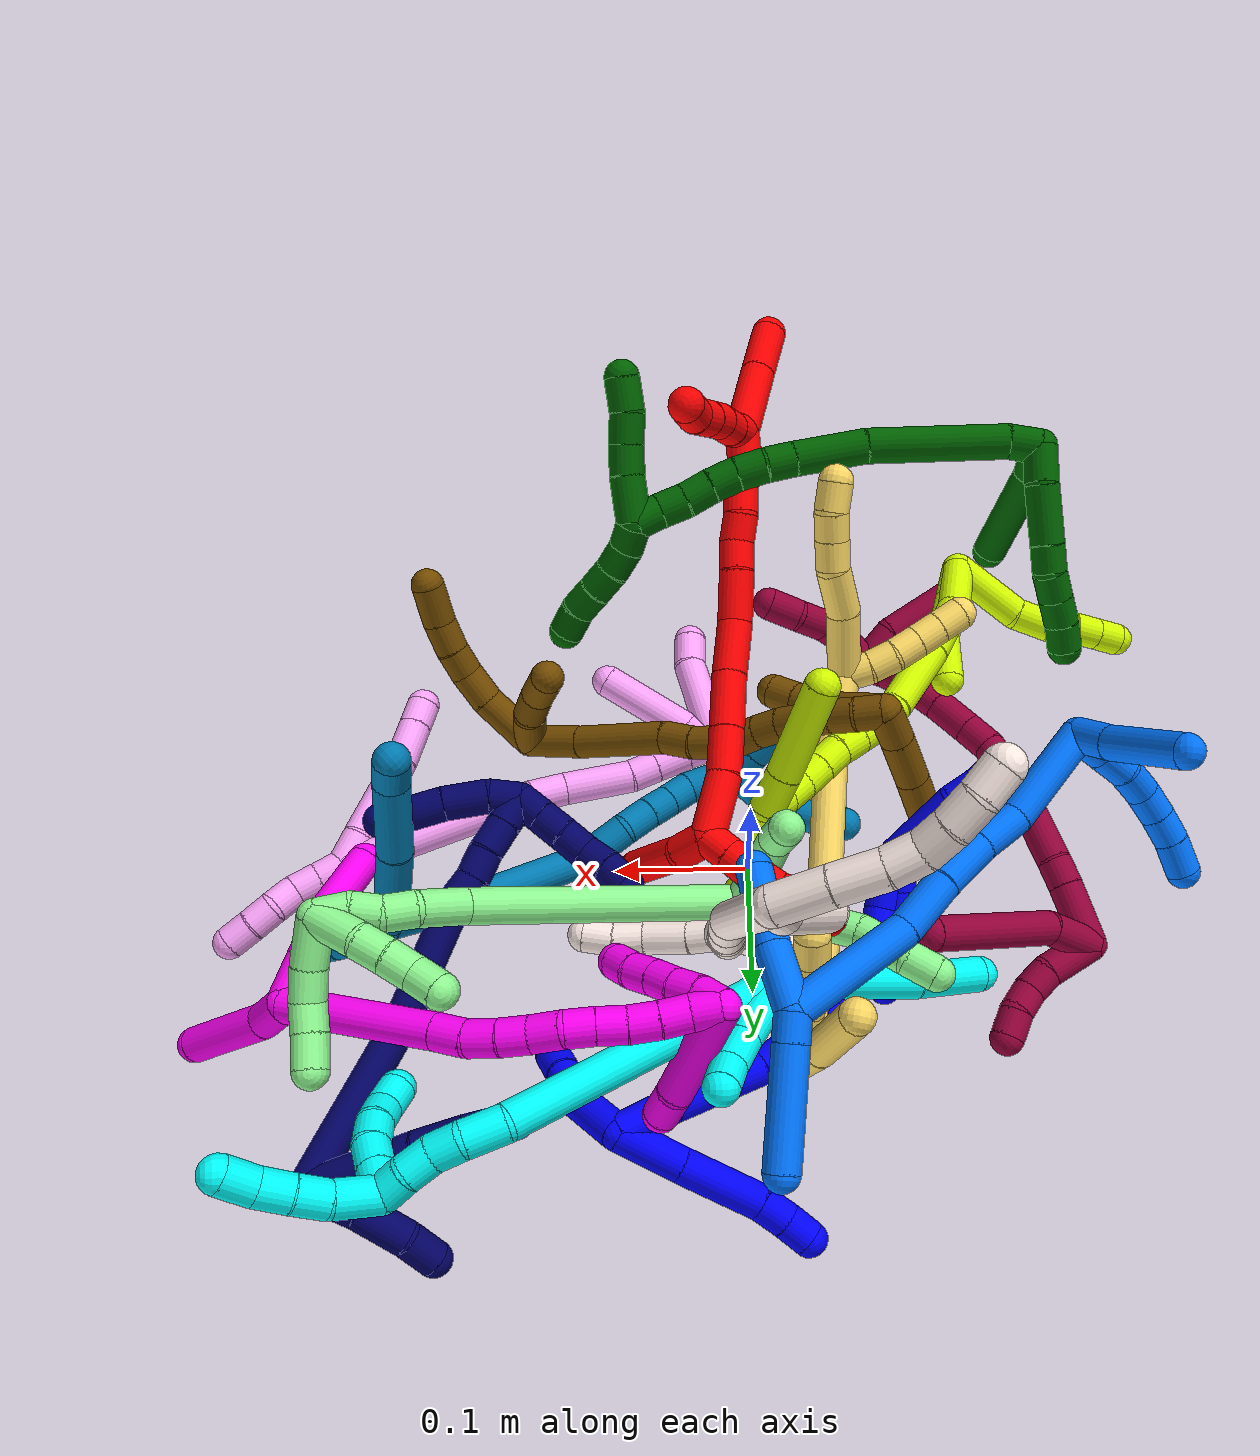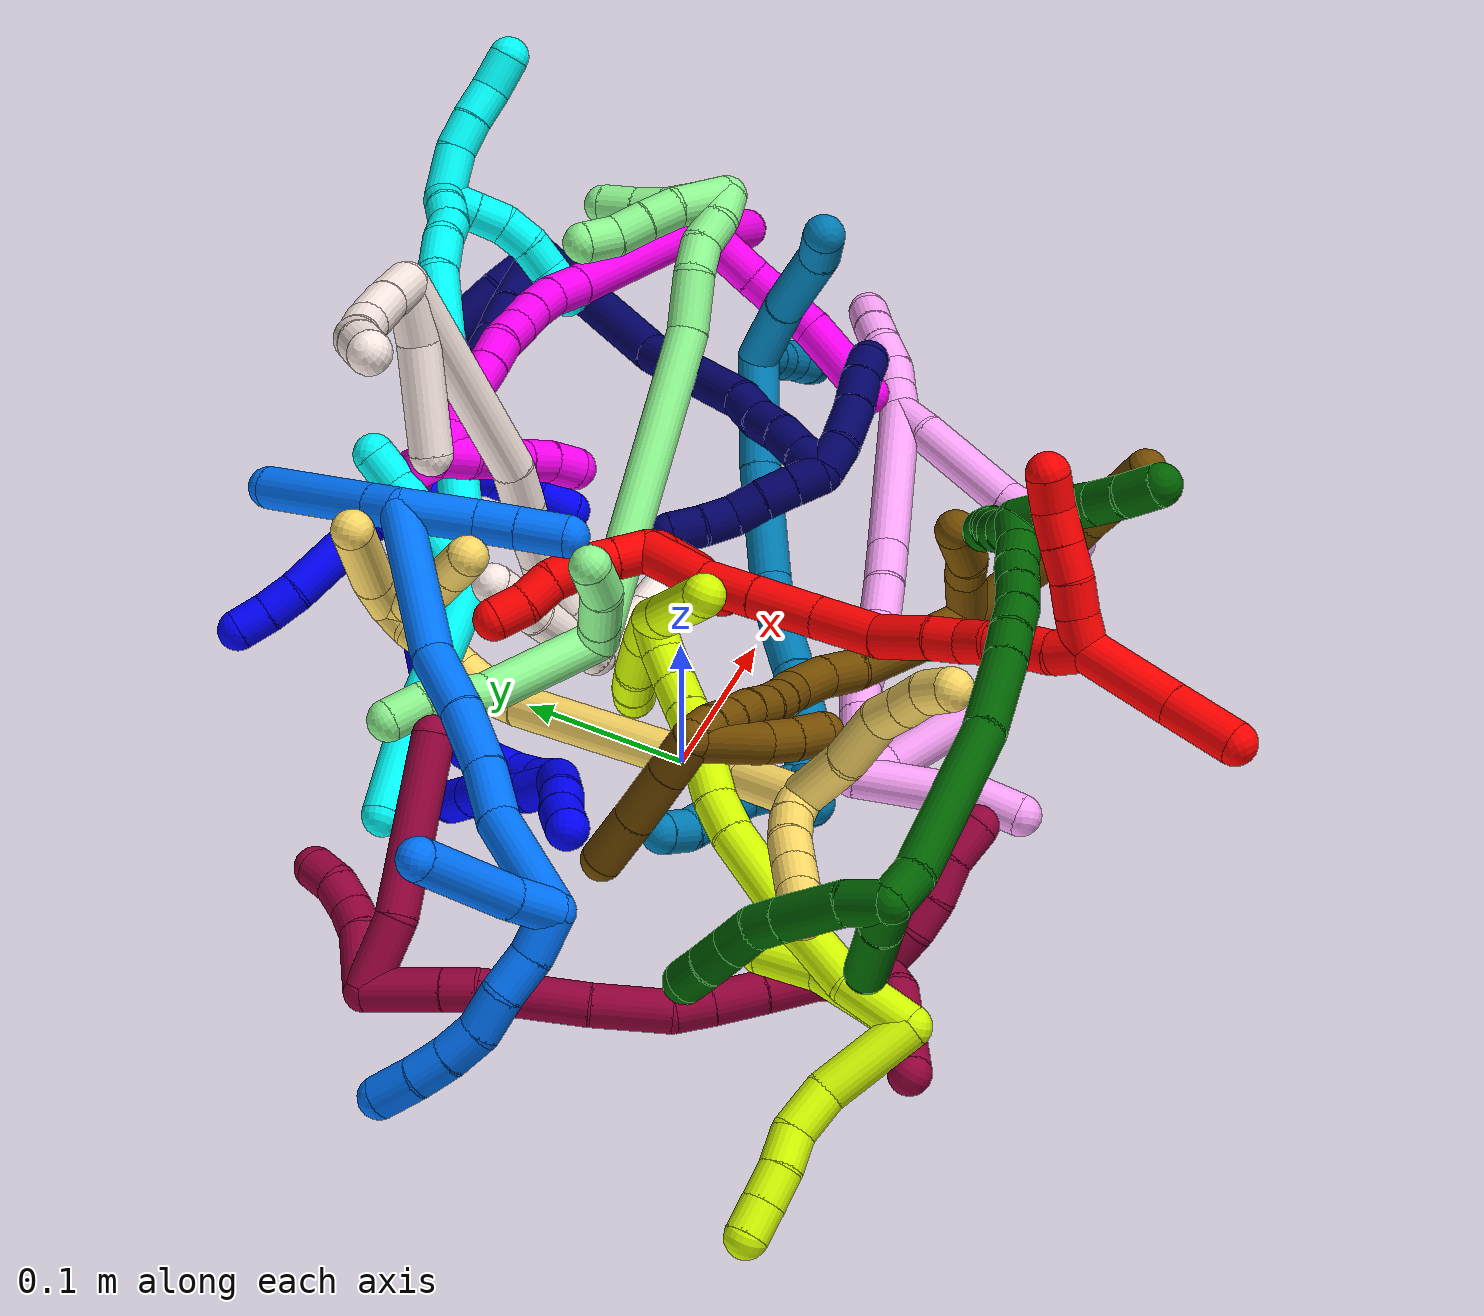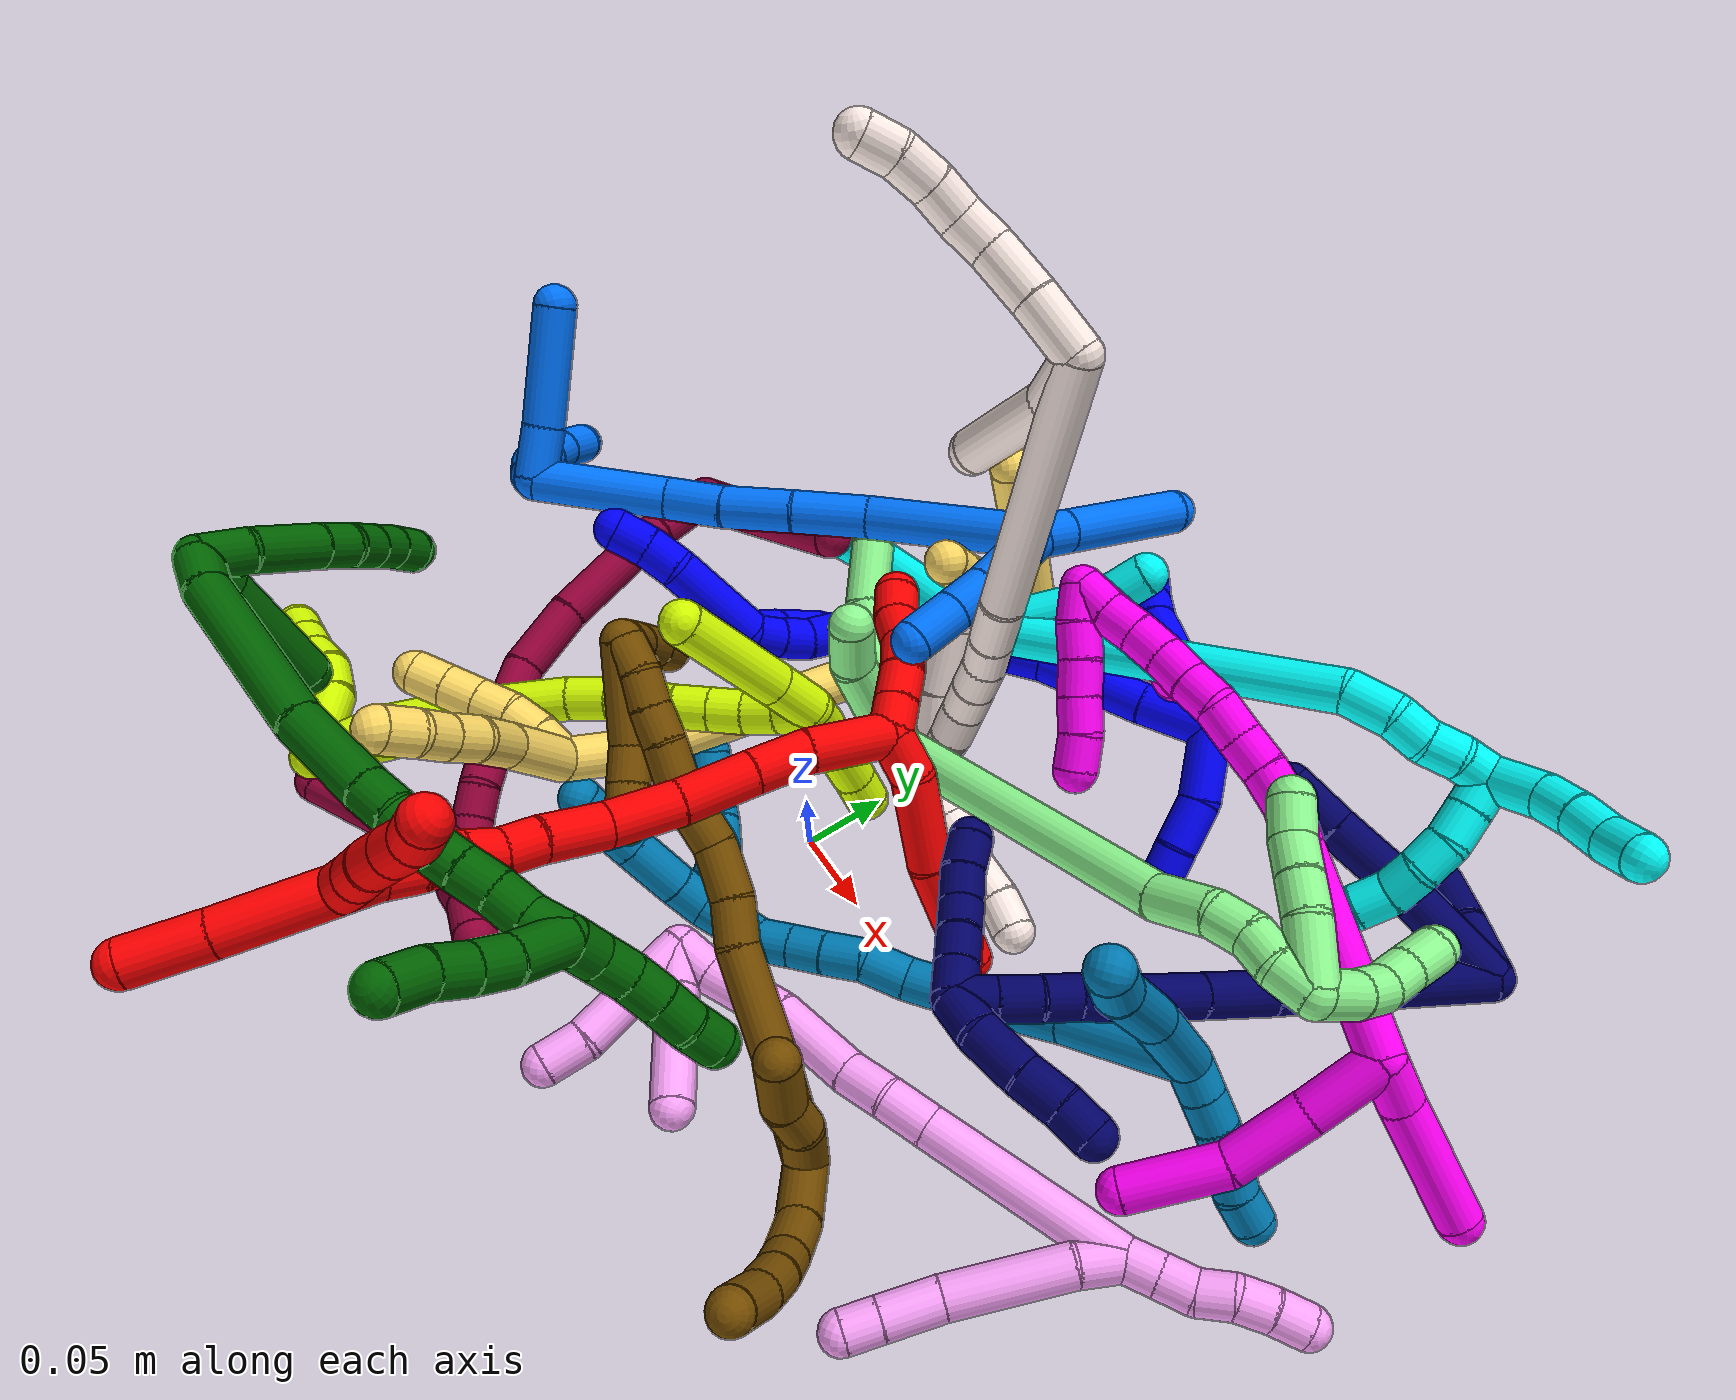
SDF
<sdf version="1.7">
 <world name="default">
  <plugin name="TubeGeneratorPlugin" filename="libtube_generator_plugin.so"/>
  <model name="photoneo_s_sensor">
   <static>1</static>
   <pose>0 0 2 1.57079 1.57079 3.14159</pose>
   <link name="link">
    <inertial><mass>0.1</mass></inertial>
    <sensor name="sensor" type="depth">
     <update_rate>30</update_rate>
     <camera>
      <horizontal_fov>1.22</horizontal_fov>
      <image><width>1920</width><height>1200</height><format>B8G8R8</format></image>
      <clip><near>0.1</near><far>4</far></clip>
      <depth_camera><output>points</output></depth_camera>
     </camera>
     <plugin name="camera_plugin" filename="libgazebo_ros_depth_camera.so">
      <baseline>0.2</baseline>
      <alwaysOn>1</alwaysOn>
      <updateRate>0.0</updateRate>
      <cameraName>camera_ir</cameraName>
      <imageTopicName>/camera/color/image_raw</imageTopicName>
      <cameraInfoTopicName>/camera/color/camera_info</cameraInfoTopicName>
      <depthImageTopicName>/camera/depth/image_raw</depthImageTopicName>
      <depthImageCameraInfoTopicName>/camera/depth/camera_info</depthImageCameraInfoTopicName>
      <pointCloudTopicName>/camera/depth/points</pointCloudTopicName>
      <frameName>fr_optical</frameName>
      <pointCloudCutoff>0.1</pointCloudCutoff>
      <pointCloudCutoffMax>2.0</pointCloudCutoffMax>
      <distortionK1>0</distortionK1>
      <distortionK2>0</distortionK2>
      <distortionK3>0</distortionK3>
      <distortionT1>0</distortionT1>
      <distortionT2>0</distortionT2>
      <CxPrime>0</CxPrime>
      <Cx>0</Cx>
      <Cy>0</Cy>
      <focalLength>0</focalLength>
      <hackBaseline>0</hackBaseline>
     </plugin>
    </sensor>
   </link>
  </model>
  <gravity>0 0 -9.8</gravity>
  <magnetic_field>6e-06 2.3e-05 -4.2e-05</magnetic_field>
  <atmosphere type="adiabatic"/>
  <physics name="default_physics" default="0" type="ode">
   <max_step_size>0.003</max_step_size>
   <real_time_factor>1</real_time_factor>
   <real_time_update_rate>1000</real_time_update_rate>
   <max_contacts>10000</max_contacts>
   <ode>
    <solver>
     <type>quick</type>
     <iters>100</iters>
     <sor>1.3</sor>
     <use_dynamic_moi_rescaling>0</use_dynamic_moi_rescaling>
    </solver>
    <constraints>
     <contact_max_correcting_vel>0</contact_max_correcting_vel>
     <contact_surface_layer>0.001</contact_surface_layer>
     <cfm>0</cfm>
     <erp>0.2</erp>
    </constraints>
   </ode>
  </physics>
  <scene><ambient>0.4 0.4 0.4 1</ambient><background>0.7 0.7 0.7 1</background><shadows>0</shadows></scene>
  <audio><device>default</device></audio>
  <spherical_coordinates>
   <surface_model>EARTH_WGS84</surface_model>
   <latitude_deg>0</latitude_deg>
   <longitude_deg>0</longitude_deg>
   <elevation>0</elevation>
   <heading_deg>0</heading_deg>
  </spherical_coordinates>
  <model name="bin">
   <static>1</static>
   <link name="bottom">
    <collision name="collision-bottom">
     <pose>0 0 -0.01 0 -0 0</pose>
     <geometry><box><size>0.8 0.6 0.02</size></box></geometry>
     <surface>
      <friction><ode><mu>100</mu><mu2>100</mu2></ode></friction>
      <contact><collide_bitmask>65535</collide_bitmask></contact>
     </surface>
    </collision>
   </link>
   <link name="west_wall">
    <collision name="collision-west_wall">
     <pose>-0.41 0 0.1 0 -0 0</pose>
     <geometry><box><size>0.02 0.6 0.2</size></box></geometry>
     <surface>
      <friction><ode><mu>100</mu><mu2>100</mu2></ode></friction>
      <contact><collide_bitmask>65535</collide_bitmask></contact>
     </surface>
    </collision>
   </link>
   <link name="east_wall">
    <collision name="collision-east_wall">
     <pose>0.41 0 0.1 0 -0 0</pose>
     <geometry><box><size>0.02 0.6 0.2</size></box></geometry>
     <surface>
      <friction><ode><mu>100</mu><mu2>100</mu2></ode></friction>
      <contact><collide_bitmask>65535</collide_bitmask></contact>
     </surface>
    </collision>
   </link>
   <link name="south_wall">
    <collision name="collision-south_wall">
     <pose>0 -0.31 0.1 0 -0 0</pose>
     <geometry><box><size>0.8 0.02 0.2</size></box></geometry>
     <surface>
      <friction><ode><mu>100</mu><mu2>100</mu2></ode></friction>
      <contact><collide_bitmask>65535</collide_bitmask></contact>
     </surface>
    </collision>
   </link>
   <link name="north_wall">
    <collision name="collision-north_wall">
     <pose>0 0.31 0.1 0 -0 0</pose>
     <geometry><box><size>0.8 0.02 0.2</size></box></geometry>
     <surface>
      <friction><ode><mu>100</mu><mu2>100</mu2></ode></friction>
      <contact><collide_bitmask>65535</collide_bitmask></contact>
     </surface>
    </collision>
   </link>
  </model>
  <model name="1">
   <static>0</static>
   <link name="1">
    <collision name="collision-cylinder-e_1_2_8">
     <pose>-0.00912 0.016044 -0.015501 -2.33898 -0.388075 0.867394</pose>
     <geometry><cylinder><radius>0.0125</radius><length>0.048202</length></cylinder></geometry>
     <surface>
      <friction><ode><mu>1.16</mu><mu2>1.16</mu2><slip1>0</slip1><slip2>0</slip2></ode></friction>
      <contact><ode><kp>1e+06</kp><kd>1</kd><max_vel>0</max_vel><min_depth>0.001</min_depth></ode></contact>
     </surface>
    </collision>
    <visual name="visual-cylinder-e_1_2_8">
     <pose>-0.00912 0.016044 -0.015501 -2.33898 -0.388075 0.867394</pose>
     <geometry><cylinder><radius>0.0125</radius><length>0.048202</length></cylinder></geometry>
     <material><ambient>0 0 1 1</ambient></material>
    </visual>
    <collision name="collision-cylinder-e_2_8_9">
     <pose>-0.030283 0.051024 -0.050971 -2.38275 -0.412501 0.966448</pose>
     <geometry><cylinder><radius>0.0125</radius><length>0.060079</length></cylinder></geometry>
     <surface>
      <friction><ode><mu>1.16</mu><mu2>1.16</mu2><slip1>0</slip1><slip2>0</slip2></ode></friction>
      <contact><ode><kp>1e+06</kp><kd>1</kd><max_vel>0</max_vel><min_depth>0.001</min_depth></ode></contact>
     </surface>
    </collision>
    <visual name="visual-cylinder-e_2_8_9">
     <pose>-0.030283 0.051024 -0.050971 -2.38275 -0.412501 0.966448</pose>
     <geometry><cylinder><radius>0.0125</radius><length>0.060079</length></cylinder></geometry>
     <material><ambient>0 0 1 1</ambient></material>
    </visual>
    <collision name="collision-cylinder-e_3_9_10">
     <pose>-0.047303 0.077621 -0.07675 -2.21957 -0.477688 0.911567</pose>
     <geometry><cylinder><radius>0.0125</radius><length>0.021654</length></cylinder></geometry>
     <surface>
      <friction><ode><mu>1.16</mu><mu2>1.16</mu2><slip1>0</slip1><slip2>0</slip2></ode></friction>
      <contact><ode><kp>1e+06</kp><kd>1</kd><max_vel>0</max_vel><min_depth>0.001</min_depth></ode></contact>
     </surface>
    </collision>
    <visual name="visual-cylinder-e_3_9_10">
     <pose>-0.047303 0.077621 -0.07675 -2.21957 -0.477688 0.911567</pose>
     <geometry><cylinder><radius>0.0125</radius><length>0.021654</length></cylinder></geometry>
     <material><ambient>0 0 1 1</ambient></material>
    </visual>
    <collision name="collision-cylinder-e_4_10_6">
     <pose>-0.057695 0.092223 -0.087373 -2.17715 -0.57004 1.0206</pose>
     <geometry><cylinder><radius>0.0125</radius><length>0.020065</length></cylinder></geometry>
     <surface>
      <friction><ode><mu>1.16</mu><mu2>1.16</mu2><slip1>0</slip1><slip2>0</slip2></ode></friction>
      <contact><ode><kp>1e+06</kp><kd>1</kd><max_vel>0</max_vel><min_depth>0.001</min_depth></ode></contact>
     </surface>
    </collision>
    <visual name="visual-cylinder-e_4_10_6">
     <pose>-0.057695 0.092223 -0.087373 -2.17715 -0.57004 1.0206</pose>
     <geometry><cylinder><radius>0.0125</radius><length>0.020065</length></cylinder></geometry>
     <material><ambient>0 0 1 1</ambient></material>
    </visual>
    <collision name="collision-cylinder-e_1_2_11">
     <pose>0.020302 -0.002659 0.006829 0.371275 1.22438 0.262226</pose>
     <geometry><cylinder><radius>0.0125</radius><length>0.043168</length></cylinder></geometry>
     <surface>
      <friction><ode><mu>1.16</mu><mu2>1.16</mu2><slip1>0</slip1><slip2>0</slip2></ode></friction>
      <contact><ode><kp>1e+06</kp><kd>1</kd><max_vel>0</max_vel><min_depth>0.001</min_depth></ode></contact>
     </surface>
    </collision>
    <visual name="visual-cylinder-e_1_2_11">
     <pose>0.020302 -0.002659 0.006829 0.371275 1.22438 0.262226</pose>
     <geometry><cylinder><radius>0.0125</radius><length>0.043168</length></cylinder></geometry>
     <material><ambient>0 0 1 1</ambient></material>
    </visual>
    <collision name="collision-cylinder-e_2_11_12">
     <pose>0.055445 -0.00699 0.013855 1.45389 1.45784 1.34244</pose>
     <geometry><cylinder><radius>0.0125</radius><length>0.029874</length></cylinder></geometry>
     <surface>
      <friction><ode><mu>1.16</mu><mu2>1.16</mu2><slip1>0</slip1><slip2>0</slip2></ode></friction>
      <contact><ode><kp>1e+06</kp><kd>1</kd><max_vel>0</max_vel><min_depth>0.001</min_depth></ode></contact>
     </surface>
    </collision>
    <visual name="visual-cylinder-e_2_11_12">
     <pose>0.055445 -0.00699 0.013855 1.45389 1.45784 1.34244</pose>
     <geometry><cylinder><radius>0.0125</radius><length>0.029874</length></cylinder></geometry>
     <material><ambient>0 0 1 1</ambient></material>
    </visual>
    <collision name="collision-cylinder-e_3_12_5">
     <pose>0.08375 -0.008041 0.014259 -1.24723 1.52216 -1.20147</pose>
     <geometry><cylinder><radius>0.0125</radius><length>0.026958</length></cylinder></geometry>
     <surface>
      <friction><ode><mu>1.16</mu><mu2>1.16</mu2><slip1>0</slip1><slip2>0</slip2></ode></friction>
      <contact><ode><kp>1e+06</kp><kd>1</kd><max_vel>0</max_vel><min_depth>0.001</min_depth></ode></contact>
     </surface>
    </collision>
    <visual name="visual-cylinder-e_3_12_5">
     <pose>0.08375 -0.008041 0.014259 -1.24723 1.52216 -1.20147</pose>
     <geometry><cylinder><radius>0.0125</radius><length>0.026958</length></cylinder></geometry>
     <material><ambient>0 0 1 1</ambient></material>
    </visual>
    <collision name="collision-cylinder-e_1_2_13">
     <pose>0.002365 0.001079 -0.02116 -3.09067 0.111171 -2.2831</pose>
     <geometry><cylinder><radius>0.0125</radius><length>0.042639</length></cylinder></geometry>
     <surface>
      <friction><ode><mu>1.16</mu><mu2>1.16</mu2><slip1>0</slip1><slip2>0</slip2></ode></friction>
      <contact><ode><kp>1e+06</kp><kd>1</kd><max_vel>0</max_vel><min_depth>0.001</min_depth></ode></contact>
     </surface>
    </collision>
    <visual name="visual-cylinder-e_1_2_13">
     <pose>0.002365 0.001079 -0.02116 -3.09067 0.111171 -2.2831</pose>
     <geometry><cylinder><radius>0.0125</radius><length>0.042639</length></cylinder></geometry>
     <material><ambient>0 0 1 1</ambient></material>
    </visual>
    <collision name="collision-cylinder-e_2_13_14">
     <pose>0.006572 0.004463 -0.075791 -3.0728 0.054843 -1.3459</pose>
     <geometry><cylinder><radius>0.0125</radius><length>0.067201</length></cylinder></geometry>
     <surface>
      <friction><ode><mu>1.16</mu><mu2>1.16</mu2><slip1>0</slip1><slip2>0</slip2></ode></friction>
      <contact><ode><kp>1e+06</kp><kd>1</kd><max_vel>0</max_vel><min_depth>0.001</min_depth></ode></contact>
     </surface>
    </collision>
    <visual name="visual-cylinder-e_2_13_14">
     <pose>0.006572 0.004463 -0.075791 -3.0728 0.054843 -1.3459</pose>
     <geometry><cylinder><radius>0.0125</radius><length>0.067201</length></cylinder></geometry>
     <material><ambient>0 0 1 1</ambient></material>
    </visual>
    <collision name="collision-cylinder-e_3_14_15">
     <pose>0.015738 0.00367 -0.142951 3.04984 0.213199 2.33107</pose>
     <geometry><cylinder><radius>0.0125</radius><length>0.06923</length></cylinder></geometry>
     <surface>
      <friction><ode><mu>1.16</mu><mu2>1.16</mu2><slip1>0</slip1><slip2>0</slip2></ode></friction>
      <contact><ode><kp>1e+06</kp><kd>1</kd><max_vel>0</max_vel><min_depth>0.001</min_depth></ode></contact>
     </surface>
    </collision>
    <visual name="visual-cylinder-e_3_14_15">
     <pose>0.015738 0.00367 -0.142951 3.04984 0.213199 2.33107</pose>
     <geometry><cylinder><radius>0.0125</radius><length>0.06923</length></cylinder></geometry>
     <material><ambient>0 0 1 1</ambient></material>
    </visual>
    <collision name="collision-cylinder-e_4_15_16">
     <pose>0.030359 -0.005639 -0.192454 2.76743 0.405678 1.65364</pose>
     <geometry><cylinder><radius>0.0125</radius><length>0.036981</length></cylinder></geometry>
     <surface>
      <friction><ode><mu>1.16</mu><mu2>1.16</mu2><slip1>0</slip1><slip2>0</slip2></ode></friction>
      <contact><ode><kp>1e+06</kp><kd>1</kd><max_vel>0</max_vel><min_depth>0.001</min_depth></ode></contact>
     </surface>
    </collision>
    <visual name="visual-cylinder-e_4_15_16">
     <pose>0.030359 -0.005639 -0.192454 2.76743 0.405678 1.65364</pose>
     <geometry><cylinder><radius>0.0125</radius><length>0.036981</length></cylinder></geometry>
     <material><ambient>0 0 1 1</ambient></material>
    </visual>
    <collision name="collision-cylinder-e_5_16_17">
     <pose>0.041933 -0.018796 -0.216591 2.44607 0.375689 0.965926</pose>
     <geometry><cylinder><radius>0.0125</radius><length>0.023309</length></cylinder></geometry>
     <surface>
      <friction><ode><mu>1.16</mu><mu2>1.16</mu2><slip1>0</slip1><slip2>0</slip2></ode></friction>
      <contact><ode><kp>1e+06</kp><kd>1</kd><max_vel>0</max_vel><min_depth>0.001</min_depth></ode></contact>
     </surface>
    </collision>
    <visual name="visual-cylinder-e_5_16_17">
     <pose>0.041933 -0.018796 -0.216591 2.44607 0.375689 0.965926</pose>
     <geometry><cylinder><radius>0.0125</radius><length>0.023309</length></cylinder></geometry>
     <material><ambient>0 0 1 1</ambient></material>
    </visual>
    <collision name="collision-cylinder-e_6_17_18">
     <pose>0.051937 -0.032092 -0.230624 2.30328 0.590933 1.19862</pose>
     <geometry><cylinder><radius>0.0125</radius><length>0.020564</length></cylinder></geometry>
     <surface>
      <friction><ode><mu>1.16</mu><mu2>1.16</mu2><slip1>0</slip1><slip2>0</slip2></ode></friction>
      <contact><ode><kp>1e+06</kp><kd>1</kd><max_vel>0</max_vel><min_depth>0.001</min_depth></ode></contact>
     </surface>
    </collision>
    <visual name="visual-cylinder-e_6_17_18">
     <pose>0.051937 -0.032092 -0.230624 2.30328 0.590933 1.19862</pose>
     <geometry><cylinder><radius>0.0125</radius><length>0.020564</length></cylinder></geometry>
     <material><ambient>0 0 1 1</ambient></material>
    </visual>
    <collision name="collision-cylinder-e_7_18_19">
     <pose>0.060523 -0.046076 -0.242147 2.22144 0.289405 0.572004</pose>
     <geometry><cylinder><radius>0.0125</radius><length>0.020025</length></cylinder></geometry>
     <surface>
      <friction><ode><mu>1.16</mu><mu2>1.16</mu2><slip1>0</slip1><slip2>0</slip2></ode></friction>
      <contact><ode><kp>1e+06</kp><kd>1</kd><max_vel>0</max_vel><min_depth>0.001</min_depth></ode></contact>
     </surface>
    </collision>
    <visual name="visual-cylinder-e_7_18_19">
     <pose>0.060523 -0.046076 -0.242147 2.22144 0.289405 0.572004</pose>
     <geometry><cylinder><radius>0.0125</radius><length>0.020025</length></cylinder></geometry>
     <material><ambient>0 0 1 1</ambient></material>
    </visual>
    <collision name="collision-cylinder-e_8_19_1">
     <pose>0.064708 -0.0622 -0.253127 2.11766 0.132758 0.235501</pose>
     <geometry><cylinder><radius>0.0125</radius><length>0.020051</length></cylinder></geometry>
     <surface>
      <friction><ode><mu>1.16</mu><mu2>1.16</mu2><slip1>0</slip1><slip2>0</slip2></ode></friction>
      <contact><ode><kp>1e+06</kp><kd>1</kd><max_vel>0</max_vel><min_depth>0.001</min_depth></ode></contact>
     </surface>
    </collision>
    <visual name="visual-cylinder-e_8_19_1">
     <pose>0.064708 -0.0622 -0.253127 2.11766 0.132758 0.235501</pose>
     <geometry><cylinder><radius>0.0125</radius><length>0.020051</length></cylinder></geometry>
     <material><ambient>0 0 1 1</ambient></material>
    </visual>
    <collision name="collision-cylinder-e_1_1_20">
     <pose>0.05749 -0.088186 -0.280047 2.46416 -0.297035 -0.803237</pose>
     <geometry><cylinder><radius>0.0125</radius><length>0.058392</length></cylinder></geometry>
     <surface>
      <friction><ode><mu>1.16</mu><mu2>1.16</mu2><slip1>0</slip1><slip2>0</slip2></ode></friction>
      <contact><ode><kp>1e+06</kp><kd>1</kd><max_vel>0</max_vel><min_depth>0.001</min_depth></ode></contact>
     </surface>
    </collision>
    <visual name="visual-cylinder-e_1_1_20">
     <pose>0.05749 -0.088186 -0.280047 2.46416 -0.297035 -0.803237</pose>
     <geometry><cylinder><radius>0.0125</radius><length>0.058392</length></cylinder></geometry>
     <material><ambient>0 0 1 1</ambient></material>
    </visual>
    <collision name="collision-cylinder-e_2_20_21">
     <pose>0.046859 -0.109529 -0.311223 2.75421 -0.202069 -0.954078</pose>
     <geometry><cylinder><radius>0.0125</radius><length>0.020776</length></cylinder></geometry>
     <surface>
      <friction><ode><mu>1.16</mu><mu2>1.16</mu2><slip1>0</slip1><slip2>0</slip2></ode></friction>
      <contact><ode><kp>1e+06</kp><kd>1</kd><max_vel>0</max_vel><min_depth>0.001</min_depth></ode></contact>
     </surface>
    </collision>
    <visual name="visual-cylinder-e_2_20_21">
     <pose>0.046859 -0.109529 -0.311223 2.75421 -0.202069 -0.954078</pose>
     <geometry><cylinder><radius>0.0125</radius><length>0.020776</length></cylinder></geometry>
     <material><ambient>0 0 1 1</ambient></material>
    </visual>
    <collision name="collision-cylinder-e_3_21_4">
     <pose>0.044235 -0.118221 -0.329849 2.65679 -0.051819 -0.208854</pose>
     <geometry><cylinder><radius>0.0125</radius><length>0.020832</length></cylinder></geometry>
     <surface>
      <friction><ode><mu>1.16</mu><mu2>1.16</mu2><slip1>0</slip1><slip2>0</slip2></ode></friction>
      <contact><ode><kp>1e+06</kp><kd>1</kd><max_vel>0</max_vel><min_depth>0.001</min_depth></ode></contact>
     </surface>
    </collision>
    <visual name="visual-cylinder-e_3_21_4">
     <pose>0.044235 -0.118221 -0.329849 2.65679 -0.051819 -0.208854</pose>
     <geometry><cylinder><radius>0.0125</radius><length>0.020832</length></cylinder></geometry>
     <material><ambient>0 0 1 1</ambient></material>
    </visual>
    <collision name="collision-cylinder-e_1_1_22">
     <pose>0.063119 -0.058683 -0.255998 -1.38179 -0.234171 0.193902</pose>
     <geometry><cylinder><radius>0.0125</radius><length>0.025131</length></cylinder></geometry>
     <surface>
      <friction><ode><mu>1.16</mu><mu2>1.16</mu2><slip1>0</slip1><slip2>0</slip2></ode></friction>
      <contact><ode><kp>1e+06</kp><kd>1</kd><max_vel>0</max_vel><min_depth>0.001</min_depth></ode></contact>
     </surface>
    </collision>
    <visual name="visual-cylinder-e_1_1_22">
     <pose>0.063119 -0.058683 -0.255998 -1.38179 -0.234171 0.193902</pose>
     <geometry><cylinder><radius>0.0125</radius><length>0.025131</length></cylinder></geometry>
     <material><ambient>0 0 1 1</ambient></material>
    </visual>
    <collision name="collision-cylinder-e_2_22_23">
     <pose>0.056031 -0.033669 -0.24649 -1.06462 -0.2735 0.161756</pose>
     <geometry><cylinder><radius>0.0125</radius><length>0.030897</length></cylinder></geometry>
     <surface>
      <friction><ode><mu>1.16</mu><mu2>1.16</mu2><slip1>0</slip1><slip2>0</slip2></ode></friction>
      <contact><ode><kp>1e+06</kp><kd>1</kd><max_vel>0</max_vel><min_depth>0.001</min_depth></ode></contact>
     </surface>
    </collision>
    <visual name="visual-cylinder-e_2_22_23">
     <pose>0.056031 -0.033669 -0.24649 -1.06462 -0.2735 0.161756</pose>
     <geometry><cylinder><radius>0.0125</radius><length>0.030897</length></cylinder></geometry>
     <material><ambient>0 0 1 1</ambient></material>
    </visual>
    <collision name="collision-cylinder-e_3_23_24">
     <pose>0.051204 -0.011144 -0.235408 -1.18452 -0.063571 0.042781</pose>
     <geometry><cylinder><radius>0.0125</radius><length>0.020588</length></cylinder></geometry>
     <surface>
      <friction><ode><mu>1.16</mu><mu2>1.16</mu2><slip1>0</slip1><slip2>0</slip2></ode></friction>
      <contact><ode><kp>1e+06</kp><kd>1</kd><max_vel>0</max_vel><min_depth>0.001</min_depth></ode></contact>
     </surface>
    </collision>
    <visual name="visual-cylinder-e_3_23_24">
     <pose>0.051204 -0.011144 -0.235408 -1.18452 -0.063571 0.042781</pose>
     <geometry><cylinder><radius>0.0125</radius><length>0.020588</length></cylinder></geometry>
     <material><ambient>0 0 1 1</ambient></material>
    </visual>
    <collision name="collision-cylinder-e_4_24_3">
     <pose>0.049608 0.009149 -0.227102 -1.18038 -0.080678 0.054056</pose>
     <geometry><cylinder><radius>0.0125</radius><length>0.023384</length></cylinder></geometry>
     <surface>
      <friction><ode><mu>1.16</mu><mu2>1.16</mu2><slip1>0</slip1><slip2>0</slip2></ode></friction>
      <contact><ode><kp>1e+06</kp><kd>1</kd><max_vel>0</max_vel><min_depth>0.001</min_depth></ode></contact>
     </surface>
    </collision>
    <visual name="visual-cylinder-e_4_24_3">
     <pose>0.049608 0.009149 -0.227102 -1.18038 -0.080678 0.054056</pose>
     <geometry><cylinder><radius>0.0125</radius><length>0.023384</length></cylinder></geometry>
     <material><ambient>0 0 1 1</ambient></material>
    </visual>
    <collision name="collision-sphere-3">
     <pose>0.048666 0.019927 -0.222667 0 -0 0</pose>
     <geometry><sphere><radius>0.0125</radius></sphere></geometry>
     <surface>
      <friction><ode><mu>1.16</mu><mu2>1.16</mu2><slip1>0</slip1><slip2>0</slip2></ode></friction>
      <contact><ode><kp>1e+06</kp><kd>1</kd><max_vel>0</max_vel><min_depth>0.001</min_depth></ode></contact>
     </surface>
    </collision>
    <visual name="visual-sphere-3">
     <pose>0.048666 0.019927 -0.222667 0 -0 0</pose>
     <geometry><sphere><radius>0.0125</radius></sphere></geometry>
     <material><ambient>0 0 1 1</ambient></material>
    </visual>
    <collision name="collision-sphere-24">
     <pose>0.05055 -0.001628 -0.231538 0 -0 0</pose>
     <geometry><sphere><radius>0.0125</radius></sphere></geometry>
     <surface>
      <friction><ode><mu>1.16</mu><mu2>1.16</mu2><slip1>0</slip1><slip2>0</slip2></ode></friction>
      <contact><ode><kp>1e+06</kp><kd>1</kd><max_vel>0</max_vel><min_depth>0.001</min_depth></ode></contact>
     </surface>
    </collision>
    <visual name="visual-sphere-24">
     <pose>0.05055 -0.001628 -0.231538 0 -0 0</pose>
     <geometry><sphere><radius>0.0125</radius></sphere></geometry>
     <material><ambient>0 0 1 1</ambient></material>
    </visual>
    <collision name="collision-sphere-23">
     <pose>0.051858 -0.02066 -0.239278 0 -0 0</pose>
     <geometry><sphere><radius>0.0125</radius></sphere></geometry>
     <surface>
      <friction><ode><mu>1.16</mu><mu2>1.16</mu2><slip1>0</slip1><slip2>0</slip2></ode></friction>
      <contact><ode><kp>1e+06</kp><kd>1</kd><max_vel>0</max_vel><min_depth>0.001</min_depth></ode></contact>
     </surface>
    </collision>
    <visual name="visual-sphere-23">
     <pose>0.051858 -0.02066 -0.239278 0 -0 0</pose>
     <geometry><sphere><radius>0.0125</radius></sphere></geometry>
     <material><ambient>0 0 1 1</ambient></material>
    </visual>
    <collision name="collision-sphere-22">
     <pose>0.060204 -0.046678 -0.253701 0 -0 0</pose>
     <geometry><sphere><radius>0.0125</radius></sphere></geometry>
     <surface>
      <friction><ode><mu>1.16</mu><mu2>1.16</mu2><slip1>0</slip1><slip2>0</slip2></ode></friction>
      <contact><ode><kp>1e+06</kp><kd>1</kd><max_vel>0</max_vel><min_depth>0.001</min_depth></ode></contact>
     </surface>
    </collision>
    <visual name="visual-sphere-22">
     <pose>0.060204 -0.046678 -0.253701 0 -0 0</pose>
     <geometry><sphere><radius>0.0125</radius></sphere></geometry>
     <material><ambient>0 0 1 1</ambient></material>
    </visual>
    <collision name="collision-sphere-4">
     <pose>0.043696 -0.123069 -0.339052 0 -0 0</pose>
     <geometry><sphere><radius>0.0125</radius></sphere></geometry>
     <surface>
      <friction><ode><mu>1.16</mu><mu2>1.16</mu2><slip1>0</slip1><slip2>0</slip2></ode></friction>
      <contact><ode><kp>1e+06</kp><kd>1</kd><max_vel>0</max_vel><min_depth>0.001</min_depth></ode></contact>
     </surface>
    </collision>
    <visual name="visual-sphere-4">
     <pose>0.043696 -0.123069 -0.339052 0 -0 0</pose>
     <geometry><sphere><radius>0.0125</radius></sphere></geometry>
     <material><ambient>0 0 1 1</ambient></material>
    </visual>
    <collision name="collision-sphere-21">
     <pose>0.044775 -0.113374 -0.320646 0 -0 0</pose>
     <geometry><sphere><radius>0.0125</radius></sphere></geometry>
     <surface>
      <friction><ode><mu>1.16</mu><mu2>1.16</mu2><slip1>0</slip1><slip2>0</slip2></ode></friction>
      <contact><ode><kp>1e+06</kp><kd>1</kd><max_vel>0</max_vel><min_depth>0.001</min_depth></ode></contact>
     </surface>
    </collision>
    <visual name="visual-sphere-21">
     <pose>0.044775 -0.113374 -0.320646 0 -0 0</pose>
     <geometry><sphere><radius>0.0125</radius></sphere></geometry>
     <material><ambient>0 0 1 1</ambient></material>
    </visual>
    <collision name="collision-sphere-20">
     <pose>0.048944 -0.105685 -0.3018 0 -0 0</pose>
     <geometry><sphere><radius>0.0125</radius></sphere></geometry>
     <surface>
      <friction><ode><mu>1.16</mu><mu2>1.16</mu2><slip1>0</slip1><slip2>0</slip2></ode></friction>
      <contact><ode><kp>1e+06</kp><kd>1</kd><max_vel>0</max_vel><min_depth>0.001</min_depth></ode></contact>
     </surface>
    </collision>
    <visual name="visual-sphere-20">
     <pose>0.048944 -0.105685 -0.3018 0 -0 0</pose>
     <geometry><sphere><radius>0.0125</radius></sphere></geometry>
     <material><ambient>0 0 1 1</ambient></material>
    </visual>
    <collision name="collision-sphere-11">
     <pose>0.040603 -0.005318 0.013658 0 -0 0</pose>
     <geometry><sphere><radius>0.0125</radius></sphere></geometry>
     <surface>
      <friction><ode><mu>1.16</mu><mu2>1.16</mu2><slip1>0</slip1><slip2>0</slip2></ode></friction>
      <contact><ode><kp>1e+06</kp><kd>1</kd><max_vel>0</max_vel><min_depth>0.001</min_depth></ode></contact>
     </surface>
    </collision>
    <visual name="visual-sphere-11">
     <pose>0.040603 -0.005318 0.013658 0 -0 0</pose>
     <geometry><sphere><radius>0.0125</radius></sphere></geometry>
     <material><ambient>0 0 1 1</ambient></material>
    </visual>
    <collision name="collision-sphere-6">
     <pose>-0.063109 0.099164 -0.092186 0 -0 0</pose>
     <geometry><sphere><radius>0.0125</radius></sphere></geometry>
     <surface>
      <friction><ode><mu>1.16</mu><mu2>1.16</mu2><slip1>0</slip1><slip2>0</slip2></ode></friction>
      <contact><ode><kp>1e+06</kp><kd>1</kd><max_vel>0</max_vel><min_depth>0.001</min_depth></ode></contact>
     </surface>
    </collision>
    <visual name="visual-sphere-6">
     <pose>-0.063109 0.099164 -0.092186 0 -0 0</pose>
     <geometry><sphere><radius>0.0125</radius></sphere></geometry>
     <material><ambient>0 0 1 1</ambient></material>
    </visual>
    <collision name="collision-sphere-10">
     <pose>-0.052281 0.085283 -0.082559 0 -0 0</pose>
     <geometry><sphere><radius>0.0125</radius></sphere></geometry>
     <surface>
      <friction><ode><mu>1.16</mu><mu2>1.16</mu2><slip1>0</slip1><slip2>0</slip2></ode></friction>
      <contact><ode><kp>1e+06</kp><kd>1</kd><max_vel>0</max_vel><min_depth>0.001</min_depth></ode></contact>
     </surface>
    </collision>
    <visual name="visual-sphere-10">
     <pose>-0.052281 0.085283 -0.082559 0 -0 0</pose>
     <geometry><sphere><radius>0.0125</radius></sphere></geometry>
     <material><ambient>0 0 1 1</ambient></material>
    </visual>
    <collision name="collision-sphere-9">
     <pose>-0.042326 0.069959 -0.07094 0 -0 0</pose>
     <geometry><sphere><radius>0.0125</radius></sphere></geometry>
     <surface>
      <friction><ode><mu>1.16</mu><mu2>1.16</mu2><slip1>0</slip1><slip2>0</slip2></ode></friction>
      <contact><ode><kp>1e+06</kp><kd>1</kd><max_vel>0</max_vel><min_depth>0.001</min_depth></ode></contact>
     </surface>
    </collision>
    <visual name="visual-sphere-9">
     <pose>-0.042326 0.069959 -0.07094 0 -0 0</pose>
     <geometry><sphere><radius>0.0125</radius></sphere></geometry>
     <material><ambient>0 0 1 1</ambient></material>
    </visual>
    <collision name="collision-sphere-2">
     <geometry><sphere><radius>0.0125</radius></sphere></geometry>
     <surface>
      <friction><ode><mu>1.16</mu><mu2>1.16</mu2><slip1>0</slip1><slip2>0</slip2></ode></friction>
      <contact><ode><kp>1e+06</kp><kd>1</kd><max_vel>0</max_vel><min_depth>0.001</min_depth></ode></contact>
     </surface>
    </collision>
    <visual name="visual-sphere-2">
     <geometry><sphere><radius>0.0125</radius></sphere></geometry>
     <material><ambient>0 0 1 1</ambient></material>
    </visual>
    <collision name="collision-sphere-19">
     <pose>0.063381 -0.053712 -0.247959 0 -0 0</pose>
     <geometry><sphere><radius>0.0125</radius></sphere></geometry>
     <surface>
      <friction><ode><mu>1.16</mu><mu2>1.16</mu2><slip1>0</slip1><slip2>0</slip2></ode></friction>
      <contact><ode><kp>1e+06</kp><kd>1</kd><max_vel>0</max_vel><min_depth>0.001</min_depth></ode></contact>
     </surface>
    </collision>
    <visual name="visual-sphere-19">
     <pose>0.063381 -0.053712 -0.247959 0 -0 0</pose>
     <geometry><sphere><radius>0.0125</radius></sphere></geometry>
     <material><ambient>0 0 1 1</ambient></material>
    </visual>
    <collision name="collision-sphere-8">
     <pose>-0.01824 0.032088 -0.031002 0 -0 0</pose>
     <geometry><sphere><radius>0.0125</radius></sphere></geometry>
     <surface>
      <friction><ode><mu>1.16</mu><mu2>1.16</mu2><slip1>0</slip1><slip2>0</slip2></ode></friction>
      <contact><ode><kp>1e+06</kp><kd>1</kd><max_vel>0</max_vel><min_depth>0.001</min_depth></ode></contact>
     </surface>
    </collision>
    <visual name="visual-sphere-8">
     <pose>-0.01824 0.032088 -0.031002 0 -0 0</pose>
     <geometry><sphere><radius>0.0125</radius></sphere></geometry>
     <material><ambient>0 0 1 1</ambient></material>
    </visual>
    <collision name="collision-sphere-12">
     <pose>0.070287 -0.008662 0.014051 0 -0 0</pose>
     <geometry><sphere><radius>0.0125</radius></sphere></geometry>
     <surface>
      <friction><ode><mu>1.16</mu><mu2>1.16</mu2><slip1>0</slip1><slip2>0</slip2></ode></friction>
      <contact><ode><kp>1e+06</kp><kd>1</kd><max_vel>0</max_vel><min_depth>0.001</min_depth></ode></contact>
     </surface>
    </collision>
    <visual name="visual-sphere-12">
     <pose>0.070287 -0.008662 0.014051 0 -0 0</pose>
     <geometry><sphere><radius>0.0125</radius></sphere></geometry>
     <material><ambient>0 0 1 1</ambient></material>
    </visual>
    <collision name="collision-sphere-5">
     <pose>0.097213 -0.007419 0.014468 0 -0 0</pose>
     <geometry><sphere><radius>0.0125</radius></sphere></geometry>
     <surface>
      <friction><ode><mu>1.16</mu><mu2>1.16</mu2><slip1>0</slip1><slip2>0</slip2></ode></friction>
      <contact><ode><kp>1e+06</kp><kd>1</kd><max_vel>0</max_vel><min_depth>0.001</min_depth></ode></contact>
     </surface>
    </collision>
    <visual name="visual-sphere-5">
     <pose>0.097213 -0.007419 0.014468 0 -0 0</pose>
     <geometry><sphere><radius>0.0125</radius></sphere></geometry>
     <material><ambient>0 0 1 1</ambient></material>
    </visual>
    <collision name="collision-sphere-13">
     <pose>0.00473 0.002157 -0.04232 0 -0 0</pose>
     <geometry><sphere><radius>0.0125</radius></sphere></geometry>
     <surface>
      <friction><ode><mu>1.16</mu><mu2>1.16</mu2><slip1>0</slip1><slip2>0</slip2></ode></friction>
      <contact><ode><kp>1e+06</kp><kd>1</kd><max_vel>0</max_vel><min_depth>0.001</min_depth></ode></contact>
     </surface>
    </collision>
    <visual name="visual-sphere-13">
     <pose>0.00473 0.002157 -0.04232 0 -0 0</pose>
     <geometry><sphere><radius>0.0125</radius></sphere></geometry>
     <material><ambient>0 0 1 1</ambient></material>
    </visual>
    <collision name="collision-sphere-14">
     <pose>0.008414 0.00677 -0.109262 0 -0 0</pose>
     <geometry><sphere><radius>0.0125</radius></sphere></geometry>
     <surface>
      <friction><ode><mu>1.16</mu><mu2>1.16</mu2><slip1>0</slip1><slip2>0</slip2></ode></friction>
      <contact><ode><kp>1e+06</kp><kd>1</kd><max_vel>0</max_vel><min_depth>0.001</min_depth></ode></contact>
     </surface>
    </collision>
    <visual name="visual-sphere-14">
     <pose>0.008414 0.00677 -0.109262 0 -0 0</pose>
     <geometry><sphere><radius>0.0125</radius></sphere></geometry>
     <material><ambient>0 0 1 1</ambient></material>
    </visual>
    <collision name="collision-sphere-15">
     <pose>0.023062 0.00057 -0.176639 0 -0 0</pose>
     <geometry><sphere><radius>0.0125</radius></sphere></geometry>
     <surface>
      <friction><ode><mu>1.16</mu><mu2>1.16</mu2><slip1>0</slip1><slip2>0</slip2></ode></friction>
      <contact><ode><kp>1e+06</kp><kd>1</kd><max_vel>0</max_vel><min_depth>0.001</min_depth></ode></contact>
     </surface>
    </collision>
    <visual name="visual-sphere-15">
     <pose>0.023062 0.00057 -0.176639 0 -0 0</pose>
     <geometry><sphere><radius>0.0125</radius></sphere></geometry>
     <material><ambient>0 0 1 1</ambient></material>
    </visual>
    <collision name="collision-sphere-16">
     <pose>0.037657 -0.011849 -0.208268 0 -0 0</pose>
     <geometry><sphere><radius>0.0125</radius></sphere></geometry>
     <surface>
      <friction><ode><mu>1.16</mu><mu2>1.16</mu2><slip1>0</slip1><slip2>0</slip2></ode></friction>
      <contact><ode><kp>1e+06</kp><kd>1</kd><max_vel>0</max_vel><min_depth>0.001</min_depth></ode></contact>
     </surface>
    </collision>
    <visual name="visual-sphere-16">
     <pose>0.037657 -0.011849 -0.208268 0 -0 0</pose>
     <geometry><sphere><radius>0.0125</radius></sphere></geometry>
     <material><ambient>0 0 1 1</ambient></material>
    </visual>
    <collision name="collision-sphere-17">
     <pose>0.046209 -0.025743 -0.224914 0 -0 0</pose>
     <geometry><sphere><radius>0.0125</radius></sphere></geometry>
     <surface>
      <friction><ode><mu>1.16</mu><mu2>1.16</mu2><slip1>0</slip1><slip2>0</slip2></ode></friction>
      <contact><ode><kp>1e+06</kp><kd>1</kd><max_vel>0</max_vel><min_depth>0.001</min_depth></ode></contact>
     </surface>
    </collision>
    <visual name="visual-sphere-17">
     <pose>0.046209 -0.025743 -0.224914 0 -0 0</pose>
     <geometry><sphere><radius>0.0125</radius></sphere></geometry>
     <material><ambient>0 0 1 1</ambient></material>
    </visual>
    <collision name="collision-sphere-18">
     <pose>0.057666 -0.03844 -0.236334 0 -0 0</pose>
     <geometry><sphere><radius>0.0125</radius></sphere></geometry>
     <surface>
      <friction><ode><mu>1.16</mu><mu2>1.16</mu2><slip1>0</slip1><slip2>0</slip2></ode></friction>
      <contact><ode><kp>1e+06</kp><kd>1</kd><max_vel>0</max_vel><min_depth>0.001</min_depth></ode></contact>
     </surface>
    </collision>
    <visual name="visual-sphere-18">
     <pose>0.057666 -0.03844 -0.236334 0 -0 0</pose>
     <geometry><sphere><radius>0.0125</radius></sphere></geometry>
     <material><ambient>0 0 1 1</ambient></material>
    </visual>
    <collision name="collision-sphere-1">
     <pose>0.066035 -0.070688 -0.258294 0 -0 0</pose>
     <geometry><sphere><radius>0.0125</radius></sphere></geometry>
     <surface>
      <friction><ode><mu>1.16</mu><mu2>1.16</mu2><slip1>0</slip1><slip2>0</slip2></ode></friction>
      <contact><ode><kp>1e+06</kp><kd>1</kd><max_vel>0</max_vel><min_depth>0.001</min_depth></ode></contact>
     </surface>
    </collision>
    <visual name="visual-sphere-1">
     <pose>0.066035 -0.070688 -0.258294 0 -0 0</pose>
     <geometry><sphere><radius>0.0125</radius></sphere></geometry>
     <material><ambient>0 0 1 1</ambient></material>
    </visual>
    <inertial>
     <pose>0.024591 -0.011287 -0.137003 0 -0 0</pose>
     <mass>0.75</mass>
     <inertia><ixx>4.5e-05</ixx><ixy>0</ixy><ixz>0</ixz><iyy>3.7e-05</iyy><iyz>0</iyz><izz>-4.6e-05</izz></inertia>
    </inertial>
   </link>
   <pose>0.096697 0.217767 0.059671 -1.54457 0.598876 -1.14453</pose>
  </model>
  <model name="2">
   <static>0</static>
   <link name="2">
    <collision name="collision-cylinder-e_1_2_8">
     <pose>-0.001815 0.013076 0.002079 -1.41315 -0.136226 0.11633</pose>
     <geometry><cylinder><radius>0.0125</radius><length>0.026728</length></cylinder></geometry>
     <surface>
      <friction><ode><mu>1.16</mu><mu2>1.16</mu2><slip1>0</slip1><slip2>0</slip2></ode></friction>
      <contact><ode><kp>1e+06</kp><kd>1</kd><max_vel>0</max_vel><min_depth>0.001</min_depth></ode></contact>
     </surface>
    </collision>
    <visual name="visual-cylinder-e_1_2_8">
     <pose>-0.001815 0.013076 0.002079 -1.41315 -0.136226 0.11633</pose>
     <geometry><cylinder><radius>0.0125</radius><length>0.026728</length></cylinder></geometry>
     <material><ambient>1 0 0 1</ambient></material>
    </visual>
    <collision name="collision-cylinder-e_2_8_9">
     <pose>-0.008847 0.049954 0.015653 -1.12088 -0.194858 0.12252</pose>
     <geometry><cylinder><radius>0.0125</radius><length>0.053886</length></cylinder></geometry>
     <surface>
      <friction><ode><mu>1.16</mu><mu2>1.16</mu2><slip1>0</slip1><slip2>0</slip2></ode></friction>
      <contact><ode><kp>1e+06</kp><kd>1</kd><max_vel>0</max_vel><min_depth>0.001</min_depth></ode></contact>
     </surface>
    </collision>
    <visual name="visual-cylinder-e_2_8_9">
     <pose>-0.008847 0.049954 0.015653 -1.12088 -0.194858 0.12252</pose>
     <geometry><cylinder><radius>0.0125</radius><length>0.053886</length></cylinder></geometry>
     <material><ambient>1 0 0 1</ambient></material>
    </visual>
    <collision name="collision-cylinder-e_3_9_6">
     <pose>-0.015126 0.106724 0.037901 -1.25551 -0.030615 0.022218</pose>
     <geometry><cylinder><radius>0.0125</radius><length>0.069387</length></cylinder></geometry>
     <surface>
      <friction><ode><mu>1.16</mu><mu2>1.16</mu2><slip1>0</slip1><slip2>0</slip2></ode></friction>
      <contact><ode><kp>1e+06</kp><kd>1</kd><max_vel>0</max_vel><min_depth>0.001</min_depth></ode></contact>
     </surface>
    </collision>
    <visual name="visual-cylinder-e_3_9_6">
     <pose>-0.015126 0.106724 0.037901 -1.25551 -0.030615 0.022218</pose>
     <geometry><cylinder><radius>0.0125</radius><length>0.069387</length></cylinder></geometry>
     <material><ambient>1 0 0 1</ambient></material>
    </visual>
    <collision name="collision-cylinder-e_1_2_10">
     <pose>0.009153 -0.003514 -0.001969 2.08164 1.1562 1.67822</pose>
     <geometry><cylinder><radius>0.0125</radius><length>0.02</length></cylinder></geometry>
     <surface>
      <friction><ode><mu>1.16</mu><mu2>1.16</mu2><slip1>0</slip1><slip2>0</slip2></ode></friction>
      <contact><ode><kp>1e+06</kp><kd>1</kd><max_vel>0</max_vel><min_depth>0.001</min_depth></ode></contact>
     </surface>
    </collision>
    <visual name="visual-cylinder-e_1_2_10">
     <pose>0.009153 -0.003514 -0.001969 2.08164 1.1562 1.67822</pose>
     <geometry><cylinder><radius>0.0125</radius><length>0.02</length></cylinder></geometry>
     <material><ambient>1 0 0 1</ambient></material>
    </visual>
    <collision name="collision-cylinder-e_2_10_11">
     <pose>0.02743 -0.010541 -0.006039 2.1096 1.1491 1.70257</pose>
     <geometry><cylinder><radius>0.0125</radius><length>0.02</length></cylinder></geometry>
     <surface>
      <friction><ode><mu>1.16</mu><mu2>1.16</mu2><slip1>0</slip1><slip2>0</slip2></ode></friction>
      <contact><ode><kp>1e+06</kp><kd>1</kd><max_vel>0</max_vel><min_depth>0.001</min_depth></ode></contact>
     </surface>
    </collision>
    <visual name="visual-cylinder-e_2_10_11">
     <pose>0.02743 -0.010541 -0.006039 2.1096 1.1491 1.70257</pose>
     <geometry><cylinder><radius>0.0125</radius><length>0.02</length></cylinder></geometry>
     <material><ambient>1 0 0 1</ambient></material>
    </visual>
    <collision name="collision-cylinder-e_3_11_12">
     <pose>0.045985 -0.017378 -0.008142 1.57169 1.23194 1.23279</pose>
     <geometry><cylinder><radius>0.0125</radius><length>0.02</length></cylinder></geometry>
     <surface>
      <friction><ode><mu>1.16</mu><mu2>1.16</mu2><slip1>0</slip1><slip2>0</slip2></ode></friction>
      <contact><ode><kp>1e+06</kp><kd>1</kd><max_vel>0</max_vel><min_depth>0.001</min_depth></ode></contact>
     </surface>
    </collision>
    <visual name="visual-cylinder-e_3_11_12">
     <pose>0.045985 -0.017378 -0.008142 1.57169 1.23194 1.23279</pose>
     <geometry><cylinder><radius>0.0125</radius><length>0.02</length></cylinder></geometry>
     <material><ambient>1 0 0 1</ambient></material>
    </visual>
    <collision name="collision-cylinder-e_4_12_13">
     <pose>0.064313 -0.024376 -0.005435 0.93529 1.09669 0.598428</pose>
     <geometry><cylinder><radius>0.0125</radius><length>0.02</length></cylinder></geometry>
     <surface>
      <friction><ode><mu>1.16</mu><mu2>1.16</mu2><slip1>0</slip1><slip2>0</slip2></ode></friction>
      <contact><ode><kp>1e+06</kp><kd>1</kd><max_vel>0</max_vel><min_depth>0.001</min_depth></ode></contact>
     </surface>
    </collision>
    <visual name="visual-cylinder-e_4_12_13">
     <pose>0.064313 -0.024376 -0.005435 0.93529 1.09669 0.598428</pose>
     <geometry><cylinder><radius>0.0125</radius><length>0.02</length></cylinder></geometry>
     <material><ambient>1 0 0 1</ambient></material>
    </visual>
    <collision name="collision-cylinder-e_5_13_5">
     <pose>0.08269 -0.031227 -0.002525 1.50795 1.24683 1.18784</pose>
     <geometry><cylinder><radius>0.0125</radius><length>0.02</length></cylinder></geometry>
     <surface>
      <friction><ode><mu>1.16</mu><mu2>1.16</mu2><slip1>0</slip1><slip2>0</slip2></ode></friction>
      <contact><ode><kp>1e+06</kp><kd>1</kd><max_vel>0</max_vel><min_depth>0.001</min_depth></ode></contact>
     </surface>
    </collision>
    <visual name="visual-cylinder-e_5_13_5">
     <pose>0.08269 -0.031227 -0.002525 1.50795 1.24683 1.18784</pose>
     <geometry><cylinder><radius>0.0125</radius><length>0.02</length></cylinder></geometry>
     <material><ambient>1 0 0 1</ambient></material>
    </visual>
    <collision name="collision-cylinder-e_1_2_14">
     <pose>-0.012844 -0.012383 0.01459 0.703777 -0.591101 -0.222658</pose>
     <geometry><cylinder><radius>0.0125</radius><length>0.046094</length></cylinder></geometry>
     <surface>
      <friction><ode><mu>1.16</mu><mu2>1.16</mu2><slip1>0</slip1><slip2>0</slip2></ode></friction>
      <contact><ode><kp>1e+06</kp><kd>1</kd><max_vel>0</max_vel><min_depth>0.001</min_depth></ode></contact>
     </surface>
    </collision>
    <visual name="visual-cylinder-e_1_2_14">
     <pose>-0.012844 -0.012383 0.01459 0.703777 -0.591101 -0.222658</pose>
     <geometry><cylinder><radius>0.0125</radius><length>0.046094</length></cylinder></geometry>
     <material><ambient>1 0 0 1</ambient></material>
    </visual>
    <collision name="collision-cylinder-e_2_14_15">
     <pose>-0.037309 -0.031731 0.03883 0.625102 -0.773526 -0.261712</pose>
     <geometry><cylinder><radius>0.0125</radius><length>0.033268</length></cylinder></geometry>
     <surface>
      <friction><ode><mu>1.16</mu><mu2>1.16</mu2><slip1>0</slip1><slip2>0</slip2></ode></friction>
      <contact><ode><kp>1e+06</kp><kd>1</kd><max_vel>0</max_vel><min_depth>0.001</min_depth></ode></contact>
     </surface>
    </collision>
    <visual name="visual-cylinder-e_2_14_15">
     <pose>-0.037309 -0.031731 0.03883 0.625102 -0.773526 -0.261712</pose>
     <geometry><cylinder><radius>0.0125</radius><length>0.033268</length></cylinder></geometry>
     <material><ambient>1 0 0 1</ambient></material>
    </visual>
    <collision name="collision-cylinder-e_3_15_16">
     <pose>-0.063462 -0.047051 0.060809 0.595684 -0.773099 -0.248604</pose>
     <geometry><cylinder><radius>0.0125</radius><length>0.041616</length></cylinder></geometry>
     <surface>
      <friction><ode><mu>1.16</mu><mu2>1.16</mu2><slip1>0</slip1><slip2>0</slip2></ode></friction>
      <contact><ode><kp>1e+06</kp><kd>1</kd><max_vel>0</max_vel><min_depth>0.001</min_depth></ode></contact>
     </surface>
    </collision>
    <visual name="visual-cylinder-e_3_15_16">
     <pose>-0.063462 -0.047051 0.060809 0.595684 -0.773099 -0.248604</pose>
     <geometry><cylinder><radius>0.0125</radius><length>0.041616</length></cylinder></geometry>
     <material><ambient>1 0 0 1</ambient></material>
    </visual>
    <collision name="collision-cylinder-e_4_16_17">
     <pose>-0.091557 -0.065049 0.084225 0.715754 -0.745447 -0.290395</pose>
     <geometry><cylinder><radius>0.0125</radius><length>0.039994</length></cylinder></geometry>
     <surface>
      <friction><ode><mu>1.16</mu><mu2>1.16</mu2><slip1>0</slip1><slip2>0</slip2></ode></friction>
      <contact><ode><kp>1e+06</kp><kd>1</kd><max_vel>0</max_vel><min_depth>0.001</min_depth></ode></contact>
     </surface>
    </collision>
    <visual name="visual-cylinder-e_4_16_17">
     <pose>-0.091557 -0.065049 0.084225 0.715754 -0.745447 -0.290395</pose>
     <geometry><cylinder><radius>0.0125</radius><length>0.039994</length></cylinder></geometry>
     <material><ambient>1 0 0 1</ambient></material>
    </visual>
    <collision name="collision-cylinder-e_5_17_18">
     <pose>-0.119075 -0.085344 0.101214 1.06489 -0.85324 -0.52335</pose>
     <geometry><cylinder><radius>0.0125</radius><length>0.037041</length></cylinder></geometry>
     <surface>
      <friction><ode><mu>1.16</mu><mu2>1.16</mu2><slip1>0</slip1><slip2>0</slip2></ode></friction>
      <contact><ode><kp>1e+06</kp><kd>1</kd><max_vel>0</max_vel><min_depth>0.001</min_depth></ode></contact>
     </surface>
    </collision>
    <visual name="visual-cylinder-e_5_17_18">
     <pose>-0.119075 -0.085344 0.101214 1.06489 -0.85324 -0.52335</pose>
     <geometry><cylinder><radius>0.0125</radius><length>0.037041</length></cylinder></geometry>
     <material><ambient>1 0 0 1</ambient></material>
    </visual>
    <collision name="collision-cylinder-e_6_18_19">
     <pose>-0.14111 -0.101123 0.111381 0.876815 -0.880859 -0.434941</pose>
     <geometry><cylinder><radius>0.0125</radius><length>0.020955</length></cylinder></geometry>
     <surface>
      <friction><ode><mu>1.16</mu><mu2>1.16</mu2><slip1>0</slip1><slip2>0</slip2></ode></friction>
      <contact><ode><kp>1e+06</kp><kd>1</kd><max_vel>0</max_vel><min_depth>0.001</min_depth></ode></contact>
     </surface>
    </collision>
    <visual name="visual-cylinder-e_6_18_19">
     <pose>-0.14111 -0.101123 0.111381 0.876815 -0.880859 -0.434941</pose>
     <geometry><cylinder><radius>0.0125</radius><length>0.020955</length></cylinder></geometry>
     <material><ambient>1 0 0 1</ambient></material>
    </visual>
    <collision name="collision-cylinder-e_7_19_20">
     <pose>-0.156037 -0.113313 0.118402 1.19878 -0.734402 -0.513992</pose>
     <geometry><cylinder><radius>0.0125</radius><length>0.020432</length></cylinder></geometry>
     <surface>
      <friction><ode><mu>1.16</mu><mu2>1.16</mu2><slip1>0</slip1><slip2>0</slip2></ode></friction>
      <contact><ode><kp>1e+06</kp><kd>1</kd><max_vel>0</max_vel><min_depth>0.001</min_depth></ode></contact>
     </surface>
    </collision>
    <visual name="visual-cylinder-e_7_19_20">
     <pose>-0.156037 -0.113313 0.118402 1.19878 -0.734402 -0.513992</pose>
     <geometry><cylinder><radius>0.0125</radius><length>0.020432</length></cylinder></geometry>
     <material><ambient>1 0 0 1</ambient></material>
    </visual>
    <collision name="collision-cylinder-e_8_20_21">
     <pose>-0.170542 -0.125384 0.125261 0.8844 -0.869092 -0.432632</pose>
     <geometry><cylinder><radius>0.0125</radius><length>0.020057</length></cylinder></geometry>
     <surface>
      <friction><ode><mu>1.16</mu><mu2>1.16</mu2><slip1>0</slip1><slip2>0</slip2></ode></friction>
      <contact><ode><kp>1e+06</kp><kd>1</kd><max_vel>0</max_vel><min_depth>0.001</min_depth></ode></contact>
     </surface>
    </collision>
    <visual name="visual-cylinder-e_8_20_21">
     <pose>-0.170542 -0.125384 0.125261 0.8844 -0.869092 -0.432632</pose>
     <geometry><cylinder><radius>0.0125</radius><length>0.020057</length></cylinder></geometry>
     <material><ambient>1 0 0 1</ambient></material>
    </visual>
    <collision name="collision-cylinder-e_9_21_22">
     <pose>-0.18499 -0.136217 0.133897 0.909556 -0.743613 -0.376812</pose>
     <geometry><cylinder><radius>0.0125</radius><length>0.020058</length></cylinder></geometry>
     <surface>
      <friction><ode><mu>1.16</mu><mu2>1.16</mu2><slip1>0</slip1><slip2>0</slip2></ode></friction>
      <contact><ode><kp>1e+06</kp><kd>1</kd><max_vel>0</max_vel><min_depth>0.001</min_depth></ode></contact>
     </surface>
    </collision>
    <visual name="visual-cylinder-e_9_21_22">
     <pose>-0.18499 -0.136217 0.133897 0.909556 -0.743613 -0.376812</pose>
     <geometry><cylinder><radius>0.0125</radius><length>0.020058</length></cylinder></geometry>
     <material><ambient>1 0 0 1</ambient></material>
    </visual>
    <collision name="collision-cylinder-e_10_22_1">
     <pose>-0.200405 -0.146986 0.140895 1.10818 -1.0012 -0.652802</pose>
     <geometry><cylinder><radius>0.0125</radius><length>0.020485</length></cylinder></geometry>
     <surface>
      <friction><ode><mu>1.16</mu><mu2>1.16</mu2><slip1>0</slip1><slip2>0</slip2></ode></friction>
      <contact><ode><kp>1e+06</kp><kd>1</kd><max_vel>0</max_vel><min_depth>0.001</min_depth></ode></contact>
     </surface>
    </collision>
    <visual name="visual-cylinder-e_10_22_1">
     <pose>-0.200405 -0.146986 0.140895 1.10818 -1.0012 -0.652802</pose>
     <geometry><cylinder><radius>0.0125</radius><length>0.020485</length></cylinder></geometry>
     <material><ambient>1 0 0 1</ambient></material>
    </visual>
    <collision name="collision-cylinder-e_1_1_23">
     <pose>-0.210907 -0.153072 0.133604 3.02499 -0.188802 -2.03674</pose>
     <geometry><cylinder><radius>0.0125</radius><length>0.02</length></cylinder></geometry>
     <surface>
      <friction><ode><mu>1.16</mu><mu2>1.16</mu2><slip1>0</slip1><slip2>0</slip2></ode></friction>
      <contact><ode><kp>1e+06</kp><kd>1</kd><max_vel>0</max_vel><min_depth>0.001</min_depth></ode></contact>
     </surface>
    </collision>
    <visual name="visual-cylinder-e_1_1_23">
     <pose>-0.210907 -0.153072 0.133604 3.02499 -0.188802 -2.03674</pose>
     <geometry><cylinder><radius>0.0125</radius><length>0.02</length></cylinder></geometry>
     <material><ambient>1 0 0 1</ambient></material>
    </visual>
    <collision name="collision-cylinder-e_2_23_24">
     <pose>-0.21553 -0.155928 0.114387 2.96241 -0.278213 -2.00071</pose>
     <geometry><cylinder><radius>0.0125</radius><length>0.02</length></cylinder></geometry>
     <surface>
      <friction><ode><mu>1.16</mu><mu2>1.16</mu2><slip1>0</slip1><slip2>0</slip2></ode></friction>
      <contact><ode><kp>1e+06</kp><kd>1</kd><max_vel>0</max_vel><min_depth>0.001</min_depth></ode></contact>
     </surface>
    </collision>
    <visual name="visual-cylinder-e_2_23_24">
     <pose>-0.21553 -0.155928 0.114387 2.96241 -0.278213 -2.00071</pose>
     <geometry><cylinder><radius>0.0125</radius><length>0.02</length></cylinder></geometry>
     <material><ambient>1 0 0 1</ambient></material>
    </visual>
    <collision name="collision-cylinder-e_3_24_25">
     <pose>-0.219928 -0.158326 0.095087 3.07218 -0.165883 -2.35035</pose>
     <geometry><cylinder><radius>0.0125</radius><length>0.02</length></cylinder></geometry>
     <surface>
      <friction><ode><mu>1.16</mu><mu2>1.16</mu2><slip1>0</slip1><slip2>0</slip2></ode></friction>
      <contact><ode><kp>1e+06</kp><kd>1</kd><max_vel>0</max_vel><min_depth>0.001</min_depth></ode></contact>
     </surface>
    </collision>
    <visual name="visual-cylinder-e_3_24_25">
     <pose>-0.219928 -0.158326 0.095087 3.07218 -0.165883 -2.35035</pose>
     <geometry><cylinder><radius>0.0125</radius><length>0.02</length></cylinder></geometry>
     <material><ambient>1 0 0 1</ambient></material>
    </visual>
    <collision name="collision-cylinder-e_4_25_26">
     <pose>-0.223449 -0.159463 0.075435 3.09546 -0.188092 -2.66189</pose>
     <geometry><cylinder><radius>0.0125</radius><length>0.02</length></cylinder></geometry>
     <surface>
      <friction><ode><mu>1.16</mu><mu2>1.16</mu2><slip1>0</slip1><slip2>0</slip2></ode></friction>
      <contact><ode><kp>1e+06</kp><kd>1</kd><max_vel>0</max_vel><min_depth>0.001</min_depth></ode></contact>
     </surface>
    </collision>
    <visual name="visual-cylinder-e_4_25_26">
     <pose>-0.223449 -0.159463 0.075435 3.09546 -0.188092 -2.66189</pose>
     <geometry><cylinder><radius>0.0125</radius><length>0.02</length></cylinder></geometry>
     <material><ambient>1 0 0 1</ambient></material>
    </visual>
    <collision name="collision-cylinder-e_5_26_4">
     <pose>-0.227953 -0.163123 0.056523 2.80274 -0.266536 -1.32944</pose>
     <geometry><cylinder><radius>0.0125</radius><length>0.02</length></cylinder></geometry>
     <surface>
      <friction><ode><mu>1.16</mu><mu2>1.16</mu2><slip1>0</slip1><slip2>0</slip2></ode></friction>
      <contact><ode><kp>1e+06</kp><kd>1</kd><max_vel>0</max_vel><min_depth>0.001</min_depth></ode></contact>
     </surface>
    </collision>
    <visual name="visual-cylinder-e_5_26_4">
     <pose>-0.227953 -0.163123 0.056523 2.80274 -0.266536 -1.32944</pose>
     <geometry><cylinder><radius>0.0125</radius><length>0.02</length></cylinder></geometry>
     <material><ambient>1 0 0 1</ambient></material>
    </visual>
    <collision name="collision-cylinder-e_1_1_27">
     <pose>-0.224362 -0.163146 0.165543 0.468166 -0.552671 -0.135041</pose>
     <geometry><cylinder><radius>0.0125</radius><length>0.05841</length></cylinder></geometry>
     <surface>
      <friction><ode><mu>1.16</mu><mu2>1.16</mu2><slip1>0</slip1><slip2>0</slip2></ode></friction>
      <contact><ode><kp>1e+06</kp><kd>1</kd><max_vel>0</max_vel><min_depth>0.001</min_depth></ode></contact>
     </surface>
    </collision>
    <visual name="visual-cylinder-e_1_1_27">
     <pose>-0.224362 -0.163146 0.165543 0.468166 -0.552671 -0.135041</pose>
     <geometry><cylinder><radius>0.0125</radius><length>0.05841</length></cylinder></geometry>
     <material><ambient>1 0 0 1</ambient></material>
    </visual>
    <collision name="collision-cylinder-e_2_27_3">
     <pose>-0.250618 -0.182851 0.20325 0.500343 -0.553107 -0.144796</pose>
     <geometry><cylinder><radius>0.0125</radius><length>0.04159</length></cylinder></geometry>
     <surface>
      <friction><ode><mu>1.16</mu><mu2>1.16</mu2><slip1>0</slip1><slip2>0</slip2></ode></friction>
      <contact><ode><kp>1e+06</kp><kd>1</kd><max_vel>0</max_vel><min_depth>0.001</min_depth></ode></contact>
     </surface>
    </collision>
    <visual name="visual-cylinder-e_2_27_3">
     <pose>-0.250618 -0.182851 0.20325 0.500343 -0.553107 -0.144796</pose>
     <geometry><cylinder><radius>0.0125</radius><length>0.04159</length></cylinder></geometry>
     <material><ambient>1 0 0 1</ambient></material>
    </visual>
    <collision name="collision-sphere-3">
     <pose>-0.261542 -0.19134 0.218776 0 -0 0</pose>
     <geometry><sphere><radius>0.0125</radius></sphere></geometry>
     <surface>
      <friction><ode><mu>1.16</mu><mu2>1.16</mu2><slip1>0</slip1><slip2>0</slip2></ode></friction>
      <contact><ode><kp>1e+06</kp><kd>1</kd><max_vel>0</max_vel><min_depth>0.001</min_depth></ode></contact>
     </surface>
    </collision>
    <visual name="visual-sphere-3">
     <pose>-0.261542 -0.19134 0.218776 0 -0 0</pose>
     <geometry><sphere><radius>0.0125</radius></sphere></geometry>
     <material><ambient>1 0 0 1</ambient></material>
    </visual>
    <collision name="collision-sphere-27">
     <pose>-0.239694 -0.174363 0.187725 0 -0 0</pose>
     <geometry><sphere><radius>0.0125</radius></sphere></geometry>
     <surface>
      <friction><ode><mu>1.16</mu><mu2>1.16</mu2><slip1>0</slip1><slip2>0</slip2></ode></friction>
      <contact><ode><kp>1e+06</kp><kd>1</kd><max_vel>0</max_vel><min_depth>0.001</min_depth></ode></contact>
     </surface>
    </collision>
    <visual name="visual-sphere-27">
     <pose>-0.239694 -0.174363 0.187725 0 -0 0</pose>
     <geometry><sphere><radius>0.0125</radius></sphere></geometry>
     <material><ambient>1 0 0 1</ambient></material>
    </visual>
    <collision name="collision-sphere-4">
     <pose>-0.230587 -0.166329 0.047425 0 -0 0</pose>
     <geometry><sphere><radius>0.0125</radius></sphere></geometry>
     <surface>
      <friction><ode><mu>1.16</mu><mu2>1.16</mu2><slip1>0</slip1><slip2>0</slip2></ode></friction>
      <contact><ode><kp>1e+06</kp><kd>1</kd><max_vel>0</max_vel><min_depth>0.001</min_depth></ode></contact>
     </surface>
    </collision>
    <visual name="visual-sphere-4">
     <pose>-0.230587 -0.166329 0.047425 0 -0 0</pose>
     <geometry><sphere><radius>0.0125</radius></sphere></geometry>
     <material><ambient>1 0 0 1</ambient></material>
    </visual>
    <collision name="collision-sphere-26">
     <pose>-0.225319 -0.159916 0.065621 0 -0 0</pose>
     <geometry><sphere><radius>0.0125</radius></sphere></geometry>
     <surface>
      <friction><ode><mu>1.16</mu><mu2>1.16</mu2><slip1>0</slip1><slip2>0</slip2></ode></friction>
      <contact><ode><kp>1e+06</kp><kd>1</kd><max_vel>0</max_vel><min_depth>0.001</min_depth></ode></contact>
     </surface>
    </collision>
    <visual name="visual-sphere-26">
     <pose>-0.225319 -0.159916 0.065621 0 -0 0</pose>
     <geometry><sphere><radius>0.0125</radius></sphere></geometry>
     <material><ambient>1 0 0 1</ambient></material>
    </visual>
    <collision name="collision-sphere-25">
     <pose>-0.221579 -0.15901 0.085248 0 -0 0</pose>
     <geometry><sphere><radius>0.0125</radius></sphere></geometry>
     <surface>
      <friction><ode><mu>1.16</mu><mu2>1.16</mu2><slip1>0</slip1><slip2>0</slip2></ode></friction>
      <contact><ode><kp>1e+06</kp><kd>1</kd><max_vel>0</max_vel><min_depth>0.001</min_depth></ode></contact>
     </surface>
    </collision>
    <visual name="visual-sphere-25">
     <pose>-0.221579 -0.15901 0.085248 0 -0 0</pose>
     <geometry><sphere><radius>0.0125</radius></sphere></geometry>
     <material><ambient>1 0 0 1</ambient></material>
    </visual>
    <collision name="collision-sphere-24">
     <pose>-0.218277 -0.157642 0.104926 0 -0 0</pose>
     <geometry><sphere><radius>0.0125</radius></sphere></geometry>
     <surface>
      <friction><ode><mu>1.16</mu><mu2>1.16</mu2><slip1>0</slip1><slip2>0</slip2></ode></friction>
      <contact><ode><kp>1e+06</kp><kd>1</kd><max_vel>0</max_vel><min_depth>0.001</min_depth></ode></contact>
     </surface>
    </collision>
    <visual name="visual-sphere-24">
     <pose>-0.218277 -0.157642 0.104926 0 -0 0</pose>
     <geometry><sphere><radius>0.0125</radius></sphere></geometry>
     <material><ambient>1 0 0 1</ambient></material>
    </visual>
    <collision name="collision-sphere-23">
     <pose>-0.212784 -0.154215 0.123849 0 -0 0</pose>
     <geometry><sphere><radius>0.0125</radius></sphere></geometry>
     <surface>
      <friction><ode><mu>1.16</mu><mu2>1.16</mu2><slip1>0</slip1><slip2>0</slip2></ode></friction>
      <contact><ode><kp>1e+06</kp><kd>1</kd><max_vel>0</max_vel><min_depth>0.001</min_depth></ode></contact>
     </surface>
    </collision>
    <visual name="visual-sphere-23">
     <pose>-0.212784 -0.154215 0.123849 0 -0 0</pose>
     <geometry><sphere><radius>0.0125</radius></sphere></geometry>
     <material><ambient>1 0 0 1</ambient></material>
    </visual>
    <collision name="collision-sphere-1">
     <pose>-0.20903 -0.151929 0.14336 0 -0 0</pose>
     <geometry><sphere><radius>0.0125</radius></sphere></geometry>
     <surface>
      <friction><ode><mu>1.16</mu><mu2>1.16</mu2><slip1>0</slip1><slip2>0</slip2></ode></friction>
      <contact><ode><kp>1e+06</kp><kd>1</kd><max_vel>0</max_vel><min_depth>0.001</min_depth></ode></contact>
     </surface>
    </collision>
    <visual name="visual-sphere-1">
     <pose>-0.20903 -0.151929 0.14336 0 -0 0</pose>
     <geometry><sphere><radius>0.0125</radius></sphere></geometry>
     <material><ambient>1 0 0 1</ambient></material>
    </visual>
    <collision name="collision-sphere-22">
     <pose>-0.191779 -0.142043 0.13843 0 -0 0</pose>
     <geometry><sphere><radius>0.0125</radius></sphere></geometry>
     <surface>
      <friction><ode><mu>1.16</mu><mu2>1.16</mu2><slip1>0</slip1><slip2>0</slip2></ode></friction>
      <contact><ode><kp>1e+06</kp><kd>1</kd><max_vel>0</max_vel><min_depth>0.001</min_depth></ode></contact>
     </surface>
    </collision>
    <visual name="visual-sphere-22">
     <pose>-0.191779 -0.142043 0.13843 0 -0 0</pose>
     <geometry><sphere><radius>0.0125</radius></sphere></geometry>
     <material><ambient>1 0 0 1</ambient></material>
    </visual>
    <collision name="collision-sphere-21">
     <pose>-0.178201 -0.130392 0.129364 0 -0 0</pose>
     <geometry><sphere><radius>0.0125</radius></sphere></geometry>
     <surface>
      <friction><ode><mu>1.16</mu><mu2>1.16</mu2><slip1>0</slip1><slip2>0</slip2></ode></friction>
      <contact><ode><kp>1e+06</kp><kd>1</kd><max_vel>0</max_vel><min_depth>0.001</min_depth></ode></contact>
     </surface>
    </collision>
    <visual name="visual-sphere-21">
     <pose>-0.178201 -0.130392 0.129364 0 -0 0</pose>
     <geometry><sphere><radius>0.0125</radius></sphere></geometry>
     <material><ambient>1 0 0 1</ambient></material>
    </visual>
    <collision name="collision-sphere-11">
     <pose>0.036554 -0.014054 -0.008139 0 -0 0</pose>
     <geometry><sphere><radius>0.0125</radius></sphere></geometry>
     <surface>
      <friction><ode><mu>1.16</mu><mu2>1.16</mu2><slip1>0</slip1><slip2>0</slip2></ode></friction>
      <contact><ode><kp>1e+06</kp><kd>1</kd><max_vel>0</max_vel><min_depth>0.001</min_depth></ode></contact>
     </surface>
    </collision>
    <visual name="visual-sphere-11">
     <pose>0.036554 -0.014054 -0.008139 0 -0 0</pose>
     <geometry><sphere><radius>0.0125</radius></sphere></geometry>
     <material><ambient>1 0 0 1</ambient></material>
    </visual>
    <collision name="collision-sphere-10">
     <pose>0.018306 -0.007028 -0.003939 0 -0 0</pose>
     <geometry><sphere><radius>0.0125</radius></sphere></geometry>
     <surface>
      <friction><ode><mu>1.16</mu><mu2>1.16</mu2><slip1>0</slip1><slip2>0</slip2></ode></friction>
      <contact><ode><kp>1e+06</kp><kd>1</kd><max_vel>0</max_vel><min_depth>0.001</min_depth></ode></contact>
     </surface>
    </collision>
    <visual name="visual-sphere-10">
     <pose>0.018306 -0.007028 -0.003939 0 -0 0</pose>
     <geometry><sphere><radius>0.0125</radius></sphere></geometry>
     <material><ambient>1 0 0 1</ambient></material>
    </visual>
    <collision name="collision-sphere-6">
     <pose>-0.016188 0.139692 0.048654 0 -0 0</pose>
     <geometry><sphere><radius>0.0125</radius></sphere></geometry>
     <surface>
      <friction><ode><mu>1.16</mu><mu2>1.16</mu2><slip1>0</slip1><slip2>0</slip2></ode></friction>
      <contact><ode><kp>1e+06</kp><kd>1</kd><max_vel>0</max_vel><min_depth>0.001</min_depth></ode></contact>
     </surface>
    </collision>
    <visual name="visual-sphere-6">
     <pose>-0.016188 0.139692 0.048654 0 -0 0</pose>
     <geometry><sphere><radius>0.0125</radius></sphere></geometry>
     <material><ambient>1 0 0 1</ambient></material>
    </visual>
    <collision name="collision-sphere-9">
     <pose>-0.014064 0.073757 0.027148 0 -0 0</pose>
     <geometry><sphere><radius>0.0125</radius></sphere></geometry>
     <surface>
      <friction><ode><mu>1.16</mu><mu2>1.16</mu2><slip1>0</slip1><slip2>0</slip2></ode></friction>
      <contact><ode><kp>1e+06</kp><kd>1</kd><max_vel>0</max_vel><min_depth>0.001</min_depth></ode></contact>
     </surface>
    </collision>
    <visual name="visual-sphere-9">
     <pose>-0.014064 0.073757 0.027148 0 -0 0</pose>
     <geometry><sphere><radius>0.0125</radius></sphere></geometry>
     <material><ambient>1 0 0 1</ambient></material>
    </visual>
    <collision name="collision-sphere-2">
     <geometry><sphere><radius>0.0125</radius></sphere></geometry>
     <surface>
      <friction><ode><mu>1.16</mu><mu2>1.16</mu2><slip1>0</slip1><slip2>0</slip2></ode></friction>
      <contact><ode><kp>1e+06</kp><kd>1</kd><max_vel>0</max_vel><min_depth>0.001</min_depth></ode></contact>
     </surface>
    </collision>
    <visual name="visual-sphere-2">
     <geometry><sphere><radius>0.0125</radius></sphere></geometry>
     <material><ambient>1 0 0 1</ambient></material>
    </visual>
    <collision name="collision-sphere-19">
     <pose>-0.149191 -0.106249 0.115646 0 -0 0</pose>
     <geometry><sphere><radius>0.0125</radius></sphere></geometry>
     <surface>
      <friction><ode><mu>1.16</mu><mu2>1.16</mu2><slip1>0</slip1><slip2>0</slip2></ode></friction>
      <contact><ode><kp>1e+06</kp><kd>1</kd><max_vel>0</max_vel><min_depth>0.001</min_depth></ode></contact>
     </surface>
    </collision>
    <visual name="visual-sphere-19">
     <pose>-0.149191 -0.106249 0.115646 0 -0 0</pose>
     <geometry><sphere><radius>0.0125</radius></sphere></geometry>
     <material><ambient>1 0 0 1</ambient></material>
    </visual>
    <collision name="collision-sphere-8">
     <pose>-0.00363 0.026152 0.004157 0 -0 0</pose>
     <geometry><sphere><radius>0.0125</radius></sphere></geometry>
     <surface>
      <friction><ode><mu>1.16</mu><mu2>1.16</mu2><slip1>0</slip1><slip2>0</slip2></ode></friction>
      <contact><ode><kp>1e+06</kp><kd>1</kd><max_vel>0</max_vel><min_depth>0.001</min_depth></ode></contact>
     </surface>
    </collision>
    <visual name="visual-sphere-8">
     <pose>-0.00363 0.026152 0.004157 0 -0 0</pose>
     <geometry><sphere><radius>0.0125</radius></sphere></geometry>
     <material><ambient>1 0 0 1</ambient></material>
    </visual>
    <collision name="collision-sphere-12">
     <pose>0.055416 -0.020702 -0.008145 0 -0 0</pose>
     <geometry><sphere><radius>0.0125</radius></sphere></geometry>
     <surface>
      <friction><ode><mu>1.16</mu><mu2>1.16</mu2><slip1>0</slip1><slip2>0</slip2></ode></friction>
      <contact><ode><kp>1e+06</kp><kd>1</kd><max_vel>0</max_vel><min_depth>0.001</min_depth></ode></contact>
     </surface>
    </collision>
    <visual name="visual-sphere-12">
     <pose>0.055416 -0.020702 -0.008145 0 -0 0</pose>
     <geometry><sphere><radius>0.0125</radius></sphere></geometry>
     <material><ambient>1 0 0 1</ambient></material>
    </visual>
    <collision name="collision-sphere-13">
     <pose>0.07321 -0.02805 -0.002725 0 -0 0</pose>
     <geometry><sphere><radius>0.0125</radius></sphere></geometry>
     <surface>
      <friction><ode><mu>1.16</mu><mu2>1.16</mu2><slip1>0</slip1><slip2>0</slip2></ode></friction>
      <contact><ode><kp>1e+06</kp><kd>1</kd><max_vel>0</max_vel><min_depth>0.001</min_depth></ode></contact>
     </surface>
    </collision>
    <visual name="visual-sphere-13">
     <pose>0.07321 -0.02805 -0.002725 0 -0 0</pose>
     <geometry><sphere><radius>0.0125</radius></sphere></geometry>
     <material><ambient>1 0 0 1</ambient></material>
    </visual>
    <collision name="collision-sphere-5">
     <pose>0.09217 -0.034404 -0.002325 0 -0 0</pose>
     <geometry><sphere><radius>0.0125</radius></sphere></geometry>
     <surface>
      <friction><ode><mu>1.16</mu><mu2>1.16</mu2><slip1>0</slip1><slip2>0</slip2></ode></friction>
      <contact><ode><kp>1e+06</kp><kd>1</kd><max_vel>0</max_vel><min_depth>0.001</min_depth></ode></contact>
     </surface>
    </collision>
    <visual name="visual-sphere-5">
     <pose>0.09217 -0.034404 -0.002325 0 -0 0</pose>
     <geometry><sphere><radius>0.0125</radius></sphere></geometry>
     <material><ambient>1 0 0 1</ambient></material>
    </visual>
    <collision name="collision-sphere-14">
     <pose>-0.025687 -0.024767 0.02918 0 -0 0</pose>
     <geometry><sphere><radius>0.0125</radius></sphere></geometry>
     <surface>
      <friction><ode><mu>1.16</mu><mu2>1.16</mu2><slip1>0</slip1><slip2>0</slip2></ode></friction>
      <contact><ode><kp>1e+06</kp><kd>1</kd><max_vel>0</max_vel><min_depth>0.001</min_depth></ode></contact>
     </surface>
    </collision>
    <visual name="visual-sphere-14">
     <pose>-0.025687 -0.024767 0.02918 0 -0 0</pose>
     <geometry><sphere><radius>0.0125</radius></sphere></geometry>
     <material><ambient>1 0 0 1</ambient></material>
    </visual>
    <collision name="collision-sphere-15">
     <pose>-0.04893 -0.038695 0.04848 0 -0 0</pose>
     <geometry><sphere><radius>0.0125</radius></sphere></geometry>
     <surface>
      <friction><ode><mu>1.16</mu><mu2>1.16</mu2><slip1>0</slip1><slip2>0</slip2></ode></friction>
      <contact><ode><kp>1e+06</kp><kd>1</kd><max_vel>0</max_vel><min_depth>0.001</min_depth></ode></contact>
     </surface>
    </collision>
    <visual name="visual-sphere-15">
     <pose>-0.04893 -0.038695 0.04848 0 -0 0</pose>
     <geometry><sphere><radius>0.0125</radius></sphere></geometry>
     <material><ambient>1 0 0 1</ambient></material>
    </visual>
    <collision name="collision-sphere-16">
     <pose>-0.077993 -0.055407 0.073137 0 -0 0</pose>
     <geometry><sphere><radius>0.0125</radius></sphere></geometry>
     <surface>
      <friction><ode><mu>1.16</mu><mu2>1.16</mu2><slip1>0</slip1><slip2>0</slip2></ode></friction>
      <contact><ode><kp>1e+06</kp><kd>1</kd><max_vel>0</max_vel><min_depth>0.001</min_depth></ode></contact>
     </surface>
    </collision>
    <visual name="visual-sphere-16">
     <pose>-0.077993 -0.055407 0.073137 0 -0 0</pose>
     <geometry><sphere><radius>0.0125</radius></sphere></geometry>
     <material><ambient>1 0 0 1</ambient></material>
    </visual>
    <collision name="collision-sphere-17">
     <pose>-0.105121 -0.074691 0.095312 0 -0 0</pose>
     <geometry><sphere><radius>0.0125</radius></sphere></geometry>
     <surface>
      <friction><ode><mu>1.16</mu><mu2>1.16</mu2><slip1>0</slip1><slip2>0</slip2></ode></friction>
      <contact><ode><kp>1e+06</kp><kd>1</kd><max_vel>0</max_vel><min_depth>0.001</min_depth></ode></contact>
     </surface>
    </collision>
    <visual name="visual-sphere-17">
     <pose>-0.105121 -0.074691 0.095312 0 -0 0</pose>
     <geometry><sphere><radius>0.0125</radius></sphere></geometry>
     <material><ambient>1 0 0 1</ambient></material>
    </visual>
    <collision name="collision-sphere-18">
     <pose>-0.133029 -0.095996 0.107115 0 -0 0</pose>
     <geometry><sphere><radius>0.0125</radius></sphere></geometry>
     <surface>
      <friction><ode><mu>1.16</mu><mu2>1.16</mu2><slip1>0</slip1><slip2>0</slip2></ode></friction>
      <contact><ode><kp>1e+06</kp><kd>1</kd><max_vel>0</max_vel><min_depth>0.001</min_depth></ode></contact>
     </surface>
    </collision>
    <visual name="visual-sphere-18">
     <pose>-0.133029 -0.095996 0.107115 0 -0 0</pose>
     <geometry><sphere><radius>0.0125</radius></sphere></geometry>
     <material><ambient>1 0 0 1</ambient></material>
    </visual>
    <collision name="collision-sphere-20">
     <pose>-0.162883 -0.120377 0.121159 0 -0 0</pose>
     <geometry><sphere><radius>0.0125</radius></sphere></geometry>
     <surface>
      <friction><ode><mu>1.16</mu><mu2>1.16</mu2><slip1>0</slip1><slip2>0</slip2></ode></friction>
      <contact><ode><kp>1e+06</kp><kd>1</kd><max_vel>0</max_vel><min_depth>0.001</min_depth></ode></contact>
     </surface>
    </collision>
    <visual name="visual-sphere-20">
     <pose>-0.162883 -0.120377 0.121159 0 -0 0</pose>
     <geometry><sphere><radius>0.0125</radius></sphere></geometry>
     <material><ambient>1 0 0 1</ambient></material>
    </visual>
    <inertial>
     <pose>-0.096527 -0.061688 0.073493 0 -0 0</pose>
     <mass>0.75</mass>
     <inertia><ixx>6.7e-05</ixx><ixy>0</ixy><ixz>0</ixz><iyy>6.5e-05</iyy><iyz>0</iyz><izz>4.5e-05</izz></inertia>
    </inertial>
   </link>
   <pose>0.03164 0.037172 0.132125 -2.34586 0.359717 2.28093</pose>
  </model>
  <model name="3">
   <static>0</static>
   <link name="3">
    <collision name="collision-cylinder-e_1_2_8">
     <pose>-0.002143 0.003021 -0.050507 -3.08185 -0.042333 1.23286</pose>
     <geometry><cylinder><radius>0.0125</radius><length>0.101284</length></cylinder></geometry>
     <surface>
      <friction><ode><mu>1.16</mu><mu2>1.16</mu2><slip1>0</slip1><slip2>0</slip2></ode></friction>
      <contact><ode><kp>1e+06</kp><kd>1</kd><max_vel>0</max_vel><min_depth>0.001</min_depth></ode></contact>
     </surface>
    </collision>
    <visual name="visual-cylinder-e_1_2_8">
     <pose>-0.002143 0.003021 -0.050507 -3.08185 -0.042333 1.23286</pose>
     <geometry><cylinder><radius>0.0125</radius><length>0.101284</length></cylinder></geometry>
     <material><ambient>0.003922 1 0.996078 1</ambient></material>
    </visual>
    <collision name="collision-cylinder-e_2_8_6">
     <pose>-0.005216 0.00516 -0.125337 3.10538 -0.038191 -1.62402</pose>
     <geometry><cylinder><radius>0.0125</radius><length>0.048716</length></cylinder></geometry>
     <surface>
      <friction><ode><mu>1.16</mu><mu2>1.16</mu2><slip1>0</slip1><slip2>0</slip2></ode></friction>
      <contact><ode><kp>1e+06</kp><kd>1</kd><max_vel>0</max_vel><min_depth>0.001</min_depth></ode></contact>
     </surface>
    </collision>
    <visual name="visual-cylinder-e_2_8_6">
     <pose>-0.005216 0.00516 -0.125337 3.10538 -0.038191 -1.62402</pose>
     <geometry><cylinder><radius>0.0125</radius><length>0.048716</length></cylinder></geometry>
     <material><ambient>0.003922 1 0.996078 1</ambient></material>
    </visual>
    <collision name="collision-cylinder-e_1_2_9">
     <pose>-0.005609 0.0194 0.018103 -0.819973 -0.208321 0.090806</pose>
     <geometry><cylinder><radius>0.0125</radius><length>0.054243</length></cylinder></geometry>
     <surface>
      <friction><ode><mu>1.16</mu><mu2>1.16</mu2><slip1>0</slip1><slip2>0</slip2></ode></friction>
      <contact><ode><kp>1e+06</kp><kd>1</kd><max_vel>0</max_vel><min_depth>0.001</min_depth></ode></contact>
     </surface>
    </collision>
    <visual name="visual-cylinder-e_1_2_9">
     <pose>-0.005609 0.0194 0.018103 -0.819973 -0.208321 0.090806</pose>
     <geometry><cylinder><radius>0.0125</radius><length>0.054243</length></cylinder></geometry>
     <material><ambient>0.003922 1 0.996078 1</ambient></material>
    </visual>
    <collision name="collision-cylinder-e_2_9_10">
     <pose>-0.013917 0.047602 0.04367 -0.867467 -0.229696 0.106752</pose>
     <geometry><cylinder><radius>0.0125</radius><length>0.023701</length></cylinder></geometry>
     <surface>
      <friction><ode><mu>1.16</mu><mu2>1.16</mu2><slip1>0</slip1><slip2>0</slip2></ode></friction>
      <contact><ode><kp>1e+06</kp><kd>1</kd><max_vel>0</max_vel><min_depth>0.001</min_depth></ode></contact>
     </surface>
    </collision>
    <visual name="visual-cylinder-e_2_9_10">
     <pose>-0.013917 0.047602 0.04367 -0.867467 -0.229696 0.106752</pose>
     <geometry><cylinder><radius>0.0125</radius><length>0.023701</length></cylinder></geometry>
     <material><ambient>0.003922 1 0.996078 1</ambient></material>
    </visual>
    <collision name="collision-cylinder-e_3_10_5">
     <pose>-0.022 0.064002 0.057038 -0.910202 -0.510163 0.253842</pose>
     <geometry><cylinder><radius>0.0125</radius><length>0.022056</length></cylinder></geometry>
     <surface>
      <friction><ode><mu>1.16</mu><mu2>1.16</mu2><slip1>0</slip1><slip2>0</slip2></ode></friction>
      <contact><ode><kp>1e+06</kp><kd>1</kd><max_vel>0</max_vel><min_depth>0.001</min_depth></ode></contact>
     </surface>
    </collision>
    <visual name="visual-cylinder-e_3_10_5">
     <pose>-0.022 0.064002 0.057038 -0.910202 -0.510163 0.253842</pose>
     <geometry><cylinder><radius>0.0125</radius><length>0.022056</length></cylinder></geometry>
     <material><ambient>0.003922 1 0.996078 1</ambient></material>
    </visual>
    <collision name="collision-cylinder-e_1_2_11">
     <pose>-0.004156 0.03943 0.098411 -0.381084 -0.039179 0.007558</pose>
     <geometry><cylinder><radius>0.0125</radius><length>0.212195</length></cylinder></geometry>
     <surface>
      <friction><ode><mu>1.16</mu><mu2>1.16</mu2><slip1>0</slip1><slip2>0</slip2></ode></friction>
      <contact><ode><kp>1e+06</kp><kd>1</kd><max_vel>0</max_vel><min_depth>0.001</min_depth></ode></contact>
     </surface>
    </collision>
    <visual name="visual-cylinder-e_1_2_11">
     <pose>-0.004156 0.03943 0.098411 -0.381084 -0.039179 0.007558</pose>
     <geometry><cylinder><radius>0.0125</radius><length>0.212195</length></cylinder></geometry>
     <material><ambient>0.003922 1 0.996078 1</ambient></material>
    </visual>
    <collision name="collision-cylinder-e_2_11_12">
     <pose>-0.004881 0.082304 0.209773 -0.259872 0.250608 -0.032917</pose>
     <geometry><cylinder><radius>0.0125</radius><length>0.027667</length></cylinder></geometry>
     <surface>
      <friction><ode><mu>1.16</mu><mu2>1.16</mu2><slip1>0</slip1><slip2>0</slip2></ode></friction>
      <contact><ode><kp>1e+06</kp><kd>1</kd><max_vel>0</max_vel><min_depth>0.001</min_depth></ode></contact>
     </surface>
    </collision>
    <visual name="visual-cylinder-e_2_11_12">
     <pose>-0.004881 0.082304 0.209773 -0.259872 0.250608 -0.032917</pose>
     <geometry><cylinder><radius>0.0125</radius><length>0.027667</length></cylinder></geometry>
     <material><ambient>0.003922 1 0.996078 1</ambient></material>
    </visual>
    <collision name="collision-cylinder-e_3_12_13">
     <pose>0.004061 0.088091 0.23079 -0.282744 0.580724 -0.085002</pose>
     <geometry><cylinder><radius>0.0125</radius><length>0.020092</length></cylinder></geometry>
     <surface>
      <friction><ode><mu>1.16</mu><mu2>1.16</mu2><slip1>0</slip1><slip2>0</slip2></ode></friction>
      <contact><ode><kp>1e+06</kp><kd>1</kd><max_vel>0</max_vel><min_depth>0.001</min_depth></ode></contact>
     </surface>
    </collision>
    <visual name="visual-cylinder-e_3_12_13">
     <pose>0.004061 0.088091 0.23079 -0.282744 0.580724 -0.085002</pose>
     <geometry><cylinder><radius>0.0125</radius><length>0.020092</length></cylinder></geometry>
     <material><ambient>0.003922 1 0.996078 1</ambient></material>
    </visual>
    <collision name="collision-cylinder-e_4_13_14">
     <pose>0.013781 0.095105 0.246649 -0.5399 0.433756 -0.121789</pose>
     <geometry><cylinder><radius>0.0125</radius><length>0.020027</length></cylinder></geometry>
     <surface>
      <friction><ode><mu>1.16</mu><mu2>1.16</mu2><slip1>0</slip1><slip2>0</slip2></ode></friction>
      <contact><ode><kp>1e+06</kp><kd>1</kd><max_vel>0</max_vel><min_depth>0.001</min_depth></ode></contact>
     </surface>
    </collision>
    <visual name="visual-cylinder-e_4_13_14">
     <pose>0.013781 0.095105 0.246649 -0.5399 0.433756 -0.121789</pose>
     <geometry><cylinder><radius>0.0125</radius><length>0.020027</length></cylinder></geometry>
     <material><ambient>0.003922 1 0.996078 1</ambient></material>
    </visual>
    <collision name="collision-cylinder-e_5_14_1">
     <pose>0.024233 0.104362 0.260782 -0.626389 0.673451 -0.22577</pose>
     <geometry><cylinder><radius>0.0125</radius><length>0.020019</length></cylinder></geometry>
     <surface>
      <friction><ode><mu>1.16</mu><mu2>1.16</mu2><slip1>0</slip1><slip2>0</slip2></ode></friction>
      <contact><ode><kp>1e+06</kp><kd>1</kd><max_vel>0</max_vel><min_depth>0.001</min_depth></ode></contact>
     </surface>
    </collision>
    <visual name="visual-cylinder-e_5_14_1">
     <pose>0.024233 0.104362 0.260782 -0.626389 0.673451 -0.22577</pose>
     <geometry><cylinder><radius>0.0125</radius><length>0.020019</length></cylinder></geometry>
     <material><ambient>0.003922 1 0.996078 1</ambient></material>
    </visual>
    <collision name="collision-cylinder-e_1_1_15">
     <pose>0.036119 0.100696 0.267303 1.54864 0.599634 0.587242</pose>
     <geometry><cylinder><radius>0.0125</radius><length>0.02</length></cylinder></geometry>
     <surface>
      <friction><ode><mu>1.16</mu><mu2>1.16</mu2><slip1>0</slip1><slip2>0</slip2></ode></friction>
      <contact><ode><kp>1e+06</kp><kd>1</kd><max_vel>0</max_vel><min_depth>0.001</min_depth></ode></contact>
     </surface>
    </collision>
    <visual name="visual-cylinder-e_1_1_15">
     <pose>0.036119 0.100696 0.267303 1.54864 0.599634 0.587242</pose>
     <geometry><cylinder><radius>0.0125</radius><length>0.02</length></cylinder></geometry>
     <material><ambient>0.003922 1 0.996078 1</ambient></material>
    </visual>
    <collision name="collision-cylinder-e_2_15_16">
     <pose>0.047427 0.084202 0.267538 1.5645 0.602281 0.598723</pose>
     <geometry><cylinder><radius>0.0125</radius><length>0.02</length></cylinder></geometry>
     <surface>
      <friction><ode><mu>1.16</mu><mu2>1.16</mu2><slip1>0</slip1><slip2>0</slip2></ode></friction>
      <contact><ode><kp>1e+06</kp><kd>1</kd><max_vel>0</max_vel><min_depth>0.001</min_depth></ode></contact>
     </surface>
    </collision>
    <visual name="visual-cylinder-e_2_15_16">
     <pose>0.047427 0.084202 0.267538 1.5645 0.602281 0.598723</pose>
     <geometry><cylinder><radius>0.0125</radius><length>0.02</length></cylinder></geometry>
     <material><ambient>0.003922 1 0.996078 1</ambient></material>
    </visual>
    <collision name="collision-cylinder-e_3_16_17">
     <pose>0.059126 0.068447 0.26492 1.91222 0.647716 0.887744</pose>
     <geometry><cylinder><radius>0.0125</radius><length>0.02</length></cylinder></geometry>
     <surface>
      <friction><ode><mu>1.16</mu><mu2>1.16</mu2><slip1>0</slip1><slip2>0</slip2></ode></friction>
      <contact><ode><kp>1e+06</kp><kd>1</kd><max_vel>0</max_vel><min_depth>0.001</min_depth></ode></contact>
     </surface>
    </collision>
    <visual name="visual-cylinder-e_3_16_17">
     <pose>0.059126 0.068447 0.26492 1.91222 0.647716 0.887744</pose>
     <geometry><cylinder><radius>0.0125</radius><length>0.02</length></cylinder></geometry>
     <material><ambient>0.003922 1 0.996078 1</ambient></material>
    </visual>
    <collision name="collision-cylinder-e_4_17_18">
     <pose>0.072246 0.055281 0.258027 2.21245 0.787557 1.3844</pose>
     <geometry><cylinder><radius>0.0125</radius><length>0.02</length></cylinder></geometry>
     <surface>
      <friction><ode><mu>1.16</mu><mu2>1.16</mu2><slip1>0</slip1><slip2>0</slip2></ode></friction>
      <contact><ode><kp>1e+06</kp><kd>1</kd><max_vel>0</max_vel><min_depth>0.001</min_depth></ode></contact>
     </surface>
    </collision>
    <visual name="visual-cylinder-e_4_17_18">
     <pose>0.072246 0.055281 0.258027 2.21245 0.787557 1.3844</pose>
     <geometry><cylinder><radius>0.0125</radius><length>0.02</length></cylinder></geometry>
     <material><ambient>0.003922 1 0.996078 1</ambient></material>
    </visual>
    <collision name="collision-cylinder-e_5_18_4">
     <pose>0.083604 0.042675 0.248024 2.26429 0.441289 0.891962</pose>
     <geometry><cylinder><radius>0.0125</radius><length>0.02</length></cylinder></geometry>
     <surface>
      <friction><ode><mu>1.16</mu><mu2>1.16</mu2><slip1>0</slip1><slip2>0</slip2></ode></friction>
      <contact><ode><kp>1e+06</kp><kd>1</kd><max_vel>0</max_vel><min_depth>0.001</min_depth></ode></contact>
     </surface>
    </collision>
    <visual name="visual-cylinder-e_5_18_4">
     <pose>0.083604 0.042675 0.248024 2.26429 0.441289 0.891962</pose>
     <geometry><cylinder><radius>0.0125</radius><length>0.02</length></cylinder></geometry>
     <material><ambient>0.003922 1 0.996078 1</ambient></material>
    </visual>
    <collision name="collision-cylinder-e_1_1_19">
     <pose>0.02784 0.109244 0.283034 -0.018554 -0.164075 0.001526</pose>
     <geometry><cylinder><radius>0.0125</radius><length>0.032265</length></cylinder></geometry>
     <surface>
      <friction><ode><mu>1.16</mu><mu2>1.16</mu2><slip1>0</slip1><slip2>0</slip2></ode></friction>
      <contact><ode><kp>1e+06</kp><kd>1</kd><max_vel>0</max_vel><min_depth>0.001</min_depth></ode></contact>
     </surface>
    </collision>
    <visual name="visual-cylinder-e_1_1_19">
     <pose>0.02784 0.109244 0.283034 -0.018554 -0.164075 0.001526</pose>
     <geometry><cylinder><radius>0.0125</radius><length>0.032265</length></cylinder></geometry>
     <material><ambient>0.003922 1 0.996078 1</ambient></material>
    </visual>
    <collision name="collision-cylinder-e_2_19_20">
     <pose>0.023591 0.107038 0.309567 0.231353 -0.146838 -0.017092</pose>
     <geometry><cylinder><radius>0.0125</radius><length>0.022059</length></cylinder></geometry>
     <surface>
      <friction><ode><mu>1.16</mu><mu2>1.16</mu2><slip1>0</slip1><slip2>0</slip2></ode></friction>
      <contact><ode><kp>1e+06</kp><kd>1</kd><max_vel>0</max_vel><min_depth>0.001</min_depth></ode></contact>
     </surface>
    </collision>
    <visual name="visual-cylinder-e_2_19_20">
     <pose>0.023591 0.107038 0.309567 0.231353 -0.146838 -0.017092</pose>
     <geometry><cylinder><radius>0.0125</radius><length>0.022059</length></cylinder></geometry>
     <material><ambient>0.003922 1 0.996078 1</ambient></material>
    </visual>
    <collision name="collision-cylinder-e_3_20_21">
     <pose>0.021453 0.101477 0.330843 0.279531 -0.047315 -0.006658</pose>
     <geometry><cylinder><radius>0.0125</radius><length>0.022198</length></cylinder></geometry>
     <surface>
      <friction><ode><mu>1.16</mu><mu2>1.16</mu2><slip1>0</slip1><slip2>0</slip2></ode></friction>
      <contact><ode><kp>1e+06</kp><kd>1</kd><max_vel>0</max_vel><min_depth>0.001</min_depth></ode></contact>
     </surface>
    </collision>
    <visual name="visual-cylinder-e_3_20_21">
     <pose>0.021453 0.101477 0.330843 0.279531 -0.047315 -0.006658</pose>
     <geometry><cylinder><radius>0.0125</radius><length>0.022198</length></cylinder></geometry>
     <material><ambient>0.003922 1 0.996078 1</ambient></material>
    </visual>
    <collision name="collision-cylinder-e_4_21_3">
     <pose>0.017443 0.094422 0.351973 0.364547 -0.301377 -0.055959</pose>
     <geometry><cylinder><radius>0.0125</radius><length>0.023478</length></cylinder></geometry>
     <surface>
      <friction><ode><mu>1.16</mu><mu2>1.16</mu2><slip1>0</slip1><slip2>0</slip2></ode></friction>
      <contact><ode><kp>1e+06</kp><kd>1</kd><max_vel>0</max_vel><min_depth>0.001</min_depth></ode></contact>
     </surface>
    </collision>
    <visual name="visual-cylinder-e_4_21_3">
     <pose>0.017443 0.094422 0.351973 0.364547 -0.301377 -0.055959</pose>
     <geometry><cylinder><radius>0.0125</radius><length>0.023478</length></cylinder></geometry>
     <material><ambient>0.003922 1 0.996078 1</ambient></material>
    </visual>
    <collision name="collision-sphere-3">
     <pose>0.013959 0.090425 0.362446 0 -0 0</pose>
     <geometry><sphere><radius>0.0125</radius></sphere></geometry>
     <surface>
      <friction><ode><mu>1.16</mu><mu2>1.16</mu2><slip1>0</slip1><slip2>0</slip2></ode></friction>
      <contact><ode><kp>1e+06</kp><kd>1</kd><max_vel>0</max_vel><min_depth>0.001</min_depth></ode></contact>
     </surface>
    </collision>
    <visual name="visual-sphere-3">
     <pose>0.013959 0.090425 0.362446 0 -0 0</pose>
     <geometry><sphere><radius>0.0125</radius></sphere></geometry>
     <material><ambient>0.003922 1 0.996078 1</ambient></material>
    </visual>
    <collision name="collision-sphere-21">
     <pose>0.020928 0.098418 0.3415 0 -0 0</pose>
     <geometry><sphere><radius>0.0125</radius></sphere></geometry>
     <surface>
      <friction><ode><mu>1.16</mu><mu2>1.16</mu2><slip1>0</slip1><slip2>0</slip2></ode></friction>
      <contact><ode><kp>1e+06</kp><kd>1</kd><max_vel>0</max_vel><min_depth>0.001</min_depth></ode></contact>
     </surface>
    </collision>
    <visual name="visual-sphere-21">
     <pose>0.020928 0.098418 0.3415 0 -0 0</pose>
     <geometry><sphere><radius>0.0125</radius></sphere></geometry>
     <material><ambient>0.003922 1 0.996078 1</ambient></material>
    </visual>
    <collision name="collision-sphere-20">
     <pose>0.021978 0.104536 0.320187 0 -0 0</pose>
     <geometry><sphere><radius>0.0125</radius></sphere></geometry>
     <surface>
      <friction><ode><mu>1.16</mu><mu2>1.16</mu2><slip1>0</slip1><slip2>0</slip2></ode></friction>
      <contact><ode><kp>1e+06</kp><kd>1</kd><max_vel>0</max_vel><min_depth>0.001</min_depth></ode></contact>
     </surface>
    </collision>
    <visual name="visual-sphere-20">
     <pose>0.021978 0.104536 0.320187 0 -0 0</pose>
     <geometry><sphere><radius>0.0125</radius></sphere></geometry>
     <material><ambient>0.003922 1 0.996078 1</ambient></material>
    </visual>
    <collision name="collision-sphere-19">
     <pose>0.025205 0.10954 0.298947 0 -0 0</pose>
     <geometry><sphere><radius>0.0125</radius></sphere></geometry>
     <surface>
      <friction><ode><mu>1.16</mu><mu2>1.16</mu2><slip1>0</slip1><slip2>0</slip2></ode></friction>
      <contact><ode><kp>1e+06</kp><kd>1</kd><max_vel>0</max_vel><min_depth>0.001</min_depth></ode></contact>
     </surface>
    </collision>
    <visual name="visual-sphere-19">
     <pose>0.025205 0.10954 0.298947 0 -0 0</pose>
     <geometry><sphere><radius>0.0125</radius></sphere></geometry>
     <material><ambient>0.003922 1 0.996078 1</ambient></material>
    </visual>
    <collision name="collision-sphere-5">
     <pose>-0.027385 0.071601 0.062943 0 -0 0</pose>
     <geometry><sphere><radius>0.0125</radius></sphere></geometry>
     <surface>
      <friction><ode><mu>1.16</mu><mu2>1.16</mu2><slip1>0</slip1><slip2>0</slip2></ode></friction>
      <contact><ode><kp>1e+06</kp><kd>1</kd><max_vel>0</max_vel><min_depth>0.001</min_depth></ode></contact>
     </surface>
    </collision>
    <visual name="visual-sphere-5">
     <pose>-0.027385 0.071601 0.062943 0 -0 0</pose>
     <geometry><sphere><radius>0.0125</radius></sphere></geometry>
     <material><ambient>0.003922 1 0.996078 1</ambient></material>
    </visual>
    <collision name="collision-sphere-10">
     <pose>-0.016615 0.056403 0.051133 0 -0 0</pose>
     <geometry><sphere><radius>0.0125</radius></sphere></geometry>
     <surface>
      <friction><ode><mu>1.16</mu><mu2>1.16</mu2><slip1>0</slip1><slip2>0</slip2></ode></friction>
      <contact><ode><kp>1e+06</kp><kd>1</kd><max_vel>0</max_vel><min_depth>0.001</min_depth></ode></contact>
     </surface>
    </collision>
    <visual name="visual-sphere-10">
     <pose>-0.016615 0.056403 0.051133 0 -0 0</pose>
     <geometry><sphere><radius>0.0125</radius></sphere></geometry>
     <material><ambient>0.003922 1 0.996078 1</ambient></material>
    </visual>
    <collision name="collision-sphere-6">
     <pose>-0.006146 0.004279 -0.149661 0 -0 0</pose>
     <geometry><sphere><radius>0.0125</radius></sphere></geometry>
     <surface>
      <friction><ode><mu>1.16</mu><mu2>1.16</mu2><slip1>0</slip1><slip2>0</slip2></ode></friction>
      <contact><ode><kp>1e+06</kp><kd>1</kd><max_vel>0</max_vel><min_depth>0.001</min_depth></ode></contact>
     </surface>
    </collision>
    <visual name="visual-sphere-6">
     <pose>-0.006146 0.004279 -0.149661 0 -0 0</pose>
     <geometry><sphere><radius>0.0125</radius></sphere></geometry>
     <material><ambient>0.003922 1 0.996078 1</ambient></material>
    </visual>
    <collision name="collision-sphere-9">
     <pose>-0.011218 0.038801 0.036206 0 -0 0</pose>
     <geometry><sphere><radius>0.0125</radius></sphere></geometry>
     <surface>
      <friction><ode><mu>1.16</mu><mu2>1.16</mu2><slip1>0</slip1><slip2>0</slip2></ode></friction>
      <contact><ode><kp>1e+06</kp><kd>1</kd><max_vel>0</max_vel><min_depth>0.001</min_depth></ode></contact>
     </surface>
    </collision>
    <visual name="visual-sphere-9">
     <pose>-0.011218 0.038801 0.036206 0 -0 0</pose>
     <geometry><sphere><radius>0.0125</radius></sphere></geometry>
     <material><ambient>0.003922 1 0.996078 1</ambient></material>
    </visual>
    <collision name="collision-sphere-2">
     <geometry><sphere><radius>0.0125</radius></sphere></geometry>
     <surface>
      <friction><ode><mu>1.16</mu><mu2>1.16</mu2><slip1>0</slip1><slip2>0</slip2></ode></friction>
      <contact><ode><kp>1e+06</kp><kd>1</kd><max_vel>0</max_vel><min_depth>0.001</min_depth></ode></contact>
     </surface>
    </collision>
    <visual name="visual-sphere-2">
     <geometry><sphere><radius>0.0125</radius></sphere></geometry>
     <material><ambient>0.003922 1 0.996078 1</ambient></material>
    </visual>
    <collision name="collision-sphere-8">
     <pose>-0.004286 0.006042 -0.101013 0 -0 0</pose>
     <geometry><sphere><radius>0.0125</radius></sphere></geometry>
     <surface>
      <friction><ode><mu>1.16</mu><mu2>1.16</mu2><slip1>0</slip1><slip2>0</slip2></ode></friction>
      <contact><ode><kp>1e+06</kp><kd>1</kd><max_vel>0</max_vel><min_depth>0.001</min_depth></ode></contact>
     </surface>
    </collision>
    <visual name="visual-sphere-8">
     <pose>-0.004286 0.006042 -0.101013 0 -0 0</pose>
     <geometry><sphere><radius>0.0125</radius></sphere></geometry>
     <material><ambient>0.003922 1 0.996078 1</ambient></material>
    </visual>
    <collision name="collision-sphere-11">
     <pose>-0.008312 0.078861 0.196822 0 -0 0</pose>
     <geometry><sphere><radius>0.0125</radius></sphere></geometry>
     <surface>
      <friction><ode><mu>1.16</mu><mu2>1.16</mu2><slip1>0</slip1><slip2>0</slip2></ode></friction>
      <contact><ode><kp>1e+06</kp><kd>1</kd><max_vel>0</max_vel><min_depth>0.001</min_depth></ode></contact>
     </surface>
    </collision>
    <visual name="visual-sphere-11">
     <pose>-0.008312 0.078861 0.196822 0 -0 0</pose>
     <geometry><sphere><radius>0.0125</radius></sphere></geometry>
     <material><ambient>0.003922 1 0.996078 1</ambient></material>
    </visual>
    <collision name="collision-sphere-12">
     <pose>-0.00145 0.085748 0.222724 0 -0 0</pose>
     <geometry><sphere><radius>0.0125</radius></sphere></geometry>
     <surface>
      <friction><ode><mu>1.16</mu><mu2>1.16</mu2><slip1>0</slip1><slip2>0</slip2></ode></friction>
      <contact><ode><kp>1e+06</kp><kd>1</kd><max_vel>0</max_vel><min_depth>0.001</min_depth></ode></contact>
     </surface>
    </collision>
    <visual name="visual-sphere-12">
     <pose>-0.00145 0.085748 0.222724 0 -0 0</pose>
     <geometry><sphere><radius>0.0125</radius></sphere></geometry>
     <material><ambient>0.003922 1 0.996078 1</ambient></material>
    </visual>
    <collision name="collision-sphere-13">
     <pose>0.009573 0.090434 0.238855 0 -0 0</pose>
     <geometry><sphere><radius>0.0125</radius></sphere></geometry>
     <surface>
      <friction><ode><mu>1.16</mu><mu2>1.16</mu2><slip1>0</slip1><slip2>0</slip2></ode></friction>
      <contact><ode><kp>1e+06</kp><kd>1</kd><max_vel>0</max_vel><min_depth>0.001</min_depth></ode></contact>
     </surface>
    </collision>
    <visual name="visual-sphere-13">
     <pose>0.009573 0.090434 0.238855 0 -0 0</pose>
     <geometry><sphere><radius>0.0125</radius></sphere></geometry>
     <material><ambient>0.003922 1 0.996078 1</ambient></material>
    </visual>
    <collision name="collision-sphere-14">
     <pose>0.01799 0.099776 0.254443 0 -0 0</pose>
     <geometry><sphere><radius>0.0125</radius></sphere></geometry>
     <surface>
      <friction><ode><mu>1.16</mu><mu2>1.16</mu2><slip1>0</slip1><slip2>0</slip2></ode></friction>
      <contact><ode><kp>1e+06</kp><kd>1</kd><max_vel>0</max_vel><min_depth>0.001</min_depth></ode></contact>
     </surface>
    </collision>
    <visual name="visual-sphere-14">
     <pose>0.01799 0.099776 0.254443 0 -0 0</pose>
     <geometry><sphere><radius>0.0125</radius></sphere></geometry>
     <material><ambient>0.003922 1 0.996078 1</ambient></material>
    </visual>
    <collision name="collision-sphere-1">
     <pose>0.030475 0.108949 0.26712 0 -0 0</pose>
     <geometry><sphere><radius>0.0125</radius></sphere></geometry>
     <surface>
      <friction><ode><mu>1.16</mu><mu2>1.16</mu2><slip1>0</slip1><slip2>0</slip2></ode></friction>
      <contact><ode><kp>1e+06</kp><kd>1</kd><max_vel>0</max_vel><min_depth>0.001</min_depth></ode></contact>
     </surface>
    </collision>
    <visual name="visual-sphere-1">
     <pose>0.030475 0.108949 0.26712 0 -0 0</pose>
     <geometry><sphere><radius>0.0125</radius></sphere></geometry>
     <material><ambient>0.003922 1 0.996078 1</ambient></material>
    </visual>
    <collision name="collision-sphere-18">
     <pose>0.079333 0.049628 0.253804 0 -0 0</pose>
     <geometry><sphere><radius>0.0125</radius></sphere></geometry>
     <surface>
      <friction><ode><mu>1.16</mu><mu2>1.16</mu2><slip1>0</slip1><slip2>0</slip2></ode></friction>
      <contact><ode><kp>1e+06</kp><kd>1</kd><max_vel>0</max_vel><min_depth>0.001</min_depth></ode></contact>
     </surface>
    </collision>
    <visual name="visual-sphere-18">
     <pose>0.079333 0.049628 0.253804 0 -0 0</pose>
     <geometry><sphere><radius>0.0125</radius></sphere></geometry>
     <material><ambient>0.003922 1 0.996078 1</ambient></material>
    </visual>
    <collision name="collision-sphere-15">
     <pose>0.041762 0.092442 0.267486 0 -0 0</pose>
     <geometry><sphere><radius>0.0125</radius></sphere></geometry>
     <surface>
      <friction><ode><mu>1.16</mu><mu2>1.16</mu2><slip1>0</slip1><slip2>0</slip2></ode></friction>
      <contact><ode><kp>1e+06</kp><kd>1</kd><max_vel>0</max_vel><min_depth>0.001</min_depth></ode></contact>
     </surface>
    </collision>
    <visual name="visual-sphere-15">
     <pose>0.041762 0.092442 0.267486 0 -0 0</pose>
     <geometry><sphere><radius>0.0125</radius></sphere></geometry>
     <material><ambient>0.003922 1 0.996078 1</ambient></material>
    </visual>
    <collision name="collision-sphere-16">
     <pose>0.053093 0.075962 0.26759 0 -0 0</pose>
     <geometry><sphere><radius>0.0125</radius></sphere></geometry>
     <surface>
      <friction><ode><mu>1.16</mu><mu2>1.16</mu2><slip1>0</slip1><slip2>0</slip2></ode></friction>
      <contact><ode><kp>1e+06</kp><kd>1</kd><max_vel>0</max_vel><min_depth>0.001</min_depth></ode></contact>
     </surface>
    </collision>
    <visual name="visual-sphere-16">
     <pose>0.053093 0.075962 0.26759 0 -0 0</pose>
     <geometry><sphere><radius>0.0125</radius></sphere></geometry>
     <material><ambient>0.003922 1 0.996078 1</ambient></material>
    </visual>
    <collision name="collision-sphere-17">
     <pose>0.06516 0.060933 0.26225 0 -0 0</pose>
     <geometry><sphere><radius>0.0125</radius></sphere></geometry>
     <surface>
      <friction><ode><mu>1.16</mu><mu2>1.16</mu2><slip1>0</slip1><slip2>0</slip2></ode></friction>
      <contact><ode><kp>1e+06</kp><kd>1</kd><max_vel>0</max_vel><min_depth>0.001</min_depth></ode></contact>
     </surface>
    </collision>
    <visual name="visual-sphere-17">
     <pose>0.06516 0.060933 0.26225 0 -0 0</pose>
     <geometry><sphere><radius>0.0125</radius></sphere></geometry>
     <material><ambient>0.003922 1 0.996078 1</ambient></material>
    </visual>
    <collision name="collision-sphere-4">
     <pose>0.087875 0.035721 0.242244 0 -0 0</pose>
     <geometry><sphere><radius>0.0125</radius></sphere></geometry>
     <surface>
      <friction><ode><mu>1.16</mu><mu2>1.16</mu2><slip1>0</slip1><slip2>0</slip2></ode></friction>
      <contact><ode><kp>1e+06</kp><kd>1</kd><max_vel>0</max_vel><min_depth>0.001</min_depth></ode></contact>
     </surface>
    </collision>
    <visual name="visual-sphere-4">
     <pose>0.087875 0.035721 0.242244 0 -0 0</pose>
     <geometry><sphere><radius>0.0125</radius></sphere></geometry>
     <material><ambient>0.003922 1 0.996078 1</ambient></material>
    </visual>
    <inertial>
     <pose>0.00868 0.050585 0.121629 0 -0 0</pose>
     <mass>0.75</mass>
     <inertia>
      <ixx>0.00096</ixx>
      <ixy>0</ixy>
      <ixz>0</ixz>
      <iyy>0.000841</iyy>
      <iyz>0</iyz>
      <izz>-0.000259</izz>
     </inertia>
    </inertial>
   </link>
   <pose>-0.013388 0.130119 0.101257 -0.414462 1.21045 -0.277913</pose>
  </model>
  <model name="4">
   <static>0</static>
   <link name="4">
    <collision name="collision-cylinder-e_1_2_8">
     <pose>-0.005936 -0.008207 0.007788 0.811597 -0.483171 -0.210941</pose>
     <geometry><cylinder><radius>0.0125</radius><length>0.025554</length></cylinder></geometry>
     <surface>
      <friction><ode><mu>1.16</mu><mu2>1.16</mu2><slip1>0</slip1><slip2>0</slip2></ode></friction>
      <contact><ode><kp>1e+06</kp><kd>1</kd><max_vel>0</max_vel><min_depth>0.001</min_depth></ode></contact>
     </surface>
    </collision>
    <visual name="visual-cylinder-e_1_2_8">
     <pose>-0.005936 -0.008207 0.007788 0.811597 -0.483171 -0.210941</pose>
     <geometry><cylinder><radius>0.0125</radius><length>0.025554</length></cylinder></geometry>
     <material><ambient>1 0.65098 0.996078 1</ambient></material>
    </visual>
    <collision name="collision-cylinder-e_2_8_9">
     <pose>-0.0319 -0.033886 0.03866 0.647897 -0.605215 -0.208894</pose>
     <geometry><cylinder><radius>0.0125</radius><length>0.070404</length></cylinder></geometry>
     <surface>
      <friction><ode><mu>1.16</mu><mu2>1.16</mu2><slip1>0</slip1><slip2>0</slip2></ode></friction>
      <contact><ode><kp>1e+06</kp><kd>1</kd><max_vel>0</max_vel><min_depth>0.001</min_depth></ode></contact>
     </surface>
    </collision>
    <visual name="visual-cylinder-e_2_8_9">
     <pose>-0.0319 -0.033886 0.03866 0.647897 -0.605215 -0.208894</pose>
     <geometry><cylinder><radius>0.0125</radius><length>0.070404</length></cylinder></geometry>
     <material><ambient>1 0.65098 0.996078 1</ambient></material>
    </visual>
    <collision name="collision-cylinder-e_3_9_10">
     <pose>-0.062367 -0.06069 0.071111 0.783504 -0.668276 -0.28488</pose>
     <geometry><cylinder><radius>0.0125</radius><length>0.033695</length></cylinder></geometry>
     <surface>
      <friction><ode><mu>1.16</mu><mu2>1.16</mu2><slip1>0</slip1><slip2>0</slip2></ode></friction>
      <contact><ode><kp>1e+06</kp><kd>1</kd><max_vel>0</max_vel><min_depth>0.001</min_depth></ode></contact>
     </surface>
    </collision>
    <visual name="visual-cylinder-e_3_9_10">
     <pose>-0.062367 -0.06069 0.071111 0.783504 -0.668276 -0.28488</pose>
     <geometry><cylinder><radius>0.0125</radius><length>0.033695</length></cylinder></geometry>
     <material><ambient>1 0.65098 0.996078 1</ambient></material>
    </visual>
    <collision name="collision-cylinder-e_4_10_6">
     <pose>-0.079113 -0.075629 0.086162 0.77857 -0.668574 -0.283051</pose>
     <geometry><cylinder><radius>0.0125</radius><length>0.020346</length></cylinder></geometry>
     <surface>
      <friction><ode><mu>1.16</mu><mu2>1.16</mu2><slip1>0</slip1><slip2>0</slip2></ode></friction>
      <contact><ode><kp>1e+06</kp><kd>1</kd><max_vel>0</max_vel><min_depth>0.001</min_depth></ode></contact>
     </surface>
    </collision>
    <visual name="visual-cylinder-e_4_10_6">
     <pose>-0.079113 -0.075629 0.086162 0.77857 -0.668574 -0.283051</pose>
     <geometry><cylinder><radius>0.0125</radius><length>0.020346</length></cylinder></geometry>
     <material><ambient>1 0.65098 0.996078 1</ambient></material>
    </visual>
    <collision name="collision-cylinder-e_1_2_11">
     <pose>-0.000494 0.004959 -0.00867 -2.62204 -0.049377 0.185287</pose>
     <geometry><cylinder><radius>0.0125</radius><length>0.02</length></cylinder></geometry>
     <surface>
      <friction><ode><mu>1.16</mu><mu2>1.16</mu2><slip1>0</slip1><slip2>0</slip2></ode></friction>
      <contact><ode><kp>1e+06</kp><kd>1</kd><max_vel>0</max_vel><min_depth>0.001</min_depth></ode></contact>
     </surface>
    </collision>
    <visual name="visual-cylinder-e_1_2_11">
     <pose>-0.000494 0.004959 -0.00867 -2.62204 -0.049377 0.185287</pose>
     <geometry><cylinder><radius>0.0125</radius><length>0.02</length></cylinder></geometry>
     <material><ambient>1 0.65098 0.996078 1</ambient></material>
    </visual>
    <collision name="collision-cylinder-e_2_11_12">
     <pose>-0.001551 0.014519 -0.0262 -2.6626 -0.056402 0.230025</pose>
     <geometry><cylinder><radius>0.0125</radius><length>0.02</length></cylinder></geometry>
     <surface>
      <friction><ode><mu>1.16</mu><mu2>1.16</mu2><slip1>0</slip1><slip2>0</slip2></ode></friction>
      <contact><ode><kp>1e+06</kp><kd>1</kd><max_vel>0</max_vel><min_depth>0.001</min_depth></ode></contact>
     </surface>
    </collision>
    <visual name="visual-cylinder-e_2_11_12">
     <pose>-0.001551 0.014519 -0.0262 -2.6626 -0.056402 0.230025</pose>
     <geometry><cylinder><radius>0.0125</radius><length>0.02</length></cylinder></geometry>
     <material><ambient>1 0.65098 0.996078 1</ambient></material>
    </visual>
    <collision name="collision-cylinder-e_3_12_13">
     <pose>0.000537 0.023224 -0.043786 -2.70205 0.268417 -1.08736</pose>
     <geometry><cylinder><radius>0.0125</radius><length>0.02</length></cylinder></geometry>
     <surface>
      <friction><ode><mu>1.16</mu><mu2>1.16</mu2><slip1>0</slip1><slip2>0</slip2></ode></friction>
      <contact><ode><kp>1e+06</kp><kd>1</kd><max_vel>0</max_vel><min_depth>0.001</min_depth></ode></contact>
     </surface>
    </collision>
    <visual name="visual-cylinder-e_3_12_13">
     <pose>0.000537 0.023224 -0.043786 -2.70205 0.268417 -1.08736</pose>
     <geometry><cylinder><radius>0.0125</radius><length>0.02</length></cylinder></geometry>
     <material><ambient>1 0.65098 0.996078 1</ambient></material>
    </visual>
    <collision name="collision-cylinder-e_4_13_14">
     <pose>0.003554 0.033737 -0.060178 -2.44515 0.036478 -0.100414</pose>
     <geometry><cylinder><radius>0.0125</radius><length>0.02</length></cylinder></geometry>
     <surface>
      <friction><ode><mu>1.16</mu><mu2>1.16</mu2><slip1>0</slip1><slip2>0</slip2></ode></friction>
      <contact><ode><kp>1e+06</kp><kd>1</kd><max_vel>0</max_vel><min_depth>0.001</min_depth></ode></contact>
     </surface>
    </collision>
    <visual name="visual-cylinder-e_4_13_14">
     <pose>0.003554 0.033737 -0.060178 -2.44515 0.036478 -0.100414</pose>
     <geometry><cylinder><radius>0.0125</radius><length>0.02</length></cylinder></geometry>
     <material><ambient>1 0.65098 0.996078 1</ambient></material>
    </visual>
    <collision name="collision-cylinder-e_5_14_5">
     <pose>0.003297 0.047026 -0.075076 -2.38124 -0.062247 0.155504</pose>
     <geometry><cylinder><radius>0.0125</radius><length>0.02</length></cylinder></geometry>
     <surface>
      <friction><ode><mu>1.16</mu><mu2>1.16</mu2><slip1>0</slip1><slip2>0</slip2></ode></friction>
      <contact><ode><kp>1e+06</kp><kd>1</kd><max_vel>0</max_vel><min_depth>0.001</min_depth></ode></contact>
     </surface>
    </collision>
    <visual name="visual-cylinder-e_5_14_5">
     <pose>0.003297 0.047026 -0.075076 -2.38124 -0.062247 0.155504</pose>
     <geometry><cylinder><radius>0.0125</radius><length>0.02</length></cylinder></geometry>
     <material><ambient>1 0.65098 0.996078 1</ambient></material>
    </visual>
    <collision name="collision-cylinder-e_1_2_15">
     <pose>0.012645 -0.026267 0.053202 0.458611 0.209983 0.049183</pose>
     <geometry><cylinder><radius>0.0125</radius><length>0.121332</length></cylinder></geometry>
     <surface>
      <friction><ode><mu>1.16</mu><mu2>1.16</mu2><slip1>0</slip1><slip2>0</slip2></ode></friction>
      <contact><ode><kp>1e+06</kp><kd>1</kd><max_vel>0</max_vel><min_depth>0.001</min_depth></ode></contact>
     </surface>
    </collision>
    <visual name="visual-cylinder-e_1_2_15">
     <pose>0.012645 -0.026267 0.053202 0.458611 0.209983 0.049183</pose>
     <geometry><cylinder><radius>0.0125</radius><length>0.121332</length></cylinder></geometry>
     <material><ambient>1 0.65098 0.996078 1</ambient></material>
    </visual>
    <collision name="collision-cylinder-e_2_15_16">
     <pose>0.028288 -0.058603 0.118453 0.466611 0.218592 0.052141</pose>
     <geometry><cylinder><radius>0.0125</radius><length>0.027639</length></cylinder></geometry>
     <surface>
      <friction><ode><mu>1.16</mu><mu2>1.16</mu2><slip1>0</slip1><slip2>0</slip2></ode></friction>
      <contact><ode><kp>1e+06</kp><kd>1</kd><max_vel>0</max_vel><min_depth>0.001</min_depth></ode></contact>
     </surface>
    </collision>
    <visual name="visual-cylinder-e_2_15_16">
     <pose>0.028288 -0.058603 0.118453 0.466611 0.218592 0.052141</pose>
     <geometry><cylinder><radius>0.0125</radius><length>0.027639</length></cylinder></geometry>
     <material><ambient>1 0.65098 0.996078 1</ambient></material>
    </visual>
    <collision name="collision-cylinder-e_3_16_17">
     <pose>0.033783 -0.06823 0.143315 0.270851 0.185681 0.025372</pose>
     <geometry><cylinder><radius>0.0125</radius><length>0.027063</length></cylinder></geometry>
     <surface>
      <friction><ode><mu>1.16</mu><mu2>1.16</mu2><slip1>0</slip1><slip2>0</slip2></ode></friction>
      <contact><ode><kp>1e+06</kp><kd>1</kd><max_vel>0</max_vel><min_depth>0.001</min_depth></ode></contact>
     </surface>
    </collision>
    <visual name="visual-cylinder-e_3_16_17">
     <pose>0.033783 -0.06823 0.143315 0.270851 0.185681 0.025372</pose>
     <geometry><cylinder><radius>0.0125</radius><length>0.027063</length></cylinder></geometry>
     <material><ambient>1 0.65098 0.996078 1</ambient></material>
    </visual>
    <collision name="collision-cylinder-e_4_17_18">
     <pose>0.044531 -0.079897 0.179648 0.332023 0.320217 0.054103</pose>
     <geometry><cylinder><radius>0.0125</radius><length>0.052419</length></cylinder></geometry>
     <surface>
      <friction><ode><mu>1.16</mu><mu2>1.16</mu2><slip1>0</slip1><slip2>0</slip2></ode></friction>
      <contact><ode><kp>1e+06</kp><kd>1</kd><max_vel>0</max_vel><min_depth>0.001</min_depth></ode></contact>
     </surface>
    </collision>
    <visual name="visual-cylinder-e_4_17_18">
     <pose>0.044531 -0.079897 0.179648 0.332023 0.320217 0.054103</pose>
     <geometry><cylinder><radius>0.0125</radius><length>0.052419</length></cylinder></geometry>
     <material><ambient>1 0.65098 0.996078 1</ambient></material>
    </visual>
    <collision name="collision-cylinder-e_5_18_19">
     <pose>0.054211 -0.09235 0.212444 0.4379 0.138761 0.030924</pose>
     <geometry><cylinder><radius>0.0125</radius><length>0.020689</length></cylinder></geometry>
     <surface>
      <friction><ode><mu>1.16</mu><mu2>1.16</mu2><slip1>0</slip1><slip2>0</slip2></ode></friction>
      <contact><ode><kp>1e+06</kp><kd>1</kd><max_vel>0</max_vel><min_depth>0.001</min_depth></ode></contact>
     </surface>
    </collision>
    <visual name="visual-cylinder-e_5_18_19">
     <pose>0.054211 -0.09235 0.212444 0.4379 0.138761 0.030924</pose>
     <geometry><cylinder><radius>0.0125</radius><length>0.020689</length></cylinder></geometry>
     <material><ambient>1 0.65098 0.996078 1</ambient></material>
    </visual>
    <collision name="collision-cylinder-e_6_19_20">
     <pose>0.057481 -0.102346 0.233724 0.440138 0.137708 0.030851</pose>
     <geometry><cylinder><radius>0.0125</radius><length>0.026784</length></cylinder></geometry>
     <surface>
      <friction><ode><mu>1.16</mu><mu2>1.16</mu2><slip1>0</slip1><slip2>0</slip2></ode></friction>
      <contact><ode><kp>1e+06</kp><kd>1</kd><max_vel>0</max_vel><min_depth>0.001</min_depth></ode></contact>
     </surface>
    </collision>
    <visual name="visual-cylinder-e_6_19_20">
     <pose>0.057481 -0.102346 0.233724 0.440138 0.137708 0.030851</pose>
     <geometry><cylinder><radius>0.0125</radius><length>0.026784</length></cylinder></geometry>
     <material><ambient>1 0.65098 0.996078 1</ambient></material>
    </visual>
    <collision name="collision-cylinder-e_7_20_1">
     <pose>0.063125 -0.114021 0.255427 0.555535 0.321673 0.092455</pose>
     <geometry><cylinder><radius>0.0125</radius><length>0.024075</length></cylinder></geometry>
     <surface>
      <friction><ode><mu>1.16</mu><mu2>1.16</mu2><slip1>0</slip1><slip2>0</slip2></ode></friction>
      <contact><ode><kp>1e+06</kp><kd>1</kd><max_vel>0</max_vel><min_depth>0.001</min_depth></ode></contact>
     </surface>
    </collision>
    <visual name="visual-cylinder-e_7_20_1">
     <pose>0.063125 -0.114021 0.255427 0.555535 0.321673 0.092455</pose>
     <geometry><cylinder><radius>0.0125</radius><length>0.024075</length></cylinder></geometry>
     <material><ambient>1 0.65098 0.996078 1</ambient></material>
    </visual>
    <collision name="collision-cylinder-e_1_1_21">
     <pose>0.033499 -0.135267 0.270429 1.23585 -1.12153 -0.839684</pose>
     <geometry><cylinder><radius>0.0125</radius><length>0.074229</length></cylinder></geometry>
     <surface>
      <friction><ode><mu>1.16</mu><mu2>1.16</mu2><slip1>0</slip1><slip2>0</slip2></ode></friction>
      <contact><ode><kp>1e+06</kp><kd>1</kd><max_vel>0</max_vel><min_depth>0.001</min_depth></ode></contact>
     </surface>
    </collision>
    <visual name="visual-cylinder-e_1_1_21">
     <pose>0.033499 -0.135267 0.270429 1.23585 -1.12153 -0.839684</pose>
     <geometry><cylinder><radius>0.0125</radius><length>0.074229</length></cylinder></geometry>
     <material><ambient>1 0.65098 0.996078 1</ambient></material>
    </visual>
    <collision name="collision-cylinder-e_2_21_4">
     <pose>-0.010212 -0.156415 0.280754 0.867234 -0.923569 -0.452946</pose>
     <geometry><cylinder><radius>0.0125</radius><length>0.025771</length></cylinder></geometry>
     <surface>
      <friction><ode><mu>1.16</mu><mu2>1.16</mu2><slip1>0</slip1><slip2>0</slip2></ode></friction>
      <contact><ode><kp>1e+06</kp><kd>1</kd><max_vel>0</max_vel><min_depth>0.001</min_depth></ode></contact>
     </surface>
    </collision>
    <visual name="visual-cylinder-e_2_21_4">
     <pose>-0.010212 -0.156415 0.280754 0.867234 -0.923569 -0.452946</pose>
     <geometry><cylinder><radius>0.0125</radius><length>0.025771</length></cylinder></geometry>
     <material><ambient>1 0.65098 0.996078 1</ambient></material>
    </visual>
    <collision name="collision-cylinder-e_1_1_22">
     <pose>0.055305 -0.119928 0.259735 -3.12018 -1.13623 3.10805</pose>
     <geometry><cylinder><radius>0.0125</radius><length>0.025634</length></cylinder></geometry>
     <surface>
      <friction><ode><mu>1.16</mu><mu2>1.16</mu2><slip1>0</slip1><slip2>0</slip2></ode></friction>
      <contact><ode><kp>1e+06</kp><kd>1</kd><max_vel>0</max_vel><min_depth>0.001</min_depth></ode></contact>
     </surface>
    </collision>
    <visual name="visual-cylinder-e_1_1_22">
     <pose>0.055305 -0.119928 0.259735 -3.12018 -1.13623 3.10805</pose>
     <geometry><cylinder><radius>0.0125</radius><length>0.025634</length></cylinder></geometry>
     <material><ambient>1 0.65098 0.996078 1</ambient></material>
    </visual>
    <collision name="collision-cylinder-e_2_22_3">
     <pose>0.014348 -0.126695 0.232548 2.83567 -0.908909 -2.53027</pose>
     <geometry><cylinder><radius>0.0125</radius><length>0.074366</length></cylinder></geometry>
     <surface>
      <friction><ode><mu>1.16</mu><mu2>1.16</mu2><slip1>0</slip1><slip2>0</slip2></ode></friction>
      <contact><ode><kp>1e+06</kp><kd>1</kd><max_vel>0</max_vel><min_depth>0.001</min_depth></ode></contact>
     </surface>
    </collision>
    <visual name="visual-cylinder-e_2_22_3">
     <pose>0.014348 -0.126695 0.232548 2.83567 -0.908909 -2.53027</pose>
     <geometry><cylinder><radius>0.0125</radius><length>0.074366</length></cylinder></geometry>
     <material><ambient>1 0.65098 0.996078 1</ambient></material>
    </visual>
    <collision name="collision-sphere-3">
     <pose>-0.014983 -0.133578 0.210757 0 -0 0</pose>
     <geometry><sphere><radius>0.0125</radius></sphere></geometry>
     <surface>
      <friction><ode><mu>1.16</mu><mu2>1.16</mu2><slip1>0</slip1><slip2>0</slip2></ode></friction>
      <contact><ode><kp>1e+06</kp><kd>1</kd><max_vel>0</max_vel><min_depth>0.001</min_depth></ode></contact>
     </surface>
    </collision>
    <visual name="visual-sphere-3">
     <pose>-0.014983 -0.133578 0.210757 0 -0 0</pose>
     <geometry><sphere><radius>0.0125</radius></sphere></geometry>
     <material><ambient>1 0.65098 0.996078 1</ambient></material>
    </visual>
    <collision name="collision-sphere-22">
     <pose>0.043679 -0.119813 0.25434 0 -0 0</pose>
     <geometry><sphere><radius>0.0125</radius></sphere></geometry>
     <surface>
      <friction><ode><mu>1.16</mu><mu2>1.16</mu2><slip1>0</slip1><slip2>0</slip2></ode></friction>
      <contact><ode><kp>1e+06</kp><kd>1</kd><max_vel>0</max_vel><min_depth>0.001</min_depth></ode></contact>
     </surface>
    </collision>
    <visual name="visual-sphere-22">
     <pose>0.043679 -0.119813 0.25434 0 -0 0</pose>
     <geometry><sphere><radius>0.0125</radius></sphere></geometry>
     <material><ambient>1 0.65098 0.996078 1</ambient></material>
    </visual>
    <collision name="collision-sphere-4">
     <pose>-0.020492 -0.16234 0.28578 0 -0 0</pose>
     <geometry><sphere><radius>0.0125</radius></sphere></geometry>
     <surface>
      <friction><ode><mu>1.16</mu><mu2>1.16</mu2><slip1>0</slip1><slip2>0</slip2></ode></friction>
      <contact><ode><kp>1e+06</kp><kd>1</kd><max_vel>0</max_vel><min_depth>0.001</min_depth></ode></contact>
     </surface>
    </collision>
    <visual name="visual-sphere-4">
     <pose>-0.020492 -0.16234 0.28578 0 -0 0</pose>
     <geometry><sphere><radius>0.0125</radius></sphere></geometry>
     <material><ambient>1 0.65098 0.996078 1</ambient></material>
    </visual>
    <collision name="collision-sphere-21">
     <pose>6.8e-05 -0.15049 0.275727 0 -0 0</pose>
     <geometry><sphere><radius>0.0125</radius></sphere></geometry>
     <surface>
      <friction><ode><mu>1.16</mu><mu2>1.16</mu2><slip1>0</slip1><slip2>0</slip2></ode></friction>
      <contact><ode><kp>1e+06</kp><kd>1</kd><max_vel>0</max_vel><min_depth>0.001</min_depth></ode></contact>
     </surface>
    </collision>
    <visual name="visual-sphere-21">
     <pose>6.8e-05 -0.15049 0.275727 0 -0 0</pose>
     <geometry><sphere><radius>0.0125</radius></sphere></geometry>
     <material><ambient>1 0.65098 0.996078 1</ambient></material>
    </visual>
    <collision name="collision-sphere-1">
     <pose>0.06693 -0.120044 0.26513 0 -0 0</pose>
     <geometry><sphere><radius>0.0125</radius></sphere></geometry>
     <surface>
      <friction><ode><mu>1.16</mu><mu2>1.16</mu2><slip1>0</slip1><slip2>0</slip2></ode></friction>
      <contact><ode><kp>1e+06</kp><kd>1</kd><max_vel>0</max_vel><min_depth>0.001</min_depth></ode></contact>
     </surface>
    </collision>
    <visual name="visual-sphere-1">
     <pose>0.06693 -0.120044 0.26513 0 -0 0</pose>
     <geometry><sphere><radius>0.0125</radius></sphere></geometry>
     <material><ambient>1 0.65098 0.996078 1</ambient></material>
    </visual>
    <collision name="collision-sphere-11">
     <pose>-0.000987 0.009918 -0.01734 0 -0 0</pose>
     <geometry><sphere><radius>0.0125</radius></sphere></geometry>
     <surface>
      <friction><ode><mu>1.16</mu><mu2>1.16</mu2><slip1>0</slip1><slip2>0</slip2></ode></friction>
      <contact><ode><kp>1e+06</kp><kd>1</kd><max_vel>0</max_vel><min_depth>0.001</min_depth></ode></contact>
     </surface>
    </collision>
    <visual name="visual-sphere-11">
     <pose>-0.000987 0.009918 -0.01734 0 -0 0</pose>
     <geometry><sphere><radius>0.0125</radius></sphere></geometry>
     <material><ambient>1 0.65098 0.996078 1</ambient></material>
    </visual>
    <collision name="collision-sphere-6">
     <pose>-0.085419 -0.081235 0.091845 0 -0 0</pose>
     <geometry><sphere><radius>0.0125</radius></sphere></geometry>
     <surface>
      <friction><ode><mu>1.16</mu><mu2>1.16</mu2><slip1>0</slip1><slip2>0</slip2></ode></friction>
      <contact><ode><kp>1e+06</kp><kd>1</kd><max_vel>0</max_vel><min_depth>0.001</min_depth></ode></contact>
     </surface>
    </collision>
    <visual name="visual-sphere-6">
     <pose>-0.085419 -0.081235 0.091845 0 -0 0</pose>
     <geometry><sphere><radius>0.0125</radius></sphere></geometry>
     <material><ambient>1 0.65098 0.996078 1</ambient></material>
    </visual>
    <collision name="collision-sphere-10">
     <pose>-0.072807 -0.070023 0.080479 0 -0 0</pose>
     <geometry><sphere><radius>0.0125</radius></sphere></geometry>
     <surface>
      <friction><ode><mu>1.16</mu><mu2>1.16</mu2><slip1>0</slip1><slip2>0</slip2></ode></friction>
      <contact><ode><kp>1e+06</kp><kd>1</kd><max_vel>0</max_vel><min_depth>0.001</min_depth></ode></contact>
     </surface>
    </collision>
    <visual name="visual-sphere-10">
     <pose>-0.072807 -0.070023 0.080479 0 -0 0</pose>
     <geometry><sphere><radius>0.0125</radius></sphere></geometry>
     <material><ambient>1 0.65098 0.996078 1</ambient></material>
    </visual>
    <collision name="collision-sphere-9">
     <pose>-0.051928 -0.051358 0.061743 0 -0 0</pose>
     <geometry><sphere><radius>0.0125</radius></sphere></geometry>
     <surface>
      <friction><ode><mu>1.16</mu><mu2>1.16</mu2><slip1>0</slip1><slip2>0</slip2></ode></friction>
      <contact><ode><kp>1e+06</kp><kd>1</kd><max_vel>0</max_vel><min_depth>0.001</min_depth></ode></contact>
     </surface>
    </collision>
    <visual name="visual-sphere-9">
     <pose>-0.051928 -0.051358 0.061743 0 -0 0</pose>
     <geometry><sphere><radius>0.0125</radius></sphere></geometry>
     <material><ambient>1 0.65098 0.996078 1</ambient></material>
    </visual>
    <collision name="collision-sphere-2">
     <geometry><sphere><radius>0.0125</radius></sphere></geometry>
     <surface>
      <friction><ode><mu>1.16</mu><mu2>1.16</mu2><slip1>0</slip1><slip2>0</slip2></ode></friction>
      <contact><ode><kp>1e+06</kp><kd>1</kd><max_vel>0</max_vel><min_depth>0.001</min_depth></ode></contact>
     </surface>
    </collision>
    <visual name="visual-sphere-2">
     <geometry><sphere><radius>0.0125</radius></sphere></geometry>
     <material><ambient>1 0.65098 0.996078 1</ambient></material>
    </visual>
    <collision name="collision-sphere-19">
     <pose>0.055642 -0.096694 0.221723 0 -0 0</pose>
     <geometry><sphere><radius>0.0125</radius></sphere></geometry>
     <surface>
      <friction><ode><mu>1.16</mu><mu2>1.16</mu2><slip1>0</slip1><slip2>0</slip2></ode></friction>
      <contact><ode><kp>1e+06</kp><kd>1</kd><max_vel>0</max_vel><min_depth>0.001</min_depth></ode></contact>
     </surface>
    </collision>
    <visual name="visual-sphere-19">
     <pose>0.055642 -0.096694 0.221723 0 -0 0</pose>
     <geometry><sphere><radius>0.0125</radius></sphere></geometry>
     <material><ambient>1 0.65098 0.996078 1</ambient></material>
    </visual>
    <collision name="collision-sphere-8">
     <pose>-0.011872 -0.016415 0.015577 0 -0 0</pose>
     <geometry><sphere><radius>0.0125</radius></sphere></geometry>
     <surface>
      <friction><ode><mu>1.16</mu><mu2>1.16</mu2><slip1>0</slip1><slip2>0</slip2></ode></friction>
      <contact><ode><kp>1e+06</kp><kd>1</kd><max_vel>0</max_vel><min_depth>0.001</min_depth></ode></contact>
     </surface>
    </collision>
    <visual name="visual-sphere-8">
     <pose>-0.011872 -0.016415 0.015577 0 -0 0</pose>
     <geometry><sphere><radius>0.0125</radius></sphere></geometry>
     <material><ambient>1 0.65098 0.996078 1</ambient></material>
    </visual>
    <collision name="collision-sphere-12">
     <pose>-0.002115 0.019121 -0.035061 0 -0 0</pose>
     <geometry><sphere><radius>0.0125</radius></sphere></geometry>
     <surface>
      <friction><ode><mu>1.16</mu><mu2>1.16</mu2><slip1>0</slip1><slip2>0</slip2></ode></friction>
      <contact><ode><kp>1e+06</kp><kd>1</kd><max_vel>0</max_vel><min_depth>0.001</min_depth></ode></contact>
     </surface>
    </collision>
    <visual name="visual-sphere-12">
     <pose>-0.002115 0.019121 -0.035061 0 -0 0</pose>
     <geometry><sphere><radius>0.0125</radius></sphere></geometry>
     <material><ambient>1 0.65098 0.996078 1</ambient></material>
    </visual>
    <collision name="collision-sphere-13">
     <pose>0.00319 0.027327 -0.052511 0 -0 0</pose>
     <geometry><sphere><radius>0.0125</radius></sphere></geometry>
     <surface>
      <friction><ode><mu>1.16</mu><mu2>1.16</mu2><slip1>0</slip1><slip2>0</slip2></ode></friction>
      <contact><ode><kp>1e+06</kp><kd>1</kd><max_vel>0</max_vel><min_depth>0.001</min_depth></ode></contact>
     </surface>
    </collision>
    <visual name="visual-sphere-13">
     <pose>0.00319 0.027327 -0.052511 0 -0 0</pose>
     <geometry><sphere><radius>0.0125</radius></sphere></geometry>
     <material><ambient>1 0.65098 0.996078 1</ambient></material>
    </visual>
    <collision name="collision-sphere-14">
     <pose>0.003919 0.040148 -0.067844 0 -0 0</pose>
     <geometry><sphere><radius>0.0125</radius></sphere></geometry>
     <surface>
      <friction><ode><mu>1.16</mu><mu2>1.16</mu2><slip1>0</slip1><slip2>0</slip2></ode></friction>
      <contact><ode><kp>1e+06</kp><kd>1</kd><max_vel>0</max_vel><min_depth>0.001</min_depth></ode></contact>
     </surface>
    </collision>
    <visual name="visual-sphere-14">
     <pose>0.003919 0.040148 -0.067844 0 -0 0</pose>
     <geometry><sphere><radius>0.0125</radius></sphere></geometry>
     <material><ambient>1 0.65098 0.996078 1</ambient></material>
    </visual>
    <collision name="collision-sphere-5">
     <pose>0.002675 0.053905 -0.082308 0 -0 0</pose>
     <geometry><sphere><radius>0.0125</radius></sphere></geometry>
     <surface>
      <friction><ode><mu>1.16</mu><mu2>1.16</mu2><slip1>0</slip1><slip2>0</slip2></ode></friction>
      <contact><ode><kp>1e+06</kp><kd>1</kd><max_vel>0</max_vel><min_depth>0.001</min_depth></ode></contact>
     </surface>
    </collision>
    <visual name="visual-sphere-5">
     <pose>0.002675 0.053905 -0.082308 0 -0 0</pose>
     <geometry><sphere><radius>0.0125</radius></sphere></geometry>
     <material><ambient>1 0.65098 0.996078 1</ambient></material>
    </visual>
    <collision name="collision-sphere-15">
     <pose>0.025291 -0.052534 0.106405 0 -0 0</pose>
     <geometry><sphere><radius>0.0125</radius></sphere></geometry>
     <surface>
      <friction><ode><mu>1.16</mu><mu2>1.16</mu2><slip1>0</slip1><slip2>0</slip2></ode></friction>
      <contact><ode><kp>1e+06</kp><kd>1</kd><max_vel>0</max_vel><min_depth>0.001</min_depth></ode></contact>
     </surface>
    </collision>
    <visual name="visual-sphere-15">
     <pose>0.025291 -0.052534 0.106405 0 -0 0</pose>
     <geometry><sphere><radius>0.0125</radius></sphere></geometry>
     <material><ambient>1 0.65098 0.996078 1</ambient></material>
    </visual>
    <collision name="collision-sphere-16">
     <pose>0.031284 -0.064672 0.130501 0 -0 0</pose>
     <geometry><sphere><radius>0.0125</radius></sphere></geometry>
     <surface>
      <friction><ode><mu>1.16</mu><mu2>1.16</mu2><slip1>0</slip1><slip2>0</slip2></ode></friction>
      <contact><ode><kp>1e+06</kp><kd>1</kd><max_vel>0</max_vel><min_depth>0.001</min_depth></ode></contact>
     </surface>
    </collision>
    <visual name="visual-sphere-16">
     <pose>0.031284 -0.064672 0.130501 0 -0 0</pose>
     <geometry><sphere><radius>0.0125</radius></sphere></geometry>
     <material><ambient>1 0.65098 0.996078 1</ambient></material>
    </visual>
    <collision name="collision-sphere-17">
     <pose>0.036281 -0.071788 0.156129 0 -0 0</pose>
     <geometry><sphere><radius>0.0125</radius></sphere></geometry>
     <surface>
      <friction><ode><mu>1.16</mu><mu2>1.16</mu2><slip1>0</slip1><slip2>0</slip2></ode></friction>
      <contact><ode><kp>1e+06</kp><kd>1</kd><max_vel>0</max_vel><min_depth>0.001</min_depth></ode></contact>
     </surface>
    </collision>
    <visual name="visual-sphere-17">
     <pose>0.036281 -0.071788 0.156129 0 -0 0</pose>
     <geometry><sphere><radius>0.0125</radius></sphere></geometry>
     <material><ambient>1 0.65098 0.996078 1</ambient></material>
    </visual>
    <collision name="collision-sphere-18">
     <pose>0.052781 -0.088006 0.203166 0 -0 0</pose>
     <geometry><sphere><radius>0.0125</radius></sphere></geometry>
     <surface>
      <friction><ode><mu>1.16</mu><mu2>1.16</mu2><slip1>0</slip1><slip2>0</slip2></ode></friction>
      <contact><ode><kp>1e+06</kp><kd>1</kd><max_vel>0</max_vel><min_depth>0.001</min_depth></ode></contact>
     </surface>
    </collision>
    <visual name="visual-sphere-18">
     <pose>0.052781 -0.088006 0.203166 0 -0 0</pose>
     <geometry><sphere><radius>0.0125</radius></sphere></geometry>
     <material><ambient>1 0.65098 0.996078 1</ambient></material>
    </visual>
    <collision name="collision-sphere-20">
     <pose>0.059319 -0.107998 0.245725 0 -0 0</pose>
     <geometry><sphere><radius>0.0125</radius></sphere></geometry>
     <surface>
      <friction><ode><mu>1.16</mu><mu2>1.16</mu2><slip1>0</slip1><slip2>0</slip2></ode></friction>
      <contact><ode><kp>1e+06</kp><kd>1</kd><max_vel>0</max_vel><min_depth>0.001</min_depth></ode></contact>
     </surface>
    </collision>
    <visual name="visual-sphere-20">
     <pose>0.059319 -0.107998 0.245725 0 -0 0</pose>
     <geometry><sphere><radius>0.0125</radius></sphere></geometry>
     <material><ambient>1 0.65098 0.996078 1</ambient></material>
    </visual>
    <inertial>
     <pose>0.011269 -0.064688 0.125176 0 -0 0</pose>
     <mass>0.75</mass>
     <inertia>
      <ixx>0.000167</ixx>
      <ixy>0</ixy>
      <ixz>0</ixz>
      <iyy>0.00022</iyy>
      <iyz>0</iyz>
      <izz>0.000185</izz>
     </inertia>
    </inertial>
   </link>
   <pose>0.303245 -0.002925 0.01766 -2.08571 -0.332671 2.14948</pose>
  </model>
  <model name="5">
   <static>0</static>
   <link name="5">
    <collision name="collision-cylinder-e_1_2_8">
     <pose>-0.016226 0.005915 0.018624 -0.307511 -0.692985 0.111796</pose>
     <geometry><cylinder><radius>0.0125</radius><length>0.050798</length></cylinder></geometry>
     <surface>
      <friction><ode><mu>1.16</mu><mu2>1.16</mu2><slip1>0</slip1><slip2>0</slip2></ode></friction>
      <contact><ode><kp>1e+06</kp><kd>1</kd><max_vel>0</max_vel><min_depth>0.001</min_depth></ode></contact>
     </surface>
    </collision>
    <visual name="visual-cylinder-e_1_2_8">
     <pose>-0.016226 0.005915 0.018624 -0.307511 -0.692985 0.111796</pose>
     <geometry><cylinder><radius>0.0125</radius><length>0.050798</length></cylinder></geometry>
     <material><ambient>1 0.858824 0.4 1</ambient></material>
    </visual>
    <collision name="collision-cylinder-e_2_8_9">
     <pose>-0.045039 0.019481 0.04834 -0.603842 -0.751377 0.244454</pose>
     <geometry><cylinder><radius>0.0125</radius><length>0.03688</length></cylinder></geometry>
     <surface>
      <friction><ode><mu>1.16</mu><mu2>1.16</mu2><slip1>0</slip1><slip2>0</slip2></ode></friction>
      <contact><ode><kp>1e+06</kp><kd>1</kd><max_vel>0</max_vel><min_depth>0.001</min_depth></ode></contact>
     </surface>
    </collision>
    <visual name="visual-cylinder-e_2_8_9">
     <pose>-0.045039 0.019481 0.04834 -0.603842 -0.751377 0.244454</pose>
     <geometry><cylinder><radius>0.0125</radius><length>0.03688</length></cylinder></geometry>
     <material><ambient>1 0.858824 0.4 1</ambient></material>
    </visual>
    <collision name="collision-cylinder-e_3_9_10">
     <pose>-0.063111 0.029819 0.06822 -0.296701 -0.537959 0.082347</pose>
     <geometry><cylinder><radius>0.0125</radius><length>0.021403</length></cylinder></geometry>
     <surface>
      <friction><ode><mu>1.16</mu><mu2>1.16</mu2><slip1>0</slip1><slip2>0</slip2></ode></friction>
      <contact><ode><kp>1e+06</kp><kd>1</kd><max_vel>0</max_vel><min_depth>0.001</min_depth></ode></contact>
     </surface>
    </collision>
    <visual name="visual-cylinder-e_3_9_10">
     <pose>-0.063111 0.029819 0.06822 -0.296701 -0.537959 0.082347</pose>
     <geometry><cylinder><radius>0.0125</radius><length>0.021403</length></cylinder></geometry>
     <material><ambient>1 0.858824 0.4 1</ambient></material>
    </visual>
    <collision name="collision-cylinder-e_4_10_11">
     <pose>-0.074265 0.034955 0.084964 -0.298643 -0.598118 0.092697</pose>
     <geometry><cylinder><radius>0.0125</radius><length>0.020144</length></cylinder></geometry>
     <surface>
      <friction><ode><mu>1.16</mu><mu2>1.16</mu2><slip1>0</slip1><slip2>0</slip2></ode></friction>
      <contact><ode><kp>1e+06</kp><kd>1</kd><max_vel>0</max_vel><min_depth>0.001</min_depth></ode></contact>
     </surface>
    </collision>
    <visual name="visual-cylinder-e_4_10_11">
     <pose>-0.074265 0.034955 0.084964 -0.298643 -0.598118 0.092697</pose>
     <geometry><cylinder><radius>0.0125</radius><length>0.020144</length></cylinder></geometry>
     <material><ambient>1 0.858824 0.4 1</ambient></material>
    </visual>
    <collision name="collision-cylinder-e_5_11_6">
     <pose>-0.083907 0.037995 0.102499 -0.061692 -0.392211 0.012259</pose>
     <geometry><cylinder><radius>0.0125</radius><length>0.020775</length></cylinder></geometry>
     <surface>
      <friction><ode><mu>1.16</mu><mu2>1.16</mu2><slip1>0</slip1><slip2>0</slip2></ode></friction>
      <contact><ode><kp>1e+06</kp><kd>1</kd><max_vel>0</max_vel><min_depth>0.001</min_depth></ode></contact>
     </surface>
    </collision>
    <visual name="visual-cylinder-e_5_11_6">
     <pose>-0.083907 0.037995 0.102499 -0.061692 -0.392211 0.012259</pose>
     <geometry><cylinder><radius>0.0125</radius><length>0.020775</length></cylinder></geometry>
     <material><ambient>1 0.858824 0.4 1</ambient></material>
    </visual>
    <collision name="collision-cylinder-e_1_2_12">
     <pose>-0.001819 -0.008919 0.00414 1.13619 -0.182903 -0.116938</pose>
     <geometry><cylinder><radius>0.0125</radius><length>0.02</length></cylinder></geometry>
     <surface>
      <friction><ode><mu>1.16</mu><mu2>1.16</mu2><slip1>0</slip1><slip2>0</slip2></ode></friction>
      <contact><ode><kp>1e+06</kp><kd>1</kd><max_vel>0</max_vel><min_depth>0.001</min_depth></ode></contact>
     </surface>
    </collision>
    <visual name="visual-cylinder-e_1_2_12">
     <pose>-0.001819 -0.008919 0.00414 1.13619 -0.182903 -0.116938</pose>
     <geometry><cylinder><radius>0.0125</radius><length>0.02</length></cylinder></geometry>
     <material><ambient>1 0.858824 0.4 1</ambient></material>
    </visual>
    <collision name="collision-cylinder-e_2_12_13">
     <pose>-0.005026 -0.025827 0.014133 0.938491 -0.139309 -0.070717</pose>
     <geometry><cylinder><radius>0.0125</radius><length>0.02</length></cylinder></geometry>
     <surface>
      <friction><ode><mu>1.16</mu><mu2>1.16</mu2><slip1>0</slip1><slip2>0</slip2></ode></friction>
      <contact><ode><kp>1e+06</kp><kd>1</kd><max_vel>0</max_vel><min_depth>0.001</min_depth></ode></contact>
     </surface>
    </collision>
    <visual name="visual-cylinder-e_2_12_13">
     <pose>-0.005026 -0.025827 0.014133 0.938491 -0.139309 -0.070717</pose>
     <geometry><cylinder><radius>0.0125</radius><length>0.02</length></cylinder></geometry>
     <material><ambient>1 0.858824 0.4 1</ambient></material>
    </visual>
    <collision name="collision-cylinder-e_3_13_14">
     <pose>-0.006117 -0.041066 0.026867 0.811586 0.029814 0.01281</pose>
     <geometry><cylinder><radius>0.0125</radius><length>0.02</length></cylinder></geometry>
     <surface>
      <friction><ode><mu>1.16</mu><mu2>1.16</mu2><slip1>0</slip1><slip2>0</slip2></ode></friction>
      <contact><ode><kp>1e+06</kp><kd>1</kd><max_vel>0</max_vel><min_depth>0.001</min_depth></ode></contact>
     </surface>
    </collision>
    <visual name="visual-cylinder-e_3_13_14">
     <pose>-0.006117 -0.041066 0.026867 0.811586 0.029814 0.01281</pose>
     <geometry><cylinder><radius>0.0125</radius><length>0.02</length></cylinder></geometry>
     <material><ambient>1 0.858824 0.4 1</ambient></material>
    </visual>
    <collision name="collision-cylinder-e_4_14_15">
     <pose>-0.005711 -0.055502 0.040701 0.801757 0.010771 0.004565</pose>
     <geometry><cylinder><radius>0.0125</radius><length>0.02</length></cylinder></geometry>
     <surface>
      <friction><ode><mu>1.16</mu><mu2>1.16</mu2><slip1>0</slip1><slip2>0</slip2></ode></friction>
      <contact><ode><kp>1e+06</kp><kd>1</kd><max_vel>0</max_vel><min_depth>0.001</min_depth></ode></contact>
     </surface>
    </collision>
    <visual name="visual-cylinder-e_4_14_15">
     <pose>-0.005711 -0.055502 0.040701 0.801757 0.010771 0.004565</pose>
     <geometry><cylinder><radius>0.0125</radius><length>0.02</length></cylinder></geometry>
     <material><ambient>1 0.858824 0.4 1</ambient></material>
    </visual>
    <collision name="collision-cylinder-e_5_15_5">
     <pose>-0.005488 -0.069852 0.05463 0.798789 0.011549 0.004874</pose>
     <geometry><cylinder><radius>0.0125</radius><length>0.02</length></cylinder></geometry>
     <surface>
      <friction><ode><mu>1.16</mu><mu2>1.16</mu2><slip1>0</slip1><slip2>0</slip2></ode></friction>
      <contact><ode><kp>1e+06</kp><kd>1</kd><max_vel>0</max_vel><min_depth>0.001</min_depth></ode></contact>
     </surface>
    </collision>
    <visual name="visual-cylinder-e_5_15_5">
     <pose>-0.005488 -0.069852 0.05463 0.798789 0.011549 0.004874</pose>
     <geometry><cylinder><radius>0.0125</radius><length>0.02</length></cylinder></geometry>
     <material><ambient>1 0.858824 0.4 1</ambient></material>
    </visual>
    <collision name="collision-cylinder-e_1_2_16">
     <pose>0.000295 0.000847 -0.02223 -3.10351 0.013258 -0.670016</pose>
     <geometry><cylinder><radius>0.0125</radius><length>0.044496</length></cylinder></geometry>
     <surface>
      <friction><ode><mu>1.16</mu><mu2>1.16</mu2><slip1>0</slip1><slip2>0</slip2></ode></friction>
      <contact><ode><kp>1e+06</kp><kd>1</kd><max_vel>0</max_vel><min_depth>0.001</min_depth></ode></contact>
     </surface>
    </collision>
    <visual name="visual-cylinder-e_1_2_16">
     <pose>0.000295 0.000847 -0.02223 -3.10351 0.013258 -0.670016</pose>
     <geometry><cylinder><radius>0.0125</radius><length>0.044496</length></cylinder></geometry>
     <material><ambient>1 0.858824 0.4 1</ambient></material>
    </visual>
    <collision name="collision-cylinder-e_2_16_17">
     <pose>-0.009654 -0.005755 -0.119571 3.04274 -0.134896 -1.87749</pose>
     <geometry><cylinder><radius>0.0125</radius><length>0.152343</length></cylinder></geometry>
     <surface>
      <friction><ode><mu>1.16</mu><mu2>1.16</mu2><slip1>0</slip1><slip2>0</slip2></ode></friction>
      <contact><ode><kp>1e+06</kp><kd>1</kd><max_vel>0</max_vel><min_depth>0.001</min_depth></ode></contact>
     </surface>
    </collision>
    <visual name="visual-cylinder-e_2_16_17">
     <pose>-0.009654 -0.005755 -0.119571 3.04274 -0.134896 -1.87749</pose>
     <geometry><cylinder><radius>0.0125</radius><length>0.152343</length></cylinder></geometry>
     <material><ambient>1 0.858824 0.4 1</ambient></material>
    </visual>
    <collision name="collision-cylinder-e_3_17_18">
     <pose>-0.022081 -0.013611 -0.205005 3.10217 -0.208241 -2.76866</pose>
     <geometry><cylinder><radius>0.0125</radius><length>0.02112</length></cylinder></geometry>
     <surface>
      <friction><ode><mu>1.16</mu><mu2>1.16</mu2><slip1>0</slip1><slip2>0</slip2></ode></friction>
      <contact><ode><kp>1e+06</kp><kd>1</kd><max_vel>0</max_vel><min_depth>0.001</min_depth></ode></contact>
     </surface>
    </collision>
    <visual name="visual-cylinder-e_3_17_18">
     <pose>-0.022081 -0.013611 -0.205005 3.10217 -0.208241 -2.76866</pose>
     <geometry><cylinder><radius>0.0125</radius><length>0.02112</length></cylinder></geometry>
     <material><ambient>1 0.858824 0.4 1</ambient></material>
    </visual>
    <collision name="collision-cylinder-e_4_18_19">
     <pose>-0.029395 -0.012941 -0.224282 -3.02184 -0.517285 2.69595</pose>
     <geometry><cylinder><radius>0.0125</radius><length>0.020749</length></cylinder></geometry>
     <surface>
      <friction><ode><mu>1.16</mu><mu2>1.16</mu2><slip1>0</slip1><slip2>0</slip2></ode></friction>
      <contact><ode><kp>1e+06</kp><kd>1</kd><max_vel>0</max_vel><min_depth>0.001</min_depth></ode></contact>
     </surface>
    </collision>
    <visual name="visual-cylinder-e_4_18_19">
     <pose>-0.029395 -0.012941 -0.224282 -3.02184 -0.517285 2.69595</pose>
     <geometry><cylinder><radius>0.0125</radius><length>0.020749</length></cylinder></geometry>
     <material><ambient>1 0.858824 0.4 1</ambient></material>
    </visual>
    <collision name="collision-cylinder-e_5_19_20">
     <pose>-0.040144 -0.010694 -0.242014 -3.00908 -0.565275 2.69234</pose>
     <geometry><cylinder><radius>0.0125</radius><length>0.020978</length></cylinder></geometry>
     <surface>
      <friction><ode><mu>1.16</mu><mu2>1.16</mu2><slip1>0</slip1><slip2>0</slip2></ode></friction>
      <contact><ode><kp>1e+06</kp><kd>1</kd><max_vel>0</max_vel><min_depth>0.001</min_depth></ode></contact>
     </surface>
    </collision>
    <visual name="visual-cylinder-e_5_19_20">
     <pose>-0.040144 -0.010694 -0.242014 -3.00908 -0.565275 2.69234</pose>
     <geometry><cylinder><radius>0.0125</radius><length>0.020978</length></cylinder></geometry>
     <material><ambient>1 0.858824 0.4 1</ambient></material>
    </visual>
    <collision name="collision-cylinder-e_6_20_21">
     <pose>-0.050782 -0.009011 -0.259469 -3.08265 -0.523793 2.92253</pose>
     <geometry><cylinder><radius>0.0125</radius><length>0.020072</length></cylinder></geometry>
     <surface>
      <friction><ode><mu>1.16</mu><mu2>1.16</mu2><slip1>0</slip1><slip2>0</slip2></ode></friction>
      <contact><ode><kp>1e+06</kp><kd>1</kd><max_vel>0</max_vel><min_depth>0.001</min_depth></ode></contact>
     </surface>
    </collision>
    <visual name="visual-cylinder-e_6_20_21">
     <pose>-0.050782 -0.009011 -0.259469 -3.08265 -0.523793 2.92253</pose>
     <geometry><cylinder><radius>0.0125</radius><length>0.020072</length></cylinder></geometry>
     <material><ambient>1 0.858824 0.4 1</ambient></material>
    </visual>
    <collision name="collision-cylinder-e_7_21_1">
     <pose>-0.059049 -0.005781 -0.277337 -2.85402 -0.326664 1.69991</pose>
     <geometry><cylinder><radius>0.0125</radius><length>0.020242</length></cylinder></geometry>
     <surface>
      <friction><ode><mu>1.16</mu><mu2>1.16</mu2><slip1>0</slip1><slip2>0</slip2></ode></friction>
      <contact><ode><kp>1e+06</kp><kd>1</kd><max_vel>0</max_vel><min_depth>0.001</min_depth></ode></contact>
     </surface>
    </collision>
    <visual name="visual-cylinder-e_7_21_1">
     <pose>-0.059049 -0.005781 -0.277337 -2.85402 -0.326664 1.69991</pose>
     <geometry><cylinder><radius>0.0125</radius><length>0.020242</length></cylinder></geometry>
     <material><ambient>1 0.858824 0.4 1</ambient></material>
    </visual>
    <collision name="collision-cylinder-e_1_1_22">
     <pose>-0.066276 -0.00279 -0.277359 -0.029631 -0.40925 0.00615</pose>
     <geometry><cylinder><radius>0.0125</radius><length>0.02</length></cylinder></geometry>
     <surface>
      <friction><ode><mu>1.16</mu><mu2>1.16</mu2><slip1>0</slip1><slip2>0</slip2></ode></friction>
      <contact><ode><kp>1e+06</kp><kd>1</kd><max_vel>0</max_vel><min_depth>0.001</min_depth></ode></contact>
     </surface>
    </collision>
    <visual name="visual-cylinder-e_1_1_22">
     <pose>-0.066276 -0.00279 -0.277359 -0.029631 -0.40925 0.00615</pose>
     <geometry><cylinder><radius>0.0125</radius><length>0.02</length></cylinder></geometry>
     <material><ambient>1 0.858824 0.4 1</ambient></material>
    </visual>
    <collision name="collision-cylinder-e_2_22_23">
     <pose>-0.075921 -0.002322 -0.259951 -0.023849 -0.602276 0.007407</pose>
     <geometry><cylinder><radius>0.0125</radius><length>0.02</length></cylinder></geometry>
     <surface>
      <friction><ode><mu>1.16</mu><mu2>1.16</mu2><slip1>0</slip1><slip2>0</slip2></ode></friction>
      <contact><ode><kp>1e+06</kp><kd>1</kd><max_vel>0</max_vel><min_depth>0.001</min_depth></ode></contact>
     </surface>
    </collision>
    <visual name="visual-cylinder-e_2_22_23">
     <pose>-0.075921 -0.002322 -0.259951 -0.023849 -0.602276 0.007407</pose>
     <geometry><cylinder><radius>0.0125</radius><length>0.02</length></cylinder></geometry>
     <material><ambient>1 0.858824 0.4 1</ambient></material>
    </visual>
    <collision name="collision-cylinder-e_3_23_24">
     <pose>-0.087398 -0.002249 -0.243576 0.015282 -0.620207 -0.004897</pose>
     <geometry><cylinder><radius>0.0125</radius><length>0.02</length></cylinder></geometry>
     <surface>
      <friction><ode><mu>1.16</mu><mu2>1.16</mu2><slip1>0</slip1><slip2>0</slip2></ode></friction>
      <contact><ode><kp>1e+06</kp><kd>1</kd><max_vel>0</max_vel><min_depth>0.001</min_depth></ode></contact>
     </surface>
    </collision>
    <visual name="visual-cylinder-e_3_23_24">
     <pose>-0.087398 -0.002249 -0.243576 0.015282 -0.620207 -0.004897</pose>
     <geometry><cylinder><radius>0.0125</radius><length>0.02</length></cylinder></geometry>
     <material><ambient>1 0.858824 0.4 1</ambient></material>
    </visual>
    <collision name="collision-cylinder-e_4_24_25">
     <pose>-0.099515 0.00011 -0.228086 -0.325708 -0.682215 0.116522</pose>
     <geometry><cylinder><radius>0.0125</radius><length>0.02</length></cylinder></geometry>
     <surface>
      <friction><ode><mu>1.16</mu><mu2>1.16</mu2><slip1>0</slip1><slip2>0</slip2></ode></friction>
      <contact><ode><kp>1e+06</kp><kd>1</kd><max_vel>0</max_vel><min_depth>0.001</min_depth></ode></contact>
     </surface>
    </collision>
    <visual name="visual-cylinder-e_4_24_25">
     <pose>-0.099515 0.00011 -0.228086 -0.325708 -0.682215 0.116522</pose>
     <geometry><cylinder><radius>0.0125</radius><length>0.02</length></cylinder></geometry>
     <material><ambient>1 0.858824 0.4 1</ambient></material>
    </visual>
    <collision name="collision-cylinder-e_5_25_4">
     <pose>-0.112245 0.004695 -0.213363 -0.277789 -0.697731 0.101611</pose>
     <geometry><cylinder><radius>0.0125</radius><length>0.02</length></cylinder></geometry>
     <surface>
      <friction><ode><mu>1.16</mu><mu2>1.16</mu2><slip1>0</slip1><slip2>0</slip2></ode></friction>
      <contact><ode><kp>1e+06</kp><kd>1</kd><max_vel>0</max_vel><min_depth>0.001</min_depth></ode></contact>
     </surface>
    </collision>
    <visual name="visual-cylinder-e_5_25_4">
     <pose>-0.112245 0.004695 -0.213363 -0.277789 -0.697731 0.101611</pose>
     <geometry><cylinder><radius>0.0125</radius><length>0.02</length></cylinder></geometry>
     <material><ambient>1 0.858824 0.4 1</ambient></material>
    </visual>
    <collision name="collision-cylinder-e_1_1_26">
     <pose>-0.079726 -0.008015 -0.280934 0.72465 -1.16578 -0.489799</pose>
     <geometry><cylinder><radius>0.0125</radius><length>0.037927</length></cylinder></geometry>
     <surface>
      <friction><ode><mu>1.16</mu><mu2>1.16</mu2><slip1>0</slip1><slip2>0</slip2></ode></friction>
      <contact><ode><kp>1e+06</kp><kd>1</kd><max_vel>0</max_vel><min_depth>0.001</min_depth></ode></contact>
     </surface>
    </collision>
    <visual name="visual-cylinder-e_1_1_26">
     <pose>-0.079726 -0.008015 -0.280934 0.72465 -1.16578 -0.489799</pose>
     <geometry><cylinder><radius>0.0125</radius><length>0.037927</length></cylinder></geometry>
     <material><ambient>1 0.858824 0.4 1</ambient></material>
    </visual>
    <collision name="collision-cylinder-e_2_26_3">
     <pose>-0.125655 -0.018545 -0.264388 0.471042 -1.16366 -0.313122</pose>
     <geometry><cylinder><radius>0.0125</radius><length>0.062073</length></cylinder></geometry>
     <surface>
      <friction><ode><mu>1.16</mu><mu2>1.16</mu2><slip1>0</slip1><slip2>0</slip2></ode></friction>
      <contact><ode><kp>1e+06</kp><kd>1</kd><max_vel>0</max_vel><min_depth>0.001</min_depth></ode></contact>
     </surface>
    </collision>
    <visual name="visual-cylinder-e_2_26_3">
     <pose>-0.125655 -0.018545 -0.264388 0.471042 -1.16366 -0.313122</pose>
     <geometry><cylinder><radius>0.0125</radius><length>0.062073</length></cylinder></geometry>
     <material><ambient>1 0.858824 0.4 1</ambient></material>
    </visual>
    <collision name="collision-sphere-3">
     <pose>-0.154155 -0.024123 -0.253437 0 -0 0</pose>
     <geometry><sphere><radius>0.0125</radius></sphere></geometry>
     <surface>
      <friction><ode><mu>1.16</mu><mu2>1.16</mu2><slip1>0</slip1><slip2>0</slip2></ode></friction>
      <contact><ode><kp>1e+06</kp><kd>1</kd><max_vel>0</max_vel><min_depth>0.001</min_depth></ode></contact>
     </surface>
    </collision>
    <visual name="visual-sphere-3">
     <pose>-0.154155 -0.024123 -0.253437 0 -0 0</pose>
     <geometry><sphere><radius>0.0125</radius></sphere></geometry>
     <material><ambient>1 0.858824 0.4 1</ambient></material>
    </visual>
    <collision name="collision-sphere-26">
     <pose>-0.097156 -0.012968 -0.27534 0 -0 0</pose>
     <geometry><sphere><radius>0.0125</radius></sphere></geometry>
     <surface>
      <friction><ode><mu>1.16</mu><mu2>1.16</mu2><slip1>0</slip1><slip2>0</slip2></ode></friction>
      <contact><ode><kp>1e+06</kp><kd>1</kd><max_vel>0</max_vel><min_depth>0.001</min_depth></ode></contact>
     </surface>
    </collision>
    <visual name="visual-sphere-26">
     <pose>-0.097156 -0.012968 -0.27534 0 -0 0</pose>
     <geometry><sphere><radius>0.0125</radius></sphere></geometry>
     <material><ambient>1 0.858824 0.4 1</ambient></material>
    </visual>
    <collision name="collision-sphere-4">
     <pose>-0.11867 0.006796 -0.205993 0 -0 0</pose>
     <geometry><sphere><radius>0.0125</radius></sphere></geometry>
     <surface>
      <friction><ode><mu>1.16</mu><mu2>1.16</mu2><slip1>0</slip1><slip2>0</slip2></ode></friction>
      <contact><ode><kp>1e+06</kp><kd>1</kd><max_vel>0</max_vel><min_depth>0.001</min_depth></ode></contact>
     </surface>
    </collision>
    <visual name="visual-sphere-4">
     <pose>-0.11867 0.006796 -0.205993 0 -0 0</pose>
     <geometry><sphere><radius>0.0125</radius></sphere></geometry>
     <material><ambient>1 0.858824 0.4 1</ambient></material>
    </visual>
    <collision name="collision-sphere-25">
     <pose>-0.10582 0.002593 -0.220732 0 -0 0</pose>
     <geometry><sphere><radius>0.0125</radius></sphere></geometry>
     <surface>
      <friction><ode><mu>1.16</mu><mu2>1.16</mu2><slip1>0</slip1><slip2>0</slip2></ode></friction>
      <contact><ode><kp>1e+06</kp><kd>1</kd><max_vel>0</max_vel><min_depth>0.001</min_depth></ode></contact>
     </surface>
    </collision>
    <visual name="visual-sphere-25">
     <pose>-0.10582 0.002593 -0.220732 0 -0 0</pose>
     <geometry><sphere><radius>0.0125</radius></sphere></geometry>
     <material><ambient>1 0.858824 0.4 1</ambient></material>
    </visual>
    <collision name="collision-sphere-24">
     <pose>-0.09321 -0.002374 -0.235439 0 -0 0</pose>
     <geometry><sphere><radius>0.0125</radius></sphere></geometry>
     <surface>
      <friction><ode><mu>1.16</mu><mu2>1.16</mu2><slip1>0</slip1><slip2>0</slip2></ode></friction>
      <contact><ode><kp>1e+06</kp><kd>1</kd><max_vel>0</max_vel><min_depth>0.001</min_depth></ode></contact>
     </surface>
    </collision>
    <visual name="visual-sphere-24">
     <pose>-0.09321 -0.002374 -0.235439 0 -0 0</pose>
     <geometry><sphere><radius>0.0125</radius></sphere></geometry>
     <material><ambient>1 0.858824 0.4 1</ambient></material>
    </visual>
    <collision name="collision-sphere-23">
     <pose>-0.081586 -0.002125 -0.251713 0 -0 0</pose>
     <geometry><sphere><radius>0.0125</radius></sphere></geometry>
     <surface>
      <friction><ode><mu>1.16</mu><mu2>1.16</mu2><slip1>0</slip1><slip2>0</slip2></ode></friction>
      <contact><ode><kp>1e+06</kp><kd>1</kd><max_vel>0</max_vel><min_depth>0.001</min_depth></ode></contact>
     </surface>
    </collision>
    <visual name="visual-sphere-23">
     <pose>-0.081586 -0.002125 -0.251713 0 -0 0</pose>
     <geometry><sphere><radius>0.0125</radius></sphere></geometry>
     <material><ambient>1 0.858824 0.4 1</ambient></material>
    </visual>
    <collision name="collision-sphere-22">
     <pose>-0.070255 -0.002518 -0.268189 0 -0 0</pose>
     <geometry><sphere><radius>0.0125</radius></sphere></geometry>
     <surface>
      <friction><ode><mu>1.16</mu><mu2>1.16</mu2><slip1>0</slip1><slip2>0</slip2></ode></friction>
      <contact><ode><kp>1e+06</kp><kd>1</kd><max_vel>0</max_vel><min_depth>0.001</min_depth></ode></contact>
     </surface>
    </collision>
    <visual name="visual-sphere-22">
     <pose>-0.070255 -0.002518 -0.268189 0 -0 0</pose>
     <geometry><sphere><radius>0.0125</radius></sphere></geometry>
     <material><ambient>1 0.858824 0.4 1</ambient></material>
    </visual>
    <collision name="collision-sphere-1">
     <pose>-0.062297 -0.003062 -0.286529 0 -0 0</pose>
     <geometry><sphere><radius>0.0125</radius></sphere></geometry>
     <surface>
      <friction><ode><mu>1.16</mu><mu2>1.16</mu2><slip1>0</slip1><slip2>0</slip2></ode></friction>
      <contact><ode><kp>1e+06</kp><kd>1</kd><max_vel>0</max_vel><min_depth>0.001</min_depth></ode></contact>
     </surface>
    </collision>
    <visual name="visual-sphere-1">
     <pose>-0.062297 -0.003062 -0.286529 0 -0 0</pose>
     <geometry><sphere><radius>0.0125</radius></sphere></geometry>
     <material><ambient>1 0.858824 0.4 1</ambient></material>
    </visual>
    <collision name="collision-sphere-21">
     <pose>-0.055801 -0.008499 -0.268144 0 -0 0</pose>
     <geometry><sphere><radius>0.0125</radius></sphere></geometry>
     <surface>
      <friction><ode><mu>1.16</mu><mu2>1.16</mu2><slip1>0</slip1><slip2>0</slip2></ode></friction>
      <contact><ode><kp>1e+06</kp><kd>1</kd><max_vel>0</max_vel><min_depth>0.001</min_depth></ode></contact>
     </surface>
    </collision>
    <visual name="visual-sphere-21">
     <pose>-0.055801 -0.008499 -0.268144 0 -0 0</pose>
     <geometry><sphere><radius>0.0125</radius></sphere></geometry>
     <material><ambient>1 0.858824 0.4 1</ambient></material>
    </visual>
    <collision name="collision-sphere-6">
     <pose>-0.087878 0.038587 0.11208 0 -0 0</pose>
     <geometry><sphere><radius>0.0125</radius></sphere></geometry>
     <surface>
      <friction><ode><mu>1.16</mu><mu2>1.16</mu2><slip1>0</slip1><slip2>0</slip2></ode></friction>
      <contact><ode><kp>1e+06</kp><kd>1</kd><max_vel>0</max_vel><min_depth>0.001</min_depth></ode></contact>
     </surface>
    </collision>
    <visual name="visual-sphere-6">
     <pose>-0.087878 0.038587 0.11208 0 -0 0</pose>
     <geometry><sphere><radius>0.0125</radius></sphere></geometry>
     <material><ambient>1 0.858824 0.4 1</ambient></material>
    </visual>
    <collision name="collision-sphere-11">
     <pose>-0.079937 0.037403 0.092919 0 -0 0</pose>
     <geometry><sphere><radius>0.0125</radius></sphere></geometry>
     <surface>
      <friction><ode><mu>1.16</mu><mu2>1.16</mu2><slip1>0</slip1><slip2>0</slip2></ode></friction>
      <contact><ode><kp>1e+06</kp><kd>1</kd><max_vel>0</max_vel><min_depth>0.001</min_depth></ode></contact>
     </surface>
    </collision>
    <visual name="visual-sphere-11">
     <pose>-0.079937 0.037403 0.092919 0 -0 0</pose>
     <geometry><sphere><radius>0.0125</radius></sphere></geometry>
     <material><ambient>1 0.858824 0.4 1</ambient></material>
    </visual>
    <collision name="collision-sphere-10">
     <pose>-0.068594 0.032506 0.077009 0 -0 0</pose>
     <geometry><sphere><radius>0.0125</radius></sphere></geometry>
     <surface>
      <friction><ode><mu>1.16</mu><mu2>1.16</mu2><slip1>0</slip1><slip2>0</slip2></ode></friction>
      <contact><ode><kp>1e+06</kp><kd>1</kd><max_vel>0</max_vel><min_depth>0.001</min_depth></ode></contact>
     </surface>
    </collision>
    <visual name="visual-sphere-10">
     <pose>-0.068594 0.032506 0.077009 0 -0 0</pose>
     <geometry><sphere><radius>0.0125</radius></sphere></geometry>
     <material><ambient>1 0.858824 0.4 1</ambient></material>
    </visual>
    <collision name="collision-sphere-9">
     <pose>-0.057628 0.027132 0.059432 0 -0 0</pose>
     <geometry><sphere><radius>0.0125</radius></sphere></geometry>
     <surface>
      <friction><ode><mu>1.16</mu><mu2>1.16</mu2><slip1>0</slip1><slip2>0</slip2></ode></friction>
      <contact><ode><kp>1e+06</kp><kd>1</kd><max_vel>0</max_vel><min_depth>0.001</min_depth></ode></contact>
     </surface>
    </collision>
    <visual name="visual-sphere-9">
     <pose>-0.057628 0.027132 0.059432 0 -0 0</pose>
     <geometry><sphere><radius>0.0125</radius></sphere></geometry>
     <material><ambient>1 0.858824 0.4 1</ambient></material>
    </visual>
    <collision name="collision-sphere-2">
     <geometry><sphere><radius>0.0125</radius></sphere></geometry>
     <surface>
      <friction><ode><mu>1.16</mu><mu2>1.16</mu2><slip1>0</slip1><slip2>0</slip2></ode></friction>
      <contact><ode><kp>1e+06</kp><kd>1</kd><max_vel>0</max_vel><min_depth>0.001</min_depth></ode></contact>
     </surface>
    </collision>
    <visual name="visual-sphere-2">
     <geometry><sphere><radius>0.0125</radius></sphere></geometry>
     <material><ambient>1 0.858824 0.4 1</ambient></material>
    </visual>
    <collision name="collision-sphere-19">
     <pose>-0.034525 -0.011864 -0.233234 0 -0 0</pose>
     <geometry><sphere><radius>0.0125</radius></sphere></geometry>
     <surface>
      <friction><ode><mu>1.16</mu><mu2>1.16</mu2><slip1>0</slip1><slip2>0</slip2></ode></friction>
      <contact><ode><kp>1e+06</kp><kd>1</kd><max_vel>0</max_vel><min_depth>0.001</min_depth></ode></contact>
     </surface>
    </collision>
    <visual name="visual-sphere-19">
     <pose>-0.034525 -0.011864 -0.233234 0 -0 0</pose>
     <geometry><sphere><radius>0.0125</radius></sphere></geometry>
     <material><ambient>1 0.858824 0.4 1</ambient></material>
    </visual>
    <collision name="collision-sphere-8">
     <pose>-0.032451 0.011829 0.037247 0 -0 0</pose>
     <geometry><sphere><radius>0.0125</radius></sphere></geometry>
     <surface>
      <friction><ode><mu>1.16</mu><mu2>1.16</mu2><slip1>0</slip1><slip2>0</slip2></ode></friction>
      <contact><ode><kp>1e+06</kp><kd>1</kd><max_vel>0</max_vel><min_depth>0.001</min_depth></ode></contact>
     </surface>
    </collision>
    <visual name="visual-sphere-8">
     <pose>-0.032451 0.011829 0.037247 0 -0 0</pose>
     <geometry><sphere><radius>0.0125</radius></sphere></geometry>
     <material><ambient>1 0.858824 0.4 1</ambient></material>
    </visual>
    <collision name="collision-sphere-12">
     <pose>-0.003638 -0.017838 0.008281 0 -0 0</pose>
     <geometry><sphere><radius>0.0125</radius></sphere></geometry>
     <surface>
      <friction><ode><mu>1.16</mu><mu2>1.16</mu2><slip1>0</slip1><slip2>0</slip2></ode></friction>
      <contact><ode><kp>1e+06</kp><kd>1</kd><max_vel>0</max_vel><min_depth>0.001</min_depth></ode></contact>
     </surface>
    </collision>
    <visual name="visual-sphere-12">
     <pose>-0.003638 -0.017838 0.008281 0 -0 0</pose>
     <geometry><sphere><radius>0.0125</radius></sphere></geometry>
     <material><ambient>1 0.858824 0.4 1</ambient></material>
    </visual>
    <collision name="collision-sphere-13">
     <pose>-0.006415 -0.033815 0.019986 0 -0 0</pose>
     <geometry><sphere><radius>0.0125</radius></sphere></geometry>
     <surface>
      <friction><ode><mu>1.16</mu><mu2>1.16</mu2><slip1>0</slip1><slip2>0</slip2></ode></friction>
      <contact><ode><kp>1e+06</kp><kd>1</kd><max_vel>0</max_vel><min_depth>0.001</min_depth></ode></contact>
     </surface>
    </collision>
    <visual name="visual-sphere-13">
     <pose>-0.006415 -0.033815 0.019986 0 -0 0</pose>
     <geometry><sphere><radius>0.0125</radius></sphere></geometry>
     <material><ambient>1 0.858824 0.4 1</ambient></material>
    </visual>
    <collision name="collision-sphere-14">
     <pose>-0.005819 -0.048316 0.033747 0 -0 0</pose>
     <geometry><sphere><radius>0.0125</radius></sphere></geometry>
     <surface>
      <friction><ode><mu>1.16</mu><mu2>1.16</mu2><slip1>0</slip1><slip2>0</slip2></ode></friction>
      <contact><ode><kp>1e+06</kp><kd>1</kd><max_vel>0</max_vel><min_depth>0.001</min_depth></ode></contact>
     </surface>
    </collision>
    <visual name="visual-sphere-14">
     <pose>-0.005819 -0.048316 0.033747 0 -0 0</pose>
     <geometry><sphere><radius>0.0125</radius></sphere></geometry>
     <material><ambient>1 0.858824 0.4 1</ambient></material>
    </visual>
    <collision name="collision-sphere-15">
     <pose>-0.005603 -0.062687 0.047655 0 -0 0</pose>
     <geometry><sphere><radius>0.0125</radius></sphere></geometry>
     <surface>
      <friction><ode><mu>1.16</mu><mu2>1.16</mu2><slip1>0</slip1><slip2>0</slip2></ode></friction>
      <contact><ode><kp>1e+06</kp><kd>1</kd><max_vel>0</max_vel><min_depth>0.001</min_depth></ode></contact>
     </surface>
    </collision>
    <visual name="visual-sphere-15">
     <pose>-0.005603 -0.062687 0.047655 0 -0 0</pose>
     <geometry><sphere><radius>0.0125</radius></sphere></geometry>
     <material><ambient>1 0.858824 0.4 1</ambient></material>
    </visual>
    <collision name="collision-sphere-5">
     <pose>-0.005372 -0.077016 0.061606 0 -0 0</pose>
     <geometry><sphere><radius>0.0125</radius></sphere></geometry>
     <surface>
      <friction><ode><mu>1.16</mu><mu2>1.16</mu2><slip1>0</slip1><slip2>0</slip2></ode></friction>
      <contact><ode><kp>1e+06</kp><kd>1</kd><max_vel>0</max_vel><min_depth>0.001</min_depth></ode></contact>
     </surface>
    </collision>
    <visual name="visual-sphere-5">
     <pose>-0.005372 -0.077016 0.061606 0 -0 0</pose>
     <geometry><sphere><radius>0.0125</radius></sphere></geometry>
     <material><ambient>1 0.858824 0.4 1</ambient></material>
    </visual>
    <collision name="collision-sphere-16">
     <pose>0.00059 0.001694 -0.04446 0 -0 0</pose>
     <geometry><sphere><radius>0.0125</radius></sphere></geometry>
     <surface>
      <friction><ode><mu>1.16</mu><mu2>1.16</mu2><slip1>0</slip1><slip2>0</slip2></ode></friction>
      <contact><ode><kp>1e+06</kp><kd>1</kd><max_vel>0</max_vel><min_depth>0.001</min_depth></ode></contact>
     </surface>
    </collision>
    <visual name="visual-sphere-16">
     <pose>0.00059 0.001694 -0.04446 0 -0 0</pose>
     <geometry><sphere><radius>0.0125</radius></sphere></geometry>
     <material><ambient>1 0.858824 0.4 1</ambient></material>
    </visual>
    <collision name="collision-sphere-17">
     <pose>-0.019898 -0.013204 -0.194682 0 -0 0</pose>
     <geometry><sphere><radius>0.0125</radius></sphere></geometry>
     <surface>
      <friction><ode><mu>1.16</mu><mu2>1.16</mu2><slip1>0</slip1><slip2>0</slip2></ode></friction>
      <contact><ode><kp>1e+06</kp><kd>1</kd><max_vel>0</max_vel><min_depth>0.001</min_depth></ode></contact>
     </surface>
    </collision>
    <visual name="visual-sphere-17">
     <pose>-0.019898 -0.013204 -0.194682 0 -0 0</pose>
     <geometry><sphere><radius>0.0125</radius></sphere></geometry>
     <material><ambient>1 0.858824 0.4 1</ambient></material>
    </visual>
    <collision name="collision-sphere-18">
     <pose>-0.024264 -0.014018 -0.215329 0 -0 0</pose>
     <geometry><sphere><radius>0.0125</radius></sphere></geometry>
     <surface>
      <friction><ode><mu>1.16</mu><mu2>1.16</mu2><slip1>0</slip1><slip2>0</slip2></ode></friction>
      <contact><ode><kp>1e+06</kp><kd>1</kd><max_vel>0</max_vel><min_depth>0.001</min_depth></ode></contact>
     </surface>
    </collision>
    <visual name="visual-sphere-18">
     <pose>-0.024264 -0.014018 -0.215329 0 -0 0</pose>
     <geometry><sphere><radius>0.0125</radius></sphere></geometry>
     <material><ambient>1 0.858824 0.4 1</ambient></material>
    </visual>
    <collision name="collision-sphere-20">
     <pose>-0.045762 -0.009523 -0.250794 0 -0 0</pose>
     <geometry><sphere><radius>0.0125</radius></sphere></geometry>
     <surface>
      <friction><ode><mu>1.16</mu><mu2>1.16</mu2><slip1>0</slip1><slip2>0</slip2></ode></friction>
      <contact><ode><kp>1e+06</kp><kd>1</kd><max_vel>0</max_vel><min_depth>0.001</min_depth></ode></contact>
     </surface>
    </collision>
    <visual name="visual-sphere-20">
     <pose>-0.045762 -0.009523 -0.250794 0 -0 0</pose>
     <geometry><sphere><radius>0.0125</radius></sphere></geometry>
     <material><ambient>1 0.858824 0.4 1</ambient></material>
    </visual>
    <inertial>
     <pose>-0.043733 -0.005728 -0.113015 0 -0 0</pose>
     <mass>0.75</mass>
     <inertia>
      <ixx>-0.000359</ixx>
      <ixy>0</ixy>
      <ixz>0</ixz>
      <iyy>-0.000138</iyy>
      <iyz>0</iyz>
      <izz>0.000121</izz>
     </inertia>
    </inertial>
   </link>
   <pose>-0.073641 -0.109678 0.098839 0.408503 1.24412 -1.35558</pose>
  </model>
  <model name="6">
   <static>0</static>
   <link name="6">
    <collision name="collision-cylinder-e_1_2_8">
     <pose>0.007932 0.006742 -0.008553 -2.47401 0.629468 -1.50772</pose>
     <geometry><cylinder><radius>0.0125</radius><length>0.026945</length></cylinder></geometry>
     <surface>
      <friction><ode><mu>1.16</mu><mu2>1.16</mu2><slip1>0</slip1><slip2>0</slip2></ode></friction>
      <contact><ode><kp>1e+06</kp><kd>1</kd><max_vel>0</max_vel><min_depth>0.001</min_depth></ode></contact>
     </surface>
    </collision>
    <visual name="visual-cylinder-e_1_2_8">
     <pose>0.007932 0.006742 -0.008553 -2.47401 0.629468 -1.50772</pose>
     <geometry><cylinder><radius>0.0125</radius><length>0.026945</length></cylinder></geometry>
     <material><ambient>0 0.392157 0.003922 1</ambient></material>
    </visual>
    <collision name="collision-cylinder-e_2_8_9">
     <pose>0.024525 0.024555 -0.033245 -2.54036 0.41667 -1.19697</pose>
     <geometry><cylinder><radius>0.0125</radius><length>0.042806</length></cylinder></geometry>
     <surface>
      <friction><ode><mu>1.16</mu><mu2>1.16</mu2><slip1>0</slip1><slip2>0</slip2></ode></friction>
      <contact><ode><kp>1e+06</kp><kd>1</kd><max_vel>0</max_vel><min_depth>0.001</min_depth></ode></contact>
     </surface>
    </collision>
    <visual name="visual-cylinder-e_2_8_9">
     <pose>0.024525 0.024555 -0.033245 -2.54036 0.41667 -1.19697</pose>
     <geometry><cylinder><radius>0.0125</radius><length>0.042806</length></cylinder></geometry>
     <material><ambient>0 0.392157 0.003922 1</ambient></material>
    </visual>
    <collision name="collision-cylinder-e_3_9_10">
     <pose>0.036994 0.040672 -0.057205 -2.56859 0.388218 -1.17684</pose>
     <geometry><cylinder><radius>0.0125</radius><length>0.020111</length></cylinder></geometry>
     <surface>
      <friction><ode><mu>1.16</mu><mu2>1.16</mu2><slip1>0</slip1><slip2>0</slip2></ode></friction>
      <contact><ode><kp>1e+06</kp><kd>1</kd><max_vel>0</max_vel><min_depth>0.001</min_depth></ode></contact>
     </surface>
    </collision>
    <visual name="visual-cylinder-e_3_9_10">
     <pose>0.036994 0.040672 -0.057205 -2.56859 0.388218 -1.17684</pose>
     <geometry><cylinder><radius>0.0125</radius><length>0.020111</length></cylinder></geometry>
     <material><ambient>0 0.392157 0.003922 1</ambient></material>
    </visual>
    <collision name="collision-cylinder-e_4_10_11">
     <pose>0.04167 0.051178 -0.073422 -2.56502 0.086655 -0.29034</pose>
     <geometry><cylinder><radius>0.0125</radius><length>0.020106</length></cylinder></geometry>
     <surface>
      <friction><ode><mu>1.16</mu><mu2>1.16</mu2><slip1>0</slip1><slip2>0</slip2></ode></friction>
      <contact><ode><kp>1e+06</kp><kd>1</kd><max_vel>0</max_vel><min_depth>0.001</min_depth></ode></contact>
     </surface>
    </collision>
    <visual name="visual-cylinder-e_4_10_11">
     <pose>0.04167 0.051178 -0.073422 -2.56502 0.086655 -0.29034</pose>
     <geometry><cylinder><radius>0.0125</radius><length>0.020106</length></cylinder></geometry>
     <material><ambient>0 0.392157 0.003922 1</ambient></material>
    </visual>
    <collision name="collision-cylinder-e_5_11_12">
     <pose>0.043421 0.062111 -0.090149 -2.56033 0.088162 -0.292839</pose>
     <geometry><cylinder><radius>0.0125</radius><length>0.020014</length></cylinder></geometry>
     <surface>
      <friction><ode><mu>1.16</mu><mu2>1.16</mu2><slip1>0</slip1><slip2>0</slip2></ode></friction>
      <contact><ode><kp>1e+06</kp><kd>1</kd><max_vel>0</max_vel><min_depth>0.001</min_depth></ode></contact>
     </surface>
    </collision>
    <visual name="visual-cylinder-e_5_11_12">
     <pose>0.043421 0.062111 -0.090149 -2.56033 0.088162 -0.292839</pose>
     <geometry><cylinder><radius>0.0125</radius><length>0.020014</length></cylinder></geometry>
     <material><ambient>0 0.392157 0.003922 1</ambient></material>
    </visual>
    <collision name="collision-cylinder-e_6_12_6">
     <pose>0.045715 0.072237 -0.107229 -2.65287 0.141624 -0.554294</pose>
     <geometry><cylinder><radius>0.0125</radius><length>0.020018</length></cylinder></geometry>
     <surface>
      <friction><ode><mu>1.16</mu><mu2>1.16</mu2><slip1>0</slip1><slip2>0</slip2></ode></friction>
      <contact><ode><kp>1e+06</kp><kd>1</kd><max_vel>0</max_vel><min_depth>0.001</min_depth></ode></contact>
     </surface>
    </collision>
    <visual name="visual-cylinder-e_6_12_6">
     <pose>0.045715 0.072237 -0.107229 -2.65287 0.141624 -0.554294</pose>
     <geometry><cylinder><radius>0.0125</radius><length>0.020018</length></cylinder></geometry>
     <material><ambient>0 0.392157 0.003922 1</ambient></material>
    </visual>
    <collision name="collision-cylinder-e_1_2_13">
     <pose>-0.000567 8.1e-05 -0.012856 -3.13533 -0.044048 2.85901</pose>
     <geometry><cylinder><radius>0.0125</radius><length>0.025738</length></cylinder></geometry>
     <surface>
      <friction><ode><mu>1.16</mu><mu2>1.16</mu2><slip1>0</slip1><slip2>0</slip2></ode></friction>
      <contact><ode><kp>1e+06</kp><kd>1</kd><max_vel>0</max_vel><min_depth>0.001</min_depth></ode></contact>
     </surface>
    </collision>
    <visual name="visual-cylinder-e_1_2_13">
     <pose>-0.000567 8.1e-05 -0.012856 -3.13533 -0.044048 2.85901</pose>
     <geometry><cylinder><radius>0.0125</radius><length>0.025738</length></cylinder></geometry>
     <material><ambient>0 0.392157 0.003922 1</ambient></material>
    </visual>
    <collision name="collision-cylinder-e_2_13_5">
     <pose>0.001311 -0.004257 -0.062499 3.02207 0.065867 1.00668</pose>
     <geometry><cylinder><radius>0.0125</radius><length>0.074262</length></cylinder></geometry>
     <surface>
      <friction><ode><mu>1.16</mu><mu2>1.16</mu2><slip1>0</slip1><slip2>0</slip2></ode></friction>
      <contact><ode><kp>1e+06</kp><kd>1</kd><max_vel>0</max_vel><min_depth>0.001</min_depth></ode></contact>
     </surface>
    </collision>
    <visual name="visual-cylinder-e_2_13_5">
     <pose>0.001311 -0.004257 -0.062499 3.02207 0.065867 1.00668</pose>
     <geometry><cylinder><radius>0.0125</radius><length>0.074262</length></cylinder></geometry>
     <material><ambient>0 0.392157 0.003922 1</ambient></material>
    </visual>
    <collision name="collision-cylinder-e_1_2_14">
     <pose>0.004472 -0.010492 -0.000556 1.62375 0.402389 0.42365</pose>
     <geometry><cylinder><radius>0.0125</radius><length>0.022838</length></cylinder></geometry>
     <surface>
      <friction><ode><mu>1.16</mu><mu2>1.16</mu2><slip1>0</slip1><slip2>0</slip2></ode></friction>
      <contact><ode><kp>1e+06</kp><kd>1</kd><max_vel>0</max_vel><min_depth>0.001</min_depth></ode></contact>
     </surface>
    </collision>
    <visual name="visual-cylinder-e_1_2_14">
     <pose>0.004472 -0.010492 -0.000556 1.62375 0.402389 0.42365</pose>
     <geometry><cylinder><radius>0.0125</radius><length>0.022838</length></cylinder></geometry>
     <material><ambient>0 0.392157 0.003922 1</ambient></material>
    </visual>
    <collision name="collision-cylinder-e_2_14_15">
     <pose>0.038849 -0.062063 -0.006875 1.71016 0.624648 0.711129</pose>
     <geometry><cylinder><radius>0.0125</radius><length>0.102275</length></cylinder></geometry>
     <surface>
      <friction><ode><mu>1.16</mu><mu2>1.16</mu2><slip1>0</slip1><slip2>0</slip2></ode></friction>
      <contact><ode><kp>1e+06</kp><kd>1</kd><max_vel>0</max_vel><min_depth>0.001</min_depth></ode></contact>
     </surface>
    </collision>
    <visual name="visual-cylinder-e_2_14_15">
     <pose>0.038849 -0.062063 -0.006875 1.71016 0.624648 0.711129</pose>
     <geometry><cylinder><radius>0.0125</radius><length>0.102275</length></cylinder></geometry>
     <material><ambient>0 0.392157 0.003922 1</ambient></material>
    </visual>
    <collision name="collision-cylinder-e_3_15_16">
     <pose>0.086598 -0.12191 -0.017621 1.83035 0.743135 0.937898</pose>
     <geometry><cylinder><radius>0.0125</radius><length>0.052742</length></cylinder></geometry>
     <surface>
      <friction><ode><mu>1.16</mu><mu2>1.16</mu2><slip1>0</slip1><slip2>0</slip2></ode></friction>
      <contact><ode><kp>1e+06</kp><kd>1</kd><max_vel>0</max_vel><min_depth>0.001</min_depth></ode></contact>
     </surface>
    </collision>
    <visual name="visual-cylinder-e_3_15_16">
     <pose>0.086598 -0.12191 -0.017621 1.83035 0.743135 0.937898</pose>
     <geometry><cylinder><radius>0.0125</radius><length>0.052742</length></cylinder></geometry>
     <material><ambient>0 0.392157 0.003922 1</ambient></material>
    </visual>
    <collision name="collision-cylinder-e_4_16_17">
     <pose>0.111961 -0.14759 -0.024488 1.83689 0.80965 1.02236</pose>
     <geometry><cylinder><radius>0.0125</radius><length>0.020772</length></cylinder></geometry>
     <surface>
      <friction><ode><mu>1.16</mu><mu2>1.16</mu2><slip1>0</slip1><slip2>0</slip2></ode></friction>
      <contact><ode><kp>1e+06</kp><kd>1</kd><max_vel>0</max_vel><min_depth>0.001</min_depth></ode></contact>
     </surface>
    </collision>
    <visual name="visual-cylinder-e_4_16_17">
     <pose>0.111961 -0.14759 -0.024488 1.83689 0.80965 1.02236</pose>
     <geometry><cylinder><radius>0.0125</radius><length>0.020772</length></cylinder></geometry>
     <material><ambient>0 0.392157 0.003922 1</ambient></material>
    </visual>
    <collision name="collision-cylinder-e_5_17_18">
     <pose>0.126263 -0.16166 -0.029941 2.03329 0.703331 1.07039</pose>
     <geometry><cylinder><radius>0.0125</radius><length>0.020975</length></cylinder></geometry>
     <surface>
      <friction><ode><mu>1.16</mu><mu2>1.16</mu2><slip1>0</slip1><slip2>0</slip2></ode></friction>
      <contact><ode><kp>1e+06</kp><kd>1</kd><max_vel>0</max_vel><min_depth>0.001</min_depth></ode></contact>
     </surface>
    </collision>
    <visual name="visual-cylinder-e_5_17_18">
     <pose>0.126263 -0.16166 -0.029941 2.03329 0.703331 1.07039</pose>
     <geometry><cylinder><radius>0.0125</radius><length>0.020975</length></cylinder></geometry>
     <material><ambient>0 0.392157 0.003922 1</ambient></material>
    </visual>
    <collision name="collision-cylinder-e_6_18_19">
     <pose>0.14041 -0.174436 -0.037374 2.17336 0.823873 1.38661</pose>
     <geometry><cylinder><radius>0.0125</radius><length>0.020072</length></cylinder></geometry>
     <surface>
      <friction><ode><mu>1.16</mu><mu2>1.16</mu2><slip1>0</slip1><slip2>0</slip2></ode></friction>
      <contact><ode><kp>1e+06</kp><kd>1</kd><max_vel>0</max_vel><min_depth>0.001</min_depth></ode></contact>
     </surface>
    </collision>
    <visual name="visual-cylinder-e_6_18_19">
     <pose>0.14041 -0.174436 -0.037374 2.17336 0.823873 1.38661</pose>
     <geometry><cylinder><radius>0.0125</radius><length>0.020072</length></cylinder></geometry>
     <material><ambient>0 0.392157 0.003922 1</ambient></material>
    </visual>
    <collision name="collision-cylinder-e_7_19_20">
     <pose>0.155195 -0.185172 -0.045744 2.29259 0.827541 1.54194</pose>
     <geometry><cylinder><radius>0.0125</radius><length>0.020156</length></cylinder></geometry>
     <surface>
      <friction><ode><mu>1.16</mu><mu2>1.16</mu2><slip1>0</slip1><slip2>0</slip2></ode></friction>
      <contact><ode><kp>1e+06</kp><kd>1</kd><max_vel>0</max_vel><min_depth>0.001</min_depth></ode></contact>
     </surface>
    </collision>
    <visual name="visual-cylinder-e_7_19_20">
     <pose>0.155195 -0.185172 -0.045744 2.29259 0.827541 1.54194</pose>
     <geometry><cylinder><radius>0.0125</radius><length>0.020156</length></cylinder></geometry>
     <material><ambient>0 0.392157 0.003922 1</ambient></material>
    </visual>
    <collision name="collision-cylinder-e_8_20_21">
     <pose>0.169631 -0.196383 -0.054011 2.12381 0.775309 1.2636</pose>
     <geometry><cylinder><radius>0.0125</radius><length>0.020047</length></cylinder></geometry>
     <surface>
      <friction><ode><mu>1.16</mu><mu2>1.16</mu2><slip1>0</slip1><slip2>0</slip2></ode></friction>
      <contact><ode><kp>1e+06</kp><kd>1</kd><max_vel>0</max_vel><min_depth>0.001</min_depth></ode></contact>
     </surface>
    </collision>
    <visual name="visual-cylinder-e_8_20_21">
     <pose>0.169631 -0.196383 -0.054011 2.12381 0.775309 1.2636</pose>
     <geometry><cylinder><radius>0.0125</radius><length>0.020047</length></cylinder></geometry>
     <material><ambient>0 0.392157 0.003922 1</ambient></material>
    </visual>
    <collision name="collision-cylinder-e_9_21_1">
     <pose>0.184908 -0.207422 -0.06069 2.10388 0.963214 1.48237</pose>
     <geometry><cylinder><radius>0.0125</radius><length>0.020123</length></cylinder></geometry>
     <surface>
      <friction><ode><mu>1.16</mu><mu2>1.16</mu2><slip1>0</slip1><slip2>0</slip2></ode></friction>
      <contact><ode><kp>1e+06</kp><kd>1</kd><max_vel>0</max_vel><min_depth>0.001</min_depth></ode></contact>
     </surface>
    </collision>
    <visual name="visual-cylinder-e_9_21_1">
     <pose>0.184908 -0.207422 -0.06069 2.10388 0.963214 1.48237</pose>
     <geometry><cylinder><radius>0.0125</radius><length>0.020123</length></cylinder></geometry>
     <material><ambient>0 0.392157 0.003922 1</ambient></material>
    </visual>
    <collision name="collision-cylinder-e_1_1_22">
     <pose>0.185882 -0.221362 -0.052014 0.659693 -0.460899 -0.1603</pose>
     <geometry><cylinder><radius>0.0125</radius><length>0.032768</length></cylinder></geometry>
     <surface>
      <friction><ode><mu>1.16</mu><mu2>1.16</mu2><slip1>0</slip1><slip2>0</slip2></ode></friction>
      <contact><ode><kp>1e+06</kp><kd>1</kd><max_vel>0</max_vel><min_depth>0.001</min_depth></ode></contact>
     </surface>
    </collision>
    <visual name="visual-cylinder-e_1_1_22">
     <pose>0.185882 -0.221362 -0.052014 0.659693 -0.460899 -0.1603</pose>
     <geometry><cylinder><radius>0.0125</radius><length>0.032768</length></cylinder></geometry>
     <material><ambient>0 0.392157 0.003922 1</ambient></material>
    </visual>
    <collision name="collision-cylinder-e_2_22_23">
     <pose>0.17332 -0.235049 -0.032347 0.526674 -0.514271 -0.141548</pose>
     <geometry><cylinder><radius>0.0125</radius><length>0.021448</length></cylinder></geometry>
     <surface>
      <friction><ode><mu>1.16</mu><mu2>1.16</mu2><slip1>0</slip1><slip2>0</slip2></ode></friction>
      <contact><ode><kp>1e+06</kp><kd>1</kd><max_vel>0</max_vel><min_depth>0.001</min_depth></ode></contact>
     </surface>
    </collision>
    <visual name="visual-cylinder-e_2_22_23">
     <pose>0.17332 -0.235049 -0.032347 0.526674 -0.514271 -0.141548</pose>
     <geometry><cylinder><radius>0.0125</radius><length>0.021448</length></cylinder></geometry>
     <material><ambient>0 0.392157 0.003922 1</ambient></material>
    </visual>
    <collision name="collision-cylinder-e_3_23_24">
     <pose>0.162984 -0.243783 -0.01543 0.428554 -0.479797 -0.106362</pose>
     <geometry><cylinder><radius>0.0125</radius><length>0.021925</length></cylinder></geometry>
     <surface>
      <friction><ode><mu>1.16</mu><mu2>1.16</mu2><slip1>0</slip1><slip2>0</slip2></ode></friction>
      <contact><ode><kp>1e+06</kp><kd>1</kd><max_vel>0</max_vel><min_depth>0.001</min_depth></ode></contact>
     </surface>
    </collision>
    <visual name="visual-cylinder-e_3_23_24">
     <pose>0.162984 -0.243783 -0.01543 0.428554 -0.479797 -0.106362</pose>
     <geometry><cylinder><radius>0.0125</radius><length>0.021925</length></cylinder></geometry>
     <material><ambient>0 0.392157 0.003922 1</ambient></material>
    </visual>
    <collision name="collision-cylinder-e_4_24_4">
     <pose>0.153139 -0.254253 0.002252 0.628896 -0.412752 -0.135972</pose>
     <geometry><cylinder><radius>0.0125</radius><length>0.023859</length></cylinder></geometry>
     <surface>
      <friction><ode><mu>1.16</mu><mu2>1.16</mu2><slip1>0</slip1><slip2>0</slip2></ode></friction>
      <contact><ode><kp>1e+06</kp><kd>1</kd><max_vel>0</max_vel><min_depth>0.001</min_depth></ode></contact>
     </surface>
    </collision>
    <visual name="visual-cylinder-e_4_24_4">
     <pose>0.153139 -0.254253 0.002252 0.628896 -0.412752 -0.135972</pose>
     <geometry><cylinder><radius>0.0125</radius><length>0.023859</length></cylinder></geometry>
     <material><ambient>0 0.392157 0.003922 1</ambient></material>
    </visual>
    <collision name="collision-cylinder-e_1_1_25">
     <pose>0.195573 -0.212748 -0.073308 3.10244 0.242889 2.82348</pose>
     <geometry><cylinder><radius>0.0125</radius><length>0.02</length></cylinder></geometry>
     <surface>
      <friction><ode><mu>1.16</mu><mu2>1.16</mu2><slip1>0</slip1><slip2>0</slip2></ode></friction>
      <contact><ode><kp>1e+06</kp><kd>1</kd><max_vel>0</max_vel><min_depth>0.001</min_depth></ode></contact>
     </surface>
    </collision>
    <visual name="visual-cylinder-e_1_1_25">
     <pose>0.195573 -0.212748 -0.073308 3.10244 0.242889 2.82348</pose>
     <geometry><cylinder><radius>0.0125</radius><length>0.02</length></cylinder></geometry>
     <material><ambient>0 0.392157 0.003922 1</ambient></material>
    </visual>
    <collision name="collision-cylinder-e_2_25_26">
     <pose>0.202532 -0.21512 -0.091685 2.91604 0.472771 2.26261</pose>
     <geometry><cylinder><radius>0.0125</radius><length>0.02</length></cylinder></geometry>
     <surface>
      <friction><ode><mu>1.16</mu><mu2>1.16</mu2><slip1>0</slip1><slip2>0</slip2></ode></friction>
      <contact><ode><kp>1e+06</kp><kd>1</kd><max_vel>0</max_vel><min_depth>0.001</min_depth></ode></contact>
     </surface>
    </collision>
    <visual name="visual-cylinder-e_2_25_26">
     <pose>0.202532 -0.21512 -0.091685 2.91604 0.472771 2.26261</pose>
     <geometry><cylinder><radius>0.0125</radius><length>0.02</length></cylinder></geometry>
     <material><ambient>0 0.392157 0.003922 1</ambient></material>
    </visual>
    <collision name="collision-cylinder-e_3_26_27">
     <pose>0.211683 -0.220467 -0.108584 2.75398 0.477753 1.78486</pose>
     <geometry><cylinder><radius>0.0125</radius><length>0.02</length></cylinder></geometry>
     <surface>
      <friction><ode><mu>1.16</mu><mu2>1.16</mu2><slip1>0</slip1><slip2>0</slip2></ode></friction>
      <contact><ode><kp>1e+06</kp><kd>1</kd><max_vel>0</max_vel><min_depth>0.001</min_depth></ode></contact>
     </surface>
    </collision>
    <visual name="visual-cylinder-e_3_26_27">
     <pose>0.211683 -0.220467 -0.108584 2.75398 0.477753 1.78486</pose>
     <geometry><cylinder><radius>0.0125</radius><length>0.02</length></cylinder></geometry>
     <material><ambient>0 0.392157 0.003922 1</ambient></material>
    </visual>
    <collision name="collision-cylinder-e_4_27_28">
     <pose>0.220421 -0.227455 -0.125152 2.7313 0.426863 1.61157</pose>
     <geometry><cylinder><radius>0.0125</radius><length>0.02</length></cylinder></geometry>
     <surface>
      <friction><ode><mu>1.16</mu><mu2>1.16</mu2><slip1>0</slip1><slip2>0</slip2></ode></friction>
      <contact><ode><kp>1e+06</kp><kd>1</kd><max_vel>0</max_vel><min_depth>0.001</min_depth></ode></contact>
     </surface>
    </collision>
    <visual name="visual-cylinder-e_4_27_28">
     <pose>0.220421 -0.227455 -0.125152 2.7313 0.426863 1.61157</pose>
     <geometry><cylinder><radius>0.0125</radius><length>0.02</length></cylinder></geometry>
     <material><ambient>0 0.392157 0.003922 1</ambient></material>
    </visual>
    <collision name="collision-cylinder-e_5_28_3">
     <pose>0.228133 -0.232834 -0.142675 2.95329 0.36525 2.19628</pose>
     <geometry><cylinder><radius>0.0125</radius><length>0.02</length></cylinder></geometry>
     <surface>
      <friction><ode><mu>1.16</mu><mu2>1.16</mu2><slip1>0</slip1><slip2>0</slip2></ode></friction>
      <contact><ode><kp>1e+06</kp><kd>1</kd><max_vel>0</max_vel><min_depth>0.001</min_depth></ode></contact>
     </surface>
    </collision>
    <visual name="visual-cylinder-e_5_28_3">
     <pose>0.228133 -0.232834 -0.142675 2.95329 0.36525 2.19628</pose>
     <geometry><cylinder><radius>0.0125</radius><length>0.02</length></cylinder></geometry>
     <material><ambient>0 0.392157 0.003922 1</ambient></material>
    </visual>
    <collision name="collision-sphere-3">
     <pose>0.231705 -0.234582 -0.15185 0 -0 0</pose>
     <geometry><sphere><radius>0.0125</radius></sphere></geometry>
     <surface>
      <friction><ode><mu>1.16</mu><mu2>1.16</mu2><slip1>0</slip1><slip2>0</slip2></ode></friction>
      <contact><ode><kp>1e+06</kp><kd>1</kd><max_vel>0</max_vel><min_depth>0.001</min_depth></ode></contact>
     </surface>
    </collision>
    <visual name="visual-sphere-3">
     <pose>0.231705 -0.234582 -0.15185 0 -0 0</pose>
     <geometry><sphere><radius>0.0125</radius></sphere></geometry>
     <material><ambient>0 0.392157 0.003922 1</ambient></material>
    </visual>
    <collision name="collision-sphere-28">
     <pose>0.224562 -0.231086 -0.1335 0 -0 0</pose>
     <geometry><sphere><radius>0.0125</radius></sphere></geometry>
     <surface>
      <friction><ode><mu>1.16</mu><mu2>1.16</mu2><slip1>0</slip1><slip2>0</slip2></ode></friction>
      <contact><ode><kp>1e+06</kp><kd>1</kd><max_vel>0</max_vel><min_depth>0.001</min_depth></ode></contact>
     </surface>
    </collision>
    <visual name="visual-sphere-28">
     <pose>0.224562 -0.231086 -0.1335 0 -0 0</pose>
     <geometry><sphere><radius>0.0125</radius></sphere></geometry>
     <material><ambient>0 0.392157 0.003922 1</ambient></material>
    </visual>
    <collision name="collision-sphere-27">
     <pose>0.216281 -0.223824 -0.116805 0 -0 0</pose>
     <geometry><sphere><radius>0.0125</radius></sphere></geometry>
     <surface>
      <friction><ode><mu>1.16</mu><mu2>1.16</mu2><slip1>0</slip1><slip2>0</slip2></ode></friction>
      <contact><ode><kp>1e+06</kp><kd>1</kd><max_vel>0</max_vel><min_depth>0.001</min_depth></ode></contact>
     </surface>
    </collision>
    <visual name="visual-sphere-27">
     <pose>0.216281 -0.223824 -0.116805 0 -0 0</pose>
     <geometry><sphere><radius>0.0125</radius></sphere></geometry>
     <material><ambient>0 0.392157 0.003922 1</ambient></material>
    </visual>
    <collision name="collision-sphere-26">
     <pose>0.207086 -0.217111 -0.100362 0 -0 0</pose>
     <geometry><sphere><radius>0.0125</radius></sphere></geometry>
     <surface>
      <friction><ode><mu>1.16</mu><mu2>1.16</mu2><slip1>0</slip1><slip2>0</slip2></ode></friction>
      <contact><ode><kp>1e+06</kp><kd>1</kd><max_vel>0</max_vel><min_depth>0.001</min_depth></ode></contact>
     </surface>
    </collision>
    <visual name="visual-sphere-26">
     <pose>0.207086 -0.217111 -0.100362 0 -0 0</pose>
     <geometry><sphere><radius>0.0125</radius></sphere></geometry>
     <material><ambient>0 0.392157 0.003922 1</ambient></material>
    </visual>
    <collision name="collision-sphere-25">
     <pose>0.197979 -0.213128 -0.083007 0 -0 0</pose>
     <geometry><sphere><radius>0.0125</radius></sphere></geometry>
     <surface>
      <friction><ode><mu>1.16</mu><mu2>1.16</mu2><slip1>0</slip1><slip2>0</slip2></ode></friction>
      <contact><ode><kp>1e+06</kp><kd>1</kd><max_vel>0</max_vel><min_depth>0.001</min_depth></ode></contact>
     </surface>
    </collision>
    <visual name="visual-sphere-25">
     <pose>0.197979 -0.213128 -0.083007 0 -0 0</pose>
     <geometry><sphere><radius>0.0125</radius></sphere></geometry>
     <material><ambient>0 0.392157 0.003922 1</ambient></material>
    </visual>
    <collision name="collision-sphere-4">
     <pose>0.148353 -0.260681 0.011089 0 -0 0</pose>
     <geometry><sphere><radius>0.0125</radius></sphere></geometry>
     <surface>
      <friction><ode><mu>1.16</mu><mu2>1.16</mu2><slip1>0</slip1><slip2>0</slip2></ode></friction>
      <contact><ode><kp>1e+06</kp><kd>1</kd><max_vel>0</max_vel><min_depth>0.001</min_depth></ode></contact>
     </surface>
    </collision>
    <visual name="visual-sphere-4">
     <pose>0.148353 -0.260681 0.011089 0 -0 0</pose>
     <geometry><sphere><radius>0.0125</radius></sphere></geometry>
     <material><ambient>0 0.392157 0.003922 1</ambient></material>
    </visual>
    <collision name="collision-sphere-24">
     <pose>0.157924 -0.247824 -0.006585 0 -0 0</pose>
     <geometry><sphere><radius>0.0125</radius></sphere></geometry>
     <surface>
      <friction><ode><mu>1.16</mu><mu2>1.16</mu2><slip1>0</slip1><slip2>0</slip2></ode></friction>
      <contact><ode><kp>1e+06</kp><kd>1</kd><max_vel>0</max_vel><min_depth>0.001</min_depth></ode></contact>
     </surface>
    </collision>
    <visual name="visual-sphere-24">
     <pose>0.157924 -0.247824 -0.006585 0 -0 0</pose>
     <geometry><sphere><radius>0.0125</radius></sphere></geometry>
     <material><ambient>0 0.392157 0.003922 1</ambient></material>
    </visual>
    <collision name="collision-sphere-23">
     <pose>0.168044 -0.239742 -0.024275 0 -0 0</pose>
     <geometry><sphere><radius>0.0125</radius></sphere></geometry>
     <surface>
      <friction><ode><mu>1.16</mu><mu2>1.16</mu2><slip1>0</slip1><slip2>0</slip2></ode></friction>
      <contact><ode><kp>1e+06</kp><kd>1</kd><max_vel>0</max_vel><min_depth>0.001</min_depth></ode></contact>
     </surface>
    </collision>
    <visual name="visual-sphere-23">
     <pose>0.168044 -0.239742 -0.024275 0 -0 0</pose>
     <geometry><sphere><radius>0.0125</radius></sphere></geometry>
     <material><ambient>0 0.392157 0.003922 1</ambient></material>
    </visual>
    <collision name="collision-sphere-22">
     <pose>0.178595 -0.230356 -0.040418 0 -0 0</pose>
     <geometry><sphere><radius>0.0125</radius></sphere></geometry>
     <surface>
      <friction><ode><mu>1.16</mu><mu2>1.16</mu2><slip1>0</slip1><slip2>0</slip2></ode></friction>
      <contact><ode><kp>1e+06</kp><kd>1</kd><max_vel>0</max_vel><min_depth>0.001</min_depth></ode></contact>
     </surface>
    </collision>
    <visual name="visual-sphere-22">
     <pose>0.178595 -0.230356 -0.040418 0 -0 0</pose>
     <geometry><sphere><radius>0.0125</radius></sphere></geometry>
     <material><ambient>0 0.392157 0.003922 1</ambient></material>
    </visual>
    <collision name="collision-sphere-1">
     <pose>0.193168 -0.212369 -0.063609 0 -0 0</pose>
     <geometry><sphere><radius>0.0125</radius></sphere></geometry>
     <surface>
      <friction><ode><mu>1.16</mu><mu2>1.16</mu2><slip1>0</slip1><slip2>0</slip2></ode></friction>
      <contact><ode><kp>1e+06</kp><kd>1</kd><max_vel>0</max_vel><min_depth>0.001</min_depth></ode></contact>
     </surface>
    </collision>
    <visual name="visual-sphere-1">
     <pose>0.193168 -0.212369 -0.063609 0 -0 0</pose>
     <geometry><sphere><radius>0.0125</radius></sphere></geometry>
     <material><ambient>0 0.392157 0.003922 1</ambient></material>
    </visual>
    <collision name="collision-sphere-21">
     <pose>0.176647 -0.202475 -0.057771 0 -0 0</pose>
     <geometry><sphere><radius>0.0125</radius></sphere></geometry>
     <surface>
      <friction><ode><mu>1.16</mu><mu2>1.16</mu2><slip1>0</slip1><slip2>0</slip2></ode></friction>
      <contact><ode><kp>1e+06</kp><kd>1</kd><max_vel>0</max_vel><min_depth>0.001</min_depth></ode></contact>
     </surface>
    </collision>
    <visual name="visual-sphere-21">
     <pose>0.176647 -0.202475 -0.057771 0 -0 0</pose>
     <geometry><sphere><radius>0.0125</radius></sphere></geometry>
     <material><ambient>0 0.392157 0.003922 1</ambient></material>
    </visual>
    <collision name="collision-sphere-12">
     <pose>0.044302 0.067584 -0.09848 0 -0 0</pose>
     <geometry><sphere><radius>0.0125</radius></sphere></geometry>
     <surface>
      <friction><ode><mu>1.16</mu><mu2>1.16</mu2><slip1>0</slip1><slip2>0</slip2></ode></friction>
      <contact><ode><kp>1e+06</kp><kd>1</kd><max_vel>0</max_vel><min_depth>0.001</min_depth></ode></contact>
     </surface>
    </collision>
    <visual name="visual-sphere-12">
     <pose>0.044302 0.067584 -0.09848 0 -0 0</pose>
     <geometry><sphere><radius>0.0125</radius></sphere></geometry>
     <material><ambient>0 0.392157 0.003922 1</ambient></material>
    </visual>
    <collision name="collision-sphere-11">
     <pose>0.04254 0.056638 -0.081818 0 -0 0</pose>
     <geometry><sphere><radius>0.0125</radius></sphere></geometry>
     <surface>
      <friction><ode><mu>1.16</mu><mu2>1.16</mu2><slip1>0</slip1><slip2>0</slip2></ode></friction>
      <contact><ode><kp>1e+06</kp><kd>1</kd><max_vel>0</max_vel><min_depth>0.001</min_depth></ode></contact>
     </surface>
    </collision>
    <visual name="visual-sphere-11">
     <pose>0.04254 0.056638 -0.081818 0 -0 0</pose>
     <geometry><sphere><radius>0.0125</radius></sphere></geometry>
     <material><ambient>0 0.392157 0.003922 1</ambient></material>
    </visual>
    <collision name="collision-sphere-10">
     <pose>0.0408 0.045718 -0.065026 0 -0 0</pose>
     <geometry><sphere><radius>0.0125</radius></sphere></geometry>
     <surface>
      <friction><ode><mu>1.16</mu><mu2>1.16</mu2><slip1>0</slip1><slip2>0</slip2></ode></friction>
      <contact><ode><kp>1e+06</kp><kd>1</kd><max_vel>0</max_vel><min_depth>0.001</min_depth></ode></contact>
     </surface>
    </collision>
    <visual name="visual-sphere-10">
     <pose>0.0408 0.045718 -0.065026 0 -0 0</pose>
     <geometry><sphere><radius>0.0125</radius></sphere></geometry>
     <material><ambient>0 0.392157 0.003922 1</ambient></material>
    </visual>
    <collision name="collision-sphere-9">
     <pose>0.033187 0.035626 -0.049384 0 -0 0</pose>
     <geometry><sphere><radius>0.0125</radius></sphere></geometry>
     <surface>
      <friction><ode><mu>1.16</mu><mu2>1.16</mu2><slip1>0</slip1><slip2>0</slip2></ode></friction>
      <contact><ode><kp>1e+06</kp><kd>1</kd><max_vel>0</max_vel><min_depth>0.001</min_depth></ode></contact>
     </surface>
    </collision>
    <visual name="visual-sphere-9">
     <pose>0.033187 0.035626 -0.049384 0 -0 0</pose>
     <geometry><sphere><radius>0.0125</radius></sphere></geometry>
     <material><ambient>0 0.392157 0.003922 1</ambient></material>
    </visual>
    <collision name="collision-sphere-2">
     <geometry><sphere><radius>0.0125</radius></sphere></geometry>
     <surface>
      <friction><ode><mu>1.16</mu><mu2>1.16</mu2><slip1>0</slip1><slip2>0</slip2></ode></friction>
      <contact><ode><kp>1e+06</kp><kd>1</kd><max_vel>0</max_vel><min_depth>0.001</min_depth></ode></contact>
     </surface>
    </collision>
    <visual name="visual-sphere-2">
     <geometry><sphere><radius>0.0125</radius></sphere></geometry>
     <material><ambient>0 0.392157 0.003922 1</ambient></material>
    </visual>
    <collision name="collision-sphere-19">
     <pose>0.147775 -0.180053 -0.041238 0 -0 0</pose>
     <geometry><sphere><radius>0.0125</radius></sphere></geometry>
     <surface>
      <friction><ode><mu>1.16</mu><mu2>1.16</mu2><slip1>0</slip1><slip2>0</slip2></ode></friction>
      <contact><ode><kp>1e+06</kp><kd>1</kd><max_vel>0</max_vel><min_depth>0.001</min_depth></ode></contact>
     </surface>
    </collision>
    <visual name="visual-sphere-19">
     <pose>0.147775 -0.180053 -0.041238 0 -0 0</pose>
     <geometry><sphere><radius>0.0125</radius></sphere></geometry>
     <material><ambient>0 0.392157 0.003922 1</ambient></material>
    </visual>
    <collision name="collision-sphere-8">
     <pose>0.015863 0.013484 -0.017105 0 -0 0</pose>
     <geometry><sphere><radius>0.0125</radius></sphere></geometry>
     <surface>
      <friction><ode><mu>1.16</mu><mu2>1.16</mu2><slip1>0</slip1><slip2>0</slip2></ode></friction>
      <contact><ode><kp>1e+06</kp><kd>1</kd><max_vel>0</max_vel><min_depth>0.001</min_depth></ode></contact>
     </surface>
    </collision>
    <visual name="visual-sphere-8">
     <pose>0.015863 0.013484 -0.017105 0 -0 0</pose>
     <geometry><sphere><radius>0.0125</radius></sphere></geometry>
     <material><ambient>0 0.392157 0.003922 1</ambient></material>
    </visual>
    <collision name="collision-sphere-6">
     <pose>0.047128 0.076889 -0.115978 0 -0 0</pose>
     <geometry><sphere><radius>0.0125</radius></sphere></geometry>
     <surface>
      <friction><ode><mu>1.16</mu><mu2>1.16</mu2><slip1>0</slip1><slip2>0</slip2></ode></friction>
      <contact><ode><kp>1e+06</kp><kd>1</kd><max_vel>0</max_vel><min_depth>0.001</min_depth></ode></contact>
     </surface>
    </collision>
    <visual name="visual-sphere-6">
     <pose>0.047128 0.076889 -0.115978 0 -0 0</pose>
     <geometry><sphere><radius>0.0125</radius></sphere></geometry>
     <material><ambient>0 0.392157 0.003922 1</ambient></material>
    </visual>
    <collision name="collision-sphere-13">
     <pose>-0.001133 0.000161 -0.025713 0 -0 0</pose>
     <geometry><sphere><radius>0.0125</radius></sphere></geometry>
     <surface>
      <friction><ode><mu>1.16</mu><mu2>1.16</mu2><slip1>0</slip1><slip2>0</slip2></ode></friction>
      <contact><ode><kp>1e+06</kp><kd>1</kd><max_vel>0</max_vel><min_depth>0.001</min_depth></ode></contact>
     </surface>
    </collision>
    <visual name="visual-sphere-13">
     <pose>-0.001133 0.000161 -0.025713 0 -0 0</pose>
     <geometry><sphere><radius>0.0125</radius></sphere></geometry>
     <material><ambient>0 0.392157 0.003922 1</ambient></material>
    </visual>
    <collision name="collision-sphere-5">
     <pose>0.003755 -0.008674 -0.099285 0 -0 0</pose>
     <geometry><sphere><radius>0.0125</radius></sphere></geometry>
     <surface>
      <friction><ode><mu>1.16</mu><mu2>1.16</mu2><slip1>0</slip1><slip2>0</slip2></ode></friction>
      <contact><ode><kp>1e+06</kp><kd>1</kd><max_vel>0</max_vel><min_depth>0.001</min_depth></ode></contact>
     </surface>
    </collision>
    <visual name="visual-sphere-5">
     <pose>0.003755 -0.008674 -0.099285 0 -0 0</pose>
     <geometry><sphere><radius>0.0125</radius></sphere></geometry>
     <material><ambient>0 0.392157 0.003922 1</ambient></material>
    </visual>
    <collision name="collision-sphere-14">
     <pose>0.008944 -0.020984 -0.001112 0 -0 0</pose>
     <geometry><sphere><radius>0.0125</radius></sphere></geometry>
     <surface>
      <friction><ode><mu>1.16</mu><mu2>1.16</mu2><slip1>0</slip1><slip2>0</slip2></ode></friction>
      <contact><ode><kp>1e+06</kp><kd>1</kd><max_vel>0</max_vel><min_depth>0.001</min_depth></ode></contact>
     </surface>
    </collision>
    <visual name="visual-sphere-14">
     <pose>0.008944 -0.020984 -0.001112 0 -0 0</pose>
     <geometry><sphere><radius>0.0125</radius></sphere></geometry>
     <material><ambient>0 0.392157 0.003922 1</ambient></material>
    </visual>
    <collision name="collision-sphere-15">
     <pose>0.068755 -0.103142 -0.012637 0 -0 0</pose>
     <geometry><sphere><radius>0.0125</radius></sphere></geometry>
     <surface>
      <friction><ode><mu>1.16</mu><mu2>1.16</mu2><slip1>0</slip1><slip2>0</slip2></ode></friction>
      <contact><ode><kp>1e+06</kp><kd>1</kd><max_vel>0</max_vel><min_depth>0.001</min_depth></ode></contact>
     </surface>
    </collision>
    <visual name="visual-sphere-15">
     <pose>0.068755 -0.103142 -0.012637 0 -0 0</pose>
     <geometry><sphere><radius>0.0125</radius></sphere></geometry>
     <material><ambient>0 0.392157 0.003922 1</ambient></material>
    </visual>
    <collision name="collision-sphere-16">
     <pose>0.104441 -0.140678 -0.022604 0 -0 0</pose>
     <geometry><sphere><radius>0.0125</radius></sphere></geometry>
     <surface>
      <friction><ode><mu>1.16</mu><mu2>1.16</mu2><slip1>0</slip1><slip2>0</slip2></ode></friction>
      <contact><ode><kp>1e+06</kp><kd>1</kd><max_vel>0</max_vel><min_depth>0.001</min_depth></ode></contact>
     </surface>
    </collision>
    <visual name="visual-sphere-16">
     <pose>0.104441 -0.140678 -0.022604 0 -0 0</pose>
     <geometry><sphere><radius>0.0125</radius></sphere></geometry>
     <material><ambient>0 0.392157 0.003922 1</ambient></material>
    </visual>
    <collision name="collision-sphere-17">
     <pose>0.119481 -0.154501 -0.026372 0 -0 0</pose>
     <geometry><sphere><radius>0.0125</radius></sphere></geometry>
     <surface>
      <friction><ode><mu>1.16</mu><mu2>1.16</mu2><slip1>0</slip1><slip2>0</slip2></ode></friction>
      <contact><ode><kp>1e+06</kp><kd>1</kd><max_vel>0</max_vel><min_depth>0.001</min_depth></ode></contact>
     </surface>
    </collision>
    <visual name="visual-sphere-17">
     <pose>0.119481 -0.154501 -0.026372 0 -0 0</pose>
     <geometry><sphere><radius>0.0125</radius></sphere></geometry>
     <material><ambient>0 0.392157 0.003922 1</ambient></material>
    </visual>
    <collision name="collision-sphere-18">
     <pose>0.133046 -0.168818 -0.03351 0 -0 0</pose>
     <geometry><sphere><radius>0.0125</radius></sphere></geometry>
     <surface>
      <friction><ode><mu>1.16</mu><mu2>1.16</mu2><slip1>0</slip1><slip2>0</slip2></ode></friction>
      <contact><ode><kp>1e+06</kp><kd>1</kd><max_vel>0</max_vel><min_depth>0.001</min_depth></ode></contact>
     </surface>
    </collision>
    <visual name="visual-sphere-18">
     <pose>0.133046 -0.168818 -0.03351 0 -0 0</pose>
     <geometry><sphere><radius>0.0125</radius></sphere></geometry>
     <material><ambient>0 0.392157 0.003922 1</ambient></material>
    </visual>
    <collision name="collision-sphere-20">
     <pose>0.162615 -0.190291 -0.05025 0 -0 0</pose>
     <geometry><sphere><radius>0.0125</radius></sphere></geometry>
     <surface>
      <friction><ode><mu>1.16</mu><mu2>1.16</mu2><slip1>0</slip1><slip2>0</slip2></ode></friction>
      <contact><ode><kp>1e+06</kp><kd>1</kd><max_vel>0</max_vel><min_depth>0.001</min_depth></ode></contact>
     </surface>
    </collision>
    <visual name="visual-sphere-20">
     <pose>0.162615 -0.190291 -0.05025 0 -0 0</pose>
     <geometry><sphere><radius>0.0125</radius></sphere></geometry>
     <material><ambient>0 0.392157 0.003922 1</ambient></material>
    </visual>
    <inertial>
     <pose>0.092799 -0.100322 -0.044629 0 -0 0</pose>
     <mass>0.75</mass>
     <inertia><ixx>0.000204</ixx><ixy>0</ixy><ixz>0</ixz><iyy>9.8e-05</iyy><iyz>0</iyz><izz>-7e-06</izz></inertia>
    </inertial>
   </link>
   <pose>-0.212081 -0.223742 0.21607 0.006652 -0.284075 0.987171</pose>
  </model>
  <model name="7">
   <static>0</static>
   <link name="7">
    <collision name="collision-cylinder-e_1_2_8">
     <pose>-0.016623 -0.0244 -0.028067 2.42597 -0.420319 -1.03687</pose>
     <geometry><cylinder><radius>0.0125</radius><length>0.081473</length></cylinder></geometry>
     <surface>
      <friction><ode><mu>1.16</mu><mu2>1.16</mu2><slip1>0</slip1><slip2>0</slip2></ode></friction>
      <contact><ode><kp>1e+06</kp><kd>1</kd><max_vel>0</max_vel><min_depth>0.001</min_depth></ode></contact>
     </surface>
    </collision>
    <visual name="visual-cylinder-e_1_2_8">
     <pose>-0.016623 -0.0244 -0.028067 2.42597 -0.420319 -1.03687</pose>
     <geometry><cylinder><radius>0.0125</radius><length>0.081473</length></cylinder></geometry>
     <material><ambient>0.003922 0 0.403922 1</ambient></material>
    </visual>
    <collision name="collision-cylinder-e_2_8_9">
     <pose>-0.038283 -0.059264 -0.06876 2.44957 -0.298094 -0.789331</pose>
     <geometry><cylinder><radius>0.0125</radius><length>0.034308</length></cylinder></geometry>
     <surface>
      <friction><ode><mu>1.16</mu><mu2>1.16</mu2><slip1>0</slip1><slip2>0</slip2></ode></friction>
      <contact><ode><kp>1e+06</kp><kd>1</kd><max_vel>0</max_vel><min_depth>0.001</min_depth></ode></contact>
     </surface>
    </collision>
    <visual name="visual-cylinder-e_2_8_9">
     <pose>-0.038283 -0.059264 -0.06876 2.44957 -0.298094 -0.789331</pose>
     <geometry><cylinder><radius>0.0125</radius><length>0.034308</length></cylinder></geometry>
     <material><ambient>0.003922 0 0.403922 1</ambient></material>
    </visual>
    <collision name="collision-cylinder-e_3_9_6">
     <pose>-0.048252 -0.079432 -0.094585 2.50757 -0.292326 -0.843569</pose>
     <geometry><cylinder><radius>0.0125</radius><length>0.034219</length></cylinder></geometry>
     <surface>
      <friction><ode><mu>1.16</mu><mu2>1.16</mu2><slip1>0</slip1><slip2>0</slip2></ode></friction>
      <contact><ode><kp>1e+06</kp><kd>1</kd><max_vel>0</max_vel><min_depth>0.001</min_depth></ode></contact>
     </surface>
    </collision>
    <visual name="visual-cylinder-e_3_9_6">
     <pose>-0.048252 -0.079432 -0.094585 2.50757 -0.292326 -0.843569</pose>
     <geometry><cylinder><radius>0.0125</radius><length>0.034219</length></cylinder></geometry>
     <material><ambient>0.003922 0 0.403922 1</ambient></material>
    </visual>
    <collision name="collision-cylinder-e_1_2_10">
     <pose>-0.000201 -0.000164 -0.018506 3.13275 -0.01085 -1.77424</pose>
     <geometry><cylinder><radius>0.0125</radius><length>0.037015</length></cylinder></geometry>
     <surface>
      <friction><ode><mu>1.16</mu><mu2>1.16</mu2><slip1>0</slip1><slip2>0</slip2></ode></friction>
      <contact><ode><kp>1e+06</kp><kd>1</kd><max_vel>0</max_vel><min_depth>0.001</min_depth></ode></contact>
     </surface>
    </collision>
    <visual name="visual-cylinder-e_1_2_10">
     <pose>-0.000201 -0.000164 -0.018506 3.13275 -0.01085 -1.77424</pose>
     <geometry><cylinder><radius>0.0125</radius><length>0.037015</length></cylinder></geometry>
     <material><ambient>0.003922 0 0.403922 1</ambient></material>
    </visual>
    <collision name="collision-cylinder-e_2_10_11">
     <pose>0.003115 0.001255 -0.055545 -3.05641 0.186859 -2.28793</pose>
     <geometry><cylinder><radius>0.0125</radius><length>0.037861</length></cylinder></geometry>
     <surface>
      <friction><ode><mu>1.16</mu><mu2>1.16</mu2><slip1>0</slip1><slip2>0</slip2></ode></friction>
      <contact><ode><kp>1e+06</kp><kd>1</kd><max_vel>0</max_vel><min_depth>0.001</min_depth></ode></contact>
     </surface>
    </collision>
    <visual name="visual-cylinder-e_2_10_11">
     <pose>0.003115 0.001255 -0.055545 -3.05641 0.186859 -2.28793</pose>
     <geometry><cylinder><radius>0.0125</radius><length>0.037861</length></cylinder></geometry>
     <material><ambient>0.003922 0 0.403922 1</ambient></material>
    </visual>
    <collision name="collision-cylinder-e_3_11_5">
     <pose>0.01207 0.00484 -0.085224 -2.96386 0.447737 -2.39556</pose>
     <geometry><cylinder><radius>0.0125</radius><length>0.025124</length></cylinder></geometry>
     <surface>
      <friction><ode><mu>1.16</mu><mu2>1.16</mu2><slip1>0</slip1><slip2>0</slip2></ode></friction>
      <contact><ode><kp>1e+06</kp><kd>1</kd><max_vel>0</max_vel><min_depth>0.001</min_depth></ode></contact>
     </surface>
    </collision>
    <visual name="visual-cylinder-e_3_11_5">
     <pose>0.01207 0.00484 -0.085224 -2.96386 0.447737 -2.39556</pose>
     <geometry><cylinder><radius>0.0125</radius><length>0.025124</length></cylinder></geometry>
     <material><ambient>0.003922 0 0.403922 1</ambient></material>
    </visual>
    <collision name="collision-cylinder-e_1_2_12">
     <pose>-0.000542 -0.061497 -0.004225 1.63939 -0.008788 -0.009413</pose>
     <geometry><cylinder><radius>0.0125</radius><length>0.123288</length></cylinder></geometry>
     <surface>
      <friction><ode><mu>1.16</mu><mu2>1.16</mu2><slip1>0</slip1><slip2>0</slip2></ode></friction>
      <contact><ode><kp>1e+06</kp><kd>1</kd><max_vel>0</max_vel><min_depth>0.001</min_depth></ode></contact>
     </surface>
    </collision>
    <visual name="visual-cylinder-e_1_2_12">
     <pose>-0.000542 -0.061497 -0.004225 1.63939 -0.008788 -0.009413</pose>
     <geometry><cylinder><radius>0.0125</radius><length>0.123288</length></cylinder></geometry>
     <material><ambient>0.003922 0 0.403922 1</ambient></material>
    </visual>
    <collision name="collision-cylinder-e_2_12_13">
     <pose>-0.005071 -0.144069 -0.007785 1.53925 -0.186911 -0.181138</pose>
     <geometry><cylinder><radius>0.0125</radius><length>0.042919</length></cylinder></geometry>
     <surface>
      <friction><ode><mu>1.16</mu><mu2>1.16</mu2><slip1>0</slip1><slip2>0</slip2></ode></friction>
      <contact><ode><kp>1e+06</kp><kd>1</kd><max_vel>0</max_vel><min_depth>0.001</min_depth></ode></contact>
     </surface>
    </collision>
    <visual name="visual-cylinder-e_2_12_13">
     <pose>-0.005071 -0.144069 -0.007785 1.53925 -0.186911 -0.181138</pose>
     <geometry><cylinder><radius>0.0125</radius><length>0.042919</length></cylinder></geometry>
     <material><ambient>0.003922 0 0.403922 1</ambient></material>
    </visual>
    <collision name="collision-cylinder-e_3_13_14">
     <pose>-0.013316 -0.187717 -0.006511 1.54381 -0.186328 -0.181394</pose>
     <geometry><cylinder><radius>0.0125</radius><length>0.045957</length></cylinder></geometry>
     <surface>
      <friction><ode><mu>1.16</mu><mu2>1.16</mu2><slip1>0</slip1><slip2>0</slip2></ode></friction>
      <contact><ode><kp>1e+06</kp><kd>1</kd><max_vel>0</max_vel><min_depth>0.001</min_depth></ode></contact>
     </surface>
    </collision>
    <visual name="visual-cylinder-e_3_13_14">
     <pose>-0.013316 -0.187717 -0.006511 1.54381 -0.186328 -0.181394</pose>
     <geometry><cylinder><radius>0.0125</radius><length>0.045957</length></cylinder></geometry>
     <material><ambient>0.003922 0 0.403922 1</ambient></material>
    </visual>
    <collision name="collision-cylinder-e_4_14_15">
     <pose>-0.017955 -0.220924 -0.007925 1.75886 -0.035287 -0.042634</pose>
     <geometry><cylinder><radius>0.0125</radius><length>0.021664</length></cylinder></geometry>
     <surface>
      <friction><ode><mu>1.16</mu><mu2>1.16</mu2><slip1>0</slip1><slip2>0</slip2></ode></friction>
      <contact><ode><kp>1e+06</kp><kd>1</kd><max_vel>0</max_vel><min_depth>0.001</min_depth></ode></contact>
     </surface>
    </collision>
    <visual name="visual-cylinder-e_4_14_15">
     <pose>-0.017955 -0.220924 -0.007925 1.75886 -0.035287 -0.042634</pose>
     <geometry><cylinder><radius>0.0125</radius><length>0.021664</length></cylinder></geometry>
     <material><ambient>0.003922 0 0.403922 1</ambient></material>
    </visual>
    <collision name="collision-cylinder-e_5_15_16">
     <pose>-0.019688 -0.242072 -0.010031 1.57862 -0.127821 -0.128823</pose>
     <geometry><cylinder><radius>0.0125</radius><length>0.021201</length></cylinder></geometry>
     <surface>
      <friction><ode><mu>1.16</mu><mu2>1.16</mu2><slip1>0</slip1><slip2>0</slip2></ode></friction>
      <contact><ode><kp>1e+06</kp><kd>1</kd><max_vel>0</max_vel><min_depth>0.001</min_depth></ode></contact>
     </surface>
    </collision>
    <visual name="visual-cylinder-e_5_15_16">
     <pose>-0.019688 -0.242072 -0.010031 1.57862 -0.127821 -0.128823</pose>
     <geometry><cylinder><radius>0.0125</radius><length>0.021201</length></cylinder></geometry>
     <material><ambient>0.003922 0 0.403922 1</ambient></material>
    </visual>
    <collision name="collision-cylinder-e_6_16_17">
     <pose>-0.021263 -0.264099 -0.011518 1.69217 -0.019238 -0.021727</pose>
     <geometry><cylinder><radius>0.0125</radius><length>0.0232</length></cylinder></geometry>
     <surface>
      <friction><ode><mu>1.16</mu><mu2>1.16</mu2><slip1>0</slip1><slip2>0</slip2></ode></friction>
      <contact><ode><kp>1e+06</kp><kd>1</kd><max_vel>0</max_vel><min_depth>0.001</min_depth></ode></contact>
     </surface>
    </collision>
    <visual name="visual-cylinder-e_6_16_17">
     <pose>-0.021263 -0.264099 -0.011518 1.69217 -0.019238 -0.021727</pose>
     <geometry><cylinder><radius>0.0125</radius><length>0.0232</length></cylinder></geometry>
     <material><ambient>0.003922 0 0.403922 1</ambient></material>
    </visual>
    <collision name="collision-cylinder-e_7_17_1">
     <pose>-0.021704 -0.28641 -0.014269 1.69489 -0.020024 -0.022677</pose>
     <geometry><cylinder><radius>0.0125</radius><length>0.02177</length></cylinder></geometry>
     <surface>
      <friction><ode><mu>1.16</mu><mu2>1.16</mu2><slip1>0</slip1><slip2>0</slip2></ode></friction>
      <contact><ode><kp>1e+06</kp><kd>1</kd><max_vel>0</max_vel><min_depth>0.001</min_depth></ode></contact>
     </surface>
    </collision>
    <visual name="visual-cylinder-e_7_17_1">
     <pose>-0.021704 -0.28641 -0.014269 1.69489 -0.020024 -0.022677</pose>
     <geometry><cylinder><radius>0.0125</radius><length>0.02177</length></cylinder></geometry>
     <material><ambient>0.003922 0 0.403922 1</ambient></material>
    </visual>
    <collision name="collision-cylinder-e_1_1_18">
     <pose>-0.022019 -0.293476 -0.005099 -0.341129 -0.008679 0.001495</pose>
     <geometry><cylinder><radius>0.0125</radius><length>0.022322</length></cylinder></geometry>
     <surface>
      <friction><ode><mu>1.16</mu><mu2>1.16</mu2><slip1>0</slip1><slip2>0</slip2></ode></friction>
      <contact><ode><kp>1e+06</kp><kd>1</kd><max_vel>0</max_vel><min_depth>0.001</min_depth></ode></contact>
     </surface>
    </collision>
    <visual name="visual-cylinder-e_1_1_18">
     <pose>-0.022019 -0.293476 -0.005099 -0.341129 -0.008679 0.001495</pose>
     <geometry><cylinder><radius>0.0125</radius><length>0.022322</length></cylinder></geometry>
     <material><ambient>0.003922 0 0.403922 1</ambient></material>
    </visual>
    <collision name="collision-cylinder-e_2_18_19">
     <pose>-0.020303 -0.280996 0.01854 -0.587933 0.114446 -0.034681</pose>
     <geometry><cylinder><radius>0.0125</radius><length>0.031745</length></cylinder></geometry>
     <surface>
      <friction><ode><mu>1.16</mu><mu2>1.16</mu2><slip1>0</slip1><slip2>0</slip2></ode></friction>
      <contact><ode><kp>1e+06</kp><kd>1</kd><max_vel>0</max_vel><min_depth>0.001</min_depth></ode></contact>
     </surface>
    </collision>
    <visual name="visual-cylinder-e_2_18_19">
     <pose>-0.020303 -0.280996 0.01854 -0.587933 0.114446 -0.034681</pose>
     <geometry><cylinder><radius>0.0125</radius><length>0.031745</length></cylinder></geometry>
     <material><ambient>0.003922 0 0.403922 1</ambient></material>
    </visual>
    <collision name="collision-cylinder-e_3_19_20">
     <pose>-0.016746 -0.264051 0.041171 -0.711461 0.138029 -0.051353</pose>
     <geometry><cylinder><radius>0.0125</radius><length>0.025356</length></cylinder></geometry>
     <surface>
      <friction><ode><mu>1.16</mu><mu2>1.16</mu2><slip1>0</slip1><slip2>0</slip2></ode></friction>
      <contact><ode><kp>1e+06</kp><kd>1</kd><max_vel>0</max_vel><min_depth>0.001</min_depth></ode></contact>
     </surface>
    </collision>
    <visual name="visual-cylinder-e_3_19_20">
     <pose>-0.016746 -0.264051 0.041171 -0.711461 0.138029 -0.051353</pose>
     <geometry><cylinder><radius>0.0125</radius><length>0.025356</length></cylinder></geometry>
     <material><ambient>0.003922 0 0.403922 1</ambient></material>
    </visual>
    <collision name="collision-cylinder-e_4_20_4">
     <pose>-0.012683 -0.249935 0.058775 -0.631301 0.227347 -0.074531</pose>
     <geometry><cylinder><radius>0.0125</radius><length>0.020578</length></cylinder></geometry>
     <surface>
      <friction><ode><mu>1.16</mu><mu2>1.16</mu2><slip1>0</slip1><slip2>0</slip2></ode></friction>
      <contact><ode><kp>1e+06</kp><kd>1</kd><max_vel>0</max_vel><min_depth>0.001</min_depth></ode></contact>
     </surface>
    </collision>
    <visual name="visual-cylinder-e_4_20_4">
     <pose>-0.012683 -0.249935 0.058775 -0.631301 0.227347 -0.074531</pose>
     <geometry><cylinder><radius>0.0125</radius><length>0.020578</length></cylinder></geometry>
     <material><ambient>0.003922 0 0.403922 1</ambient></material>
    </visual>
    <collision name="collision-cylinder-e_1_1_21">
     <pose>-0.022937 -0.294487 -0.025185 -2.86441 -0.101725 0.699866</pose>
     <geometry><cylinder><radius>0.0125</radius><length>0.02</length></cylinder></geometry>
     <surface>
      <friction><ode><mu>1.16</mu><mu2>1.16</mu2><slip1>0</slip1><slip2>0</slip2></ode></friction>
      <contact><ode><kp>1e+06</kp><kd>1</kd><max_vel>0</max_vel><min_depth>0.001</min_depth></ode></contact>
     </surface>
    </collision>
    <visual name="visual-cylinder-e_1_1_21">
     <pose>-0.022937 -0.294487 -0.025185 -2.86441 -0.101725 0.699866</pose>
     <geometry><cylinder><radius>0.0125</radius><length>0.02</length></cylinder></geometry>
     <material><ambient>0.003922 0 0.403922 1</ambient></material>
    </visual>
    <collision name="collision-cylinder-e_2_21_22">
     <pose>-0.024701 -0.289067 -0.044353 -2.86769 -0.074849 0.530566</pose>
     <geometry><cylinder><radius>0.0125</radius><length>0.02</length></cylinder></geometry>
     <surface>
      <friction><ode><mu>1.16</mu><mu2>1.16</mu2><slip1>0</slip1><slip2>0</slip2></ode></friction>
      <contact><ode><kp>1e+06</kp><kd>1</kd><max_vel>0</max_vel><min_depth>0.001</min_depth></ode></contact>
     </surface>
    </collision>
    <visual name="visual-cylinder-e_2_21_22">
     <pose>-0.024701 -0.289067 -0.044353 -2.86769 -0.074849 0.530566</pose>
     <geometry><cylinder><radius>0.0125</radius><length>0.02</length></cylinder></geometry>
     <material><ambient>0.003922 0 0.403922 1</ambient></material>
    </visual>
    <collision name="collision-cylinder-e_3_22_23">
     <pose>-0.025117 -0.283739 -0.063596 -2.87521 0.033152 -0.246202</pose>
     <geometry><cylinder><radius>0.0125</radius><length>0.02</length></cylinder></geometry>
     <surface>
      <friction><ode><mu>1.16</mu><mu2>1.16</mu2><slip1>0</slip1><slip2>0</slip2></ode></friction>
      <contact><ode><kp>1e+06</kp><kd>1</kd><max_vel>0</max_vel><min_depth>0.001</min_depth></ode></contact>
     </surface>
    </collision>
    <visual name="visual-cylinder-e_3_22_23">
     <pose>-0.025117 -0.283739 -0.063596 -2.87521 0.033152 -0.246202</pose>
     <geometry><cylinder><radius>0.0125</radius><length>0.02</length></cylinder></geometry>
     <material><ambient>0.003922 0 0.403922 1</ambient></material>
    </visual>
    <collision name="collision-cylinder-e_4_23_24">
     <pose>-0.027387 -0.278757 -0.082603 -2.89562 -0.263169 1.63905</pose>
     <geometry><cylinder><radius>0.0125</radius><length>0.02</length></cylinder></geometry>
     <surface>
      <friction><ode><mu>1.16</mu><mu2>1.16</mu2><slip1>0</slip1><slip2>0</slip2></ode></friction>
      <contact><ode><kp>1e+06</kp><kd>1</kd><max_vel>0</max_vel><min_depth>0.001</min_depth></ode></contact>
     </surface>
    </collision>
    <visual name="visual-cylinder-e_4_23_24">
     <pose>-0.027387 -0.278757 -0.082603 -2.89562 -0.263169 1.63905</pose>
     <geometry><cylinder><radius>0.0125</radius><length>0.02</length></cylinder></geometry>
     <material><ambient>0.003922 0 0.403922 1</ambient></material>
    </visual>
    <collision name="collision-cylinder-e_5_24_3">
     <pose>-0.032202 -0.272467 -0.100889 -2.7258 -0.223274 0.976964</pose>
     <geometry><cylinder><radius>0.0125</radius><length>0.02</length></cylinder></geometry>
     <surface>
      <friction><ode><mu>1.16</mu><mu2>1.16</mu2><slip1>0</slip1><slip2>0</slip2></ode></friction>
      <contact><ode><kp>1e+06</kp><kd>1</kd><max_vel>0</max_vel><min_depth>0.001</min_depth></ode></contact>
     </surface>
    </collision>
    <visual name="visual-cylinder-e_5_24_3">
     <pose>-0.032202 -0.272467 -0.100889 -2.7258 -0.223274 0.976964</pose>
     <geometry><cylinder><radius>0.0125</radius><length>0.02</length></cylinder></geometry>
     <material><ambient>0.003922 0 0.403922 1</ambient></material>
    </visual>
    <collision name="collision-sphere-3">
     <pose>-0.034417 -0.268528 -0.10981 0 -0 0</pose>
     <geometry><sphere><radius>0.0125</radius></sphere></geometry>
     <surface>
      <friction><ode><mu>1.16</mu><mu2>1.16</mu2><slip1>0</slip1><slip2>0</slip2></ode></friction>
      <contact><ode><kp>1e+06</kp><kd>1</kd><max_vel>0</max_vel><min_depth>0.001</min_depth></ode></contact>
     </surface>
    </collision>
    <visual name="visual-sphere-3">
     <pose>-0.034417 -0.268528 -0.10981 0 -0 0</pose>
     <geometry><sphere><radius>0.0125</radius></sphere></geometry>
     <material><ambient>0.003922 0 0.403922 1</ambient></material>
    </visual>
    <collision name="collision-sphere-24">
     <pose>-0.029988 -0.276406 -0.091968 0 -0 0</pose>
     <geometry><sphere><radius>0.0125</radius></sphere></geometry>
     <surface>
      <friction><ode><mu>1.16</mu><mu2>1.16</mu2><slip1>0</slip1><slip2>0</slip2></ode></friction>
      <contact><ode><kp>1e+06</kp><kd>1</kd><max_vel>0</max_vel><min_depth>0.001</min_depth></ode></contact>
     </surface>
    </collision>
    <visual name="visual-sphere-24">
     <pose>-0.029988 -0.276406 -0.091968 0 -0 0</pose>
     <geometry><sphere><radius>0.0125</radius></sphere></geometry>
     <material><ambient>0.003922 0 0.403922 1</ambient></material>
    </visual>
    <collision name="collision-sphere-23">
     <pose>-0.024785 -0.281108 -0.073238 0 -0 0</pose>
     <geometry><sphere><radius>0.0125</radius></sphere></geometry>
     <surface>
      <friction><ode><mu>1.16</mu><mu2>1.16</mu2><slip1>0</slip1><slip2>0</slip2></ode></friction>
      <contact><ode><kp>1e+06</kp><kd>1</kd><max_vel>0</max_vel><min_depth>0.001</min_depth></ode></contact>
     </surface>
    </collision>
    <visual name="visual-sphere-23">
     <pose>-0.024785 -0.281108 -0.073238 0 -0 0</pose>
     <geometry><sphere><radius>0.0125</radius></sphere></geometry>
     <material><ambient>0.003922 0 0.403922 1</ambient></material>
    </visual>
    <collision name="collision-sphere-22">
     <pose>-0.025448 -0.28637 -0.053954 0 -0 0</pose>
     <geometry><sphere><radius>0.0125</radius></sphere></geometry>
     <surface>
      <friction><ode><mu>1.16</mu><mu2>1.16</mu2><slip1>0</slip1><slip2>0</slip2></ode></friction>
      <contact><ode><kp>1e+06</kp><kd>1</kd><max_vel>0</max_vel><min_depth>0.001</min_depth></ode></contact>
     </surface>
    </collision>
    <visual name="visual-sphere-22">
     <pose>-0.025448 -0.28637 -0.053954 0 -0 0</pose>
     <geometry><sphere><radius>0.0125</radius></sphere></geometry>
     <material><ambient>0.003922 0 0.403922 1</ambient></material>
    </visual>
    <collision name="collision-sphere-21">
     <pose>-0.023953 -0.291765 -0.034753 0 -0 0</pose>
     <geometry><sphere><radius>0.0125</radius></sphere></geometry>
     <surface>
      <friction><ode><mu>1.16</mu><mu2>1.16</mu2><slip1>0</slip1><slip2>0</slip2></ode></friction>
      <contact><ode><kp>1e+06</kp><kd>1</kd><max_vel>0</max_vel><min_depth>0.001</min_depth></ode></contact>
     </surface>
    </collision>
    <visual name="visual-sphere-21">
     <pose>-0.023953 -0.291765 -0.034753 0 -0 0</pose>
     <geometry><sphere><radius>0.0125</radius></sphere></geometry>
     <material><ambient>0.003922 0 0.403922 1</ambient></material>
    </visual>
    <collision name="collision-sphere-4">
     <pose>-0.010364 -0.244019 0.066866 0 -0 0</pose>
     <geometry><sphere><radius>0.0125</radius></sphere></geometry>
     <surface>
      <friction><ode><mu>1.16</mu><mu2>1.16</mu2><slip1>0</slip1><slip2>0</slip2></ode></friction>
      <contact><ode><kp>1e+06</kp><kd>1</kd><max_vel>0</max_vel><min_depth>0.001</min_depth></ode></contact>
     </surface>
    </collision>
    <visual name="visual-sphere-4">
     <pose>-0.010364 -0.244019 0.066866 0 -0 0</pose>
     <geometry><sphere><radius>0.0125</radius></sphere></geometry>
     <material><ambient>0.003922 0 0.403922 1</ambient></material>
    </visual>
    <collision name="collision-sphere-20">
     <pose>-0.015002 -0.255852 0.050683 0 -0 0</pose>
     <geometry><sphere><radius>0.0125</radius></sphere></geometry>
     <surface>
      <friction><ode><mu>1.16</mu><mu2>1.16</mu2><slip1>0</slip1><slip2>0</slip2></ode></friction>
      <contact><ode><kp>1e+06</kp><kd>1</kd><max_vel>0</max_vel><min_depth>0.001</min_depth></ode></contact>
     </surface>
    </collision>
    <visual name="visual-sphere-20">
     <pose>-0.015002 -0.255852 0.050683 0 -0 0</pose>
     <geometry><sphere><radius>0.0125</radius></sphere></geometry>
     <material><ambient>0.003922 0 0.403922 1</ambient></material>
    </visual>
    <collision name="collision-sphere-11">
     <pose>0.006632 0.002838 -0.074079 0 -0 0</pose>
     <geometry><sphere><radius>0.0125</radius></sphere></geometry>
     <surface>
      <friction><ode><mu>1.16</mu><mu2>1.16</mu2><slip1>0</slip1><slip2>0</slip2></ode></friction>
      <contact><ode><kp>1e+06</kp><kd>1</kd><max_vel>0</max_vel><min_depth>0.001</min_depth></ode></contact>
     </surface>
    </collision>
    <visual name="visual-sphere-11">
     <pose>0.006632 0.002838 -0.074079 0 -0 0</pose>
     <geometry><sphere><radius>0.0125</radius></sphere></geometry>
     <material><ambient>0.003922 0 0.403922 1</ambient></material>
    </visual>
    <collision name="collision-sphere-10">
     <pose>-0.000402 -0.000327 -0.037011 0 -0 0</pose>
     <geometry><sphere><radius>0.0125</radius></sphere></geometry>
     <surface>
      <friction><ode><mu>1.16</mu><mu2>1.16</mu2><slip1>0</slip1><slip2>0</slip2></ode></friction>
      <contact><ode><kp>1e+06</kp><kd>1</kd><max_vel>0</max_vel><min_depth>0.001</min_depth></ode></contact>
     </surface>
    </collision>
    <visual name="visual-sphere-10">
     <pose>-0.000402 -0.000327 -0.037011 0 -0 0</pose>
     <geometry><sphere><radius>0.0125</radius></sphere></geometry>
     <material><ambient>0.003922 0 0.403922 1</ambient></material>
    </visual>
    <collision name="collision-sphere-6">
     <pose>-0.053183 -0.089138 -0.107784 0 -0 0</pose>
     <geometry><sphere><radius>0.0125</radius></sphere></geometry>
     <surface>
      <friction><ode><mu>1.16</mu><mu2>1.16</mu2><slip1>0</slip1><slip2>0</slip2></ode></friction>
      <contact><ode><kp>1e+06</kp><kd>1</kd><max_vel>0</max_vel><min_depth>0.001</min_depth></ode></contact>
     </surface>
    </collision>
    <visual name="visual-sphere-6">
     <pose>-0.053183 -0.089138 -0.107784 0 -0 0</pose>
     <geometry><sphere><radius>0.0125</radius></sphere></geometry>
     <material><ambient>0.003922 0 0.403922 1</ambient></material>
    </visual>
    <collision name="collision-sphere-9">
     <pose>-0.043321 -0.069727 -0.081385 0 -0 0</pose>
     <geometry><sphere><radius>0.0125</radius></sphere></geometry>
     <surface>
      <friction><ode><mu>1.16</mu><mu2>1.16</mu2><slip1>0</slip1><slip2>0</slip2></ode></friction>
      <contact><ode><kp>1e+06</kp><kd>1</kd><max_vel>0</max_vel><min_depth>0.001</min_depth></ode></contact>
     </surface>
    </collision>
    <visual name="visual-sphere-9">
     <pose>-0.043321 -0.069727 -0.081385 0 -0 0</pose>
     <geometry><sphere><radius>0.0125</radius></sphere></geometry>
     <material><ambient>0.003922 0 0.403922 1</ambient></material>
    </visual>
    <collision name="collision-sphere-2">
     <geometry><sphere><radius>0.0125</radius></sphere></geometry>
     <surface>
      <friction><ode><mu>1.16</mu><mu2>1.16</mu2><slip1>0</slip1><slip2>0</slip2></ode></friction>
      <contact><ode><kp>1e+06</kp><kd>1</kd><max_vel>0</max_vel><min_depth>0.001</min_depth></ode></contact>
     </surface>
    </collision>
    <visual name="visual-sphere-2">
     <geometry><sphere><radius>0.0125</radius></sphere></geometry>
     <material><ambient>0.003922 0 0.403922 1</ambient></material>
    </visual>
    <collision name="collision-sphere-19">
     <pose>-0.01849 -0.27225 0.03166 0 -0 0</pose>
     <geometry><sphere><radius>0.0125</radius></sphere></geometry>
     <surface>
      <friction><ode><mu>1.16</mu><mu2>1.16</mu2><slip1>0</slip1><slip2>0</slip2></ode></friction>
      <contact><ode><kp>1e+06</kp><kd>1</kd><max_vel>0</max_vel><min_depth>0.001</min_depth></ode></contact>
     </surface>
    </collision>
    <visual name="visual-sphere-19">
     <pose>-0.01849 -0.27225 0.03166 0 -0 0</pose>
     <geometry><sphere><radius>0.0125</radius></sphere></geometry>
     <material><ambient>0.003922 0 0.403922 1</ambient></material>
    </visual>
    <collision name="collision-sphere-8">
     <pose>-0.033245 -0.048801 -0.056135 0 -0 0</pose>
     <geometry><sphere><radius>0.0125</radius></sphere></geometry>
     <surface>
      <friction><ode><mu>1.16</mu><mu2>1.16</mu2><slip1>0</slip1><slip2>0</slip2></ode></friction>
      <contact><ode><kp>1e+06</kp><kd>1</kd><max_vel>0</max_vel><min_depth>0.001</min_depth></ode></contact>
     </surface>
    </collision>
    <visual name="visual-sphere-8">
     <pose>-0.033245 -0.048801 -0.056135 0 -0 0</pose>
     <geometry><sphere><radius>0.0125</radius></sphere></geometry>
     <material><ambient>0.003922 0 0.403922 1</ambient></material>
    </visual>
    <collision name="collision-sphere-5">
     <pose>0.017509 0.006842 -0.096369 0 -0 0</pose>
     <geometry><sphere><radius>0.0125</radius></sphere></geometry>
     <surface>
      <friction><ode><mu>1.16</mu><mu2>1.16</mu2><slip1>0</slip1><slip2>0</slip2></ode></friction>
      <contact><ode><kp>1e+06</kp><kd>1</kd><max_vel>0</max_vel><min_depth>0.001</min_depth></ode></contact>
     </surface>
    </collision>
    <visual name="visual-sphere-5">
     <pose>0.017509 0.006842 -0.096369 0 -0 0</pose>
     <geometry><sphere><radius>0.0125</radius></sphere></geometry>
     <material><ambient>0.003922 0 0.403922 1</ambient></material>
    </visual>
    <collision name="collision-sphere-12">
     <pose>-0.001083 -0.122993 -0.00845 0 -0 0</pose>
     <geometry><sphere><radius>0.0125</radius></sphere></geometry>
     <surface>
      <friction><ode><mu>1.16</mu><mu2>1.16</mu2><slip1>0</slip1><slip2>0</slip2></ode></friction>
      <contact><ode><kp>1e+06</kp><kd>1</kd><max_vel>0</max_vel><min_depth>0.001</min_depth></ode></contact>
     </surface>
    </collision>
    <visual name="visual-sphere-12">
     <pose>-0.001083 -0.122993 -0.00845 0 -0 0</pose>
     <geometry><sphere><radius>0.0125</radius></sphere></geometry>
     <material><ambient>0.003922 0 0.403922 1</ambient></material>
    </visual>
    <collision name="collision-sphere-13">
     <pose>-0.009059 -0.165144 -0.00712 0 -0 0</pose>
     <geometry><sphere><radius>0.0125</radius></sphere></geometry>
     <surface>
      <friction><ode><mu>1.16</mu><mu2>1.16</mu2><slip1>0</slip1><slip2>0</slip2></ode></friction>
      <contact><ode><kp>1e+06</kp><kd>1</kd><max_vel>0</max_vel><min_depth>0.001</min_depth></ode></contact>
     </surface>
    </collision>
    <visual name="visual-sphere-13">
     <pose>-0.009059 -0.165144 -0.00712 0 -0 0</pose>
     <geometry><sphere><radius>0.0125</radius></sphere></geometry>
     <material><ambient>0.003922 0 0.403922 1</ambient></material>
    </visual>
    <collision name="collision-sphere-14">
     <pose>-0.017573 -0.21029 -0.005901 0 -0 0</pose>
     <geometry><sphere><radius>0.0125</radius></sphere></geometry>
     <surface>
      <friction><ode><mu>1.16</mu><mu2>1.16</mu2><slip1>0</slip1><slip2>0</slip2></ode></friction>
      <contact><ode><kp>1e+06</kp><kd>1</kd><max_vel>0</max_vel><min_depth>0.001</min_depth></ode></contact>
     </surface>
    </collision>
    <visual name="visual-sphere-14">
     <pose>-0.017573 -0.21029 -0.005901 0 -0 0</pose>
     <geometry><sphere><radius>0.0125</radius></sphere></geometry>
     <material><ambient>0.003922 0 0.403922 1</ambient></material>
    </visual>
    <collision name="collision-sphere-15">
     <pose>-0.018337 -0.231559 -0.009949 0 -0 0</pose>
     <geometry><sphere><radius>0.0125</radius></sphere></geometry>
     <surface>
      <friction><ode><mu>1.16</mu><mu2>1.16</mu2><slip1>0</slip1><slip2>0</slip2></ode></friction>
      <contact><ode><kp>1e+06</kp><kd>1</kd><max_vel>0</max_vel><min_depth>0.001</min_depth></ode></contact>
     </surface>
    </collision>
    <visual name="visual-sphere-15">
     <pose>-0.018337 -0.231559 -0.009949 0 -0 0</pose>
     <geometry><sphere><radius>0.0125</radius></sphere></geometry>
     <material><ambient>0.003922 0 0.403922 1</ambient></material>
    </visual>
    <collision name="collision-sphere-16">
     <pose>-0.02104 -0.252586 -0.010114 0 -0 0</pose>
     <geometry><sphere><radius>0.0125</radius></sphere></geometry>
     <surface>
      <friction><ode><mu>1.16</mu><mu2>1.16</mu2><slip1>0</slip1><slip2>0</slip2></ode></friction>
      <contact><ode><kp>1e+06</kp><kd>1</kd><max_vel>0</max_vel><min_depth>0.001</min_depth></ode></contact>
     </surface>
    </collision>
    <visual name="visual-sphere-16">
     <pose>-0.02104 -0.252586 -0.010114 0 -0 0</pose>
     <geometry><sphere><radius>0.0125</radius></sphere></geometry>
     <material><ambient>0.003922 0 0.403922 1</ambient></material>
    </visual>
    <collision name="collision-sphere-17">
     <pose>-0.021486 -0.275611 -0.012922 0 -0 0</pose>
     <geometry><sphere><radius>0.0125</radius></sphere></geometry>
     <surface>
      <friction><ode><mu>1.16</mu><mu2>1.16</mu2><slip1>0</slip1><slip2>0</slip2></ode></friction>
      <contact><ode><kp>1e+06</kp><kd>1</kd><max_vel>0</max_vel><min_depth>0.001</min_depth></ode></contact>
     </surface>
    </collision>
    <visual name="visual-sphere-17">
     <pose>-0.021486 -0.275611 -0.012922 0 -0 0</pose>
     <geometry><sphere><radius>0.0125</radius></sphere></geometry>
     <material><ambient>0.003922 0 0.403922 1</ambient></material>
    </visual>
    <collision name="collision-sphere-1">
     <pose>-0.021922 -0.297209 -0.015616 0 -0 0</pose>
     <geometry><sphere><radius>0.0125</radius></sphere></geometry>
     <surface>
      <friction><ode><mu>1.16</mu><mu2>1.16</mu2><slip1>0</slip1><slip2>0</slip2></ode></friction>
      <contact><ode><kp>1e+06</kp><kd>1</kd><max_vel>0</max_vel><min_depth>0.001</min_depth></ode></contact>
     </surface>
    </collision>
    <visual name="visual-sphere-1">
     <pose>-0.021922 -0.297209 -0.015616 0 -0 0</pose>
     <geometry><sphere><radius>0.0125</radius></sphere></geometry>
     <material><ambient>0.003922 0 0.403922 1</ambient></material>
    </visual>
    <collision name="collision-sphere-18">
     <pose>-0.022115 -0.289742 0.005419 0 -0 0</pose>
     <geometry><sphere><radius>0.0125</radius></sphere></geometry>
     <surface>
      <friction><ode><mu>1.16</mu><mu2>1.16</mu2><slip1>0</slip1><slip2>0</slip2></ode></friction>
      <contact><ode><kp>1e+06</kp><kd>1</kd><max_vel>0</max_vel><min_depth>0.001</min_depth></ode></contact>
     </surface>
    </collision>
    <visual name="visual-sphere-18">
     <pose>-0.022115 -0.289742 0.005419 0 -0 0</pose>
     <geometry><sphere><radius>0.0125</radius></sphere></geometry>
     <material><ambient>0.003922 0 0.403922 1</ambient></material>
    </visual>
    <inertial>
     <pose>-0.014723 -0.142571 -0.02471 0 -0 0</pose>
     <mass>0.75</mass>
     <inertia>
      <ixx>0.000159</ixx>
      <ixy>0</ixy>
      <ixz>0</ixz>
      <iyy>-9.2e-05</iyy>
      <iyz>0</iyz>
      <izz>0.000219</izz>
     </inertia>
    </inertial>
   </link>
   <pose>0.302445 0.246469 0.050871 -0.429156 1.33747 -0.842688</pose>
  </model>
  <model name="8">
   <static>0</static>
   <link name="8">
    <collision name="collision-cylinder-e_1_2_8">
     <pose>0.002062 0.005197 0.021239 -0.239973 0.094037 -0.011346</pose>
     <geometry><cylinder><radius>0.0125</radius><length>0.043925</length></cylinder></geometry>
     <surface>
      <friction><ode><mu>1.16</mu><mu2>1.16</mu2><slip1>0</slip1><slip2>0</slip2></ode></friction>
      <contact><ode><kp>1e+06</kp><kd>1</kd><max_vel>0</max_vel><min_depth>0.001</min_depth></ode></contact>
     </surface>
    </collision>
    <visual name="visual-cylinder-e_1_2_8">
     <pose>0.002062 0.005197 0.021239 -0.239973 0.094037 -0.011346</pose>
     <geometry><cylinder><radius>0.0125</radius><length>0.043925</length></cylinder></geometry>
     <material><ambient>0.584314 0 0.227451 1</ambient></material>
    </visual>
    <collision name="collision-cylinder-e_2_8_6">
     <pose>0.013222 0.038023 0.086827 -0.557151 0.172389 -0.049418</pose>
     <geometry><cylinder><radius>0.0125</radius><length>0.106075</length></cylinder></geometry>
     <surface>
      <friction><ode><mu>1.16</mu><mu2>1.16</mu2><slip1>0</slip1><slip2>0</slip2></ode></friction>
      <contact><ode><kp>1e+06</kp><kd>1</kd><max_vel>0</max_vel><min_depth>0.001</min_depth></ode></contact>
     </surface>
    </collision>
    <visual name="visual-cylinder-e_2_8_6">
     <pose>0.013222 0.038023 0.086827 -0.557151 0.172389 -0.049418</pose>
     <geometry><cylinder><radius>0.0125</radius><length>0.106075</length></cylinder></geometry>
     <material><ambient>0.584314 0 0.227451 1</ambient></material>
    </visual>
    <collision name="collision-cylinder-e_1_2_9">
     <pose>0.007858 0.01603 0.00898 -1.06014 0.404119 -0.238952</pose>
     <geometry><cylinder><radius>0.0125</radius><length>0.039967</length></cylinder></geometry>
     <surface>
      <friction><ode><mu>1.16</mu><mu2>1.16</mu2><slip1>0</slip1><slip2>0</slip2></ode></friction>
      <contact><ode><kp>1e+06</kp><kd>1</kd><max_vel>0</max_vel><min_depth>0.001</min_depth></ode></contact>
     </surface>
    </collision>
    <visual name="visual-cylinder-e_1_2_9">
     <pose>0.007858 0.01603 0.00898 -1.06014 0.404119 -0.238952</pose>
     <geometry><cylinder><radius>0.0125</radius><length>0.039967</length></cylinder></geometry>
     <material><ambient>0.584314 0 0.227451 1</ambient></material>
    </visual>
    <collision name="collision-cylinder-e_2_9_10">
     <pose>0.019428 0.041128 0.019964 -1.35332 0.380309 -0.306753</pose>
     <geometry><cylinder><radius>0.0125</radius><length>0.020002</length></cylinder></geometry>
     <surface>
      <friction><ode><mu>1.16</mu><mu2>1.16</mu2><slip1>0</slip1><slip2>0</slip2></ode></friction>
      <contact><ode><kp>1e+06</kp><kd>1</kd><max_vel>0</max_vel><min_depth>0.001</min_depth></ode></contact>
     </surface>
    </collision>
    <visual name="visual-cylinder-e_2_9_10">
     <pose>0.019428 0.041128 0.019964 -1.35332 0.380309 -0.306753</pose>
     <geometry><cylinder><radius>0.0125</radius><length>0.020002</length></cylinder></geometry>
     <material><ambient>0.584314 0 0.227451 1</ambient></material>
    </visual>
    <collision name="collision-cylinder-e_3_10_11">
     <pose>0.023967 0.059892 0.024292 -1.33554 0.082729 -0.065257</pose>
     <geometry><cylinder><radius>0.0125</radius><length>0.020012</length></cylinder></geometry>
     <surface>
      <friction><ode><mu>1.16</mu><mu2>1.16</mu2><slip1>0</slip1><slip2>0</slip2></ode></friction>
      <contact><ode><kp>1e+06</kp><kd>1</kd><max_vel>0</max_vel><min_depth>0.001</min_depth></ode></contact>
     </surface>
    </collision>
    <visual name="visual-cylinder-e_3_10_11">
     <pose>0.023967 0.059892 0.024292 -1.33554 0.082729 -0.065257</pose>
     <geometry><cylinder><radius>0.0125</radius><length>0.020012</length></cylinder></geometry>
     <material><ambient>0.584314 0 0.227451 1</ambient></material>
    </visual>
    <collision name="collision-cylinder-e_4_11_5">
     <pose>0.026166 0.079465 0.025734 -1.65994 0.137526 -0.15032</pose>
     <geometry><cylinder><radius>0.0125</radius><length>0.020019</length></cylinder></geometry>
     <surface>
      <friction><ode><mu>1.16</mu><mu2>1.16</mu2><slip1>0</slip1><slip2>0</slip2></ode></friction>
      <contact><ode><kp>1e+06</kp><kd>1</kd><max_vel>0</max_vel><min_depth>0.001</min_depth></ode></contact>
     </surface>
    </collision>
    <visual name="visual-cylinder-e_4_11_5">
     <pose>0.026166 0.079465 0.025734 -1.65994 0.137526 -0.15032</pose>
     <geometry><cylinder><radius>0.0125</radius><length>0.020019</length></cylinder></geometry>
     <material><ambient>0.584314 0 0.227451 1</ambient></material>
    </visual>
    <collision name="collision-cylinder-e_1_2_12">
     <pose>0.007028 -0.017435 0.013127 0.925447 0.311563 0.156372</pose>
     <geometry><cylinder><radius>0.0125</radius><length>0.045856</length></cylinder></geometry>
     <surface>
      <friction><ode><mu>1.16</mu><mu2>1.16</mu2><slip1>0</slip1><slip2>0</slip2></ode></friction>
      <contact><ode><kp>1e+06</kp><kd>1</kd><max_vel>0</max_vel><min_depth>0.001</min_depth></ode></contact>
     </surface>
    </collision>
    <visual name="visual-cylinder-e_1_2_12">
     <pose>0.007028 -0.017435 0.013127 0.925447 0.311563 0.156372</pose>
     <geometry><cylinder><radius>0.0125</radius><length>0.045856</length></cylinder></geometry>
     <material><ambient>0.584314 0 0.227451 1</ambient></material>
    </visual>
    <collision name="collision-cylinder-e_2_12_13">
     <pose>0.017674 -0.042424 0.031984 0.921834 0.364462 0.182511</pose>
     <geometry><cylinder><radius>0.0125</radius><length>0.020297</length></cylinder></geometry>
     <surface>
      <friction><ode><mu>1.16</mu><mu2>1.16</mu2><slip1>0</slip1><slip2>0</slip2></ode></friction>
      <contact><ode><kp>1e+06</kp><kd>1</kd><max_vel>0</max_vel><min_depth>0.001</min_depth></ode></contact>
     </surface>
    </collision>
    <visual name="visual-cylinder-e_2_12_13">
     <pose>0.017674 -0.042424 0.031984 0.921834 0.364462 0.182511</pose>
     <geometry><cylinder><radius>0.0125</radius><length>0.020297</length></cylinder></geometry>
     <material><ambient>0.584314 0 0.227451 1</ambient></material>
    </visual>
    <collision name="collision-cylinder-e_3_13_14">
     <pose>0.035746 -0.07433 0.051347 1.06044 0.477882 0.283679</pose>
     <geometry><cylinder><radius>0.0125</radius><length>0.062857</length></cylinder></geometry>
     <surface>
      <friction><ode><mu>1.16</mu><mu2>1.16</mu2><slip1>0</slip1><slip2>0</slip2></ode></friction>
      <contact><ode><kp>1e+06</kp><kd>1</kd><max_vel>0</max_vel><min_depth>0.001</min_depth></ode></contact>
     </surface>
    </collision>
    <visual name="visual-cylinder-e_3_13_14">
     <pose>0.035746 -0.07433 0.051347 1.06044 0.477882 0.283679</pose>
     <geometry><cylinder><radius>0.0125</radius><length>0.062857</length></cylinder></geometry>
     <material><ambient>0.584314 0 0.227451 1</ambient></material>
    </visual>
    <collision name="collision-cylinder-e_4_14_15">
     <pose>0.063016 -0.114572 0.075271 0.996065 0.595121 0.330458</pose>
     <geometry><cylinder><radius>0.0125</radius><length>0.045724</length></cylinder></geometry>
     <surface>
      <friction><ode><mu>1.16</mu><mu2>1.16</mu2><slip1>0</slip1><slip2>0</slip2></ode></friction>
      <contact><ode><kp>1e+06</kp><kd>1</kd><max_vel>0</max_vel><min_depth>0.001</min_depth></ode></contact>
     </surface>
    </collision>
    <visual name="visual-cylinder-e_4_14_15">
     <pose>0.063016 -0.114572 0.075271 0.996065 0.595121 0.330458</pose>
     <geometry><cylinder><radius>0.0125</radius><length>0.045724</length></cylinder></geometry>
     <material><ambient>0.584314 0 0.227451 1</ambient></material>
    </visual>
    <collision name="collision-cylinder-e_5_15_16">
     <pose>0.083223 -0.135447 0.092388 0.630798 0.718393 0.24382</pose>
     <geometry><cylinder><radius>0.0125</radius><length>0.022456</length></cylinder></geometry>
     <surface>
      <friction><ode><mu>1.16</mu><mu2>1.16</mu2><slip1>0</slip1><slip2>0</slip2></ode></friction>
      <contact><ode><kp>1e+06</kp><kd>1</kd><max_vel>0</max_vel><min_depth>0.001</min_depth></ode></contact>
     </surface>
    </collision>
    <visual name="visual-cylinder-e_5_15_16">
     <pose>0.083223 -0.135447 0.092388 0.630798 0.718393 0.24382</pose>
     <geometry><cylinder><radius>0.0125</radius><length>0.022456</length></cylinder></geometry>
     <material><ambient>0.584314 0 0.227451 1</ambient></material>
    </visual>
    <collision name="collision-cylinder-e_6_16_17">
     <pose>0.100505 -0.14684 0.10887 0.585894 0.706631 0.221562</pose>
     <geometry><cylinder><radius>0.0125</radius><length>0.030472</length></cylinder></geometry>
     <surface>
      <friction><ode><mu>1.16</mu><mu2>1.16</mu2><slip1>0</slip1><slip2>0</slip2></ode></friction>
      <contact><ode><kp>1e+06</kp><kd>1</kd><max_vel>0</max_vel><min_depth>0.001</min_depth></ode></contact>
     </surface>
    </collision>
    <visual name="visual-cylinder-e_6_16_17">
     <pose>0.100505 -0.14684 0.10887 0.585894 0.706631 0.221562</pose>
     <geometry><cylinder><radius>0.0125</radius><length>0.030472</length></cylinder></geometry>
     <material><ambient>0.584314 0 0.227451 1</ambient></material>
    </visual>
    <collision name="collision-cylinder-e_7_17_18">
     <pose>0.121257 -0.159075 0.128174 0.543315 0.766738 0.223748</pose>
     <geometry><cylinder><radius>0.0125</radius><length>0.031304</length></cylinder></geometry>
     <surface>
      <friction><ode><mu>1.16</mu><mu2>1.16</mu2><slip1>0</slip1><slip2>0</slip2></ode></friction>
      <contact><ode><kp>1e+06</kp><kd>1</kd><max_vel>0</max_vel><min_depth>0.001</min_depth></ode></contact>
     </surface>
    </collision>
    <visual name="visual-cylinder-e_7_17_18">
     <pose>0.121257 -0.159075 0.128174 0.543315 0.766738 0.223748</pose>
     <geometry><cylinder><radius>0.0125</radius><length>0.031304</length></cylinder></geometry>
     <material><ambient>0.584314 0 0.227451 1</ambient></material>
    </visual>
    <collision name="collision-cylinder-e_8_18_19">
     <pose>0.140819 -0.168575 0.141801 0.745548 1.01432 0.427918</pose>
     <geometry><cylinder><radius>0.0125</radius><length>0.020499</length></cylinder></geometry>
     <surface>
      <friction><ode><mu>1.16</mu><mu2>1.16</mu2><slip1>0</slip1><slip2>0</slip2></ode></friction>
      <contact><ode><kp>1e+06</kp><kd>1</kd><max_vel>0</max_vel><min_depth>0.001</min_depth></ode></contact>
     </surface>
    </collision>
    <visual name="visual-cylinder-e_8_18_19">
     <pose>0.140819 -0.168575 0.141801 0.745548 1.01432 0.427918</pose>
     <geometry><cylinder><radius>0.0125</radius><length>0.020499</length></cylinder></geometry>
     <material><ambient>0.584314 0 0.227451 1</ambient></material>
    </visual>
    <collision name="collision-cylinder-e_9_19_1">
     <pose>0.157879 -0.174259 0.151394 0.343931 0.95092 0.178366</pose>
     <geometry><cylinder><radius>0.0125</radius><length>0.020535</length></cylinder></geometry>
     <surface>
      <friction><ode><mu>1.16</mu><mu2>1.16</mu2><slip1>0</slip1><slip2>0</slip2></ode></friction>
      <contact><ode><kp>1e+06</kp><kd>1</kd><max_vel>0</max_vel><min_depth>0.001</min_depth></ode></contact>
     </surface>
    </collision>
    <visual name="visual-cylinder-e_9_19_1">
     <pose>0.157879 -0.174259 0.151394 0.343931 0.95092 0.178366</pose>
     <geometry><cylinder><radius>0.0125</radius><length>0.020535</length></cylinder></geometry>
     <material><ambient>0.584314 0 0.227451 1</ambient></material>
    </visual>
    <collision name="collision-cylinder-e_1_1_20">
     <pose>0.157254 -0.1901 0.157352 1.54606 -0.575865 -0.56253</pose>
     <geometry><cylinder><radius>0.0125</radius><length>0.03299</length></cylinder></geometry>
     <surface>
      <friction><ode><mu>1.16</mu><mu2>1.16</mu2><slip1>0</slip1><slip2>0</slip2></ode></friction>
      <contact><ode><kp>1e+06</kp><kd>1</kd><max_vel>0</max_vel><min_depth>0.001</min_depth></ode></contact>
     </surface>
    </collision>
    <visual name="visual-cylinder-e_1_1_20">
     <pose>0.157254 -0.1901 0.157352 1.54606 -0.575865 -0.56253</pose>
     <geometry><cylinder><radius>0.0125</radius><length>0.03299</length></cylinder></geometry>
     <material><ambient>0.584314 0 0.227451 1</ambient></material>
    </visual>
    <collision name="collision-cylinder-e_2_20_4">
     <pose>0.129917 -0.23002 0.147445 1.94513 -0.579756 -0.825076</pose>
     <geometry><cylinder><radius>0.0125</radius><length>0.06701</length></cylinder></geometry>
     <surface>
      <friction><ode><mu>1.16</mu><mu2>1.16</mu2><slip1>0</slip1><slip2>0</slip2></ode></friction>
      <contact><ode><kp>1e+06</kp><kd>1</kd><max_vel>0</max_vel><min_depth>0.001</min_depth></ode></contact>
     </surface>
    </collision>
    <visual name="visual-cylinder-e_2_20_4">
     <pose>0.129917 -0.23002 0.147445 1.94513 -0.579756 -0.825076</pose>
     <geometry><cylinder><radius>0.0125</radius><length>0.06701</length></cylinder></geometry>
     <material><ambient>0.584314 0 0.227451 1</ambient></material>
    </visual>
    <collision name="collision-cylinder-e_1_1_21">
     <pose>0.166546 -0.178846 0.171786 0.172574 0.020637 0.001785</pose>
     <geometry><cylinder><radius>0.0125</radius><length>0.030004</length></cylinder></geometry>
     <surface>
      <friction><ode><mu>1.16</mu><mu2>1.16</mu2><slip1>0</slip1><slip2>0</slip2></ode></friction>
      <contact><ode><kp>1e+06</kp><kd>1</kd><max_vel>0</max_vel><min_depth>0.001</min_depth></ode></contact>
     </surface>
    </collision>
    <visual name="visual-cylinder-e_1_1_21">
     <pose>0.166546 -0.178846 0.171786 0.172574 0.020637 0.001785</pose>
     <geometry><cylinder><radius>0.0125</radius><length>0.030004</length></cylinder></geometry>
     <material><ambient>0.584314 0 0.227451 1</ambient></material>
    </visual>
    <collision name="collision-cylinder-e_2_21_22">
     <pose>0.168682 -0.180625 0.196514 -0.079814 0.180939 -0.007244</pose>
     <geometry><cylinder><radius>0.0125</radius><length>0.020299</length></cylinder></geometry>
     <surface>
      <friction><ode><mu>1.16</mu><mu2>1.16</mu2><slip1>0</slip1><slip2>0</slip2></ode></friction>
      <contact><ode><kp>1e+06</kp><kd>1</kd><max_vel>0</max_vel><min_depth>0.001</min_depth></ode></contact>
     </surface>
    </collision>
    <visual name="visual-cylinder-e_2_21_22">
     <pose>0.168682 -0.180625 0.196514 -0.079814 0.180939 -0.007244</pose>
     <geometry><cylinder><radius>0.0125</radius><length>0.020299</length></cylinder></geometry>
     <material><ambient>0.584314 0 0.227451 1</ambient></material>
    </visual>
    <collision name="collision-cylinder-e_3_22_23">
     <pose>0.172547 -0.17629 0.218038 -0.296839 0.166893 -0.02501</pose>
     <geometry><cylinder><radius>0.0125</radius><length>0.024544</length></cylinder></geometry>
     <surface>
      <friction><ode><mu>1.16</mu><mu2>1.16</mu2><slip1>0</slip1><slip2>0</slip2></ode></friction>
      <contact><ode><kp>1e+06</kp><kd>1</kd><max_vel>0</max_vel><min_depth>0.001</min_depth></ode></contact>
     </surface>
    </collision>
    <visual name="visual-cylinder-e_3_22_23">
     <pose>0.172547 -0.17629 0.218038 -0.296839 0.166893 -0.02501</pose>
     <geometry><cylinder><radius>0.0125</radius><length>0.024544</length></cylinder></geometry>
     <material><ambient>0.584314 0 0.227451 1</ambient></material>
    </visual>
    <collision name="collision-cylinder-e_4_23_3">
     <pose>0.17998 -0.17135 0.240885 -0.123529 0.443279 -0.02787</pose>
     <geometry><cylinder><radius>0.0125</radius><length>0.025153</length></cylinder></geometry>
     <surface>
      <friction><ode><mu>1.16</mu><mu2>1.16</mu2><slip1>0</slip1><slip2>0</slip2></ode></friction>
      <contact><ode><kp>1e+06</kp><kd>1</kd><max_vel>0</max_vel><min_depth>0.001</min_depth></ode></contact>
     </surface>
    </collision>
    <visual name="visual-cylinder-e_4_23_3">
     <pose>0.17998 -0.17135 0.240885 -0.123529 0.443279 -0.02787</pose>
     <geometry><cylinder><radius>0.0125</radius><length>0.025153</length></cylinder></geometry>
     <material><ambient>0.584314 0 0.227451 1</ambient></material>
    </visual>
    <collision name="collision-sphere-3">
     <pose>0.185374 -0.16995 0.252159 0 -0 0</pose>
     <geometry><sphere><radius>0.0125</radius></sphere></geometry>
     <surface>
      <friction><ode><mu>1.16</mu><mu2>1.16</mu2><slip1>0</slip1><slip2>0</slip2></ode></friction>
      <contact><ode><kp>1e+06</kp><kd>1</kd><max_vel>0</max_vel><min_depth>0.001</min_depth></ode></contact>
     </surface>
    </collision>
    <visual name="visual-sphere-3">
     <pose>0.185374 -0.16995 0.252159 0 -0 0</pose>
     <geometry><sphere><radius>0.0125</radius></sphere></geometry>
     <material><ambient>0.584314 0 0.227451 1</ambient></material>
    </visual>
    <collision name="collision-sphere-23">
     <pose>0.174586 -0.17275 0.22961 0 -0 0</pose>
     <geometry><sphere><radius>0.0125</radius></sphere></geometry>
     <surface>
      <friction><ode><mu>1.16</mu><mu2>1.16</mu2><slip1>0</slip1><slip2>0</slip2></ode></friction>
      <contact><ode><kp>1e+06</kp><kd>1</kd><max_vel>0</max_vel><min_depth>0.001</min_depth></ode></contact>
     </surface>
    </collision>
    <visual name="visual-sphere-23">
     <pose>0.174586 -0.17275 0.22961 0 -0 0</pose>
     <geometry><sphere><radius>0.0125</radius></sphere></geometry>
     <material><ambient>0.584314 0 0.227451 1</ambient></material>
    </visual>
    <collision name="collision-sphere-22">
     <pose>0.170509 -0.179829 0.206466 0 -0 0</pose>
     <geometry><sphere><radius>0.0125</radius></sphere></geometry>
     <surface>
      <friction><ode><mu>1.16</mu><mu2>1.16</mu2><slip1>0</slip1><slip2>0</slip2></ode></friction>
      <contact><ode><kp>1e+06</kp><kd>1</kd><max_vel>0</max_vel><min_depth>0.001</min_depth></ode></contact>
     </surface>
    </collision>
    <visual name="visual-sphere-22">
     <pose>0.170509 -0.179829 0.206466 0 -0 0</pose>
     <geometry><sphere><radius>0.0125</radius></sphere></geometry>
     <material><ambient>0.584314 0 0.227451 1</ambient></material>
    </visual>
    <collision name="collision-sphere-21">
     <pose>0.166856 -0.181421 0.186562 0 -0 0</pose>
     <geometry><sphere><radius>0.0125</radius></sphere></geometry>
     <surface>
      <friction><ode><mu>1.16</mu><mu2>1.16</mu2><slip1>0</slip1><slip2>0</slip2></ode></friction>
      <contact><ode><kp>1e+06</kp><kd>1</kd><max_vel>0</max_vel><min_depth>0.001</min_depth></ode></contact>
     </surface>
    </collision>
    <visual name="visual-sphere-21">
     <pose>0.166856 -0.181421 0.186562 0 -0 0</pose>
     <geometry><sphere><radius>0.0125</radius></sphere></geometry>
     <material><ambient>0.584314 0 0.227451 1</ambient></material>
    </visual>
    <collision name="collision-sphere-4">
     <pose>0.111562 -0.256109 0.137195 0 -0 0</pose>
     <geometry><sphere><radius>0.0125</radius></sphere></geometry>
     <surface>
      <friction><ode><mu>1.16</mu><mu2>1.16</mu2><slip1>0</slip1><slip2>0</slip2></ode></friction>
      <contact><ode><kp>1e+06</kp><kd>1</kd><max_vel>0</max_vel><min_depth>0.001</min_depth></ode></contact>
     </surface>
    </collision>
    <visual name="visual-sphere-4">
     <pose>0.111562 -0.256109 0.137195 0 -0 0</pose>
     <geometry><sphere><radius>0.0125</radius></sphere></geometry>
     <material><ambient>0.584314 0 0.227451 1</ambient></material>
    </visual>
    <collision name="collision-sphere-20">
     <pose>0.148272 -0.203931 0.157694 0 -0 0</pose>
     <geometry><sphere><radius>0.0125</radius></sphere></geometry>
     <surface>
      <friction><ode><mu>1.16</mu><mu2>1.16</mu2><slip1>0</slip1><slip2>0</slip2></ode></friction>
      <contact><ode><kp>1e+06</kp><kd>1</kd><max_vel>0</max_vel><min_depth>0.001</min_depth></ode></contact>
     </surface>
    </collision>
    <visual name="visual-sphere-20">
     <pose>0.148272 -0.203931 0.157694 0 -0 0</pose>
     <geometry><sphere><radius>0.0125</radius></sphere></geometry>
     <material><ambient>0.584314 0 0.227451 1</ambient></material>
    </visual>
    <collision name="collision-sphere-11">
     <pose>0.024794 0.069589 0.026616 0 -0 0</pose>
     <geometry><sphere><radius>0.0125</radius></sphere></geometry>
     <surface>
      <friction><ode><mu>1.16</mu><mu2>1.16</mu2><slip1>0</slip1><slip2>0</slip2></ode></friction>
      <contact><ode><kp>1e+06</kp><kd>1</kd><max_vel>0</max_vel><min_depth>0.001</min_depth></ode></contact>
     </surface>
    </collision>
    <visual name="visual-sphere-11">
     <pose>0.024794 0.069589 0.026616 0 -0 0</pose>
     <geometry><sphere><radius>0.0125</radius></sphere></geometry>
     <material><ambient>0.584314 0 0.227451 1</ambient></material>
    </visual>
    <collision name="collision-sphere-10">
     <pose>0.02314 0.050195 0.021968 0 -0 0</pose>
     <geometry><sphere><radius>0.0125</radius></sphere></geometry>
     <surface>
      <friction><ode><mu>1.16</mu><mu2>1.16</mu2><slip1>0</slip1><slip2>0</slip2></ode></friction>
      <contact><ode><kp>1e+06</kp><kd>1</kd><max_vel>0</max_vel><min_depth>0.001</min_depth></ode></contact>
     </surface>
    </collision>
    <visual name="visual-sphere-10">
     <pose>0.02314 0.050195 0.021968 0 -0 0</pose>
     <geometry><sphere><radius>0.0125</radius></sphere></geometry>
     <material><ambient>0.584314 0 0.227451 1</ambient></material>
    </visual>
    <collision name="collision-sphere-6">
     <pose>0.02232 0.065652 0.131176 0 -0 0</pose>
     <geometry><sphere><radius>0.0125</radius></sphere></geometry>
     <surface>
      <friction><ode><mu>1.16</mu><mu2>1.16</mu2><slip1>0</slip1><slip2>0</slip2></ode></friction>
      <contact><ode><kp>1e+06</kp><kd>1</kd><max_vel>0</max_vel><min_depth>0.001</min_depth></ode></contact>
     </surface>
    </collision>
    <visual name="visual-sphere-6">
     <pose>0.02232 0.065652 0.131176 0 -0 0</pose>
     <geometry><sphere><radius>0.0125</radius></sphere></geometry>
     <material><ambient>0.584314 0 0.227451 1</ambient></material>
    </visual>
    <collision name="collision-sphere-9">
     <pose>0.015716 0.03206 0.01796 0 -0 0</pose>
     <geometry><sphere><radius>0.0125</radius></sphere></geometry>
     <surface>
      <friction><ode><mu>1.16</mu><mu2>1.16</mu2><slip1>0</slip1><slip2>0</slip2></ode></friction>
      <contact><ode><kp>1e+06</kp><kd>1</kd><max_vel>0</max_vel><min_depth>0.001</min_depth></ode></contact>
     </surface>
    </collision>
    <visual name="visual-sphere-9">
     <pose>0.015716 0.03206 0.01796 0 -0 0</pose>
     <geometry><sphere><radius>0.0125</radius></sphere></geometry>
     <material><ambient>0.584314 0 0.227451 1</ambient></material>
    </visual>
    <collision name="collision-sphere-2">
     <geometry><sphere><radius>0.0125</radius></sphere></geometry>
     <surface>
      <friction><ode><mu>1.16</mu><mu2>1.16</mu2><slip1>0</slip1><slip2>0</slip2></ode></friction>
      <contact><ode><kp>1e+06</kp><kd>1</kd><max_vel>0</max_vel><min_depth>0.001</min_depth></ode></contact>
     </surface>
    </collision>
    <visual name="visual-sphere-2">
     <geometry><sphere><radius>0.0125</radius></sphere></geometry>
     <material><ambient>0.584314 0 0.227451 1</ambient></material>
    </visual>
    <collision name="collision-sphere-19">
     <pose>0.149522 -0.172247 0.145779 0 -0 0</pose>
     <geometry><sphere><radius>0.0125</radius></sphere></geometry>
     <surface>
      <friction><ode><mu>1.16</mu><mu2>1.16</mu2><slip1>0</slip1><slip2>0</slip2></ode></friction>
      <contact><ode><kp>1e+06</kp><kd>1</kd><max_vel>0</max_vel><min_depth>0.001</min_depth></ode></contact>
     </surface>
    </collision>
    <visual name="visual-sphere-19">
     <pose>0.149522 -0.172247 0.145779 0 -0 0</pose>
     <geometry><sphere><radius>0.0125</radius></sphere></geometry>
     <material><ambient>0.584314 0 0.227451 1</ambient></material>
    </visual>
    <collision name="collision-sphere-8">
     <pose>0.004124 0.010394 0.042478 0 -0 0</pose>
     <geometry><sphere><radius>0.0125</radius></sphere></geometry>
     <surface>
      <friction><ode><mu>1.16</mu><mu2>1.16</mu2><slip1>0</slip1><slip2>0</slip2></ode></friction>
      <contact><ode><kp>1e+06</kp><kd>1</kd><max_vel>0</max_vel><min_depth>0.001</min_depth></ode></contact>
     </surface>
    </collision>
    <visual name="visual-sphere-8">
     <pose>0.004124 0.010394 0.042478 0 -0 0</pose>
     <geometry><sphere><radius>0.0125</radius></sphere></geometry>
     <material><ambient>0.584314 0 0.227451 1</ambient></material>
    </visual>
    <collision name="collision-sphere-5">
     <pose>0.027539 0.08934 0.024851 0 -0 0</pose>
     <geometry><sphere><radius>0.0125</radius></sphere></geometry>
     <surface>
      <friction><ode><mu>1.16</mu><mu2>1.16</mu2><slip1>0</slip1><slip2>0</slip2></ode></friction>
      <contact><ode><kp>1e+06</kp><kd>1</kd><max_vel>0</max_vel><min_depth>0.001</min_depth></ode></contact>
     </surface>
    </collision>
    <visual name="visual-sphere-5">
     <pose>0.027539 0.08934 0.024851 0 -0 0</pose>
     <geometry><sphere><radius>0.0125</radius></sphere></geometry>
     <material><ambient>0.584314 0 0.227451 1</ambient></material>
    </visual>
    <collision name="collision-sphere-12">
     <pose>0.014057 -0.03487 0.026253 0 -0 0</pose>
     <geometry><sphere><radius>0.0125</radius></sphere></geometry>
     <surface>
      <friction><ode><mu>1.16</mu><mu2>1.16</mu2><slip1>0</slip1><slip2>0</slip2></ode></friction>
      <contact><ode><kp>1e+06</kp><kd>1</kd><max_vel>0</max_vel><min_depth>0.001</min_depth></ode></contact>
     </surface>
    </collision>
    <visual name="visual-sphere-12">
     <pose>0.014057 -0.03487 0.026253 0 -0 0</pose>
     <geometry><sphere><radius>0.0125</radius></sphere></geometry>
     <material><ambient>0.584314 0 0.227451 1</ambient></material>
    </visual>
    <collision name="collision-sphere-13">
     <pose>0.021292 -0.049979 0.037714 0 -0 0</pose>
     <geometry><sphere><radius>0.0125</radius></sphere></geometry>
     <surface>
      <friction><ode><mu>1.16</mu><mu2>1.16</mu2><slip1>0</slip1><slip2>0</slip2></ode></friction>
      <contact><ode><kp>1e+06</kp><kd>1</kd><max_vel>0</max_vel><min_depth>0.001</min_depth></ode></contact>
     </surface>
    </collision>
    <visual name="visual-sphere-13">
     <pose>0.021292 -0.049979 0.037714 0 -0 0</pose>
     <geometry><sphere><radius>0.0125</radius></sphere></geometry>
     <material><ambient>0.584314 0 0.227451 1</ambient></material>
    </visual>
    <collision name="collision-sphere-14">
     <pose>0.0502 -0.098682 0.06498 0 -0 0</pose>
     <geometry><sphere><radius>0.0125</radius></sphere></geometry>
     <surface>
      <friction><ode><mu>1.16</mu><mu2>1.16</mu2><slip1>0</slip1><slip2>0</slip2></ode></friction>
      <contact><ode><kp>1e+06</kp><kd>1</kd><max_vel>0</max_vel><min_depth>0.001</min_depth></ode></contact>
     </surface>
    </collision>
    <visual name="visual-sphere-14">
     <pose>0.0502 -0.098682 0.06498 0 -0 0</pose>
     <geometry><sphere><radius>0.0125</radius></sphere></geometry>
     <material><ambient>0.584314 0 0.227451 1</ambient></material>
    </visual>
    <collision name="collision-sphere-15">
     <pose>0.075833 -0.130461 0.085562 0 -0 0</pose>
     <geometry><sphere><radius>0.0125</radius></sphere></geometry>
     <surface>
      <friction><ode><mu>1.16</mu><mu2>1.16</mu2><slip1>0</slip1><slip2>0</slip2></ode></friction>
      <contact><ode><kp>1e+06</kp><kd>1</kd><max_vel>0</max_vel><min_depth>0.001</min_depth></ode></contact>
     </surface>
    </collision>
    <visual name="visual-sphere-15">
     <pose>0.075833 -0.130461 0.085562 0 -0 0</pose>
     <geometry><sphere><radius>0.0125</radius></sphere></geometry>
     <material><ambient>0.584314 0 0.227451 1</ambient></material>
    </visual>
    <collision name="collision-sphere-16">
     <pose>0.090613 -0.140432 0.099215 0 -0 0</pose>
     <geometry><sphere><radius>0.0125</radius></sphere></geometry>
     <surface>
      <friction><ode><mu>1.16</mu><mu2>1.16</mu2><slip1>0</slip1><slip2>0</slip2></ode></friction>
      <contact><ode><kp>1e+06</kp><kd>1</kd><max_vel>0</max_vel><min_depth>0.001</min_depth></ode></contact>
     </surface>
    </collision>
    <visual name="visual-sphere-16">
     <pose>0.090613 -0.140432 0.099215 0 -0 0</pose>
     <geometry><sphere><radius>0.0125</radius></sphere></geometry>
     <material><ambient>0.584314 0 0.227451 1</ambient></material>
    </visual>
    <collision name="collision-sphere-17">
     <pose>0.110397 -0.153247 0.118525 0 -0 0</pose>
     <geometry><sphere><radius>0.0125</radius></sphere></geometry>
     <surface>
      <friction><ode><mu>1.16</mu><mu2>1.16</mu2><slip1>0</slip1><slip2>0</slip2></ode></friction>
      <contact><ode><kp>1e+06</kp><kd>1</kd><max_vel>0</max_vel><min_depth>0.001</min_depth></ode></contact>
     </surface>
    </collision>
    <visual name="visual-sphere-17">
     <pose>0.110397 -0.153247 0.118525 0 -0 0</pose>
     <geometry><sphere><radius>0.0125</radius></sphere></geometry>
     <material><ambient>0.584314 0 0.227451 1</ambient></material>
    </visual>
    <collision name="collision-sphere-18">
     <pose>0.132116 -0.164902 0.137823 0 -0 0</pose>
     <geometry><sphere><radius>0.0125</radius></sphere></geometry>
     <surface>
      <friction><ode><mu>1.16</mu><mu2>1.16</mu2><slip1>0</slip1><slip2>0</slip2></ode></friction>
      <contact><ode><kp>1e+06</kp><kd>1</kd><max_vel>0</max_vel><min_depth>0.001</min_depth></ode></contact>
     </surface>
    </collision>
    <visual name="visual-sphere-18">
     <pose>0.132116 -0.164902 0.137823 0 -0 0</pose>
     <geometry><sphere><radius>0.0125</radius></sphere></geometry>
     <material><ambient>0.584314 0 0.227451 1</ambient></material>
    </visual>
    <collision name="collision-sphere-1">
     <pose>0.166237 -0.17627 0.15701 0 -0 0</pose>
     <geometry><sphere><radius>0.0125</radius></sphere></geometry>
     <surface>
      <friction><ode><mu>1.16</mu><mu2>1.16</mu2><slip1>0</slip1><slip2>0</slip2></ode></friction>
      <contact><ode><kp>1e+06</kp><kd>1</kd><max_vel>0</max_vel><min_depth>0.001</min_depth></ode></contact>
     </surface>
    </collision>
    <visual name="visual-sphere-1">
     <pose>0.166237 -0.17627 0.15701 0 -0 0</pose>
     <geometry><sphere><radius>0.0125</radius></sphere></geometry>
     <material><ambient>0.584314 0 0.227451 1</ambient></material>
    </visual>
    <inertial>
     <pose>0.073255 -0.082589 0.094491 0 -0 0</pose>
     <mass>0.75</mass>
     <inertia><ixx>0.000195</ixx><ixy>0</ixy><ixz>0</ixz><iyy>0.000132</iyy><iyz>0</iyz><izz>-7e-06</izz></inertia>
    </inertial>
   </link>
   <pose>-0.246076 0.077344 0.020154 0.000775 0.791218 -0.38613</pose>
  </model>
  <model name="9">
   <static>0</static>
   <link name="9">
    <collision name="collision-cylinder-e_1_2_8">
     <pose>-0.010723 0.028482 0.01636 -1.04941 -0.315551 0.183661</pose>
     <geometry><cylinder><radius>0.0125</radius><length>0.069105</length></cylinder></geometry>
     <surface>
      <friction><ode><mu>1.16</mu><mu2>1.16</mu2><slip1>0</slip1><slip2>0</slip2></ode></friction>
      <contact><ode><kp>1e+06</kp><kd>1</kd><max_vel>0</max_vel><min_depth>0.001</min_depth></ode></contact>
     </surface>
    </collision>
    <visual name="visual-cylinder-e_1_2_8">
     <pose>-0.010723 0.028482 0.01636 -1.04941 -0.315551 0.183661</pose>
     <geometry><cylinder><radius>0.0125</radius><length>0.069105</length></cylinder></geometry>
     <material><ambient>0 0.490196 0.709804 1</ambient></material>
    </visual>
    <collision name="collision-cylinder-e_2_8_9">
     <pose>-0.027525 0.082482 0.045981 -1.09156 -0.208313 0.126801</pose>
     <geometry><cylinder><radius>0.0125</radius><length>0.058786</length></cylinder></geometry>
     <surface>
      <friction><ode><mu>1.16</mu><mu2>1.16</mu2><slip1>0</slip1><slip2>0</slip2></ode></friction>
      <contact><ode><kp>1e+06</kp><kd>1</kd><max_vel>0</max_vel><min_depth>0.001</min_depth></ode></contact>
     </surface>
    </collision>
    <visual name="visual-cylinder-e_2_8_9">
     <pose>-0.027525 0.082482 0.045981 -1.09156 -0.208313 0.126801</pose>
     <geometry><cylinder><radius>0.0125</radius><length>0.058786</length></cylinder></geometry>
     <material><ambient>0 0.490196 0.709804 1</ambient></material>
    </visual>
    <collision name="collision-cylinder-e_3_9_6">
     <pose>-0.038255 0.117117 0.063418 -1.14119 -0.434276 0.281318</pose>
     <geometry><cylinder><radius>0.0125</radius><length>0.022109</length></cylinder></geometry>
     <surface>
      <friction><ode><mu>1.16</mu><mu2>1.16</mu2><slip1>0</slip1><slip2>0</slip2></ode></friction>
      <contact><ode><kp>1e+06</kp><kd>1</kd><max_vel>0</max_vel><min_depth>0.001</min_depth></ode></contact>
     </surface>
    </collision>
    <visual name="visual-cylinder-e_3_9_6">
     <pose>-0.038255 0.117117 0.063418 -1.14119 -0.434276 0.281318</pose>
     <geometry><cylinder><radius>0.0125</radius><length>0.022109</length></cylinder></geometry>
     <material><ambient>0 0.490196 0.709804 1</ambient></material>
    </visual>
    <collision name="collision-cylinder-e_1_2_10">
     <pose>0.007331 -0.002842 -0.006179 2.7105 0.822835 2.21142</pose>
     <geometry><cylinder><radius>0.0125</radius><length>0.02</length></cylinder></geometry>
     <surface>
      <friction><ode><mu>1.16</mu><mu2>1.16</mu2><slip1>0</slip1><slip2>0</slip2></ode></friction>
      <contact><ode><kp>1e+06</kp><kd>1</kd><max_vel>0</max_vel><min_depth>0.001</min_depth></ode></contact>
     </surface>
    </collision>
    <visual name="visual-cylinder-e_1_2_10">
     <pose>0.007331 -0.002842 -0.006179 2.7105 0.822835 2.21142</pose>
     <geometry><cylinder><radius>0.0125</radius><length>0.02</length></cylinder></geometry>
     <material><ambient>0 0.490196 0.709804 1</ambient></material>
    </visual>
    <collision name="collision-cylinder-e_2_10_11">
     <pose>0.021959 -0.008571 -0.018556 2.7057 0.817972 2.19684</pose>
     <geometry><cylinder><radius>0.0125</radius><length>0.02</length></cylinder></geometry>
     <surface>
      <friction><ode><mu>1.16</mu><mu2>1.16</mu2><slip1>0</slip1><slip2>0</slip2></ode></friction>
      <contact><ode><kp>1e+06</kp><kd>1</kd><max_vel>0</max_vel><min_depth>0.001</min_depth></ode></contact>
     </surface>
    </collision>
    <visual name="visual-cylinder-e_2_10_11">
     <pose>0.021959 -0.008571 -0.018556 2.7057 0.817972 2.19684</pose>
     <geometry><cylinder><radius>0.0125</radius><length>0.02</length></cylinder></geometry>
     <material><ambient>0 0.490196 0.709804 1</ambient></material>
    </visual>
    <collision name="collision-cylinder-e_3_11_12">
     <pose>0.037088 -0.013743 -0.030538 2.76536 0.8996 2.39044</pose>
     <geometry><cylinder><radius>0.0125</radius><length>0.02</length></cylinder></geometry>
     <surface>
      <friction><ode><mu>1.16</mu><mu2>1.16</mu2><slip1>0</slip1><slip2>0</slip2></ode></friction>
      <contact><ode><kp>1e+06</kp><kd>1</kd><max_vel>0</max_vel><min_depth>0.001</min_depth></ode></contact>
     </surface>
    </collision>
    <visual name="visual-cylinder-e_3_11_12">
     <pose>0.037088 -0.013743 -0.030538 2.76536 0.8996 2.39044</pose>
     <geometry><cylinder><radius>0.0125</radius><length>0.02</length></cylinder></geometry>
     <material><ambient>0 0.490196 0.709804 1</ambient></material>
    </visual>
    <collision name="collision-cylinder-e_4_12_13">
     <pose>0.053233 -0.018602 -0.041245 2.65975 0.981786 2.27992</pose>
     <geometry><cylinder><radius>0.0125</radius><length>0.02</length></cylinder></geometry>
     <surface>
      <friction><ode><mu>1.16</mu><mu2>1.16</mu2><slip1>0</slip1><slip2>0</slip2></ode></friction>
      <contact><ode><kp>1e+06</kp><kd>1</kd><max_vel>0</max_vel><min_depth>0.001</min_depth></ode></contact>
     </surface>
    </collision>
    <visual name="visual-cylinder-e_4_12_13">
     <pose>0.053233 -0.018602 -0.041245 2.65975 0.981786 2.27992</pose>
     <geometry><cylinder><radius>0.0125</radius><length>0.02</length></cylinder></geometry>
     <material><ambient>0 0.490196 0.709804 1</ambient></material>
    </visual>
    <collision name="collision-cylinder-e_5_13_5">
     <pose>0.068101 -0.024345 -0.053025 2.70878 0.714622 2.0772</pose>
     <geometry><cylinder><radius>0.0125</radius><length>0.02</length></cylinder></geometry>
     <surface>
      <friction><ode><mu>1.16</mu><mu2>1.16</mu2><slip1>0</slip1><slip2>0</slip2></ode></friction>
      <contact><ode><kp>1e+06</kp><kd>1</kd><max_vel>0</max_vel><min_depth>0.001</min_depth></ode></contact>
     </surface>
    </collision>
    <visual name="visual-cylinder-e_5_13_5">
     <pose>0.068101 -0.024345 -0.053025 2.70878 0.714622 2.0772</pose>
     <geometry><cylinder><radius>0.0125</radius><length>0.02</length></cylinder></geometry>
     <material><ambient>0 0.490196 0.709804 1</ambient></material>
    </visual>
    <collision name="collision-cylinder-e_1_2_14">
     <pose>0.00123 -0.020375 0.030733 0.585433 0.033356 0.010053</pose>
     <geometry><cylinder><radius>0.0125</radius><length>0.073788</length></cylinder></geometry>
     <surface>
      <friction><ode><mu>1.16</mu><mu2>1.16</mu2><slip1>0</slip1><slip2>0</slip2></ode></friction>
      <contact><ode><kp>1e+06</kp><kd>1</kd><max_vel>0</max_vel><min_depth>0.001</min_depth></ode></contact>
     </surface>
    </collision>
    <visual name="visual-cylinder-e_1_2_14">
     <pose>0.00123 -0.020375 0.030733 0.585433 0.033356 0.010053</pose>
     <geometry><cylinder><radius>0.0125</radius><length>0.073788</length></cylinder></geometry>
     <material><ambient>0 0.490196 0.709804 1</ambient></material>
    </visual>
    <collision name="collision-cylinder-e_2_14_15">
     <pose>0.005153 -0.059081 0.093298 0.522498 0.073148 0.019565</pose>
     <geometry><cylinder><radius>0.0125</radius><length>0.073664</length></cylinder></geometry>
     <surface>
      <friction><ode><mu>1.16</mu><mu2>1.16</mu2><slip1>0</slip1><slip2>0</slip2></ode></friction>
      <contact><ode><kp>1e+06</kp><kd>1</kd><max_vel>0</max_vel><min_depth>0.001</min_depth></ode></contact>
     </surface>
    </collision>
    <visual name="visual-cylinder-e_2_14_15">
     <pose>0.005153 -0.059081 0.093298 0.522498 0.073148 0.019565</pose>
     <geometry><cylinder><radius>0.0125</radius><length>0.073664</length></cylinder></geometry>
     <material><ambient>0 0.490196 0.709804 1</ambient></material>
    </visual>
    <collision name="collision-cylinder-e_3_15_16">
     <pose>0.007993 -0.080681 0.136121 0.289045 0.012958 0.001886</pose>
     <geometry><cylinder><radius>0.0125</radius><length>0.022934</length></cylinder></geometry>
     <surface>
      <friction><ode><mu>1.16</mu><mu2>1.16</mu2><slip1>0</slip1><slip2>0</slip2></ode></friction>
      <contact><ode><kp>1e+06</kp><kd>1</kd><max_vel>0</max_vel><min_depth>0.001</min_depth></ode></contact>
     </surface>
    </collision>
    <visual name="visual-cylinder-e_3_15_16">
     <pose>0.007993 -0.080681 0.136121 0.289045 0.012958 0.001886</pose>
     <geometry><cylinder><radius>0.0125</radius><length>0.022934</length></cylinder></geometry>
     <material><ambient>0 0.490196 0.709804 1</ambient></material>
    </visual>
    <collision name="collision-cylinder-e_4_16_17">
     <pose>0.006477 -0.084311 0.160052 0.027919 -0.127844 -0.001787</pose>
     <geometry><cylinder><radius>0.0125</radius><length>0.026104</length></cylinder></geometry>
     <surface>
      <friction><ode><mu>1.16</mu><mu2>1.16</mu2><slip1>0</slip1><slip2>0</slip2></ode></friction>
      <contact><ode><kp>1e+06</kp><kd>1</kd><max_vel>0</max_vel><min_depth>0.001</min_depth></ode></contact>
     </surface>
    </collision>
    <visual name="visual-cylinder-e_4_16_17">
     <pose>0.006477 -0.084311 0.160052 0.027919 -0.127844 -0.001787</pose>
     <geometry><cylinder><radius>0.0125</radius><length>0.026104</length></cylinder></geometry>
     <material><ambient>0 0.490196 0.709804 1</ambient></material>
    </visual>
    <collision name="collision-cylinder-e_5_17_18">
     <pose>0.00622 -0.087741 0.184153 0.268317 0.120936 0.016342</pose>
     <geometry><cylinder><radius>0.0125</radius><length>0.02332</length></cylinder></geometry>
     <surface>
      <friction><ode><mu>1.16</mu><mu2>1.16</mu2><slip1>0</slip1><slip2>0</slip2></ode></friction>
      <contact><ode><kp>1e+06</kp><kd>1</kd><max_vel>0</max_vel><min_depth>0.001</min_depth></ode></contact>
     </surface>
    </collision>
    <visual name="visual-cylinder-e_5_17_18">
     <pose>0.00622 -0.087741 0.184153 0.268317 0.120936 0.016342</pose>
     <geometry><cylinder><radius>0.0125</radius><length>0.02332</length></cylinder></geometry>
     <material><ambient>0 0.490196 0.709804 1</ambient></material>
    </visual>
    <collision name="collision-cylinder-e_6_18_19">
     <pose>0.008617 -0.093983 0.204779 0.323517 0.098895 0.016151</pose>
     <geometry><cylinder><radius>0.0125</radius><length>0.020066</length></cylinder></geometry>
     <surface>
      <friction><ode><mu>1.16</mu><mu2>1.16</mu2><slip1>0</slip1><slip2>0</slip2></ode></friction>
      <contact><ode><kp>1e+06</kp><kd>1</kd><max_vel>0</max_vel><min_depth>0.001</min_depth></ode></contact>
     </surface>
    </collision>
    <visual name="visual-cylinder-e_6_18_19">
     <pose>0.008617 -0.093983 0.204779 0.323517 0.098895 0.016151</pose>
     <geometry><cylinder><radius>0.0125</radius><length>0.020066</length></cylinder></geometry>
     <material><ambient>0 0.490196 0.709804 1</ambient></material>
    </visual>
    <collision name="collision-cylinder-e_7_19_20">
     <pose>0.010727 -0.100097 0.223795 0.298676 0.11153 0.016798</pose>
     <geometry><cylinder><radius>0.0125</radius><length>0.020108</length></cylinder></geometry>
     <surface>
      <friction><ode><mu>1.16</mu><mu2>1.16</mu2><slip1>0</slip1><slip2>0</slip2></ode></friction>
      <contact><ode><kp>1e+06</kp><kd>1</kd><max_vel>0</max_vel><min_depth>0.001</min_depth></ode></contact>
     </surface>
    </collision>
    <visual name="visual-cylinder-e_7_19_20">
     <pose>0.010727 -0.100097 0.223795 0.298676 0.11153 0.016798</pose>
     <geometry><cylinder><radius>0.0125</radius><length>0.020108</length></cylinder></geometry>
     <material><ambient>0 0.490196 0.709804 1</ambient></material>
    </visual>
    <collision name="collision-cylinder-e_8_20_21">
     <pose>0.00961 -0.106192 0.242567 0.329568 -0.225432 -0.037643</pose>
     <geometry><cylinder><radius>0.0125</radius><length>0.020002</length></cylinder></geometry>
     <surface>
      <friction><ode><mu>1.16</mu><mu2>1.16</mu2><slip1>0</slip1><slip2>0</slip2></ode></friction>
      <contact><ode><kp>1e+06</kp><kd>1</kd><max_vel>0</max_vel><min_depth>0.001</min_depth></ode></contact>
     </surface>
    </collision>
    <visual name="visual-cylinder-e_8_20_21">
     <pose>0.00961 -0.106192 0.242567 0.329568 -0.225432 -0.037643</pose>
     <geometry><cylinder><radius>0.0125</radius><length>0.020002</length></cylinder></geometry>
     <material><ambient>0 0.490196 0.709804 1</ambient></material>
    </visual>
    <collision name="collision-cylinder-e_9_21_1">
     <pose>0.005542 -0.11346 0.260727 0.431343 -0.184231 -0.04047</pose>
     <geometry><cylinder><radius>0.0125</radius><length>0.020015</length></cylinder></geometry>
     <surface>
      <friction><ode><mu>1.16</mu><mu2>1.16</mu2><slip1>0</slip1><slip2>0</slip2></ode></friction>
      <contact><ode><kp>1e+06</kp><kd>1</kd><max_vel>0</max_vel><min_depth>0.001</min_depth></ode></contact>
     </surface>
    </collision>
    <visual name="visual-cylinder-e_9_21_1">
     <pose>0.005542 -0.11346 0.260727 0.431343 -0.184231 -0.04047</pose>
     <geometry><cylinder><radius>0.0125</radius><length>0.020015</length></cylinder></geometry>
     <material><ambient>0 0.490196 0.709804 1</ambient></material>
    </visual>
    <collision name="collision-cylinder-e_1_1_22">
     <pose>-0.012058 -0.125857 0.270601 1.45814 -1.08442 -0.987365</pose>
     <geometry><cylinder><radius>0.0125</radius><length>0.03567</length></cylinder></geometry>
     <surface>
      <friction><ode><mu>1.16</mu><mu2>1.16</mu2><slip1>0</slip1><slip2>0</slip2></ode></friction>
      <contact><ode><kp>1e+06</kp><kd>1</kd><max_vel>0</max_vel><min_depth>0.001</min_depth></ode></contact>
     </surface>
    </collision>
    <visual name="visual-cylinder-e_1_1_22">
     <pose>-0.012058 -0.125857 0.270601 1.45814 -1.08442 -0.987365</pose>
     <geometry><cylinder><radius>0.0125</radius><length>0.03567</length></cylinder></geometry>
     <material><ambient>0 0.490196 0.709804 1</ambient></material>
    </visual>
    <collision name="collision-cylinder-e_2_22_23">
     <pose>-0.035628 -0.139905 0.274973 1.03344 -0.860517 -0.510184</pose>
     <geometry><cylinder><radius>0.0125</radius><length>0.020584</length></cylinder></geometry>
     <surface>
      <friction><ode><mu>1.16</mu><mu2>1.16</mu2><slip1>0</slip1><slip2>0</slip2></ode></friction>
      <contact><ode><kp>1e+06</kp><kd>1</kd><max_vel>0</max_vel><min_depth>0.001</min_depth></ode></contact>
     </surface>
    </collision>
    <visual name="visual-cylinder-e_2_22_23">
     <pose>-0.035628 -0.139905 0.274973 1.03344 -0.860517 -0.510184</pose>
     <geometry><cylinder><radius>0.0125</radius><length>0.020584</length></cylinder></geometry>
     <material><ambient>0 0.490196 0.709804 1</ambient></material>
    </visual>
    <collision name="collision-cylinder-e_3_23_24">
     <pose>-0.053147 -0.149655 0.283941 0.62414 -0.958914 -0.332371</pose>
     <geometry><cylinder><radius>0.0125</radius><length>0.023739</length></cylinder></geometry>
     <surface>
      <friction><ode><mu>1.16</mu><mu2>1.16</mu2><slip1>0</slip1><slip2>0</slip2></ode></friction>
      <contact><ode><kp>1e+06</kp><kd>1</kd><max_vel>0</max_vel><min_depth>0.001</min_depth></ode></contact>
     </surface>
    </collision>
    <visual name="visual-cylinder-e_3_23_24">
     <pose>-0.053147 -0.149655 0.283941 0.62414 -0.958914 -0.332371</pose>
     <geometry><cylinder><radius>0.0125</radius><length>0.023739</length></cylinder></geometry>
     <material><ambient>0 0.490196 0.709804 1</ambient></material>
    </visual>
    <collision name="collision-cylinder-e_4_24_4">
     <pose>-0.072299 -0.15407 0.292769 0.129939 -1.23218 -0.092065</pose>
     <geometry><cylinder><radius>0.0125</radius><length>0.020007</length></cylinder></geometry>
     <surface>
      <friction><ode><mu>1.16</mu><mu2>1.16</mu2><slip1>0</slip1><slip2>0</slip2></ode></friction>
      <contact><ode><kp>1e+06</kp><kd>1</kd><max_vel>0</max_vel><min_depth>0.001</min_depth></ode></contact>
     </surface>
    </collision>
    <visual name="visual-cylinder-e_4_24_4">
     <pose>-0.072299 -0.15407 0.292769 0.129939 -1.23218 -0.092065</pose>
     <geometry><cylinder><radius>0.0125</radius><length>0.020007</length></cylinder></geometry>
     <material><ambient>0 0.490196 0.709804 1</ambient></material>
    </visual>
    <collision name="collision-cylinder-e_1_1_25">
     <pose>-0.000682 -0.113048 0.279228 -0.441919 -0.393323 0.089448</pose>
     <geometry><cylinder><radius>0.0125</radius><length>0.02291</length></cylinder></geometry>
     <surface>
      <friction><ode><mu>1.16</mu><mu2>1.16</mu2><slip1>0</slip1><slip2>0</slip2></ode></friction>
      <contact><ode><kp>1e+06</kp><kd>1</kd><max_vel>0</max_vel><min_depth>0.001</min_depth></ode></contact>
     </surface>
    </collision>
    <visual name="visual-cylinder-e_1_1_25">
     <pose>-0.000682 -0.113048 0.279228 -0.441919 -0.393323 0.089448</pose>
     <geometry><cylinder><radius>0.0125</radius><length>0.02291</length></cylinder></geometry>
     <material><ambient>0 0.490196 0.709804 1</ambient></material>
    </visual>
    <collision name="collision-cylinder-e_2_25_26">
     <pose>-0.012343 -0.102245 0.303001 -0.416066 -0.437762 0.093842</pose>
     <geometry><cylinder><radius>0.0125</radius><length>0.034303</length></cylinder></geometry>
     <surface>
      <friction><ode><mu>1.16</mu><mu2>1.16</mu2><slip1>0</slip1><slip2>0</slip2></ode></friction>
      <contact><ode><kp>1e+06</kp><kd>1</kd><max_vel>0</max_vel><min_depth>0.001</min_depth></ode></contact>
     </surface>
    </collision>
    <visual name="visual-cylinder-e_2_25_26">
     <pose>-0.012343 -0.102245 0.303001 -0.416066 -0.437762 0.093842</pose>
     <geometry><cylinder><radius>0.0125</radius><length>0.034303</length></cylinder></geometry>
     <material><ambient>0 0.490196 0.709804 1</ambient></material>
    </visual>
    <collision name="collision-cylinder-e_3_26_27">
     <pose>-0.024022 -0.092143 0.325642 -0.425664 -0.444424 0.097577</pose>
     <geometry><cylinder><radius>0.0125</radius><length>0.020509</length></cylinder></geometry>
     <surface>
      <friction><ode><mu>1.16</mu><mu2>1.16</mu2><slip1>0</slip1><slip2>0</slip2></ode></friction>
      <contact><ode><kp>1e+06</kp><kd>1</kd><max_vel>0</max_vel><min_depth>0.001</min_depth></ode></contact>
     </surface>
    </collision>
    <visual name="visual-cylinder-e_3_26_27">
     <pose>-0.024022 -0.092143 0.325642 -0.425664 -0.444424 0.097577</pose>
     <geometry><cylinder><radius>0.0125</radius><length>0.020509</length></cylinder></geometry>
     <material><ambient>0 0.490196 0.709804 1</ambient></material>
    </visual>
    <collision name="collision-cylinder-e_4_27_3">
     <pose>-0.033832 -0.082432 0.341835 -0.649126 -0.506217 0.173618</pose>
     <geometry><cylinder><radius>0.0125</radius><length>0.022278</length></cylinder></geometry>
     <surface>
      <friction><ode><mu>1.16</mu><mu2>1.16</mu2><slip1>0</slip1><slip2>0</slip2></ode></friction>
      <contact><ode><kp>1e+06</kp><kd>1</kd><max_vel>0</max_vel><min_depth>0.001</min_depth></ode></contact>
     </surface>
    </collision>
    <visual name="visual-cylinder-e_4_27_3">
     <pose>-0.033832 -0.082432 0.341835 -0.649126 -0.506217 0.173618</pose>
     <geometry><cylinder><radius>0.0125</radius><length>0.022278</length></cylinder></geometry>
     <material><ambient>0 0.490196 0.709804 1</ambient></material>
    </visual>
    <collision name="collision-sphere-3">
     <pose>-0.039233 -0.076543 0.349595 0 -0 0</pose>
     <geometry><sphere><radius>0.0125</radius></sphere></geometry>
     <surface>
      <friction><ode><mu>1.16</mu><mu2>1.16</mu2><slip1>0</slip1><slip2>0</slip2></ode></friction>
      <contact><ode><kp>1e+06</kp><kd>1</kd><max_vel>0</max_vel><min_depth>0.001</min_depth></ode></contact>
     </surface>
    </collision>
    <visual name="visual-sphere-3">
     <pose>-0.039233 -0.076543 0.349595 0 -0 0</pose>
     <geometry><sphere><radius>0.0125</radius></sphere></geometry>
     <material><ambient>0 0.490196 0.709804 1</ambient></material>
    </visual>
    <collision name="collision-sphere-27">
     <pose>-0.028431 -0.08832 0.334074 0 -0 0</pose>
     <geometry><sphere><radius>0.0125</radius></sphere></geometry>
     <surface>
      <friction><ode><mu>1.16</mu><mu2>1.16</mu2><slip1>0</slip1><slip2>0</slip2></ode></friction>
      <contact><ode><kp>1e+06</kp><kd>1</kd><max_vel>0</max_vel><min_depth>0.001</min_depth></ode></contact>
     </surface>
    </collision>
    <visual name="visual-sphere-27">
     <pose>-0.028431 -0.08832 0.334074 0 -0 0</pose>
     <geometry><sphere><radius>0.0125</radius></sphere></geometry>
     <material><ambient>0 0.490196 0.709804 1</ambient></material>
    </visual>
    <collision name="collision-sphere-26">
     <pose>-0.019614 -0.095966 0.31721 0 -0 0</pose>
     <geometry><sphere><radius>0.0125</radius></sphere></geometry>
     <surface>
      <friction><ode><mu>1.16</mu><mu2>1.16</mu2><slip1>0</slip1><slip2>0</slip2></ode></friction>
      <contact><ode><kp>1e+06</kp><kd>1</kd><max_vel>0</max_vel><min_depth>0.001</min_depth></ode></contact>
     </surface>
    </collision>
    <visual name="visual-sphere-26">
     <pose>-0.019614 -0.095966 0.31721 0 -0 0</pose>
     <geometry><sphere><radius>0.0125</radius></sphere></geometry>
     <material><ambient>0 0.490196 0.709804 1</ambient></material>
    </visual>
    <collision name="collision-sphere-25">
     <pose>-0.005072 -0.108523 0.288792 0 -0 0</pose>
     <geometry><sphere><radius>0.0125</radius></sphere></geometry>
     <surface>
      <friction><ode><mu>1.16</mu><mu2>1.16</mu2><slip1>0</slip1><slip2>0</slip2></ode></friction>
      <contact><ode><kp>1e+06</kp><kd>1</kd><max_vel>0</max_vel><min_depth>0.001</min_depth></ode></contact>
     </surface>
    </collision>
    <visual name="visual-sphere-25">
     <pose>-0.005072 -0.108523 0.288792 0 -0 0</pose>
     <geometry><sphere><radius>0.0125</radius></sphere></geometry>
     <material><ambient>0 0.490196 0.709804 1</ambient></material>
    </visual>
    <collision name="collision-sphere-4">
     <pose>-0.081734 -0.154501 0.296063 0 -0 0</pose>
     <geometry><sphere><radius>0.0125</radius></sphere></geometry>
     <surface>
      <friction><ode><mu>1.16</mu><mu2>1.16</mu2><slip1>0</slip1><slip2>0</slip2></ode></friction>
      <contact><ode><kp>1e+06</kp><kd>1</kd><max_vel>0</max_vel><min_depth>0.001</min_depth></ode></contact>
     </surface>
    </collision>
    <visual name="visual-sphere-4">
     <pose>-0.081734 -0.154501 0.296063 0 -0 0</pose>
     <geometry><sphere><radius>0.0125</radius></sphere></geometry>
     <material><ambient>0 0.490196 0.709804 1</ambient></material>
    </visual>
    <collision name="collision-sphere-24">
     <pose>-0.062863 -0.153639 0.289474 0 -0 0</pose>
     <geometry><sphere><radius>0.0125</radius></sphere></geometry>
     <surface>
      <friction><ode><mu>1.16</mu><mu2>1.16</mu2><slip1>0</slip1><slip2>0</slip2></ode></friction>
      <contact><ode><kp>1e+06</kp><kd>1</kd><max_vel>0</max_vel><min_depth>0.001</min_depth></ode></contact>
     </surface>
    </collision>
    <visual name="visual-sphere-24">
     <pose>-0.062863 -0.153639 0.289474 0 -0 0</pose>
     <geometry><sphere><radius>0.0125</radius></sphere></geometry>
     <material><ambient>0 0.490196 0.709804 1</ambient></material>
    </visual>
    <collision name="collision-sphere-23">
     <pose>-0.043432 -0.145671 0.278409 0 -0 0</pose>
     <geometry><sphere><radius>0.0125</radius></sphere></geometry>
     <surface>
      <friction><ode><mu>1.16</mu><mu2>1.16</mu2><slip1>0</slip1><slip2>0</slip2></ode></friction>
      <contact><ode><kp>1e+06</kp><kd>1</kd><max_vel>0</max_vel><min_depth>0.001</min_depth></ode></contact>
     </surface>
    </collision>
    <visual name="visual-sphere-23">
     <pose>-0.043432 -0.145671 0.278409 0 -0 0</pose>
     <geometry><sphere><radius>0.0125</radius></sphere></geometry>
     <material><ambient>0 0.490196 0.709804 1</ambient></material>
    </visual>
    <collision name="collision-sphere-22">
     <pose>-0.027825 -0.13414 0.271538 0 -0 0</pose>
     <geometry><sphere><radius>0.0125</radius></sphere></geometry>
     <surface>
      <friction><ode><mu>1.16</mu><mu2>1.16</mu2><slip1>0</slip1><slip2>0</slip2></ode></friction>
      <contact><ode><kp>1e+06</kp><kd>1</kd><max_vel>0</max_vel><min_depth>0.001</min_depth></ode></contact>
     </surface>
    </collision>
    <visual name="visual-sphere-22">
     <pose>-0.027825 -0.13414 0.271538 0 -0 0</pose>
     <geometry><sphere><radius>0.0125</radius></sphere></geometry>
     <material><ambient>0 0.490196 0.709804 1</ambient></material>
    </visual>
    <collision name="collision-sphere-1">
     <pose>0.003708 -0.117573 0.269664 0 -0 0</pose>
     <geometry><sphere><radius>0.0125</radius></sphere></geometry>
     <surface>
      <friction><ode><mu>1.16</mu><mu2>1.16</mu2><slip1>0</slip1><slip2>0</slip2></ode></friction>
      <contact><ode><kp>1e+06</kp><kd>1</kd><max_vel>0</max_vel><min_depth>0.001</min_depth></ode></contact>
     </surface>
    </collision>
    <visual name="visual-sphere-1">
     <pose>0.003708 -0.117573 0.269664 0 -0 0</pose>
     <geometry><sphere><radius>0.0125</radius></sphere></geometry>
     <material><ambient>0 0.490196 0.709804 1</ambient></material>
    </visual>
    <collision name="collision-sphere-21">
     <pose>0.007375 -0.109347 0.25179 0 -0 0</pose>
     <geometry><sphere><radius>0.0125</radius></sphere></geometry>
     <surface>
      <friction><ode><mu>1.16</mu><mu2>1.16</mu2><slip1>0</slip1><slip2>0</slip2></ode></friction>
      <contact><ode><kp>1e+06</kp><kd>1</kd><max_vel>0</max_vel><min_depth>0.001</min_depth></ode></contact>
     </surface>
    </collision>
    <visual name="visual-sphere-21">
     <pose>0.007375 -0.109347 0.25179 0 -0 0</pose>
     <geometry><sphere><radius>0.0125</radius></sphere></geometry>
     <material><ambient>0 0.490196 0.709804 1</ambient></material>
    </visual>
    <collision name="collision-sphere-11">
     <pose>0.029257 -0.011458 -0.024754 0 -0 0</pose>
     <geometry><sphere><radius>0.0125</radius></sphere></geometry>
     <surface>
      <friction><ode><mu>1.16</mu><mu2>1.16</mu2><slip1>0</slip1><slip2>0</slip2></ode></friction>
      <contact><ode><kp>1e+06</kp><kd>1</kd><max_vel>0</max_vel><min_depth>0.001</min_depth></ode></contact>
     </surface>
    </collision>
    <visual name="visual-sphere-11">
     <pose>0.029257 -0.011458 -0.024754 0 -0 0</pose>
     <geometry><sphere><radius>0.0125</radius></sphere></geometry>
     <material><ambient>0 0.490196 0.709804 1</ambient></material>
    </visual>
    <collision name="collision-sphere-10">
     <pose>0.014662 -0.005684 -0.012358 0 -0 0</pose>
     <geometry><sphere><radius>0.0125</radius></sphere></geometry>
     <surface>
      <friction><ode><mu>1.16</mu><mu2>1.16</mu2><slip1>0</slip1><slip2>0</slip2></ode></friction>
      <contact><ode><kp>1e+06</kp><kd>1</kd><max_vel>0</max_vel><min_depth>0.001</min_depth></ode></contact>
     </surface>
    </collision>
    <visual name="visual-sphere-10">
     <pose>0.014662 -0.005684 -0.012358 0 -0 0</pose>
     <geometry><sphere><radius>0.0125</radius></sphere></geometry>
     <material><ambient>0 0.490196 0.709804 1</ambient></material>
    </visual>
    <collision name="collision-sphere-6">
     <pose>-0.042906 0.126234 0.067595 0 -0 0</pose>
     <geometry><sphere><radius>0.0125</radius></sphere></geometry>
     <surface>
      <friction><ode><mu>1.16</mu><mu2>1.16</mu2><slip1>0</slip1><slip2>0</slip2></ode></friction>
      <contact><ode><kp>1e+06</kp><kd>1</kd><max_vel>0</max_vel><min_depth>0.001</min_depth></ode></contact>
     </surface>
    </collision>
    <visual name="visual-sphere-6">
     <pose>-0.042906 0.126234 0.067595 0 -0 0</pose>
     <geometry><sphere><radius>0.0125</radius></sphere></geometry>
     <material><ambient>0 0.490196 0.709804 1</ambient></material>
    </visual>
    <collision name="collision-sphere-9">
     <pose>-0.033604 0.108 0.059241 0 -0 0</pose>
     <geometry><sphere><radius>0.0125</radius></sphere></geometry>
     <surface>
      <friction><ode><mu>1.16</mu><mu2>1.16</mu2><slip1>0</slip1><slip2>0</slip2></ode></friction>
      <contact><ode><kp>1e+06</kp><kd>1</kd><max_vel>0</max_vel><min_depth>0.001</min_depth></ode></contact>
     </surface>
    </collision>
    <visual name="visual-sphere-9">
     <pose>-0.033604 0.108 0.059241 0 -0 0</pose>
     <geometry><sphere><radius>0.0125</radius></sphere></geometry>
     <material><ambient>0 0.490196 0.709804 1</ambient></material>
    </visual>
    <collision name="collision-sphere-2">
     <geometry><sphere><radius>0.0125</radius></sphere></geometry>
     <surface>
      <friction><ode><mu>1.16</mu><mu2>1.16</mu2><slip1>0</slip1><slip2>0</slip2></ode></friction>
      <contact><ode><kp>1e+06</kp><kd>1</kd><max_vel>0</max_vel><min_depth>0.001</min_depth></ode></contact>
     </surface>
    </collision>
    <visual name="visual-sphere-2">
     <geometry><sphere><radius>0.0125</radius></sphere></geometry>
     <material><ambient>0 0.490196 0.709804 1</ambient></material>
    </visual>
    <collision name="collision-sphere-19">
     <pose>0.009608 -0.097157 0.214245 0 -0 0</pose>
     <geometry><sphere><radius>0.0125</radius></sphere></geometry>
     <surface>
      <friction><ode><mu>1.16</mu><mu2>1.16</mu2><slip1>0</slip1><slip2>0</slip2></ode></friction>
      <contact><ode><kp>1e+06</kp><kd>1</kd><max_vel>0</max_vel><min_depth>0.001</min_depth></ode></contact>
     </surface>
    </collision>
    <visual name="visual-sphere-19">
     <pose>0.009608 -0.097157 0.214245 0 -0 0</pose>
     <geometry><sphere><radius>0.0125</radius></sphere></geometry>
     <material><ambient>0 0.490196 0.709804 1</ambient></material>
    </visual>
    <collision name="collision-sphere-8">
     <pose>-0.021446 0.056964 0.032721 0 -0 0</pose>
     <geometry><sphere><radius>0.0125</radius></sphere></geometry>
     <surface>
      <friction><ode><mu>1.16</mu><mu2>1.16</mu2><slip1>0</slip1><slip2>0</slip2></ode></friction>
      <contact><ode><kp>1e+06</kp><kd>1</kd><max_vel>0</max_vel><min_depth>0.001</min_depth></ode></contact>
     </surface>
    </collision>
    <visual name="visual-sphere-8">
     <pose>-0.021446 0.056964 0.032721 0 -0 0</pose>
     <geometry><sphere><radius>0.0125</radius></sphere></geometry>
     <material><ambient>0 0.490196 0.709804 1</ambient></material>
    </visual>
    <collision name="collision-sphere-12">
     <pose>0.044918 -0.016028 -0.036322 0 -0 0</pose>
     <geometry><sphere><radius>0.0125</radius></sphere></geometry>
     <surface>
      <friction><ode><mu>1.16</mu><mu2>1.16</mu2><slip1>0</slip1><slip2>0</slip2></ode></friction>
      <contact><ode><kp>1e+06</kp><kd>1</kd><max_vel>0</max_vel><min_depth>0.001</min_depth></ode></contact>
     </surface>
    </collision>
    <visual name="visual-sphere-12">
     <pose>0.044918 -0.016028 -0.036322 0 -0 0</pose>
     <geometry><sphere><radius>0.0125</radius></sphere></geometry>
     <material><ambient>0 0.490196 0.709804 1</ambient></material>
    </visual>
    <collision name="collision-sphere-13">
     <pose>0.061548 -0.021176 -0.046168 0 -0 0</pose>
     <geometry><sphere><radius>0.0125</radius></sphere></geometry>
     <surface>
      <friction><ode><mu>1.16</mu><mu2>1.16</mu2><slip1>0</slip1><slip2>0</slip2></ode></friction>
      <contact><ode><kp>1e+06</kp><kd>1</kd><max_vel>0</max_vel><min_depth>0.001</min_depth></ode></contact>
     </surface>
    </collision>
    <visual name="visual-sphere-13">
     <pose>0.061548 -0.021176 -0.046168 0 -0 0</pose>
     <geometry><sphere><radius>0.0125</radius></sphere></geometry>
     <material><ambient>0 0.490196 0.709804 1</ambient></material>
    </visual>
    <collision name="collision-sphere-5">
     <pose>0.074655 -0.027513 -0.059882 0 -0 0</pose>
     <geometry><sphere><radius>0.0125</radius></sphere></geometry>
     <surface>
      <friction><ode><mu>1.16</mu><mu2>1.16</mu2><slip1>0</slip1><slip2>0</slip2></ode></friction>
      <contact><ode><kp>1e+06</kp><kd>1</kd><max_vel>0</max_vel><min_depth>0.001</min_depth></ode></contact>
     </surface>
    </collision>
    <visual name="visual-sphere-5">
     <pose>0.074655 -0.027513 -0.059882 0 -0 0</pose>
     <geometry><sphere><radius>0.0125</radius></sphere></geometry>
     <material><ambient>0 0.490196 0.709804 1</ambient></material>
    </visual>
    <collision name="collision-sphere-14">
     <pose>0.002461 -0.040749 0.061466 0 -0 0</pose>
     <geometry><sphere><radius>0.0125</radius></sphere></geometry>
     <surface>
      <friction><ode><mu>1.16</mu><mu2>1.16</mu2><slip1>0</slip1><slip2>0</slip2></ode></friction>
      <contact><ode><kp>1e+06</kp><kd>1</kd><max_vel>0</max_vel><min_depth>0.001</min_depth></ode></contact>
     </surface>
    </collision>
    <visual name="visual-sphere-14">
     <pose>0.002461 -0.040749 0.061466 0 -0 0</pose>
     <geometry><sphere><radius>0.0125</radius></sphere></geometry>
     <material><ambient>0 0.490196 0.709804 1</ambient></material>
    </visual>
    <collision name="collision-sphere-15">
     <pose>0.007844 -0.077413 0.12513 0 -0 0</pose>
     <geometry><sphere><radius>0.0125</radius></sphere></geometry>
     <surface>
      <friction><ode><mu>1.16</mu><mu2>1.16</mu2><slip1>0</slip1><slip2>0</slip2></ode></friction>
      <contact><ode><kp>1e+06</kp><kd>1</kd><max_vel>0</max_vel><min_depth>0.001</min_depth></ode></contact>
     </surface>
    </collision>
    <visual name="visual-sphere-15">
     <pose>0.007844 -0.077413 0.12513 0 -0 0</pose>
     <geometry><sphere><radius>0.0125</radius></sphere></geometry>
     <material><ambient>0 0.490196 0.709804 1</ambient></material>
    </visual>
    <collision name="collision-sphere-16">
     <pose>0.008142 -0.083949 0.147111 0 -0 0</pose>
     <geometry><sphere><radius>0.0125</radius></sphere></geometry>
     <surface>
      <friction><ode><mu>1.16</mu><mu2>1.16</mu2><slip1>0</slip1><slip2>0</slip2></ode></friction>
      <contact><ode><kp>1e+06</kp><kd>1</kd><max_vel>0</max_vel><min_depth>0.001</min_depth></ode></contact>
     </surface>
    </collision>
    <visual name="visual-sphere-16">
     <pose>0.008142 -0.083949 0.147111 0 -0 0</pose>
     <geometry><sphere><radius>0.0125</radius></sphere></geometry>
     <material><ambient>0 0.490196 0.709804 1</ambient></material>
    </visual>
    <collision name="collision-sphere-17">
     <pose>0.004813 -0.084672 0.172992 0 -0 0</pose>
     <geometry><sphere><radius>0.0125</radius></sphere></geometry>
     <surface>
      <friction><ode><mu>1.16</mu><mu2>1.16</mu2><slip1>0</slip1><slip2>0</slip2></ode></friction>
      <contact><ode><kp>1e+06</kp><kd>1</kd><max_vel>0</max_vel><min_depth>0.001</min_depth></ode></contact>
     </surface>
    </collision>
    <visual name="visual-sphere-17">
     <pose>0.004813 -0.084672 0.172992 0 -0 0</pose>
     <geometry><sphere><radius>0.0125</radius></sphere></geometry>
     <material><ambient>0 0.490196 0.709804 1</ambient></material>
    </visual>
    <collision name="collision-sphere-18">
     <pose>0.007627 -0.090809 0.195313 0 -0 0</pose>
     <geometry><sphere><radius>0.0125</radius></sphere></geometry>
     <surface>
      <friction><ode><mu>1.16</mu><mu2>1.16</mu2><slip1>0</slip1><slip2>0</slip2></ode></friction>
      <contact><ode><kp>1e+06</kp><kd>1</kd><max_vel>0</max_vel><min_depth>0.001</min_depth></ode></contact>
     </surface>
    </collision>
    <visual name="visual-sphere-18">
     <pose>0.007627 -0.090809 0.195313 0 -0 0</pose>
     <geometry><sphere><radius>0.0125</radius></sphere></geometry>
     <material><ambient>0 0.490196 0.709804 1</ambient></material>
    </visual>
    <collision name="collision-sphere-20">
     <pose>0.011846 -0.103037 0.233344 0 -0 0</pose>
     <geometry><sphere><radius>0.0125</radius></sphere></geometry>
     <surface>
      <friction><ode><mu>1.16</mu><mu2>1.16</mu2><slip1>0</slip1><slip2>0</slip2></ode></friction>
      <contact><ode><kp>1e+06</kp><kd>1</kd><max_vel>0</max_vel><min_depth>0.001</min_depth></ode></contact>
     </surface>
    </collision>
    <visual name="visual-sphere-20">
     <pose>0.011846 -0.103037 0.233344 0 -0 0</pose>
     <geometry><sphere><radius>0.0125</radius></sphere></geometry>
     <material><ambient>0 0.490196 0.709804 1</ambient></material>
    </visual>
    <inertial>
     <pose>-0.004464 -0.04804 0.134205 0 -0 0</pose>
     <mass>0.75</mass>
     <inertia>
      <ixx>0.000146</ixx>
      <ixy>0</ixy>
      <ixz>0</ixz>
      <iyy>0.000133</iyy>
      <iyz>0</iyz>
      <izz>4.8e-05</izz>
     </inertia>
    </inertial>
   </link>
   <pose>0.252638 0.070678 0.079808 1.42026 0.506792 -0.915802</pose>
  </model>
  <model name="10">
   <static>0</static>
   <link name="10">
    <collision name="collision-cylinder-e_1_2_8">
     <pose>0.012932 -0.014826 -0.010836 2.20197 0.613537 1.1156</pose>
     <geometry><cylinder><radius>0.0125</radius><length>0.04492</length></cylinder></geometry>
     <surface>
      <friction><ode><mu>1.16</mu><mu2>1.16</mu2><slip1>0</slip1><slip2>0</slip2></ode></friction>
      <contact><ode><kp>1e+06</kp><kd>1</kd><max_vel>0</max_vel><min_depth>0.001</min_depth></ode></contact>
     </surface>
    </collision>
    <visual name="visual-cylinder-e_1_2_8">
     <pose>0.012932 -0.014826 -0.010836 2.20197 0.613537 1.1156</pose>
     <geometry><cylinder><radius>0.0125</radius><length>0.04492</length></cylinder></geometry>
     <material><ambient>1 0 0.964706 1</ambient></material>
    </visual>
    <collision name="collision-cylinder-e_2_8_9">
     <pose>0.038464 -0.046804 -0.033111 2.15896 0.54859 0.96827</pose>
     <geometry><cylinder><radius>0.0125</radius><length>0.048324</length></cylinder></geometry>
     <surface>
      <friction><ode><mu>1.16</mu><mu2>1.16</mu2><slip1>0</slip1><slip2>0</slip2></ode></friction>
      <contact><ode><kp>1e+06</kp><kd>1</kd><max_vel>0</max_vel><min_depth>0.001</min_depth></ode></contact>
     </surface>
    </collision>
    <visual name="visual-cylinder-e_2_8_9">
     <pose>0.038464 -0.046804 -0.033111 2.15896 0.54859 0.96827</pose>
     <geometry><cylinder><radius>0.0125</radius><length>0.048324</length></cylinder></geometry>
     <material><ambient>1 0 0.964706 1</ambient></material>
    </visual>
    <collision name="collision-cylinder-e_3_9_6">
     <pose>0.05711 -0.085255 -0.0623 2.26555 0.214715 0.452333</pose>
     <geometry><cylinder><radius>0.0125</radius><length>0.056755</length></cylinder></geometry>
     <surface>
      <friction><ode><mu>1.16</mu><mu2>1.16</mu2><slip1>0</slip1><slip2>0</slip2></ode></friction>
      <contact><ode><kp>1e+06</kp><kd>1</kd><max_vel>0</max_vel><min_depth>0.001</min_depth></ode></contact>
     </surface>
    </collision>
    <visual name="visual-cylinder-e_3_9_6">
     <pose>0.05711 -0.085255 -0.0623 2.26555 0.214715 0.452333</pose>
     <geometry><cylinder><radius>0.0125</radius><length>0.056755</length></cylinder></geometry>
     <material><ambient>1 0 0.964706 1</ambient></material>
    </visual>
    <collision name="collision-cylinder-e_1_2_10">
     <pose>0.013603 0.004946 0.001837 -1.21524 1.2008 -0.888762</pose>
     <geometry><cylinder><radius>0.0125</radius><length>0.02918</length></cylinder></geometry>
     <surface>
      <friction><ode><mu>1.16</mu><mu2>1.16</mu2><slip1>0</slip1><slip2>0</slip2></ode></friction>
      <contact><ode><kp>1e+06</kp><kd>1</kd><max_vel>0</max_vel><min_depth>0.001</min_depth></ode></contact>
     </surface>
    </collision>
    <visual name="visual-cylinder-e_1_2_10">
     <pose>0.013603 0.004946 0.001837 -1.21524 1.2008 -0.888762</pose>
     <geometry><cylinder><radius>0.0125</radius><length>0.02918</length></cylinder></geometry>
     <material><ambient>1 0 0.964706 1</ambient></material>
    </visual>
    <collision name="collision-cylinder-e_2_10_5">
     <pose>0.059506 0.017234 0.016188 -0.530601 1.1486 -0.348059</pose>
     <geometry><cylinder><radius>0.0125</radius><length>0.07082</length></cylinder></geometry>
     <surface>
      <friction><ode><mu>1.16</mu><mu2>1.16</mu2><slip1>0</slip1><slip2>0</slip2></ode></friction>
      <contact><ode><kp>1e+06</kp><kd>1</kd><max_vel>0</max_vel><min_depth>0.001</min_depth></ode></contact>
     </surface>
    </collision>
    <visual name="visual-cylinder-e_2_10_5">
     <pose>0.059506 0.017234 0.016188 -0.530601 1.1486 -0.348059</pose>
     <geometry><cylinder><radius>0.0125</radius><length>0.07082</length></cylinder></geometry>
     <material><ambient>1 0 0.964706 1</ambient></material>
    </visual>
    <collision name="collision-cylinder-e_1_2_11">
     <pose>-0.044199 0.009767 -0.033982 -2.86173 -0.896069 2.57144</pose>
     <geometry><cylinder><radius>0.0125</radius><length>0.113203</length></cylinder></geometry>
     <surface>
      <friction><ode><mu>1.16</mu><mu2>1.16</mu2><slip1>0</slip1><slip2>0</slip2></ode></friction>
      <contact><ode><kp>1e+06</kp><kd>1</kd><max_vel>0</max_vel><min_depth>0.001</min_depth></ode></contact>
     </surface>
    </collision>
    <visual name="visual-cylinder-e_1_2_11">
     <pose>-0.044199 0.009767 -0.033982 -2.86173 -0.896069 2.57144</pose>
     <geometry><cylinder><radius>0.0125</radius><length>0.113203</length></cylinder></geometry>
     <material><ambient>1 0 0.964706 1</ambient></material>
    </visual>
    <collision name="collision-cylinder-e_2_11_12">
     <pose>-0.097445 0.021886 -0.074471 -2.79472 -0.91795 2.4602</pose>
     <geometry><cylinder><radius>0.0125</radius><length>0.022779</length></cylinder></geometry>
     <surface>
      <friction><ode><mu>1.16</mu><mu2>1.16</mu2><slip1>0</slip1><slip2>0</slip2></ode></friction>
      <contact><ode><kp>1e+06</kp><kd>1</kd><max_vel>0</max_vel><min_depth>0.001</min_depth></ode></contact>
     </surface>
    </collision>
    <visual name="visual-cylinder-e_2_11_12">
     <pose>-0.097445 0.021886 -0.074471 -2.79472 -0.91795 2.4602</pose>
     <geometry><cylinder><radius>0.0125</radius><length>0.022779</length></cylinder></geometry>
     <material><ambient>1 0 0.964706 1</ambient></material>
    </visual>
    <collision name="collision-cylinder-e_3_12_13">
     <pose>-0.114653 0.024146 -0.088237 3.12899 -0.843762 -3.11352</pose>
     <geometry><cylinder><radius>0.0125</radius><length>0.021847</length></cylinder></geometry>
     <surface>
      <friction><ode><mu>1.16</mu><mu2>1.16</mu2><slip1>0</slip1><slip2>0</slip2></ode></friction>
      <contact><ode><kp>1e+06</kp><kd>1</kd><max_vel>0</max_vel><min_depth>0.001</min_depth></ode></contact>
     </surface>
    </collision>
    <visual name="visual-cylinder-e_3_12_13">
     <pose>-0.114653 0.024146 -0.088237 3.12899 -0.843762 -3.11352</pose>
     <geometry><cylinder><radius>0.0125</radius><length>0.021847</length></cylinder></geometry>
     <material><ambient>1 0 0.964706 1</ambient></material>
    </visual>
    <collision name="collision-cylinder-e_4_13_14">
     <pose>-0.129811 0.023183 -0.102866 3.02386 -0.755938 -2.84689</pose>
     <geometry><cylinder><radius>0.0125</radius><length>0.020397</length></cylinder></geometry>
     <surface>
      <friction><ode><mu>1.16</mu><mu2>1.16</mu2><slip1>0</slip1><slip2>0</slip2></ode></friction>
      <contact><ode><kp>1e+06</kp><kd>1</kd><max_vel>0</max_vel><min_depth>0.001</min_depth></ode></contact>
     </surface>
    </collision>
    <visual name="visual-cylinder-e_4_13_14">
     <pose>-0.129811 0.023183 -0.102866 3.02386 -0.755938 -2.84689</pose>
     <geometry><cylinder><radius>0.0125</radius><length>0.020397</length></cylinder></geometry>
     <material><ambient>1 0 0.964706 1</ambient></material>
    </visual>
    <collision name="collision-cylinder-e_5_14_15">
     <pose>-0.144815 0.020924 -0.11726 2.94664 -0.841288 -2.71118</pose>
     <geometry><cylinder><radius>0.0125</radius><length>0.021484</length></cylinder></geometry>
     <surface>
      <friction><ode><mu>1.16</mu><mu2>1.16</mu2><slip1>0</slip1><slip2>0</slip2></ode></friction>
      <contact><ode><kp>1e+06</kp><kd>1</kd><max_vel>0</max_vel><min_depth>0.001</min_depth></ode></contact>
     </surface>
    </collision>
    <visual name="visual-cylinder-e_5_14_15">
     <pose>-0.144815 0.020924 -0.11726 2.94664 -0.841288 -2.71118</pose>
     <geometry><cylinder><radius>0.0125</radius><length>0.021484</length></cylinder></geometry>
     <material><ambient>1 0 0.964706 1</ambient></material>
    </visual>
    <collision name="collision-cylinder-e_6_15_16">
     <pose>-0.157883 0.018668 -0.132883 3.04085 -0.529632 -2.77397</pose>
     <geometry><cylinder><radius>0.0125</radius><length>0.02003</length></cylinder></geometry>
     <surface>
      <friction><ode><mu>1.16</mu><mu2>1.16</mu2><slip1>0</slip1><slip2>0</slip2></ode></friction>
      <contact><ode><kp>1e+06</kp><kd>1</kd><max_vel>0</max_vel><min_depth>0.001</min_depth></ode></contact>
     </surface>
    </collision>
    <visual name="visual-cylinder-e_6_15_16">
     <pose>-0.157883 0.018668 -0.132883 3.04085 -0.529632 -2.77397</pose>
     <geometry><cylinder><radius>0.0125</radius><length>0.02003</length></cylinder></geometry>
     <material><ambient>1 0 0.964706 1</ambient></material>
    </visual>
    <collision name="collision-cylinder-e_7_16_17">
     <pose>-0.168101 0.017543 -0.150058 3.11173 -0.541339 -3.03408</pose>
     <geometry><cylinder><radius>0.0125</radius><length>0.020023</length></cylinder></geometry>
     <surface>
      <friction><ode><mu>1.16</mu><mu2>1.16</mu2><slip1>0</slip1><slip2>0</slip2></ode></friction>
      <contact><ode><kp>1e+06</kp><kd>1</kd><max_vel>0</max_vel><min_depth>0.001</min_depth></ode></contact>
     </surface>
    </collision>
    <visual name="visual-cylinder-e_7_16_17">
     <pose>-0.168101 0.017543 -0.150058 3.11173 -0.541339 -3.03408</pose>
     <geometry><cylinder><radius>0.0125</radius><length>0.020023</length></cylinder></geometry>
     <material><ambient>1 0 0.964706 1</ambient></material>
    </visual>
    <collision name="collision-cylinder-e_8_17_18">
     <pose>-0.178516 0.01591 -0.167166 2.98161 -0.546459 -2.58437</pose>
     <geometry><cylinder><radius>0.0125</radius><length>0.020229</length></cylinder></geometry>
     <surface>
      <friction><ode><mu>1.16</mu><mu2>1.16</mu2><slip1>0</slip1><slip2>0</slip2></ode></friction>
      <contact><ode><kp>1e+06</kp><kd>1</kd><max_vel>0</max_vel><min_depth>0.001</min_depth></ode></contact>
     </surface>
    </collision>
    <visual name="visual-cylinder-e_8_17_18">
     <pose>-0.178516 0.01591 -0.167166 2.98161 -0.546459 -2.58437</pose>
     <geometry><cylinder><radius>0.0125</radius><length>0.020229</length></cylinder></geometry>
     <material><ambient>1 0 0.964706 1</ambient></material>
    </visual>
    <collision name="collision-cylinder-e_9_18_19">
     <pose>-0.188623 0.012314 -0.18416 2.8851 -0.506177 -2.21656</pose>
     <geometry><cylinder><radius>0.0125</radius><length>0.020007</length></cylinder></geometry>
     <surface>
      <friction><ode><mu>1.16</mu><mu2>1.16</mu2><slip1>0</slip1><slip2>0</slip2></ode></friction>
      <contact><ode><kp>1e+06</kp><kd>1</kd><max_vel>0</max_vel><min_depth>0.001</min_depth></ode></contact>
     </surface>
    </collision>
    <visual name="visual-cylinder-e_9_18_19">
     <pose>-0.188623 0.012314 -0.18416 2.8851 -0.506177 -2.21656</pose>
     <geometry><cylinder><radius>0.0125</radius><length>0.020007</length></cylinder></geometry>
     <material><ambient>1 0 0.964706 1</ambient></material>
    </visual>
    <collision name="collision-cylinder-e_10_19_1">
     <pose>-0.199385 0.008509 -0.200531 2.94378 -0.632527 -2.55277</pose>
     <geometry><cylinder><radius>0.0125</radius><length>0.020001</length></cylinder></geometry>
     <surface>
      <friction><ode><mu>1.16</mu><mu2>1.16</mu2><slip1>0</slip1><slip2>0</slip2></ode></friction>
      <contact><ode><kp>1e+06</kp><kd>1</kd><max_vel>0</max_vel><min_depth>0.001</min_depth></ode></contact>
     </surface>
    </collision>
    <visual name="visual-cylinder-e_10_19_1">
     <pose>-0.199385 0.008509 -0.200531 2.94378 -0.632527 -2.55277</pose>
     <geometry><cylinder><radius>0.0125</radius><length>0.020001</length></cylinder></geometry>
     <material><ambient>1 0 0.964706 1</ambient></material>
    </visual>
    <collision name="collision-cylinder-e_1_1_20">
     <pose>-0.179063 0.033666 -0.207307 -1.52846 0.775371 -0.746176</pose>
     <geometry><cylinder><radius>0.0125</radius><length>0.074957</length></cylinder></geometry>
     <surface>
      <friction><ode><mu>1.16</mu><mu2>1.16</mu2><slip1>0</slip1><slip2>0</slip2></ode></friction>
      <contact><ode><kp>1e+06</kp><kd>1</kd><max_vel>0</max_vel><min_depth>0.001</min_depth></ode></contact>
     </surface>
    </collision>
    <visual name="visual-cylinder-e_1_1_20">
     <pose>-0.179063 0.033666 -0.207307 -1.52846 0.775371 -0.746176</pose>
     <geometry><cylinder><radius>0.0125</radius><length>0.074957</length></cylinder></geometry>
     <material><ambient>1 0 0.964706 1</ambient></material>
    </visual>
    <collision name="collision-cylinder-e_2_20_4">
     <pose>-0.142509 0.067361 -0.207566 -1.76837 0.968714 -1.14136</pose>
     <geometry><cylinder><radius>0.0125</radius><length>0.025043</length></cylinder></geometry>
     <surface>
      <friction><ode><mu>1.16</mu><mu2>1.16</mu2><slip1>0</slip1><slip2>0</slip2></ode></friction>
      <contact><ode><kp>1e+06</kp><kd>1</kd><max_vel>0</max_vel><min_depth>0.001</min_depth></ode></contact>
     </surface>
    </collision>
    <visual name="visual-cylinder-e_2_20_4">
     <pose>-0.142509 0.067361 -0.207566 -1.76837 0.968714 -1.14136</pose>
     <geometry><cylinder><radius>0.0125</radius><length>0.025043</length></cylinder></geometry>
     <material><ambient>1 0 0.964706 1</ambient></material>
    </visual>
    <collision name="collision-cylinder-e_1_1_21">
     <pose>-0.196543 0.002631 -0.206217 1.09311 1.06618 0.689316</pose>
     <geometry><cylinder><radius>0.0125</radius><length>0.02</length></cylinder></geometry>
     <surface>
      <friction><ode><mu>1.16</mu><mu2>1.16</mu2><slip1>0</slip1><slip2>0</slip2></ode></friction>
      <contact><ode><kp>1e+06</kp><kd>1</kd><max_vel>0</max_vel><min_depth>0.001</min_depth></ode></contact>
     </surface>
    </collision>
    <visual name="visual-cylinder-e_1_1_21">
     <pose>-0.196543 0.002631 -0.206217 1.09311 1.06618 0.689316</pose>
     <geometry><cylinder><radius>0.0125</radius><length>0.02</length></cylinder></geometry>
     <material><ambient>1 0 0.964706 1</ambient></material>
    </visual>
    <collision name="collision-cylinder-e_2_21_22">
     <pose>-0.178652 -0.004302 -0.200905 0.707063 1.15237 0.470659</pose>
     <geometry><cylinder><radius>0.0125</radius><length>0.02</length></cylinder></geometry>
     <surface>
      <friction><ode><mu>1.16</mu><mu2>1.16</mu2><slip1>0</slip1><slip2>0</slip2></ode></friction>
      <contact><ode><kp>1e+06</kp><kd>1</kd><max_vel>0</max_vel><min_depth>0.001</min_depth></ode></contact>
     </surface>
    </collision>
    <visual name="visual-cylinder-e_2_21_22">
     <pose>-0.178652 -0.004302 -0.200905 0.707063 1.15237 0.470659</pose>
     <geometry><cylinder><radius>0.0125</radius><length>0.02</length></cylinder></geometry>
     <material><ambient>1 0 0.964706 1</ambient></material>
    </visual>
    <collision name="collision-cylinder-e_3_22_23">
     <pose>-0.160257 -0.010102 -0.195745 0.990713 1.18331 0.696507</pose>
     <geometry><cylinder><radius>0.0125</radius><length>0.02</length></cylinder></geometry>
     <surface>
      <friction><ode><mu>1.16</mu><mu2>1.16</mu2><slip1>0</slip1><slip2>0</slip2></ode></friction>
      <contact><ode><kp>1e+06</kp><kd>1</kd><max_vel>0</max_vel><min_depth>0.001</min_depth></ode></contact>
     </surface>
    </collision>
    <visual name="visual-cylinder-e_3_22_23">
     <pose>-0.160257 -0.010102 -0.195745 0.990713 1.18331 0.696507</pose>
     <geometry><cylinder><radius>0.0125</radius><length>0.02</length></cylinder></geometry>
     <material><ambient>1 0 0.964706 1</ambient></material>
    </visual>
    <collision name="collision-cylinder-e_4_23_24">
     <pose>-0.141743 -0.015892 -0.190946 0.766751 1.18222 0.52873</pose>
     <geometry><cylinder><radius>0.0125</radius><length>0.02</length></cylinder></geometry>
     <surface>
      <friction><ode><mu>1.16</mu><mu2>1.16</mu2><slip1>0</slip1><slip2>0</slip2></ode></friction>
      <contact><ode><kp>1e+06</kp><kd>1</kd><max_vel>0</max_vel><min_depth>0.001</min_depth></ode></contact>
     </surface>
    </collision>
    <visual name="visual-cylinder-e_4_23_24">
     <pose>-0.141743 -0.015892 -0.190946 0.766751 1.18222 0.52873</pose>
     <geometry><cylinder><radius>0.0125</radius><length>0.02</length></cylinder></geometry>
     <material><ambient>1 0 0.964706 1</ambient></material>
    </visual>
    <collision name="collision-cylinder-e_5_24_3">
     <pose>-0.123173 -0.02206 -0.187391 1.34157 1.19876 0.993614</pose>
     <geometry><cylinder><radius>0.0125</radius><length>0.02</length></cylinder></geometry>
     <surface>
      <friction><ode><mu>1.16</mu><mu2>1.16</mu2><slip1>0</slip1><slip2>0</slip2></ode></friction>
      <contact><ode><kp>1e+06</kp><kd>1</kd><max_vel>0</max_vel><min_depth>0.001</min_depth></ode></contact>
     </surface>
    </collision>
    <visual name="visual-cylinder-e_5_24_3">
     <pose>-0.123173 -0.02206 -0.187391 1.34157 1.19876 0.993614</pose>
     <geometry><cylinder><radius>0.0125</radius><length>0.02</length></cylinder></geometry>
     <material><ambient>1 0 0.964706 1</ambient></material>
    </visual>
    <collision name="collision-sphere-3">
     <pose>-0.113857 -0.0256 -0.186565 0 -0 0</pose>
     <geometry><sphere><radius>0.0125</radius></sphere></geometry>
     <surface>
      <friction><ode><mu>1.16</mu><mu2>1.16</mu2><slip1>0</slip1><slip2>0</slip2></ode></friction>
      <contact><ode><kp>1e+06</kp><kd>1</kd><max_vel>0</max_vel><min_depth>0.001</min_depth></ode></contact>
     </surface>
    </collision>
    <visual name="visual-sphere-3">
     <pose>-0.113857 -0.0256 -0.186565 0 -0 0</pose>
     <geometry><sphere><radius>0.0125</radius></sphere></geometry>
     <material><ambient>1 0 0.964706 1</ambient></material>
    </visual>
    <collision name="collision-sphere-24">
     <pose>-0.132489 -0.01852 -0.188217 0 -0 0</pose>
     <geometry><sphere><radius>0.0125</radius></sphere></geometry>
     <surface>
      <friction><ode><mu>1.16</mu><mu2>1.16</mu2><slip1>0</slip1><slip2>0</slip2></ode></friction>
      <contact><ode><kp>1e+06</kp><kd>1</kd><max_vel>0</max_vel><min_depth>0.001</min_depth></ode></contact>
     </surface>
    </collision>
    <visual name="visual-sphere-24">
     <pose>-0.132489 -0.01852 -0.188217 0 -0 0</pose>
     <geometry><sphere><radius>0.0125</radius></sphere></geometry>
     <material><ambient>1 0 0.964706 1</ambient></material>
    </visual>
    <collision name="collision-sphere-23">
     <pose>-0.150998 -0.013263 -0.193674 0 -0 0</pose>
     <geometry><sphere><radius>0.0125</radius></sphere></geometry>
     <surface>
      <friction><ode><mu>1.16</mu><mu2>1.16</mu2><slip1>0</slip1><slip2>0</slip2></ode></friction>
      <contact><ode><kp>1e+06</kp><kd>1</kd><max_vel>0</max_vel><min_depth>0.001</min_depth></ode></contact>
     </surface>
    </collision>
    <visual name="visual-sphere-23">
     <pose>-0.150998 -0.013263 -0.193674 0 -0 0</pose>
     <geometry><sphere><radius>0.0125</radius></sphere></geometry>
     <material><ambient>1 0 0.964706 1</ambient></material>
    </visual>
    <collision name="collision-sphere-22">
     <pose>-0.169515 -0.006942 -0.197816 0 -0 0</pose>
     <geometry><sphere><radius>0.0125</radius></sphere></geometry>
     <surface>
      <friction><ode><mu>1.16</mu><mu2>1.16</mu2><slip1>0</slip1><slip2>0</slip2></ode></friction>
      <contact><ode><kp>1e+06</kp><kd>1</kd><max_vel>0</max_vel><min_depth>0.001</min_depth></ode></contact>
     </surface>
    </collision>
    <visual name="visual-sphere-22">
     <pose>-0.169515 -0.006942 -0.197816 0 -0 0</pose>
     <geometry><sphere><radius>0.0125</radius></sphere></geometry>
     <material><ambient>1 0 0.964706 1</ambient></material>
    </visual>
    <collision name="collision-sphere-21">
     <pose>-0.18779 -0.001663 -0.203995 0 -0 0</pose>
     <geometry><sphere><radius>0.0125</radius></sphere></geometry>
     <surface>
      <friction><ode><mu>1.16</mu><mu2>1.16</mu2><slip1>0</slip1><slip2>0</slip2></ode></friction>
      <contact><ode><kp>1e+06</kp><kd>1</kd><max_vel>0</max_vel><min_depth>0.001</min_depth></ode></contact>
     </surface>
    </collision>
    <visual name="visual-sphere-21">
     <pose>-0.18779 -0.001663 -0.203995 0 -0 0</pose>
     <geometry><sphere><radius>0.0125</radius></sphere></geometry>
     <material><ambient>1 0 0.964706 1</ambient></material>
    </visual>
    <collision name="collision-sphere-4">
     <pose>-0.132189 0.074315 -0.208958 0 -0 0</pose>
     <geometry><sphere><radius>0.0125</radius></sphere></geometry>
     <surface>
      <friction><ode><mu>1.16</mu><mu2>1.16</mu2><slip1>0</slip1><slip2>0</slip2></ode></friction>
      <contact><ode><kp>1e+06</kp><kd>1</kd><max_vel>0</max_vel><min_depth>0.001</min_depth></ode></contact>
     </surface>
    </collision>
    <visual name="visual-sphere-4">
     <pose>-0.132189 0.074315 -0.208958 0 -0 0</pose>
     <geometry><sphere><radius>0.0125</radius></sphere></geometry>
     <material><ambient>1 0 0.964706 1</ambient></material>
    </visual>
    <collision name="collision-sphere-20">
     <pose>-0.152829 0.060407 -0.206174 0 -0 0</pose>
     <geometry><sphere><radius>0.0125</radius></sphere></geometry>
     <surface>
      <friction><ode><mu>1.16</mu><mu2>1.16</mu2><slip1>0</slip1><slip2>0</slip2></ode></friction>
      <contact><ode><kp>1e+06</kp><kd>1</kd><max_vel>0</max_vel><min_depth>0.001</min_depth></ode></contact>
     </surface>
    </collision>
    <visual name="visual-sphere-20">
     <pose>-0.152829 0.060407 -0.206174 0 -0 0</pose>
     <geometry><sphere><radius>0.0125</radius></sphere></geometry>
     <material><ambient>1 0 0.964706 1</ambient></material>
    </visual>
    <collision name="collision-sphere-5">
     <pose>0.091807 0.024577 0.028703 0 -0 0</pose>
     <geometry><sphere><radius>0.0125</radius></sphere></geometry>
     <surface>
      <friction><ode><mu>1.16</mu><mu2>1.16</mu2><slip1>0</slip1><slip2>0</slip2></ode></friction>
      <contact><ode><kp>1e+06</kp><kd>1</kd><max_vel>0</max_vel><min_depth>0.001</min_depth></ode></contact>
     </surface>
    </collision>
    <visual name="visual-sphere-5">
     <pose>0.091807 0.024577 0.028703 0 -0 0</pose>
     <geometry><sphere><radius>0.0125</radius></sphere></geometry>
     <material><ambient>1 0 0.964706 1</ambient></material>
    </visual>
    <collision name="collision-sphere-10">
     <pose>0.027205 0.009892 0.003673 0 -0 0</pose>
     <geometry><sphere><radius>0.0125</radius></sphere></geometry>
     <surface>
      <friction><ode><mu>1.16</mu><mu2>1.16</mu2><slip1>0</slip1><slip2>0</slip2></ode></friction>
      <contact><ode><kp>1e+06</kp><kd>1</kd><max_vel>0</max_vel><min_depth>0.001</min_depth></ode></contact>
     </surface>
    </collision>
    <visual name="visual-sphere-10">
     <pose>0.027205 0.009892 0.003673 0 -0 0</pose>
     <geometry><sphere><radius>0.0125</radius></sphere></geometry>
     <material><ambient>1 0 0.964706 1</ambient></material>
    </visual>
    <collision name="collision-sphere-6">
     <pose>0.063157 -0.106555 -0.080051 0 -0 0</pose>
     <geometry><sphere><radius>0.0125</radius></sphere></geometry>
     <surface>
      <friction><ode><mu>1.16</mu><mu2>1.16</mu2><slip1>0</slip1><slip2>0</slip2></ode></friction>
      <contact><ode><kp>1e+06</kp><kd>1</kd><max_vel>0</max_vel><min_depth>0.001</min_depth></ode></contact>
     </surface>
    </collision>
    <visual name="visual-sphere-6">
     <pose>0.063157 -0.106555 -0.080051 0 -0 0</pose>
     <geometry><sphere><radius>0.0125</radius></sphere></geometry>
     <material><ambient>1 0 0.964706 1</ambient></material>
    </visual>
    <collision name="collision-sphere-9">
     <pose>0.051064 -0.063956 -0.04455 0 -0 0</pose>
     <geometry><sphere><radius>0.0125</radius></sphere></geometry>
     <surface>
      <friction><ode><mu>1.16</mu><mu2>1.16</mu2><slip1>0</slip1><slip2>0</slip2></ode></friction>
      <contact><ode><kp>1e+06</kp><kd>1</kd><max_vel>0</max_vel><min_depth>0.001</min_depth></ode></contact>
     </surface>
    </collision>
    <visual name="visual-sphere-9">
     <pose>0.051064 -0.063956 -0.04455 0 -0 0</pose>
     <geometry><sphere><radius>0.0125</radius></sphere></geometry>
     <material><ambient>1 0 0.964706 1</ambient></material>
    </visual>
    <collision name="collision-sphere-2">
     <geometry><sphere><radius>0.0125</radius></sphere></geometry>
     <surface>
      <friction><ode><mu>1.16</mu><mu2>1.16</mu2><slip1>0</slip1><slip2>0</slip2></ode></friction>
      <contact><ode><kp>1e+06</kp><kd>1</kd><max_vel>0</max_vel><min_depth>0.001</min_depth></ode></contact>
     </surface>
    </collision>
    <visual name="visual-sphere-2">
     <geometry><sphere><radius>0.0125</radius></sphere></geometry>
     <material><ambient>1 0 0.964706 1</ambient></material>
    </visual>
    <collision name="collision-sphere-19">
     <pose>-0.193473 0.010094 -0.192623 0 -0 0</pose>
     <geometry><sphere><radius>0.0125</radius></sphere></geometry>
     <surface>
      <friction><ode><mu>1.16</mu><mu2>1.16</mu2><slip1>0</slip1><slip2>0</slip2></ode></friction>
      <contact><ode><kp>1e+06</kp><kd>1</kd><max_vel>0</max_vel><min_depth>0.001</min_depth></ode></contact>
     </surface>
    </collision>
    <visual name="visual-sphere-19">
     <pose>-0.193473 0.010094 -0.192623 0 -0 0</pose>
     <geometry><sphere><radius>0.0125</radius></sphere></geometry>
     <material><ambient>1 0 0.964706 1</ambient></material>
    </visual>
    <collision name="collision-sphere-8">
     <pose>0.025863 -0.029651 -0.021673 0 -0 0</pose>
     <geometry><sphere><radius>0.0125</radius></sphere></geometry>
     <surface>
      <friction><ode><mu>1.16</mu><mu2>1.16</mu2><slip1>0</slip1><slip2>0</slip2></ode></friction>
      <contact><ode><kp>1e+06</kp><kd>1</kd><max_vel>0</max_vel><min_depth>0.001</min_depth></ode></contact>
     </surface>
    </collision>
    <visual name="visual-sphere-8">
     <pose>0.025863 -0.029651 -0.021673 0 -0 0</pose>
     <geometry><sphere><radius>0.0125</radius></sphere></geometry>
     <material><ambient>1 0 0.964706 1</ambient></material>
    </visual>
    <collision name="collision-sphere-11">
     <pose>-0.088397 0.019534 -0.067965 0 -0 0</pose>
     <geometry><sphere><radius>0.0125</radius></sphere></geometry>
     <surface>
      <friction><ode><mu>1.16</mu><mu2>1.16</mu2><slip1>0</slip1><slip2>0</slip2></ode></friction>
      <contact><ode><kp>1e+06</kp><kd>1</kd><max_vel>0</max_vel><min_depth>0.001</min_depth></ode></contact>
     </surface>
    </collision>
    <visual name="visual-sphere-11">
     <pose>-0.088397 0.019534 -0.067965 0 -0 0</pose>
     <geometry><sphere><radius>0.0125</radius></sphere></geometry>
     <material><ambient>1 0 0.964706 1</ambient></material>
    </visual>
    <collision name="collision-sphere-12">
     <pose>-0.106492 0.024238 -0.080977 0 -0 0</pose>
     <geometry><sphere><radius>0.0125</radius></sphere></geometry>
     <surface>
      <friction><ode><mu>1.16</mu><mu2>1.16</mu2><slip1>0</slip1><slip2>0</slip2></ode></friction>
      <contact><ode><kp>1e+06</kp><kd>1</kd><max_vel>0</max_vel><min_depth>0.001</min_depth></ode></contact>
     </surface>
    </collision>
    <visual name="visual-sphere-12">
     <pose>-0.106492 0.024238 -0.080977 0 -0 0</pose>
     <geometry><sphere><radius>0.0125</radius></sphere></geometry>
     <material><ambient>1 0 0.964706 1</ambient></material>
    </visual>
    <collision name="collision-sphere-13">
     <pose>-0.122815 0.024055 -0.095497 0 -0 0</pose>
     <geometry><sphere><radius>0.0125</radius></sphere></geometry>
     <surface>
      <friction><ode><mu>1.16</mu><mu2>1.16</mu2><slip1>0</slip1><slip2>0</slip2></ode></friction>
      <contact><ode><kp>1e+06</kp><kd>1</kd><max_vel>0</max_vel><min_depth>0.001</min_depth></ode></contact>
     </surface>
    </collision>
    <visual name="visual-sphere-13">
     <pose>-0.122815 0.024055 -0.095497 0 -0 0</pose>
     <geometry><sphere><radius>0.0125</radius></sphere></geometry>
     <material><ambient>1 0 0.964706 1</ambient></material>
    </visual>
    <collision name="collision-sphere-14">
     <pose>-0.136807 0.022311 -0.110236 0 -0 0</pose>
     <geometry><sphere><radius>0.0125</radius></sphere></geometry>
     <surface>
      <friction><ode><mu>1.16</mu><mu2>1.16</mu2><slip1>0</slip1><slip2>0</slip2></ode></friction>
      <contact><ode><kp>1e+06</kp><kd>1</kd><max_vel>0</max_vel><min_depth>0.001</min_depth></ode></contact>
     </surface>
    </collision>
    <visual name="visual-sphere-14">
     <pose>-0.136807 0.022311 -0.110236 0 -0 0</pose>
     <geometry><sphere><radius>0.0125</radius></sphere></geometry>
     <material><ambient>1 0 0.964706 1</ambient></material>
    </visual>
    <collision name="collision-sphere-15">
     <pose>-0.152823 0.019537 -0.124284 0 -0 0</pose>
     <geometry><sphere><radius>0.0125</radius></sphere></geometry>
     <surface>
      <friction><ode><mu>1.16</mu><mu2>1.16</mu2><slip1>0</slip1><slip2>0</slip2></ode></friction>
      <contact><ode><kp>1e+06</kp><kd>1</kd><max_vel>0</max_vel><min_depth>0.001</min_depth></ode></contact>
     </surface>
    </collision>
    <visual name="visual-sphere-15">
     <pose>-0.152823 0.019537 -0.124284 0 -0 0</pose>
     <geometry><sphere><radius>0.0125</radius></sphere></geometry>
     <material><ambient>1 0 0.964706 1</ambient></material>
    </visual>
    <collision name="collision-sphere-16">
     <pose>-0.162942 0.017799 -0.141482 0 -0 0</pose>
     <geometry><sphere><radius>0.0125</radius></sphere></geometry>
     <surface>
      <friction><ode><mu>1.16</mu><mu2>1.16</mu2><slip1>0</slip1><slip2>0</slip2></ode></friction>
      <contact><ode><kp>1e+06</kp><kd>1</kd><max_vel>0</max_vel><min_depth>0.001</min_depth></ode></contact>
     </surface>
    </collision>
    <visual name="visual-sphere-16">
     <pose>-0.162942 0.017799 -0.141482 0 -0 0</pose>
     <geometry><sphere><radius>0.0125</radius></sphere></geometry>
     <material><ambient>1 0 0.964706 1</ambient></material>
    </visual>
    <collision name="collision-sphere-17">
     <pose>-0.17326 0.017287 -0.158635 0 -0 0</pose>
     <geometry><sphere><radius>0.0125</radius></sphere></geometry>
     <surface>
      <friction><ode><mu>1.16</mu><mu2>1.16</mu2><slip1>0</slip1><slip2>0</slip2></ode></friction>
      <contact><ode><kp>1e+06</kp><kd>1</kd><max_vel>0</max_vel><min_depth>0.001</min_depth></ode></contact>
     </surface>
    </collision>
    <visual name="visual-sphere-17">
     <pose>-0.17326 0.017287 -0.158635 0 -0 0</pose>
     <geometry><sphere><radius>0.0125</radius></sphere></geometry>
     <material><ambient>1 0 0.964706 1</ambient></material>
    </visual>
    <collision name="collision-sphere-18">
     <pose>-0.183772 0.014533 -0.175697 0 -0 0</pose>
     <geometry><sphere><radius>0.0125</radius></sphere></geometry>
     <surface>
      <friction><ode><mu>1.16</mu><mu2>1.16</mu2><slip1>0</slip1><slip2>0</slip2></ode></friction>
      <contact><ode><kp>1e+06</kp><kd>1</kd><max_vel>0</max_vel><min_depth>0.001</min_depth></ode></contact>
     </surface>
    </collision>
    <visual name="visual-sphere-18">
     <pose>-0.183772 0.014533 -0.175697 0 -0 0</pose>
     <geometry><sphere><radius>0.0125</radius></sphere></geometry>
     <material><ambient>1 0 0.964706 1</ambient></material>
    </visual>
    <collision name="collision-sphere-1">
     <pose>-0.205297 0.006924 -0.20844 0 -0 0</pose>
     <geometry><sphere><radius>0.0125</radius></sphere></geometry>
     <surface>
      <friction><ode><mu>1.16</mu><mu2>1.16</mu2><slip1>0</slip1><slip2>0</slip2></ode></friction>
      <contact><ode><kp>1e+06</kp><kd>1</kd><max_vel>0</max_vel><min_depth>0.001</min_depth></ode></contact>
     </surface>
    </collision>
    <visual name="visual-sphere-1">
     <pose>-0.205297 0.006924 -0.20844 0 -0 0</pose>
     <geometry><sphere><radius>0.0125</radius></sphere></geometry>
     <material><ambient>1 0 0.964706 1</ambient></material>
    </visual>
    <inertial>
     <pose>-0.074792 0.001776 -0.098154 0 -0 0</pose>
     <mass>0.75</mass>
     <inertia>
      <ixx>3.2e-05</ixx>
      <ixy>0</ixy>
      <ixz>0</ixz>
      <iyy>0.000219</iyy>
      <iyz>0</iyz>
      <izz>-2.2e-05</izz>
     </inertia>
    </inertial>
   </link>
   <pose>0.313313 0.139781 0.108744 -0.536669 0.905902 -0.452013</pose>
  </model>
  <model name="11">
   <static>0</static>
   <link name="11">
    <collision name="collision-cylinder-e_1_2_8">
     <pose>-0.010458 -0.002604 0.01388 0.185434 -0.637454 -0.061346</pose>
     <geometry><cylinder><radius>0.0125</radius><length>0.035146</length></cylinder></geometry>
     <surface>
      <friction><ode><mu>1.16</mu><mu2>1.16</mu2><slip1>0</slip1><slip2>0</slip2></ode></friction>
      <contact><ode><kp>1e+06</kp><kd>1</kd><max_vel>0</max_vel><min_depth>0.001</min_depth></ode></contact>
     </surface>
    </collision>
    <visual name="visual-cylinder-e_1_2_8">
     <pose>-0.010458 -0.002604 0.01388 0.185434 -0.637454 -0.061346</pose>
     <geometry><cylinder><radius>0.0125</radius><length>0.035146</length></cylinder></geometry>
     <material><ambient>1 0.933333 0.909804 1</ambient></material>
    </visual>
    <collision name="collision-cylinder-e_2_8_9">
     <pose>-0.031045 -0.007659 0.039452 0.206723 -0.703179 -0.076067</pose>
     <geometry><cylinder><radius>0.0125</radius><length>0.031324</length></cylinder></geometry>
     <surface>
      <friction><ode><mu>1.16</mu><mu2>1.16</mu2><slip1>0</slip1><slip2>0</slip2></ode></friction>
      <contact><ode><kp>1e+06</kp><kd>1</kd><max_vel>0</max_vel><min_depth>0.001</min_depth></ode></contact>
     </surface>
    </collision>
    <visual name="visual-cylinder-e_2_8_9">
     <pose>-0.031045 -0.007659 0.039452 0.206723 -0.703179 -0.076067</pose>
     <geometry><cylinder><radius>0.0125</radius><length>0.031324</length></cylinder></geometry>
     <material><ambient>1 0.933333 0.909804 1</ambient></material>
    </visual>
    <collision name="collision-cylinder-e_3_9_10">
     <pose>-0.047467 -0.013282 0.059311 0.370342 -0.62306 -0.120492</pose>
     <geometry><cylinder><radius>0.0125</radius><length>0.021576</length></cylinder></geometry>
     <surface>
      <friction><ode><mu>1.16</mu><mu2>1.16</mu2><slip1>0</slip1><slip2>0</slip2></ode></friction>
      <contact><ode><kp>1e+06</kp><kd>1</kd><max_vel>0</max_vel><min_depth>0.001</min_depth></ode></contact>
     </surface>
    </collision>
    <visual name="visual-cylinder-e_3_9_10">
     <pose>-0.047467 -0.013282 0.059311 0.370342 -0.62306 -0.120492</pose>
     <geometry><cylinder><radius>0.0125</radius><length>0.021576</length></cylinder></geometry>
     <material><ambient>1 0.933333 0.909804 1</ambient></material>
    </visual>
    <collision name="collision-cylinder-e_4_10_11">
     <pose>-0.056591 -0.020478 0.076356 0.425571 -0.28244 -0.061413</pose>
     <geometry><cylinder><radius>0.0125</radius><length>0.020301</length></cylinder></geometry>
     <surface>
      <friction><ode><mu>1.16</mu><mu2>1.16</mu2><slip1>0</slip1><slip2>0</slip2></ode></friction>
      <contact><ode><kp>1e+06</kp><kd>1</kd><max_vel>0</max_vel><min_depth>0.001</min_depth></ode></contact>
     </surface>
    </collision>
    <visual name="visual-cylinder-e_4_10_11">
     <pose>-0.056591 -0.020478 0.076356 0.425571 -0.28244 -0.061413</pose>
     <geometry><cylinder><radius>0.0125</radius><length>0.020301</length></cylinder></geometry>
     <material><ambient>1 0.933333 0.909804 1</ambient></material>
    </visual>
    <collision name="collision-cylinder-e_5_11_12">
     <pose>-0.062484 -0.030219 0.093884 0.584047 -0.287343 -0.086925</pose>
     <geometry><cylinder><radius>0.0125</radius><length>0.021622</length></cylinder></geometry>
     <surface>
      <friction><ode><mu>1.16</mu><mu2>1.16</mu2><slip1>0</slip1><slip2>0</slip2></ode></friction>
      <contact><ode><kp>1e+06</kp><kd>1</kd><max_vel>0</max_vel><min_depth>0.001</min_depth></ode></contact>
     </surface>
    </collision>
    <visual name="visual-cylinder-e_5_11_12">
     <pose>-0.062484 -0.030219 0.093884 0.584047 -0.287343 -0.086925</pose>
     <geometry><cylinder><radius>0.0125</radius><length>0.021622</length></cylinder></geometry>
     <material><ambient>1 0.933333 0.909804 1</ambient></material>
    </visual>
    <collision name="collision-cylinder-e_6_12_6">
     <pose>-0.06928 -0.042624 0.108988 0.803187 -0.381811 -0.163777</pose>
     <geometry><cylinder><radius>0.0125</radius><length>0.020032</length></cylinder></geometry>
     <surface>
      <friction><ode><mu>1.16</mu><mu2>1.16</mu2><slip1>0</slip1><slip2>0</slip2></ode></friction>
      <contact><ode><kp>1e+06</kp><kd>1</kd><max_vel>0</max_vel><min_depth>0.001</min_depth></ode></contact>
     </surface>
    </collision>
    <visual name="visual-cylinder-e_6_12_6">
     <pose>-0.06928 -0.042624 0.108988 0.803187 -0.381811 -0.163777</pose>
     <geometry><cylinder><radius>0.0125</radius><length>0.020032</length></cylinder></geometry>
     <material><ambient>1 0.933333 0.909804 1</ambient></material>
    </visual>
    <collision name="collision-cylinder-e_1_2_13">
     <pose>-0.011786 -0.002851 -0.013172 2.92841 -0.718545 -2.58651</pose>
     <geometry><cylinder><radius>0.0125</radius><length>0.035808</length></cylinder></geometry>
     <surface>
      <friction><ode><mu>1.16</mu><mu2>1.16</mu2><slip1>0</slip1><slip2>0</slip2></ode></friction>
      <contact><ode><kp>1e+06</kp><kd>1</kd><max_vel>0</max_vel><min_depth>0.001</min_depth></ode></contact>
     </surface>
    </collision>
    <visual name="visual-cylinder-e_1_2_13">
     <pose>-0.011786 -0.002851 -0.013172 2.92841 -0.718545 -2.58651</pose>
     <geometry><cylinder><radius>0.0125</radius><length>0.035808</length></cylinder></geometry>
     <material><ambient>1 0.933333 0.909804 1</ambient></material>
    </visual>
    <collision name="collision-cylinder-e_2_13_5">
     <pose>-0.05039 -0.013437 -0.042192 2.6876 -0.989127 -2.33224</pose>
     <geometry><cylinder><radius>0.0125</radius><length>0.064192</length></cylinder></geometry>
     <surface>
      <friction><ode><mu>1.16</mu><mu2>1.16</mu2><slip1>0</slip1><slip2>0</slip2></ode></friction>
      <contact><ode><kp>1e+06</kp><kd>1</kd><max_vel>0</max_vel><min_depth>0.001</min_depth></ode></contact>
     </surface>
    </collision>
    <visual name="visual-cylinder-e_2_13_5">
     <pose>-0.05039 -0.013437 -0.042192 2.6876 -0.989127 -2.33224</pose>
     <geometry><cylinder><radius>0.0125</radius><length>0.064192</length></cylinder></geometry>
     <material><ambient>1 0.933333 0.909804 1</ambient></material>
    </visual>
    <collision name="collision-cylinder-e_1_2_14">
     <pose>-0.027494 -0.017984 -0.067718 2.88201 -0.373941 -1.93369</pose>
     <geometry><cylinder><radius>0.0125</radius><length>0.150534</length></cylinder></geometry>
     <surface>
      <friction><ode><mu>1.16</mu><mu2>1.16</mu2><slip1>0</slip1><slip2>0</slip2></ode></friction>
      <contact><ode><kp>1e+06</kp><kd>1</kd><max_vel>0</max_vel><min_depth>0.001</min_depth></ode></contact>
     </surface>
    </collision>
    <visual name="visual-cylinder-e_1_2_14">
     <pose>-0.027494 -0.017984 -0.067718 2.88201 -0.373941 -1.93369</pose>
     <geometry><cylinder><radius>0.0125</radius><length>0.150534</length></cylinder></geometry>
     <material><ambient>1 0.933333 0.909804 1</ambient></material>
    </visual>
    <collision name="collision-cylinder-e_2_14_15">
     <pose>-0.061855 -0.037473 -0.148014 3.02251 -0.496774 -2.67988</pose>
     <geometry><cylinder><radius>0.0125</radius><length>0.028816</length></cylinder></geometry>
     <surface>
      <friction><ode><mu>1.16</mu><mu2>1.16</mu2><slip1>0</slip1><slip2>0</slip2></ode></friction>
      <contact><ode><kp>1e+06</kp><kd>1</kd><max_vel>0</max_vel><min_depth>0.001</min_depth></ode></contact>
     </surface>
    </collision>
    <visual name="visual-cylinder-e_2_14_15">
     <pose>-0.061855 -0.037473 -0.148014 3.02251 -0.496774 -2.67988</pose>
     <geometry><cylinder><radius>0.0125</radius><length>0.028816</length></cylinder></geometry>
     <material><ambient>1 0.933333 0.909804 1</ambient></material>
    </visual>
    <collision name="collision-cylinder-e_3_15_16">
     <pose>-0.073662 -0.039611 -0.169432 3.0701 -0.508414 -2.86804</pose>
     <geometry><cylinder><radius>0.0125</radius><length>0.020296</length></cylinder></geometry>
     <surface>
      <friction><ode><mu>1.16</mu><mu2>1.16</mu2><slip1>0</slip1><slip2>0</slip2></ode></friction>
      <contact><ode><kp>1e+06</kp><kd>1</kd><max_vel>0</max_vel><min_depth>0.001</min_depth></ode></contact>
     </surface>
    </collision>
    <visual name="visual-cylinder-e_3_15_16">
     <pose>-0.073662 -0.039611 -0.169432 3.0701 -0.508414 -2.86804</pose>
     <geometry><cylinder><radius>0.0125</radius><length>0.020296</length></cylinder></geometry>
     <material><ambient>1 0.933333 0.909804 1</ambient></material>
    </visual>
    <collision name="collision-cylinder-e_4_16_17">
     <pose>-0.083818 -0.042259 -0.186584 2.90377 -0.547759 -2.33738</pose>
     <geometry><cylinder><radius>0.0125</radius><length>0.020031</length></cylinder></geometry>
     <surface>
      <friction><ode><mu>1.16</mu><mu2>1.16</mu2><slip1>0</slip1><slip2>0</slip2></ode></friction>
      <contact><ode><kp>1e+06</kp><kd>1</kd><max_vel>0</max_vel><min_depth>0.001</min_depth></ode></contact>
     </surface>
    </collision>
    <visual name="visual-cylinder-e_4_16_17">
     <pose>-0.083818 -0.042259 -0.186584 2.90377 -0.547759 -2.33738</pose>
     <geometry><cylinder><radius>0.0125</radius><length>0.020031</length></cylinder></geometry>
     <material><ambient>1 0.933333 0.909804 1</ambient></material>
    </visual>
    <collision name="collision-cylinder-e_5_17_18">
     <pose>-0.094392 -0.046019 -0.203326 2.93748 -0.556614 -2.45324</pose>
     <geometry><cylinder><radius>0.0125</radius><length>0.020285</length></cylinder></geometry>
     <surface>
      <friction><ode><mu>1.16</mu><mu2>1.16</mu2><slip1>0</slip1><slip2>0</slip2></ode></friction>
      <contact><ode><kp>1e+06</kp><kd>1</kd><max_vel>0</max_vel><min_depth>0.001</min_depth></ode></contact>
     </surface>
    </collision>
    <visual name="visual-cylinder-e_5_17_18">
     <pose>-0.094392 -0.046019 -0.203326 2.93748 -0.556614 -2.45324</pose>
     <geometry><cylinder><radius>0.0125</radius><length>0.020285</length></cylinder></geometry>
     <material><ambient>1 0.933333 0.909804 1</ambient></material>
    </visual>
    <collision name="collision-cylinder-e_6_18_19">
     <pose>-0.103551 -0.051829 -0.220088 2.68756 -0.389206 -1.41274</pose>
     <geometry><cylinder><radius>0.0125</radius><length>0.020034</length></cylinder></geometry>
     <surface>
      <friction><ode><mu>1.16</mu><mu2>1.16</mu2><slip1>0</slip1><slip2>0</slip2></ode></friction>
      <contact><ode><kp>1e+06</kp><kd>1</kd><max_vel>0</max_vel><min_depth>0.001</min_depth></ode></contact>
     </surface>
    </collision>
    <visual name="visual-cylinder-e_6_18_19">
     <pose>-0.103551 -0.051829 -0.220088 2.68756 -0.389206 -1.41274</pose>
     <geometry><cylinder><radius>0.0125</radius><length>0.020034</length></cylinder></geometry>
     <material><ambient>1 0.933333 0.909804 1</ambient></material>
    </visual>
    <collision name="collision-cylinder-e_7_19_20">
     <pose>-0.112556 -0.059741 -0.236042 2.67434 -0.547178 -1.73492</pose>
     <geometry><cylinder><radius>0.0125</radius><length>0.020002</length></cylinder></geometry>
     <surface>
      <friction><ode><mu>1.16</mu><mu2>1.16</mu2><slip1>0</slip1><slip2>0</slip2></ode></friction>
      <contact><ode><kp>1e+06</kp><kd>1</kd><max_vel>0</max_vel><min_depth>0.001</min_depth></ode></contact>
     </surface>
    </collision>
    <visual name="visual-cylinder-e_7_19_20">
     <pose>-0.112556 -0.059741 -0.236042 2.67434 -0.547178 -1.73492</pose>
     <geometry><cylinder><radius>0.0125</radius><length>0.020002</length></cylinder></geometry>
     <material><ambient>1 0.933333 0.909804 1</ambient></material>
    </visual>
    <collision name="collision-cylinder-e_8_20_1">
     <pose>-0.120203 -0.066359 -0.25296 2.8518 -0.246895 -1.40936</pose>
     <geometry><cylinder><radius>0.0125</radius><length>0.020002</length></cylinder></geometry>
     <surface>
      <friction><ode><mu>1.16</mu><mu2>1.16</mu2><slip1>0</slip1><slip2>0</slip2></ode></friction>
      <contact><ode><kp>1e+06</kp><kd>1</kd><max_vel>0</max_vel><min_depth>0.001</min_depth></ode></contact>
     </surface>
    </collision>
    <visual name="visual-cylinder-e_8_20_1">
     <pose>-0.120203 -0.066359 -0.25296 2.8518 -0.246895 -1.40936</pose>
     <geometry><cylinder><radius>0.0125</radius><length>0.020002</length></cylinder></geometry>
     <material><ambient>1 0.933333 0.909804 1</ambient></material>
    </visual>
    <collision name="collision-cylinder-e_1_1_21">
     <pose>-0.121669 -0.059431 -0.233404 -0.324332 0.032129 -0.005257</pose>
     <geometry><cylinder><radius>0.0125</radius><length>0.060903</length></cylinder></geometry>
     <surface>
      <friction><ode><mu>1.16</mu><mu2>1.16</mu2><slip1>0</slip1><slip2>0</slip2></ode></friction>
      <contact><ode><kp>1e+06</kp><kd>1</kd><max_vel>0</max_vel><min_depth>0.001</min_depth></ode></contact>
     </surface>
    </collision>
    <visual name="visual-cylinder-e_1_1_21">
     <pose>-0.121669 -0.059431 -0.233404 -0.324332 0.032129 -0.005257</pose>
     <geometry><cylinder><radius>0.0125</radius><length>0.060903</length></cylinder></geometry>
     <material><ambient>1 0.933333 0.909804 1</ambient></material>
    </visual>
    <collision name="collision-cylinder-e_2_21_4">
     <pose>-0.118656 -0.041362 -0.187007 -0.445053 0.104285 -0.023617</pose>
     <geometry><cylinder><radius>0.0125</radius><length>0.039097</length></cylinder></geometry>
     <surface>
      <friction><ode><mu>1.16</mu><mu2>1.16</mu2><slip1>0</slip1><slip2>0</slip2></ode></friction>
      <contact><ode><kp>1e+06</kp><kd>1</kd><max_vel>0</max_vel><min_depth>0.001</min_depth></ode></contact>
     </surface>
    </collision>
    <visual name="visual-cylinder-e_2_21_4">
     <pose>-0.118656 -0.041362 -0.187007 -0.445053 0.104285 -0.023617</pose>
     <geometry><cylinder><radius>0.0125</radius><length>0.039097</length></cylinder></geometry>
     <material><ambient>1 0.933333 0.909804 1</ambient></material>
    </visual>
    <collision name="collision-cylinder-e_1_1_22">
     <pose>-0.115054 -0.069371 -0.269921 3.11024 0.780248 3.06537</pose>
     <geometry><cylinder><radius>0.0125</radius><length>0.021587</length></cylinder></geometry>
     <surface>
      <friction><ode><mu>1.16</mu><mu2>1.16</mu2><slip1>0</slip1><slip2>0</slip2></ode></friction>
      <contact><ode><kp>1e+06</kp><kd>1</kd><max_vel>0</max_vel><min_depth>0.001</min_depth></ode></contact>
     </surface>
    </collision>
    <visual name="visual-cylinder-e_1_1_22">
     <pose>-0.115054 -0.069371 -0.269921 3.11024 0.780248 3.06537</pose>
     <geometry><cylinder><radius>0.0125</radius><length>0.021587</length></cylinder></geometry>
     <material><ambient>1 0.933333 0.909804 1</ambient></material>
    </visual>
    <collision name="collision-cylinder-e_2_22_23">
     <pose>-0.095498 -0.071381 -0.289219 2.99063 0.793798 2.78459</pose>
     <geometry><cylinder><radius>0.0125</radius><length>0.033558</length></cylinder></geometry>
     <surface>
      <friction><ode><mu>1.16</mu><mu2>1.16</mu2><slip1>0</slip1><slip2>0</slip2></ode></friction>
      <contact><ode><kp>1e+06</kp><kd>1</kd><max_vel>0</max_vel><min_depth>0.001</min_depth></ode></contact>
     </surface>
    </collision>
    <visual name="visual-cylinder-e_2_22_23">
     <pose>-0.095498 -0.071381 -0.289219 2.99063 0.793798 2.78459</pose>
     <geometry><cylinder><radius>0.0125</radius><length>0.033558</length></cylinder></geometry>
     <material><ambient>1 0.933333 0.909804 1</ambient></material>
    </visual>
    <collision name="collision-cylinder-e_3_23_24">
     <pose>-0.074118 -0.073433 -0.307345 3.09806 0.966469 3.05867</pose>
     <geometry><cylinder><radius>0.0125</radius><length>0.022884</length></cylinder></geometry>
     <surface>
      <friction><ode><mu>1.16</mu><mu2>1.16</mu2><slip1>0</slip1><slip2>0</slip2></ode></friction>
      <contact><ode><kp>1e+06</kp><kd>1</kd><max_vel>0</max_vel><min_depth>0.001</min_depth></ode></contact>
     </surface>
    </collision>
    <visual name="visual-cylinder-e_3_23_24">
     <pose>-0.074118 -0.073433 -0.307345 3.09806 0.966469 3.05867</pose>
     <geometry><cylinder><radius>0.0125</radius><length>0.022884</length></cylinder></geometry>
     <material><ambient>1 0.933333 0.909804 1</ambient></material>
    </visual>
    <collision name="collision-cylinder-e_4_24_3">
     <pose>-0.055784 -0.076058 -0.319811 2.76773 0.947364 2.43464</pose>
     <geometry><cylinder><radius>0.0125</radius><length>0.021971</length></cylinder></geometry>
     <surface>
      <friction><ode><mu>1.16</mu><mu2>1.16</mu2><slip1>0</slip1><slip2>0</slip2></ode></friction>
      <contact><ode><kp>1e+06</kp><kd>1</kd><max_vel>0</max_vel><min_depth>0.001</min_depth></ode></contact>
     </surface>
    </collision>
    <visual name="visual-cylinder-e_4_24_3">
     <pose>-0.055784 -0.076058 -0.319811 2.76773 0.947364 2.43464</pose>
     <geometry><cylinder><radius>0.0125</radius><length>0.021971</length></cylinder></geometry>
     <material><ambient>1 0.933333 0.909804 1</ambient></material>
    </visual>
    <collision name="collision-sphere-3">
     <pose>-0.046865 -0.0784 -0.325781 0 -0 0</pose>
     <geometry><sphere><radius>0.0125</radius></sphere></geometry>
     <surface>
      <friction><ode><mu>1.16</mu><mu2>1.16</mu2><slip1>0</slip1><slip2>0</slip2></ode></friction>
      <contact><ode><kp>1e+06</kp><kd>1</kd><max_vel>0</max_vel><min_depth>0.001</min_depth></ode></contact>
     </surface>
    </collision>
    <visual name="visual-sphere-3">
     <pose>-0.046865 -0.0784 -0.325781 0 -0 0</pose>
     <geometry><sphere><radius>0.0125</radius></sphere></geometry>
     <material><ambient>1 0.933333 0.909804 1</ambient></material>
    </visual>
    <collision name="collision-sphere-24">
     <pose>-0.064703 -0.073716 -0.313841 0 -0 0</pose>
     <geometry><sphere><radius>0.0125</radius></sphere></geometry>
     <surface>
      <friction><ode><mu>1.16</mu><mu2>1.16</mu2><slip1>0</slip1><slip2>0</slip2></ode></friction>
      <contact><ode><kp>1e+06</kp><kd>1</kd><max_vel>0</max_vel><min_depth>0.001</min_depth></ode></contact>
     </surface>
    </collision>
    <visual name="visual-sphere-24">
     <pose>-0.064703 -0.073716 -0.313841 0 -0 0</pose>
     <geometry><sphere><radius>0.0125</radius></sphere></geometry>
     <material><ambient>1 0.933333 0.909804 1</ambient></material>
    </visual>
    <collision name="collision-sphere-23">
     <pose>-0.083534 -0.07315 -0.30085 0 -0 0</pose>
     <geometry><sphere><radius>0.0125</radius></sphere></geometry>
     <surface>
      <friction><ode><mu>1.16</mu><mu2>1.16</mu2><slip1>0</slip1><slip2>0</slip2></ode></friction>
      <contact><ode><kp>1e+06</kp><kd>1</kd><max_vel>0</max_vel><min_depth>0.001</min_depth></ode></contact>
     </surface>
    </collision>
    <visual name="visual-sphere-23">
     <pose>-0.083534 -0.07315 -0.30085 0 -0 0</pose>
     <geometry><sphere><radius>0.0125</radius></sphere></geometry>
     <material><ambient>1 0.933333 0.909804 1</ambient></material>
    </visual>
    <collision name="collision-sphere-22">
     <pose>-0.107461 -0.069611 -0.277588 0 -0 0</pose>
     <geometry><sphere><radius>0.0125</radius></sphere></geometry>
     <surface>
      <friction><ode><mu>1.16</mu><mu2>1.16</mu2><slip1>0</slip1><slip2>0</slip2></ode></friction>
      <contact><ode><kp>1e+06</kp><kd>1</kd><max_vel>0</max_vel><min_depth>0.001</min_depth></ode></contact>
     </surface>
    </collision>
    <visual name="visual-sphere-22">
     <pose>-0.107461 -0.069611 -0.277588 0 -0 0</pose>
     <geometry><sphere><radius>0.0125</radius></sphere></geometry>
     <material><ambient>1 0.933333 0.909804 1</ambient></material>
    </visual>
    <collision name="collision-sphere-4">
     <pose>-0.116621 -0.032992 -0.169458 0 -0 0</pose>
     <geometry><sphere><radius>0.0125</radius></sphere></geometry>
     <surface>
      <friction><ode><mu>1.16</mu><mu2>1.16</mu2><slip1>0</slip1><slip2>0</slip2></ode></friction>
      <contact><ode><kp>1e+06</kp><kd>1</kd><max_vel>0</max_vel><min_depth>0.001</min_depth></ode></contact>
     </surface>
    </collision>
    <visual name="visual-sphere-4">
     <pose>-0.116621 -0.032992 -0.169458 0 -0 0</pose>
     <geometry><sphere><radius>0.0125</radius></sphere></geometry>
     <material><ambient>1 0.933333 0.909804 1</ambient></material>
    </visual>
    <collision name="collision-sphere-21">
     <pose>-0.120691 -0.049732 -0.204555 0 -0 0</pose>
     <geometry><sphere><radius>0.0125</radius></sphere></geometry>
     <surface>
      <friction><ode><mu>1.16</mu><mu2>1.16</mu2><slip1>0</slip1><slip2>0</slip2></ode></friction>
      <contact><ode><kp>1e+06</kp><kd>1</kd><max_vel>0</max_vel><min_depth>0.001</min_depth></ode></contact>
     </surface>
    </collision>
    <visual name="visual-sphere-21">
     <pose>-0.120691 -0.049732 -0.204555 0 -0 0</pose>
     <geometry><sphere><radius>0.0125</radius></sphere></geometry>
     <material><ambient>1 0.933333 0.909804 1</ambient></material>
    </visual>
    <collision name="collision-sphere-1">
     <pose>-0.122647 -0.06913 -0.262253 0 -0 0</pose>
     <geometry><sphere><radius>0.0125</radius></sphere></geometry>
     <surface>
      <friction><ode><mu>1.16</mu><mu2>1.16</mu2><slip1>0</slip1><slip2>0</slip2></ode></friction>
      <contact><ode><kp>1e+06</kp><kd>1</kd><max_vel>0</max_vel><min_depth>0.001</min_depth></ode></contact>
     </surface>
    </collision>
    <visual name="visual-sphere-1">
     <pose>-0.122647 -0.06913 -0.262253 0 -0 0</pose>
     <geometry><sphere><radius>0.0125</radius></sphere></geometry>
     <material><ambient>1 0.933333 0.909804 1</ambient></material>
    </visual>
    <collision name="collision-sphere-12">
     <pose>-0.065548 -0.035936 0.102533 0 -0 0</pose>
     <geometry><sphere><radius>0.0125</radius></sphere></geometry>
     <surface>
      <friction><ode><mu>1.16</mu><mu2>1.16</mu2><slip1>0</slip1><slip2>0</slip2></ode></friction>
      <contact><ode><kp>1e+06</kp><kd>1</kd><max_vel>0</max_vel><min_depth>0.001</min_depth></ode></contact>
     </surface>
    </collision>
    <visual name="visual-sphere-12">
     <pose>-0.065548 -0.035936 0.102533 0 -0 0</pose>
     <geometry><sphere><radius>0.0125</radius></sphere></geometry>
     <material><ambient>1 0.933333 0.909804 1</ambient></material>
    </visual>
    <collision name="collision-sphere-11">
     <pose>-0.05942 -0.024502 0.085235 0 -0 0</pose>
     <geometry><sphere><radius>0.0125</radius></sphere></geometry>
     <surface>
      <friction><ode><mu>1.16</mu><mu2>1.16</mu2><slip1>0</slip1><slip2>0</slip2></ode></friction>
      <contact><ode><kp>1e+06</kp><kd>1</kd><max_vel>0</max_vel><min_depth>0.001</min_depth></ode></contact>
     </surface>
    </collision>
    <visual name="visual-sphere-11">
     <pose>-0.05942 -0.024502 0.085235 0 -0 0</pose>
     <geometry><sphere><radius>0.0125</radius></sphere></geometry>
     <material><ambient>1 0.933333 0.909804 1</ambient></material>
    </visual>
    <collision name="collision-sphere-10">
     <pose>-0.053762 -0.016453 0.067478 0 -0 0</pose>
     <geometry><sphere><radius>0.0125</radius></sphere></geometry>
     <surface>
      <friction><ode><mu>1.16</mu><mu2>1.16</mu2><slip1>0</slip1><slip2>0</slip2></ode></friction>
      <contact><ode><kp>1e+06</kp><kd>1</kd><max_vel>0</max_vel><min_depth>0.001</min_depth></ode></contact>
     </surface>
    </collision>
    <visual name="visual-sphere-10">
     <pose>-0.053762 -0.016453 0.067478 0 -0 0</pose>
     <geometry><sphere><radius>0.0125</radius></sphere></geometry>
     <material><ambient>1 0.933333 0.909804 1</ambient></material>
    </visual>
    <collision name="collision-sphere-9">
     <pose>-0.041172 -0.010112 0.051144 0 -0 0</pose>
     <geometry><sphere><radius>0.0125</radius></sphere></geometry>
     <surface>
      <friction><ode><mu>1.16</mu><mu2>1.16</mu2><slip1>0</slip1><slip2>0</slip2></ode></friction>
      <contact><ode><kp>1e+06</kp><kd>1</kd><max_vel>0</max_vel><min_depth>0.001</min_depth></ode></contact>
     </surface>
    </collision>
    <visual name="visual-sphere-9">
     <pose>-0.041172 -0.010112 0.051144 0 -0 0</pose>
     <geometry><sphere><radius>0.0125</radius></sphere></geometry>
     <material><ambient>1 0.933333 0.909804 1</ambient></material>
    </visual>
    <collision name="collision-sphere-2">
     <geometry><sphere><radius>0.0125</radius></sphere></geometry>
     <surface>
      <friction><ode><mu>1.16</mu><mu2>1.16</mu2><slip1>0</slip1><slip2>0</slip2></ode></friction>
      <contact><ode><kp>1e+06</kp><kd>1</kd><max_vel>0</max_vel><min_depth>0.001</min_depth></ode></contact>
     </surface>
    </collision>
    <visual name="visual-sphere-2">
     <geometry><sphere><radius>0.0125</radius></sphere></geometry>
     <material><ambient>1 0.933333 0.909804 1</ambient></material>
    </visual>
    <collision name="collision-sphere-19">
     <pose>-0.107352 -0.055894 -0.228416 0 -0 0</pose>
     <geometry><sphere><radius>0.0125</radius></sphere></geometry>
     <surface>
      <friction><ode><mu>1.16</mu><mu2>1.16</mu2><slip1>0</slip1><slip2>0</slip2></ode></friction>
      <contact><ode><kp>1e+06</kp><kd>1</kd><max_vel>0</max_vel><min_depth>0.001</min_depth></ode></contact>
     </surface>
    </collision>
    <visual name="visual-sphere-19">
     <pose>-0.107352 -0.055894 -0.228416 0 -0 0</pose>
     <geometry><sphere><radius>0.0125</radius></sphere></geometry>
     <material><ambient>1 0.933333 0.909804 1</ambient></material>
    </visual>
    <collision name="collision-sphere-8">
     <pose>-0.020917 -0.005207 0.027759 0 -0 0</pose>
     <geometry><sphere><radius>0.0125</radius></sphere></geometry>
     <surface>
      <friction><ode><mu>1.16</mu><mu2>1.16</mu2><slip1>0</slip1><slip2>0</slip2></ode></friction>
      <contact><ode><kp>1e+06</kp><kd>1</kd><max_vel>0</max_vel><min_depth>0.001</min_depth></ode></contact>
     </surface>
    </collision>
    <visual name="visual-sphere-8">
     <pose>-0.020917 -0.005207 0.027759 0 -0 0</pose>
     <geometry><sphere><radius>0.0125</radius></sphere></geometry>
     <material><ambient>1 0.933333 0.909804 1</ambient></material>
    </visual>
    <collision name="collision-sphere-6">
     <pose>-0.073012 -0.049312 0.115442 0 -0 0</pose>
     <geometry><sphere><radius>0.0125</radius></sphere></geometry>
     <surface>
      <friction><ode><mu>1.16</mu><mu2>1.16</mu2><slip1>0</slip1><slip2>0</slip2></ode></friction>
      <contact><ode><kp>1e+06</kp><kd>1</kd><max_vel>0</max_vel><min_depth>0.001</min_depth></ode></contact>
     </surface>
    </collision>
    <visual name="visual-sphere-6">
     <pose>-0.073012 -0.049312 0.115442 0 -0 0</pose>
     <geometry><sphere><radius>0.0125</radius></sphere></geometry>
     <material><ambient>1 0.933333 0.909804 1</ambient></material>
    </visual>
    <collision name="collision-sphere-13">
     <pose>-0.023572 -0.005703 -0.026344 0 -0 0</pose>
     <geometry><sphere><radius>0.0125</radius></sphere></geometry>
     <surface>
      <friction><ode><mu>1.16</mu><mu2>1.16</mu2><slip1>0</slip1><slip2>0</slip2></ode></friction>
      <contact><ode><kp>1e+06</kp><kd>1</kd><max_vel>0</max_vel><min_depth>0.001</min_depth></ode></contact>
     </surface>
    </collision>
    <visual name="visual-sphere-13">
     <pose>-0.023572 -0.005703 -0.026344 0 -0 0</pose>
     <geometry><sphere><radius>0.0125</radius></sphere></geometry>
     <material><ambient>1 0.933333 0.909804 1</ambient></material>
    </visual>
    <collision name="collision-sphere-5">
     <pose>-0.077208 -0.02117 -0.05804 0 -0 0</pose>
     <geometry><sphere><radius>0.0125</radius></sphere></geometry>
     <surface>
      <friction><ode><mu>1.16</mu><mu2>1.16</mu2><slip1>0</slip1><slip2>0</slip2></ode></friction>
      <contact><ode><kp>1e+06</kp><kd>1</kd><max_vel>0</max_vel><min_depth>0.001</min_depth></ode></contact>
     </surface>
    </collision>
    <visual name="visual-sphere-5">
     <pose>-0.077208 -0.02117 -0.05804 0 -0 0</pose>
     <geometry><sphere><radius>0.0125</radius></sphere></geometry>
     <material><ambient>1 0.933333 0.909804 1</ambient></material>
    </visual>
    <collision name="collision-sphere-14">
     <pose>-0.054988 -0.035969 -0.135437 0 -0 0</pose>
     <geometry><sphere><radius>0.0125</radius></sphere></geometry>
     <surface>
      <friction><ode><mu>1.16</mu><mu2>1.16</mu2><slip1>0</slip1><slip2>0</slip2></ode></friction>
      <contact><ode><kp>1e+06</kp><kd>1</kd><max_vel>0</max_vel><min_depth>0.001</min_depth></ode></contact>
     </surface>
    </collision>
    <visual name="visual-sphere-14">
     <pose>-0.054988 -0.035969 -0.135437 0 -0 0</pose>
     <geometry><sphere><radius>0.0125</radius></sphere></geometry>
     <material><ambient>1 0.933333 0.909804 1</ambient></material>
    </visual>
    <collision name="collision-sphere-15">
     <pose>-0.068722 -0.038978 -0.16059 0 -0 0</pose>
     <geometry><sphere><radius>0.0125</radius></sphere></geometry>
     <surface>
      <friction><ode><mu>1.16</mu><mu2>1.16</mu2><slip1>0</slip1><slip2>0</slip2></ode></friction>
      <contact><ode><kp>1e+06</kp><kd>1</kd><max_vel>0</max_vel><min_depth>0.001</min_depth></ode></contact>
     </surface>
    </collision>
    <visual name="visual-sphere-15">
     <pose>-0.068722 -0.038978 -0.16059 0 -0 0</pose>
     <geometry><sphere><radius>0.0125</radius></sphere></geometry>
     <material><ambient>1 0.933333 0.909804 1</ambient></material>
    </visual>
    <collision name="collision-sphere-16">
     <pose>-0.078602 -0.040245 -0.178274 0 -0 0</pose>
     <geometry><sphere><radius>0.0125</radius></sphere></geometry>
     <surface>
      <friction><ode><mu>1.16</mu><mu2>1.16</mu2><slip1>0</slip1><slip2>0</slip2></ode></friction>
      <contact><ode><kp>1e+06</kp><kd>1</kd><max_vel>0</max_vel><min_depth>0.001</min_depth></ode></contact>
     </surface>
    </collision>
    <visual name="visual-sphere-16">
     <pose>-0.078602 -0.040245 -0.178274 0 -0 0</pose>
     <geometry><sphere><radius>0.0125</radius></sphere></geometry>
     <material><ambient>1 0.933333 0.909804 1</ambient></material>
    </visual>
    <collision name="collision-sphere-17">
     <pose>-0.089033 -0.044273 -0.194893 0 -0 0</pose>
     <geometry><sphere><radius>0.0125</radius></sphere></geometry>
     <surface>
      <friction><ode><mu>1.16</mu><mu2>1.16</mu2><slip1>0</slip1><slip2>0</slip2></ode></friction>
      <contact><ode><kp>1e+06</kp><kd>1</kd><max_vel>0</max_vel><min_depth>0.001</min_depth></ode></contact>
     </surface>
    </collision>
    <visual name="visual-sphere-17">
     <pose>-0.089033 -0.044273 -0.194893 0 -0 0</pose>
     <geometry><sphere><radius>0.0125</radius></sphere></geometry>
     <material><ambient>1 0.933333 0.909804 1</ambient></material>
    </visual>
    <collision name="collision-sphere-18">
     <pose>-0.099751 -0.047765 -0.211759 0 -0 0</pose>
     <geometry><sphere><radius>0.0125</radius></sphere></geometry>
     <surface>
      <friction><ode><mu>1.16</mu><mu2>1.16</mu2><slip1>0</slip1><slip2>0</slip2></ode></friction>
      <contact><ode><kp>1e+06</kp><kd>1</kd><max_vel>0</max_vel><min_depth>0.001</min_depth></ode></contact>
     </surface>
    </collision>
    <visual name="visual-sphere-18">
     <pose>-0.099751 -0.047765 -0.211759 0 -0 0</pose>
     <geometry><sphere><radius>0.0125</radius></sphere></geometry>
     <material><ambient>1 0.933333 0.909804 1</ambient></material>
    </visual>
    <collision name="collision-sphere-20">
     <pose>-0.117759 -0.063588 -0.243667 0 -0 0</pose>
     <geometry><sphere><radius>0.0125</radius></sphere></geometry>
     <surface>
      <friction><ode><mu>1.16</mu><mu2>1.16</mu2><slip1>0</slip1><slip2>0</slip2></ode></friction>
      <contact><ode><kp>1e+06</kp><kd>1</kd><max_vel>0</max_vel><min_depth>0.001</min_depth></ode></contact>
     </surface>
    </collision>
    <visual name="visual-sphere-20">
     <pose>-0.117759 -0.063588 -0.243667 0 -0 0</pose>
     <geometry><sphere><radius>0.0125</radius></sphere></geometry>
     <material><ambient>1 0.933333 0.909804 1</ambient></material>
    </visual>
    <inertial>
     <pose>-0.06441 -0.034558 -0.113976 0 -0 0</pose>
     <mass>0.75</mass>
     <inertia>
      <ixx>-0.000365</ixx>
      <ixy>0</ixy>
      <ixz>0</ixz>
      <iyy>-7.2e-05</iyy>
      <iyz>0</iyz>
      <izz>0.000195</izz>
     </inertia>
    </inertial>
   </link>
   <pose>0.00054 0.167812 0.315674 -0.125999 -0.509802 0.085464</pose>
  </model>
  <model name="12">
   <static>0</static>
   <link name="12">
    <collision name="collision-cylinder-e_1_2_8">
     <pose>0.014161 -0.002124 -0.017831 3.02306 0.66775 2.80273</pose>
     <geometry><cylinder><radius>0.0125</radius><length>0.045737</length></cylinder></geometry>
     <surface>
      <friction><ode><mu>1.16</mu><mu2>1.16</mu2><slip1>0</slip1><slip2>0</slip2></ode></friction>
      <contact><ode><kp>1e+06</kp><kd>1</kd><max_vel>0</max_vel><min_depth>0.001</min_depth></ode></contact>
     </surface>
    </collision>
    <visual name="visual-cylinder-e_1_2_8">
     <pose>0.014161 -0.002124 -0.017831 3.02306 0.66775 2.80273</pose>
     <geometry><cylinder><radius>0.0125</radius><length>0.045737</length></cylinder></geometry>
     <material><ambient>0.466667 0.301961 0 1</ambient></material>
    </visual>
    <collision name="collision-cylinder-e_2_8_9">
     <pose>0.035273 -0.003644 -0.047157 -3.08919 0.543319 -2.95397</pose>
     <geometry><cylinder><radius>0.0125</radius><length>0.026895</length></cylinder></geometry>
     <surface>
      <friction><ode><mu>1.16</mu><mu2>1.16</mu2><slip1>0</slip1><slip2>0</slip2></ode></friction>
      <contact><ode><kp>1e+06</kp><kd>1</kd><max_vel>0</max_vel><min_depth>0.001</min_depth></ode></contact>
     </surface>
    </collision>
    <visual name="visual-cylinder-e_2_8_9">
     <pose>0.035273 -0.003644 -0.047157 -3.08919 0.543319 -2.95397</pose>
     <geometry><cylinder><radius>0.0125</radius><length>0.026895</length></cylinder></geometry>
     <material><ambient>0.466667 0.301961 0 1</ambient></material>
    </visual>
    <collision name="collision-cylinder-e_3_9_10">
     <pose>0.045169 -0.002854 -0.069402 -3.12419 0.267194 -3.01229</pose>
     <geometry><cylinder><radius>0.0125</radius><length>0.022294</length></cylinder></geometry>
     <surface>
      <friction><ode><mu>1.16</mu><mu2>1.16</mu2><slip1>0</slip1><slip2>0</slip2></ode></friction>
      <contact><ode><kp>1e+06</kp><kd>1</kd><max_vel>0</max_vel><min_depth>0.001</min_depth></ode></contact>
     </surface>
    </collision>
    <visual name="visual-cylinder-e_3_9_10">
     <pose>0.045169 -0.002854 -0.069402 -3.12419 0.267194 -3.01229</pose>
     <geometry><cylinder><radius>0.0125</radius><length>0.022294</length></cylinder></geometry>
     <material><ambient>0.466667 0.301961 0 1</ambient></material>
    </visual>
    <collision name="collision-cylinder-e_4_10_11">
     <pose>0.051204 -0.000966 -0.091627 -2.99442 0.260469 -2.11626</pose>
     <geometry><cylinder><radius>0.0125</radius><length>0.024011</length></cylinder></geometry>
     <surface>
      <friction><ode><mu>1.16</mu><mu2>1.16</mu2><slip1>0</slip1><slip2>0</slip2></ode></friction>
      <contact><ode><kp>1e+06</kp><kd>1</kd><max_vel>0</max_vel><min_depth>0.001</min_depth></ode></contact>
     </surface>
    </collision>
    <visual name="visual-cylinder-e_4_10_11">
     <pose>0.051204 -0.000966 -0.091627 -2.99442 0.260469 -2.11626</pose>
     <geometry><cylinder><radius>0.0125</radius><length>0.024011</length></cylinder></geometry>
     <material><ambient>0.466667 0.301961 0 1</ambient></material>
    </visual>
    <collision name="collision-cylinder-e_5_11_6">
     <pose>0.055867 0.003533 -0.118298 -2.9595 0.101339 -1.01407</pose>
     <geometry><cylinder><radius>0.0125</radius><length>0.031063</length></cylinder></geometry>
     <surface>
      <friction><ode><mu>1.16</mu><mu2>1.16</mu2><slip1>0</slip1><slip2>0</slip2></ode></friction>
      <contact><ode><kp>1e+06</kp><kd>1</kd><max_vel>0</max_vel><min_depth>0.001</min_depth></ode></contact>
     </surface>
    </collision>
    <visual name="visual-cylinder-e_5_11_6">
     <pose>0.055867 0.003533 -0.118298 -2.9595 0.101339 -1.01407</pose>
     <geometry><cylinder><radius>0.0125</radius><length>0.031063</length></cylinder></geometry>
     <material><ambient>0.466667 0.301961 0 1</ambient></material>
    </visual>
    <collision name="collision-cylinder-e_1_2_12">
     <pose>-0.009983 -0.001762 -0.01883 3.04829 -0.485675 -2.76907</pose>
     <geometry><cylinder><radius>0.0125</radius><length>0.04277</length></cylinder></geometry>
     <surface>
      <friction><ode><mu>1.16</mu><mu2>1.16</mu2><slip1>0</slip1><slip2>0</slip2></ode></friction>
      <contact><ode><kp>1e+06</kp><kd>1</kd><max_vel>0</max_vel><min_depth>0.001</min_depth></ode></contact>
     </surface>
    </collision>
    <visual name="visual-cylinder-e_1_2_12">
     <pose>-0.009983 -0.001762 -0.01883 3.04829 -0.485675 -2.76907</pose>
     <geometry><cylinder><radius>0.0125</radius><length>0.04277</length></cylinder></geometry>
     <material><ambient>0.466667 0.301961 0 1</ambient></material>
    </visual>
    <collision name="collision-cylinder-e_2_12_13">
     <pose>-0.026056 -0.000477 -0.047502 -2.8414 -0.533904 2.1313</pose>
     <geometry><cylinder><radius>0.0125</radius><length>0.023938</length></cylinder></geometry>
     <surface>
      <friction><ode><mu>1.16</mu><mu2>1.16</mu2><slip1>0</slip1><slip2>0</slip2></ode></friction>
      <contact><ode><kp>1e+06</kp><kd>1</kd><max_vel>0</max_vel><min_depth>0.001</min_depth></ode></contact>
     </surface>
    </collision>
    <visual name="visual-cylinder-e_2_12_13">
     <pose>-0.026056 -0.000477 -0.047502 -2.8414 -0.533904 2.1313</pose>
     <geometry><cylinder><radius>0.0125</radius><length>0.023938</length></cylinder></geometry>
     <material><ambient>0.466667 0.301961 0 1</ambient></material>
    </visual>
    <collision name="collision-cylinder-e_3_13_5">
     <pose>-0.043105 0.002352 -0.069873 3.12423 -0.718572 -3.09538</pose>
     <geometry><cylinder><radius>0.0125</radius><length>0.033292</length></cylinder></geometry>
     <surface>
      <friction><ode><mu>1.16</mu><mu2>1.16</mu2><slip1>0</slip1><slip2>0</slip2></ode></friction>
      <contact><ode><kp>1e+06</kp><kd>1</kd><max_vel>0</max_vel><min_depth>0.001</min_depth></ode></contact>
     </surface>
    </collision>
    <visual name="visual-cylinder-e_3_13_5">
     <pose>-0.043105 0.002352 -0.069873 3.12423 -0.718572 -3.09538</pose>
     <geometry><cylinder><radius>0.0125</radius><length>0.033292</length></cylinder></geometry>
     <material><ambient>0.466667 0.301961 0 1</ambient></material>
    </visual>
    <collision name="collision-cylinder-e_1_2_14">
     <pose>-0.021647 0.007808 -0.000741 -1.66545 -1.22316 1.31362</pose>
     <geometry><cylinder><radius>0.0125</radius><length>0.046048</length></cylinder></geometry>
     <surface>
      <friction><ode><mu>1.16</mu><mu2>1.16</mu2><slip1>0</slip1><slip2>0</slip2></ode></friction>
      <contact><ode><kp>1e+06</kp><kd>1</kd><max_vel>0</max_vel><min_depth>0.001</min_depth></ode></contact>
     </surface>
    </collision>
    <visual name="visual-cylinder-e_1_2_14">
     <pose>-0.021647 0.007808 -0.000741 -1.66545 -1.22316 1.31362</pose>
     <geometry><cylinder><radius>0.0125</radius><length>0.046048</length></cylinder></geometry>
     <material><ambient>0.466667 0.301961 0 1</ambient></material>
    </visual>
    <collision name="collision-cylinder-e_2_14_15">
     <pose>-0.077637 0.029008 -0.005527 -1.8641 -1.18402 1.47176</pose>
     <geometry><cylinder><radius>0.0125</radius><length>0.074166</length></cylinder></geometry>
     <surface>
      <friction><ode><mu>1.16</mu><mu2>1.16</mu2><slip1>0</slip1><slip2>0</slip2></ode></friction>
      <contact><ode><kp>1e+06</kp><kd>1</kd><max_vel>0</max_vel><min_depth>0.001</min_depth></ode></contact>
     </surface>
    </collision>
    <visual name="visual-cylinder-e_2_14_15">
     <pose>-0.077637 0.029008 -0.005527 -1.8641 -1.18402 1.47176</pose>
     <geometry><cylinder><radius>0.0125</radius><length>0.074166</length></cylinder></geometry>
     <material><ambient>0.466667 0.301961 0 1</ambient></material>
    </visual>
    <collision name="collision-cylinder-e_3_15_16">
     <pose>-0.124767 0.044519 -0.00991 -1.72945 -1.40434 1.5629</pose>
     <geometry><cylinder><radius>0.0125</radius><length>0.025931</length></cylinder></geometry>
     <surface>
      <friction><ode><mu>1.16</mu><mu2>1.16</mu2><slip1>0</slip1><slip2>0</slip2></ode></friction>
      <contact><ode><kp>1e+06</kp><kd>1</kd><max_vel>0</max_vel><min_depth>0.001</min_depth></ode></contact>
     </surface>
    </collision>
    <visual name="visual-cylinder-e_3_15_16">
     <pose>-0.124767 0.044519 -0.00991 -1.72945 -1.40434 1.5629</pose>
     <geometry><cylinder><radius>0.0125</radius><length>0.025931</length></cylinder></geometry>
     <material><ambient>0.466667 0.301961 0 1</ambient></material>
    </visual>
    <collision name="collision-cylinder-e_4_16_17">
     <pose>-0.152154 0.05233 -0.011445 -1.77789 -1.19188 1.39202</pose>
     <geometry><cylinder><radius>0.0125</radius><length>0.031432</length></cylinder></geometry>
     <surface>
      <friction><ode><mu>1.16</mu><mu2>1.16</mu2><slip1>0</slip1><slip2>0</slip2></ode></friction>
      <contact><ode><kp>1e+06</kp><kd>1</kd><max_vel>0</max_vel><min_depth>0.001</min_depth></ode></contact>
     </surface>
    </collision>
    <visual name="visual-cylinder-e_4_16_17">
     <pose>-0.152154 0.05233 -0.011445 -1.77789 -1.19188 1.39202</pose>
     <geometry><cylinder><radius>0.0125</radius><length>0.031432</length></cylinder></geometry>
     <material><ambient>0.466667 0.301961 0 1</ambient></material>
    </visual>
    <collision name="collision-cylinder-e_5_17_18">
     <pose>-0.175427 0.063834 -0.016049 -2.10109 -0.910071 1.41369</pose>
     <geometry><cylinder><radius>0.0125</radius><length>0.021966</length></cylinder></geometry>
     <surface>
      <friction><ode><mu>1.16</mu><mu2>1.16</mu2><slip1>0</slip1><slip2>0</slip2></ode></friction>
      <contact><ode><kp>1e+06</kp><kd>1</kd><max_vel>0</max_vel><min_depth>0.001</min_depth></ode></contact>
     </surface>
    </collision>
    <visual name="visual-cylinder-e_5_17_18">
     <pose>-0.175427 0.063834 -0.016049 -2.10109 -0.910071 1.41369</pose>
     <geometry><cylinder><radius>0.0125</radius><length>0.021966</length></cylinder></geometry>
     <material><ambient>0.466667 0.301961 0 1</ambient></material>
    </visual>
    <collision name="collision-cylinder-e_6_18_19">
     <pose>-0.192549 0.074172 -0.0226 -2.17776 -0.993255 1.60625</pose>
     <geometry><cylinder><radius>0.0125</radius><length>0.020173</length></cylinder></geometry>
     <surface>
      <friction><ode><mu>1.16</mu><mu2>1.16</mu2><slip1>0</slip1><slip2>0</slip2></ode></friction>
      <contact><ode><kp>1e+06</kp><kd>1</kd><max_vel>0</max_vel><min_depth>0.001</min_depth></ode></contact>
     </surface>
    </collision>
    <visual name="visual-cylinder-e_6_18_19">
     <pose>-0.192549 0.074172 -0.0226 -2.17776 -0.993255 1.60625</pose>
     <geometry><cylinder><radius>0.0125</radius><length>0.020173</length></cylinder></geometry>
     <material><ambient>0.466667 0.301961 0 1</ambient></material>
    </visual>
    <collision name="collision-cylinder-e_7_19_20">
     <pose>-0.210136 0.081804 -0.028455 -2.28835 -1.14649 1.91464</pose>
     <geometry><cylinder><radius>0.0125</radius><length>0.020051</length></cylinder></geometry>
     <surface>
      <friction><ode><mu>1.16</mu><mu2>1.16</mu2><slip1>0</slip1><slip2>0</slip2></ode></friction>
      <contact><ode><kp>1e+06</kp><kd>1</kd><max_vel>0</max_vel><min_depth>0.001</min_depth></ode></contact>
     </surface>
    </collision>
    <visual name="visual-cylinder-e_7_19_20">
     <pose>-0.210136 0.081804 -0.028455 -2.28835 -1.14649 1.91464</pose>
     <geometry><cylinder><radius>0.0125</radius><length>0.020051</length></cylinder></geometry>
     <material><ambient>0.466667 0.301961 0 1</ambient></material>
    </visual>
    <collision name="collision-cylinder-e_8_20_21">
     <pose>-0.228287 0.089135 -0.032915 -1.96312 -1.10175 1.48643</pose>
     <geometry><cylinder><radius>0.0125</radius><length>0.02021</length></cylinder></geometry>
     <surface>
      <friction><ode><mu>1.16</mu><mu2>1.16</mu2><slip1>0</slip1><slip2>0</slip2></ode></friction>
      <contact><ode><kp>1e+06</kp><kd>1</kd><max_vel>0</max_vel><min_depth>0.001</min_depth></ode></contact>
     </surface>
    </collision>
    <visual name="visual-cylinder-e_8_20_21">
     <pose>-0.228287 0.089135 -0.032915 -1.96312 -1.10175 1.48643</pose>
     <geometry><cylinder><radius>0.0125</radius><length>0.02021</length></cylinder></geometry>
     <material><ambient>0.466667 0.301961 0 1</ambient></material>
    </visual>
    <collision name="collision-cylinder-e_9_21_22">
     <pose>-0.246613 0.096642 -0.036244 -2.0197 -1.19748 1.65319</pose>
     <geometry><cylinder><radius>0.0125</radius><length>0.020001</length></cylinder></geometry>
     <surface>
      <friction><ode><mu>1.16</mu><mu2>1.16</mu2><slip1>0</slip1><slip2>0</slip2></ode></friction>
      <contact><ode><kp>1e+06</kp><kd>1</kd><max_vel>0</max_vel><min_depth>0.001</min_depth></ode></contact>
     </surface>
    </collision>
    <visual name="visual-cylinder-e_9_21_22">
     <pose>-0.246613 0.096642 -0.036244 -2.0197 -1.19748 1.65319</pose>
     <geometry><cylinder><radius>0.0125</radius><length>0.020001</length></cylinder></geometry>
     <material><ambient>0.466667 0.301961 0 1</ambient></material>
    </visual>
    <collision name="collision-cylinder-e_10_22_1">
     <pose>-0.264594 0.104909 -0.038314 -1.66812 -1.0472 1.13361</pose>
     <geometry><cylinder><radius>0.0125</radius><length>0.020021</length></cylinder></geometry>
     <surface>
      <friction><ode><mu>1.16</mu><mu2>1.16</mu2><slip1>0</slip1><slip2>0</slip2></ode></friction>
      <contact><ode><kp>1e+06</kp><kd>1</kd><max_vel>0</max_vel><min_depth>0.001</min_depth></ode></contact>
     </surface>
    </collision>
    <visual name="visual-cylinder-e_10_22_1">
     <pose>-0.264594 0.104909 -0.038314 -1.66812 -1.0472 1.13361</pose>
     <geometry><cylinder><radius>0.0125</radius><length>0.020021</length></cylinder></geometry>
     <material><ambient>0.466667 0.301961 0 1</ambient></material>
    </visual>
    <collision name="collision-cylinder-e_1_1_23">
     <pose>-0.245373 0.107301 -0.032209 0.374405 1.32216 0.292571</pose>
     <geometry><cylinder><radius>0.0125</radius><length>0.057551</length></cylinder></geometry>
     <surface>
      <friction><ode><mu>1.16</mu><mu2>1.16</mu2><slip1>0</slip1><slip2>0</slip2></ode></friction>
      <contact><ode><kp>1e+06</kp><kd>1</kd><max_vel>0</max_vel><min_depth>0.001</min_depth></ode></contact>
     </surface>
    </collision>
    <visual name="visual-cylinder-e_1_1_23">
     <pose>-0.245373 0.107301 -0.032209 0.374405 1.32216 0.292571</pose>
     <geometry><cylinder><radius>0.0125</radius><length>0.057551</length></cylinder></geometry>
     <material><ambient>0.466667 0.301961 0 1</ambient></material>
    </visual>
    <collision name="collision-cylinder-e_2_23_24">
     <pose>-0.206636 0.104647 -0.02601 2.97781 1.53429 2.97174</pose>
     <geometry><cylinder><radius>0.0125</radius><length>0.021705</length></cylinder></geometry>
     <surface>
      <friction><ode><mu>1.16</mu><mu2>1.16</mu2><slip1>0</slip1><slip2>0</slip2></ode></friction>
      <contact><ode><kp>1e+06</kp><kd>1</kd><max_vel>0</max_vel><min_depth>0.001</min_depth></ode></contact>
     </surface>
    </collision>
    <visual name="visual-cylinder-e_2_23_24">
     <pose>-0.206636 0.104647 -0.02601 2.97781 1.53429 2.97174</pose>
     <geometry><cylinder><radius>0.0125</radius><length>0.021705</length></cylinder></geometry>
     <material><ambient>0.466667 0.301961 0 1</ambient></material>
    </visual>
    <collision name="collision-cylinder-e_3_24_4">
     <pose>-0.185494 0.103854 -0.027403 2.51319 1.45105 2.43915</pose>
     <geometry><cylinder><radius>0.0125</radius><length>0.020744</length></cylinder></geometry>
     <surface>
      <friction><ode><mu>1.16</mu><mu2>1.16</mu2><slip1>0</slip1><slip2>0</slip2></ode></friction>
      <contact><ode><kp>1e+06</kp><kd>1</kd><max_vel>0</max_vel><min_depth>0.001</min_depth></ode></contact>
     </surface>
    </collision>
    <visual name="visual-cylinder-e_3_24_4">
     <pose>-0.185494 0.103854 -0.027403 2.51319 1.45105 2.43915</pose>
     <geometry><cylinder><radius>0.0125</radius><length>0.020744</length></cylinder></geometry>
     <material><ambient>0.466667 0.301961 0 1</ambient></material>
    </visual>
    <collision name="collision-cylinder-e_1_1_25">
     <pose>-0.275451 0.110402 -0.025702 -0.038973 -0.165368 0.00323</pose>
     <geometry><cylinder><radius>0.0125</radius><length>0.026578</length></cylinder></geometry>
     <surface>
      <friction><ode><mu>1.16</mu><mu2>1.16</mu2><slip1>0</slip1><slip2>0</slip2></ode></friction>
      <contact><ode><kp>1e+06</kp><kd>1</kd><max_vel>0</max_vel><min_depth>0.001</min_depth></ode></contact>
     </surface>
    </collision>
    <visual name="visual-cylinder-e_1_1_25">
     <pose>-0.275451 0.110402 -0.025702 -0.038973 -0.165368 0.00323</pose>
     <geometry><cylinder><radius>0.0125</radius><length>0.026578</length></cylinder></geometry>
     <material><ambient>0.466667 0.301961 0 1</ambient></material>
    </visual>
    <collision name="collision-cylinder-e_2_25_26">
     <pose>-0.280357 0.111165 0.005999 -0.013572 -0.145105 0.000986</pose>
     <geometry><cylinder><radius>0.0125</radius><length>0.037607</length></cylinder></geometry>
     <surface>
      <friction><ode><mu>1.16</mu><mu2>1.16</mu2><slip1>0</slip1><slip2>0</slip2></ode></friction>
      <contact><ode><kp>1e+06</kp><kd>1</kd><max_vel>0</max_vel><min_depth>0.001</min_depth></ode></contact>
     </surface>
    </collision>
    <visual name="visual-cylinder-e_2_25_26">
     <pose>-0.280357 0.111165 0.005999 -0.013572 -0.145105 0.000986</pose>
     <geometry><cylinder><radius>0.0125</radius><length>0.037607</length></cylinder></geometry>
     <material><ambient>0.466667 0.301961 0 1</ambient></material>
    </visual>
    <collision name="collision-cylinder-e_3_26_3">
     <pose>-0.285649 0.111275 0.042325 0.008048 -0.144177 -0.000581</pose>
     <geometry><cylinder><radius>0.0125</radius><length>0.035815</length></cylinder></geometry>
     <surface>
      <friction><ode><mu>1.16</mu><mu2>1.16</mu2><slip1>0</slip1><slip2>0</slip2></ode></friction>
      <contact><ode><kp>1e+06</kp><kd>1</kd><max_vel>0</max_vel><min_depth>0.001</min_depth></ode></contact>
     </surface>
    </collision>
    <visual name="visual-cylinder-e_3_26_3">
     <pose>-0.285649 0.111275 0.042325 0.008048 -0.144177 -0.000581</pose>
     <geometry><cylinder><radius>0.0125</radius><length>0.035815</length></cylinder></geometry>
     <material><ambient>0.466667 0.301961 0 1</ambient></material>
    </visual>
    <collision name="collision-sphere-3">
     <pose>-0.288222 0.111132 0.060046 0 -0 0</pose>
     <geometry><sphere><radius>0.0125</radius></sphere></geometry>
     <surface>
      <friction><ode><mu>1.16</mu><mu2>1.16</mu2><slip1>0</slip1><slip2>0</slip2></ode></friction>
      <contact><ode><kp>1e+06</kp><kd>1</kd><max_vel>0</max_vel><min_depth>0.001</min_depth></ode></contact>
     </surface>
    </collision>
    <visual name="visual-sphere-3">
     <pose>-0.288222 0.111132 0.060046 0 -0 0</pose>
     <geometry><sphere><radius>0.0125</radius></sphere></geometry>
     <material><ambient>0.466667 0.301961 0 1</ambient></material>
    </visual>
    <collision name="collision-sphere-26">
     <pose>-0.283076 0.111417 0.024604 0 -0 0</pose>
     <geometry><sphere><radius>0.0125</radius></sphere></geometry>
     <surface>
      <friction><ode><mu>1.16</mu><mu2>1.16</mu2><slip1>0</slip1><slip2>0</slip2></ode></friction>
      <contact><ode><kp>1e+06</kp><kd>1</kd><max_vel>0</max_vel><min_depth>0.001</min_depth></ode></contact>
     </surface>
    </collision>
    <visual name="visual-sphere-26">
     <pose>-0.283076 0.111417 0.024604 0 -0 0</pose>
     <geometry><sphere><radius>0.0125</radius></sphere></geometry>
     <material><ambient>0.466667 0.301961 0 1</ambient></material>
    </visual>
    <collision name="collision-sphere-25">
     <pose>-0.277638 0.110912 -0.012605 0 -0 0</pose>
     <geometry><sphere><radius>0.0125</radius></sphere></geometry>
     <surface>
      <friction><ode><mu>1.16</mu><mu2>1.16</mu2><slip1>0</slip1><slip2>0</slip2></ode></friction>
      <contact><ode><kp>1e+06</kp><kd>1</kd><max_vel>0</max_vel><min_depth>0.001</min_depth></ode></contact>
     </surface>
    </collision>
    <visual name="visual-sphere-25">
     <pose>-0.277638 0.110912 -0.012605 0 -0 0</pose>
     <geometry><sphere><radius>0.0125</radius></sphere></geometry>
     <material><ambient>0.466667 0.301961 0 1</ambient></material>
    </visual>
    <collision name="collision-sphere-4">
     <pose>-0.175196 0.103125 -0.028405 0 -0 0</pose>
     <geometry><sphere><radius>0.0125</radius></sphere></geometry>
     <surface>
      <friction><ode><mu>1.16</mu><mu2>1.16</mu2><slip1>0</slip1><slip2>0</slip2></ode></friction>
      <contact><ode><kp>1e+06</kp><kd>1</kd><max_vel>0</max_vel><min_depth>0.001</min_depth></ode></contact>
     </surface>
    </collision>
    <visual name="visual-sphere-4">
     <pose>-0.175196 0.103125 -0.028405 0 -0 0</pose>
     <geometry><sphere><radius>0.0125</radius></sphere></geometry>
     <material><ambient>0.466667 0.301961 0 1</ambient></material>
    </visual>
    <collision name="collision-sphere-24">
     <pose>-0.195791 0.104582 -0.0264 0 -0 0</pose>
     <geometry><sphere><radius>0.0125</radius></sphere></geometry>
     <surface>
      <friction><ode><mu>1.16</mu><mu2>1.16</mu2><slip1>0</slip1><slip2>0</slip2></ode></friction>
      <contact><ode><kp>1e+06</kp><kd>1</kd><max_vel>0</max_vel><min_depth>0.001</min_depth></ode></contact>
     </surface>
    </collision>
    <visual name="visual-sphere-24">
     <pose>-0.195791 0.104582 -0.0264 0 -0 0</pose>
     <geometry><sphere><radius>0.0125</radius></sphere></geometry>
     <material><ambient>0.466667 0.301961 0 1</ambient></material>
    </visual>
    <collision name="collision-sphere-23">
     <pose>-0.217482 0.104711 -0.025619 0 -0 0</pose>
     <geometry><sphere><radius>0.0125</radius></sphere></geometry>
     <surface>
      <friction><ode><mu>1.16</mu><mu2>1.16</mu2><slip1>0</slip1><slip2>0</slip2></ode></friction>
      <contact><ode><kp>1e+06</kp><kd>1</kd><max_vel>0</max_vel><min_depth>0.001</min_depth></ode></contact>
     </surface>
    </collision>
    <visual name="visual-sphere-23">
     <pose>-0.217482 0.104711 -0.025619 0 -0 0</pose>
     <geometry><sphere><radius>0.0125</radius></sphere></geometry>
     <material><ambient>0.466667 0.301961 0 1</ambient></material>
    </visual>
    <collision name="collision-sphere-1">
     <pose>-0.273263 0.109891 -0.0388 0 -0 0</pose>
     <geometry><sphere><radius>0.0125</radius></sphere></geometry>
     <surface>
      <friction><ode><mu>1.16</mu><mu2>1.16</mu2><slip1>0</slip1><slip2>0</slip2></ode></friction>
      <contact><ode><kp>1e+06</kp><kd>1</kd><max_vel>0</max_vel><min_depth>0.001</min_depth></ode></contact>
     </surface>
    </collision>
    <visual name="visual-sphere-1">
     <pose>-0.273263 0.109891 -0.0388 0 -0 0</pose>
     <geometry><sphere><radius>0.0125</radius></sphere></geometry>
     <material><ambient>0.466667 0.301961 0 1</ambient></material>
    </visual>
    <collision name="collision-sphere-22">
     <pose>-0.255924 0.099928 -0.037827 0 -0 0</pose>
     <geometry><sphere><radius>0.0125</radius></sphere></geometry>
     <surface>
      <friction><ode><mu>1.16</mu><mu2>1.16</mu2><slip1>0</slip1><slip2>0</slip2></ode></friction>
      <contact><ode><kp>1e+06</kp><kd>1</kd><max_vel>0</max_vel><min_depth>0.001</min_depth></ode></contact>
     </surface>
    </collision>
    <visual name="visual-sphere-22">
     <pose>-0.255924 0.099928 -0.037827 0 -0 0</pose>
     <geometry><sphere><radius>0.0125</radius></sphere></geometry>
     <material><ambient>0.466667 0.301961 0 1</ambient></material>
    </visual>
    <collision name="collision-sphere-21">
     <pose>-0.237301 0.093356 -0.034662 0 -0 0</pose>
     <geometry><sphere><radius>0.0125</radius></sphere></geometry>
     <surface>
      <friction><ode><mu>1.16</mu><mu2>1.16</mu2><slip1>0</slip1><slip2>0</slip2></ode></friction>
      <contact><ode><kp>1e+06</kp><kd>1</kd><max_vel>0</max_vel><min_depth>0.001</min_depth></ode></contact>
     </surface>
    </collision>
    <visual name="visual-sphere-21">
     <pose>-0.237301 0.093356 -0.034662 0 -0 0</pose>
     <geometry><sphere><radius>0.0125</radius></sphere></geometry>
     <material><ambient>0.466667 0.301961 0 1</ambient></material>
    </visual>
    <collision name="collision-sphere-6">
     <pose>0.057438 0.006331 -0.133495 0 -0 0</pose>
     <geometry><sphere><radius>0.0125</radius></sphere></geometry>
     <surface>
      <friction><ode><mu>1.16</mu><mu2>1.16</mu2><slip1>0</slip1><slip2>0</slip2></ode></friction>
      <contact><ode><kp>1e+06</kp><kd>1</kd><max_vel>0</max_vel><min_depth>0.001</min_depth></ode></contact>
     </surface>
    </collision>
    <visual name="visual-sphere-6">
     <pose>0.057438 0.006331 -0.133495 0 -0 0</pose>
     <geometry><sphere><radius>0.0125</radius></sphere></geometry>
     <material><ambient>0.466667 0.301961 0 1</ambient></material>
    </visual>
    <collision name="collision-sphere-11">
     <pose>0.054295 0.000735 -0.103102 0 -0 0</pose>
     <geometry><sphere><radius>0.0125</radius></sphere></geometry>
     <surface>
      <friction><ode><mu>1.16</mu><mu2>1.16</mu2><slip1>0</slip1><slip2>0</slip2></ode></friction>
      <contact><ode><kp>1e+06</kp><kd>1</kd><max_vel>0</max_vel><min_depth>0.001</min_depth></ode></contact>
     </surface>
    </collision>
    <visual name="visual-sphere-11">
     <pose>0.054295 0.000735 -0.103102 0 -0 0</pose>
     <geometry><sphere><radius>0.0125</radius></sphere></geometry>
     <material><ambient>0.466667 0.301961 0 1</ambient></material>
    </visual>
    <collision name="collision-sphere-10">
     <pose>0.048112 -0.002667 -0.080152 0 -0 0</pose>
     <geometry><sphere><radius>0.0125</radius></sphere></geometry>
     <surface>
      <friction><ode><mu>1.16</mu><mu2>1.16</mu2><slip1>0</slip1><slip2>0</slip2></ode></friction>
      <contact><ode><kp>1e+06</kp><kd>1</kd><max_vel>0</max_vel><min_depth>0.001</min_depth></ode></contact>
     </surface>
    </collision>
    <visual name="visual-sphere-10">
     <pose>0.048112 -0.002667 -0.080152 0 -0 0</pose>
     <geometry><sphere><radius>0.0125</radius></sphere></geometry>
     <material><ambient>0.466667 0.301961 0 1</ambient></material>
    </visual>
    <collision name="collision-sphere-9">
     <pose>0.042226 -0.003041 -0.058652 0 -0 0</pose>
     <geometry><sphere><radius>0.0125</radius></sphere></geometry>
     <surface>
      <friction><ode><mu>1.16</mu><mu2>1.16</mu2><slip1>0</slip1><slip2>0</slip2></ode></friction>
      <contact><ode><kp>1e+06</kp><kd>1</kd><max_vel>0</max_vel><min_depth>0.001</min_depth></ode></contact>
     </surface>
    </collision>
    <visual name="visual-sphere-9">
     <pose>0.042226 -0.003041 -0.058652 0 -0 0</pose>
     <geometry><sphere><radius>0.0125</radius></sphere></geometry>
     <material><ambient>0.466667 0.301961 0 1</ambient></material>
    </visual>
    <collision name="collision-sphere-2">
     <geometry><sphere><radius>0.0125</radius></sphere></geometry>
     <surface>
      <friction><ode><mu>1.16</mu><mu2>1.16</mu2><slip1>0</slip1><slip2>0</slip2></ode></friction>
      <contact><ode><kp>1e+06</kp><kd>1</kd><max_vel>0</max_vel><min_depth>0.001</min_depth></ode></contact>
     </surface>
    </collision>
    <visual name="visual-sphere-2">
     <geometry><sphere><radius>0.0125</radius></sphere></geometry>
     <material><ambient>0.466667 0.301961 0 1</ambient></material>
    </visual>
    <collision name="collision-sphere-19">
     <pose>-0.201 0.078695 -0.025741 0 -0 0</pose>
     <geometry><sphere><radius>0.0125</radius></sphere></geometry>
     <surface>
      <friction><ode><mu>1.16</mu><mu2>1.16</mu2><slip1>0</slip1><slip2>0</slip2></ode></friction>
      <contact><ode><kp>1e+06</kp><kd>1</kd><max_vel>0</max_vel><min_depth>0.001</min_depth></ode></contact>
     </surface>
    </collision>
    <visual name="visual-sphere-19">
     <pose>-0.201 0.078695 -0.025741 0 -0 0</pose>
     <geometry><sphere><radius>0.0125</radius></sphere></geometry>
     <material><ambient>0.466667 0.301961 0 1</ambient></material>
    </visual>
    <collision name="collision-sphere-8">
     <pose>0.028321 -0.004247 -0.035661 0 -0 0</pose>
     <geometry><sphere><radius>0.0125</radius></sphere></geometry>
     <surface>
      <friction><ode><mu>1.16</mu><mu2>1.16</mu2><slip1>0</slip1><slip2>0</slip2></ode></friction>
      <contact><ode><kp>1e+06</kp><kd>1</kd><max_vel>0</max_vel><min_depth>0.001</min_depth></ode></contact>
     </surface>
    </collision>
    <visual name="visual-sphere-8">
     <pose>0.028321 -0.004247 -0.035661 0 -0 0</pose>
     <geometry><sphere><radius>0.0125</radius></sphere></geometry>
     <material><ambient>0.466667 0.301961 0 1</ambient></material>
    </visual>
    <collision name="collision-sphere-12">
     <pose>-0.019965 -0.003524 -0.03766 0 -0 0</pose>
     <geometry><sphere><radius>0.0125</radius></sphere></geometry>
     <surface>
      <friction><ode><mu>1.16</mu><mu2>1.16</mu2><slip1>0</slip1><slip2>0</slip2></ode></friction>
      <contact><ode><kp>1e+06</kp><kd>1</kd><max_vel>0</max_vel><min_depth>0.001</min_depth></ode></contact>
     </surface>
    </collision>
    <visual name="visual-sphere-12">
     <pose>-0.019965 -0.003524 -0.03766 0 -0 0</pose>
     <geometry><sphere><radius>0.0125</radius></sphere></geometry>
     <material><ambient>0.466667 0.301961 0 1</ambient></material>
    </visual>
    <collision name="collision-sphere-13">
     <pose>-0.032147 0.00257 -0.057344 0 -0 0</pose>
     <geometry><sphere><radius>0.0125</radius></sphere></geometry>
     <surface>
      <friction><ode><mu>1.16</mu><mu2>1.16</mu2><slip1>0</slip1><slip2>0</slip2></ode></friction>
      <contact><ode><kp>1e+06</kp><kd>1</kd><max_vel>0</max_vel><min_depth>0.001</min_depth></ode></contact>
     </surface>
    </collision>
    <visual name="visual-sphere-13">
     <pose>-0.032147 0.00257 -0.057344 0 -0 0</pose>
     <geometry><sphere><radius>0.0125</radius></sphere></geometry>
     <material><ambient>0.466667 0.301961 0 1</ambient></material>
    </visual>
    <collision name="collision-sphere-5">
     <pose>-0.054064 0.002135 -0.082401 0 -0 0</pose>
     <geometry><sphere><radius>0.0125</radius></sphere></geometry>
     <surface>
      <friction><ode><mu>1.16</mu><mu2>1.16</mu2><slip1>0</slip1><slip2>0</slip2></ode></friction>
      <contact><ode><kp>1e+06</kp><kd>1</kd><max_vel>0</max_vel><min_depth>0.001</min_depth></ode></contact>
     </surface>
    </collision>
    <visual name="visual-sphere-5">
     <pose>-0.054064 0.002135 -0.082401 0 -0 0</pose>
     <geometry><sphere><radius>0.0125</radius></sphere></geometry>
     <material><ambient>0.466667 0.301961 0 1</ambient></material>
    </visual>
    <collision name="collision-sphere-14">
     <pose>-0.043293 0.015617 -0.001483 0 -0 0</pose>
     <geometry><sphere><radius>0.0125</radius></sphere></geometry>
     <surface>
      <friction><ode><mu>1.16</mu><mu2>1.16</mu2><slip1>0</slip1><slip2>0</slip2></ode></friction>
      <contact><ode><kp>1e+06</kp><kd>1</kd><max_vel>0</max_vel><min_depth>0.001</min_depth></ode></contact>
     </surface>
    </collision>
    <visual name="visual-sphere-14">
     <pose>-0.043293 0.015617 -0.001483 0 -0 0</pose>
     <geometry><sphere><radius>0.0125</radius></sphere></geometry>
     <material><ambient>0.466667 0.301961 0 1</ambient></material>
    </visual>
    <collision name="collision-sphere-15">
     <pose>-0.111981 0.042398 -0.009571 0 -0 0</pose>
     <geometry><sphere><radius>0.0125</radius></sphere></geometry>
     <surface>
      <friction><ode><mu>1.16</mu><mu2>1.16</mu2><slip1>0</slip1><slip2>0</slip2></ode></friction>
      <contact><ode><kp>1e+06</kp><kd>1</kd><max_vel>0</max_vel><min_depth>0.001</min_depth></ode></contact>
     </surface>
    </collision>
    <visual name="visual-sphere-15">
     <pose>-0.111981 0.042398 -0.009571 0 -0 0</pose>
     <geometry><sphere><radius>0.0125</radius></sphere></geometry>
     <material><ambient>0.466667 0.301961 0 1</ambient></material>
    </visual>
    <collision name="collision-sphere-16">
     <pose>-0.137553 0.04664 -0.01025 0 -0 0</pose>
     <geometry><sphere><radius>0.0125</radius></sphere></geometry>
     <surface>
      <friction><ode><mu>1.16</mu><mu2>1.16</mu2><slip1>0</slip1><slip2>0</slip2></ode></friction>
      <contact><ode><kp>1e+06</kp><kd>1</kd><max_vel>0</max_vel><min_depth>0.001</min_depth></ode></contact>
     </surface>
    </collision>
    <visual name="visual-sphere-16">
     <pose>-0.137553 0.04664 -0.01025 0 -0 0</pose>
     <geometry><sphere><radius>0.0125</radius></sphere></geometry>
     <material><ambient>0.466667 0.301961 0 1</ambient></material>
    </visual>
    <collision name="collision-sphere-17">
     <pose>-0.166755 0.058019 -0.01264 0 -0 0</pose>
     <geometry><sphere><radius>0.0125</radius></sphere></geometry>
     <surface>
      <friction><ode><mu>1.16</mu><mu2>1.16</mu2><slip1>0</slip1><slip2>0</slip2></ode></friction>
      <contact><ode><kp>1e+06</kp><kd>1</kd><max_vel>0</max_vel><min_depth>0.001</min_depth></ode></contact>
     </surface>
    </collision>
    <visual name="visual-sphere-17">
     <pose>-0.166755 0.058019 -0.01264 0 -0 0</pose>
     <geometry><sphere><radius>0.0125</radius></sphere></geometry>
     <material><ambient>0.466667 0.301961 0 1</ambient></material>
    </visual>
    <collision name="collision-sphere-18">
     <pose>-0.184099 0.069648 -0.019459 0 -0 0</pose>
     <geometry><sphere><radius>0.0125</radius></sphere></geometry>
     <surface>
      <friction><ode><mu>1.16</mu><mu2>1.16</mu2><slip1>0</slip1><slip2>0</slip2></ode></friction>
      <contact><ode><kp>1e+06</kp><kd>1</kd><max_vel>0</max_vel><min_depth>0.001</min_depth></ode></contact>
     </surface>
    </collision>
    <visual name="visual-sphere-18">
     <pose>-0.184099 0.069648 -0.019459 0 -0 0</pose>
     <geometry><sphere><radius>0.0125</radius></sphere></geometry>
     <material><ambient>0.466667 0.301961 0 1</ambient></material>
    </visual>
    <collision name="collision-sphere-20">
     <pose>-0.219273 0.084914 -0.031169 0 -0 0</pose>
     <geometry><sphere><radius>0.0125</radius></sphere></geometry>
     <surface>
      <friction><ode><mu>1.16</mu><mu2>1.16</mu2><slip1>0</slip1><slip2>0</slip2></ode></friction>
      <contact><ode><kp>1e+06</kp><kd>1</kd><max_vel>0</max_vel><min_depth>0.001</min_depth></ode></contact>
     </surface>
    </collision>
    <visual name="visual-sphere-20">
     <pose>-0.219273 0.084914 -0.031169 0 -0 0</pose>
     <geometry><sphere><radius>0.0125</radius></sphere></geometry>
     <material><ambient>0.466667 0.301961 0 1</ambient></material>
    </visual>
    <inertial>
     <pose>-0.118713 0.049606 -0.027066 0 -0 0</pose>
     <mass>0.75</mass>
     <inertia><ixx>5e-06</ixx><ixy>0</ixy><ixz>0</ixz><iyy>0.000143</iyy><iyz>0</iyz><izz>5e-06</izz></inertia>
    </inertial>
   </link>
   <pose>0.166391 -0.10956 0.012236 -3.02683 0.395176 -0.651305</pose>
  </model>
  <model name="13">
   <static>0</static>
   <link name="13">
    <collision name="collision-cylinder-e_1_2_8">
     <pose>-0.038676 0.002336 0.021483 -0.108311 -1.06128 0.063595</pose>
     <geometry><cylinder><radius>0.0125</radius><length>0.088608</length></cylinder></geometry>
     <surface>
      <friction><ode><mu>1.16</mu><mu2>1.16</mu2><slip1>0</slip1><slip2>0</slip2></ode></friction>
      <contact><ode><kp>1e+06</kp><kd>1</kd><max_vel>0</max_vel><min_depth>0.001</min_depth></ode></contact>
     </surface>
    </collision>
    <visual name="visual-cylinder-e_1_2_8">
     <pose>-0.038676 0.002336 0.021483 -0.108311 -1.06128 0.063595</pose>
     <geometry><cylinder><radius>0.0125</radius><length>0.088608</length></cylinder></geometry>
     <material><ambient>0.564706 0.984314 0.572549 1</ambient></material>
    </visual>
    <collision name="collision-cylinder-e_2_8_9">
     <pose>-0.091372 0.010298 0.054866 -0.441646 -0.816894 0.193699</pose>
     <geometry><cylinder><radius>0.0125</radius><length>0.038461</length></cylinder></geometry>
     <surface>
      <friction><ode><mu>1.16</mu><mu2>1.16</mu2><slip1>0</slip1><slip2>0</slip2></ode></friction>
      <contact><ode><kp>1e+06</kp><kd>1</kd><max_vel>0</max_vel><min_depth>0.001</min_depth></ode></contact>
     </surface>
    </collision>
    <visual name="visual-cylinder-e_2_8_9">
     <pose>-0.091372 0.010298 0.054866 -0.441646 -0.816894 0.193699</pose>
     <geometry><cylinder><radius>0.0125</radius><length>0.038461</length></cylinder></geometry>
     <material><ambient>0.564706 0.984314 0.572549 1</ambient></material>
    </visual>
    <collision name="collision-cylinder-e_3_9_6">
     <pose>-0.115671 0.019382 0.070484 -0.749031 -1.112 0.479114</pose>
     <geometry><cylinder><radius>0.0125</radius><length>0.022932</length></cylinder></geometry>
     <surface>
      <friction><ode><mu>1.16</mu><mu2>1.16</mu2><slip1>0</slip1><slip2>0</slip2></ode></friction>
      <contact><ode><kp>1e+06</kp><kd>1</kd><max_vel>0</max_vel><min_depth>0.001</min_depth></ode></contact>
     </surface>
    </collision>
    <visual name="visual-cylinder-e_3_9_6">
     <pose>-0.115671 0.019382 0.070484 -0.749031 -1.112 0.479114</pose>
     <geometry><cylinder><radius>0.0125</radius><length>0.022932</length></cylinder></geometry>
     <material><ambient>0.564706 0.984314 0.572549 1</ambient></material>
    </visual>
    <collision name="collision-cylinder-e_1_2_10">
     <pose>-0.001366 -0.009979 0.012325 0.680595 -0.085946 -0.030447</pose>
     <geometry><cylinder><radius>0.0125</radius><length>0.031833</length></cylinder></geometry>
     <surface>
      <friction><ode><mu>1.16</mu><mu2>1.16</mu2><slip1>0</slip1><slip2>0</slip2></ode></friction>
      <contact><ode><kp>1e+06</kp><kd>1</kd><max_vel>0</max_vel><min_depth>0.001</min_depth></ode></contact>
     </surface>
    </collision>
    <visual name="visual-cylinder-e_1_2_10">
     <pose>-0.001366 -0.009979 0.012325 0.680595 -0.085946 -0.030447</pose>
     <geometry><cylinder><radius>0.0125</radius><length>0.031833</length></cylinder></geometry>
     <material><ambient>0.564706 0.984314 0.572549 1</ambient></material>
    </visual>
    <collision name="collision-cylinder-e_2_10_11">
     <pose>-0.003039 -0.032532 0.041447 0.642618 -0.014626 -0.004868</pose>
     <geometry><cylinder><radius>0.0125</radius><length>0.04197</length></cylinder></geometry>
     <surface>
      <friction><ode><mu>1.16</mu><mu2>1.16</mu2><slip1>0</slip1><slip2>0</slip2></ode></friction>
      <contact><ode><kp>1e+06</kp><kd>1</kd><max_vel>0</max_vel><min_depth>0.001</min_depth></ode></contact>
     </surface>
    </collision>
    <visual name="visual-cylinder-e_2_10_11">
     <pose>-0.003039 -0.032532 0.041447 0.642618 -0.014626 -0.004868</pose>
     <geometry><cylinder><radius>0.0125</radius><length>0.04197</length></cylinder></geometry>
     <material><ambient>0.564706 0.984314 0.572549 1</ambient></material>
    </visual>
    <collision name="collision-cylinder-e_3_11_5">
     <pose>-0.003421 -0.048924 0.070774 0.295692 -0.005665 -0.000844</pose>
     <geometry><cylinder><radius>0.0125</radius><length>0.026197</length></cylinder></geometry>
     <surface>
      <friction><ode><mu>1.16</mu><mu2>1.16</mu2><slip1>0</slip1><slip2>0</slip2></ode></friction>
      <contact><ode><kp>1e+06</kp><kd>1</kd><max_vel>0</max_vel><min_depth>0.001</min_depth></ode></contact>
     </surface>
    </collision>
    <visual name="visual-cylinder-e_3_11_5">
     <pose>-0.003421 -0.048924 0.070774 0.295692 -0.005665 -0.000844</pose>
     <geometry><cylinder><radius>0.0125</radius><length>0.026197</length></cylinder></geometry>
     <material><ambient>0.564706 0.984314 0.572549 1</ambient></material>
    </visual>
    <collision name="collision-cylinder-e_1_2_12">
     <pose>0.095254 0.018276 0.025213 -0.62721 1.25483 -0.461957</pose>
     <geometry><cylinder><radius>0.0125</radius><length>0.20043</length></cylinder></geometry>
     <surface>
      <friction><ode><mu>1.16</mu><mu2>1.16</mu2><slip1>0</slip1><slip2>0</slip2></ode></friction>
      <contact><ode><kp>1e+06</kp><kd>1</kd><max_vel>0</max_vel><min_depth>0.001</min_depth></ode></contact>
     </surface>
    </collision>
    <visual name="visual-cylinder-e_1_2_12">
     <pose>0.095254 0.018276 0.025213 -0.62721 1.25483 -0.461957</pose>
     <geometry><cylinder><radius>0.0125</radius><length>0.20043</length></cylinder></geometry>
     <material><ambient>0.564706 0.984314 0.572549 1</ambient></material>
    </visual>
    <collision name="collision-cylinder-e_2_12_13">
     <pose>0.206172 0.040097 0.058676 -0.405911 1.05027 -0.237348</pose>
     <geometry><cylinder><radius>0.0125</radius><length>0.036109</length></cylinder></geometry>
     <surface>
      <friction><ode><mu>1.16</mu><mu2>1.16</mu2><slip1>0</slip1><slip2>0</slip2></ode></friction>
      <contact><ode><kp>1e+06</kp><kd>1</kd><max_vel>0</max_vel><min_depth>0.001</min_depth></ode></contact>
     </surface>
    </collision>
    <visual name="visual-cylinder-e_2_12_13">
     <pose>0.206172 0.040097 0.058676 -0.405911 1.05027 -0.237348</pose>
     <geometry><cylinder><radius>0.0125</radius><length>0.036109</length></cylinder></geometry>
     <material><ambient>0.564706 0.984314 0.572549 1</ambient></material>
    </visual>
    <collision name="collision-cylinder-e_3_13_14">
     <pose>0.231945 0.047079 0.068667 -1.1019 1.20673 -0.801007</pose>
     <geometry><cylinder><radius>0.0125</radius><length>0.021639</length></cylinder></geometry>
     <surface>
      <friction><ode><mu>1.16</mu><mu2>1.16</mu2><slip1>0</slip1><slip2>0</slip2></ode></friction>
      <contact><ode><kp>1e+06</kp><kd>1</kd><max_vel>0</max_vel><min_depth>0.001</min_depth></ode></contact>
     </surface>
    </collision>
    <visual name="visual-cylinder-e_3_13_14">
     <pose>0.231945 0.047079 0.068667 -1.1019 1.20673 -0.801007</pose>
     <geometry><cylinder><radius>0.0125</radius><length>0.021639</length></cylinder></geometry>
     <material><ambient>0.564706 0.984314 0.572549 1</ambient></material>
    </visual>
    <collision name="collision-cylinder-e_4_14_15">
     <pose>0.252125 0.051194 0.069934 -2.18059 1.4889 -2.11183</pose>
     <geometry><cylinder><radius>0.0125</radius><length>0.020206</length></cylinder></geometry>
     <surface>
      <friction><ode><mu>1.16</mu><mu2>1.16</mu2><slip1>0</slip1><slip2>0</slip2></ode></friction>
      <contact><ode><kp>1e+06</kp><kd>1</kd><max_vel>0</max_vel><min_depth>0.001</min_depth></ode></contact>
     </surface>
    </collision>
    <visual name="visual-cylinder-e_4_14_15">
     <pose>0.252125 0.051194 0.069934 -2.18059 1.4889 -2.11183</pose>
     <geometry><cylinder><radius>0.0125</radius><length>0.020206</length></cylinder></geometry>
     <material><ambient>0.564706 0.984314 0.572549 1</ambient></material>
    </visual>
    <collision name="collision-cylinder-e_5_15_1">
     <pose>0.272187 0.055976 0.069126 -1.65229 1.17988 -1.25642</pose>
     <geometry><cylinder><radius>0.0125</radius><length>0.021615</length></cylinder></geometry>
     <surface>
      <friction><ode><mu>1.16</mu><mu2>1.16</mu2><slip1>0</slip1><slip2>0</slip2></ode></friction>
      <contact><ode><kp>1e+06</kp><kd>1</kd><max_vel>0</max_vel><min_depth>0.001</min_depth></ode></contact>
     </surface>
    </collision>
    <visual name="visual-cylinder-e_5_15_1">
     <pose>0.272187 0.055976 0.069126 -1.65229 1.17988 -1.25642</pose>
     <geometry><cylinder><radius>0.0125</radius><length>0.021615</length></cylinder></geometry>
     <material><ambient>0.564706 0.984314 0.572549 1</ambient></material>
    </visual>
    <collision name="collision-cylinder-e_1_1_16">
     <pose>0.281379 0.075978 0.06426 -1.8484 -0.048343 0.064034</pose>
     <geometry><cylinder><radius>0.0125</radius><length>0.0331</length></cylinder></geometry>
     <surface>
      <friction><ode><mu>1.16</mu><mu2>1.16</mu2><slip1>0</slip1><slip2>0</slip2></ode></friction>
      <contact><ode><kp>1e+06</kp><kd>1</kd><max_vel>0</max_vel><min_depth>0.001</min_depth></ode></contact>
     </surface>
    </collision>
    <visual name="visual-cylinder-e_1_1_16">
     <pose>0.281379 0.075978 0.06426 -1.8484 -0.048343 0.064034</pose>
     <geometry><cylinder><radius>0.0125</radius><length>0.0331</length></cylinder></geometry>
     <material><ambient>0.564706 0.984314 0.572549 1</ambient></material>
    </visual>
    <collision name="collision-cylinder-e_2_16_17">
     <pose>0.278769 0.10319 0.057874 -1.73338 -0.15665 0.184295</pose>
     <geometry><cylinder><radius>0.0125</radius><length>0.023215</length></cylinder></geometry>
     <surface>
      <friction><ode><mu>1.16</mu><mu2>1.16</mu2><slip1>0</slip1><slip2>0</slip2></ode></friction>
      <contact><ode><kp>1e+06</kp><kd>1</kd><max_vel>0</max_vel><min_depth>0.001</min_depth></ode></contact>
     </surface>
    </collision>
    <visual name="visual-cylinder-e_2_16_17">
     <pose>0.278769 0.10319 0.057874 -1.73338 -0.15665 0.184295</pose>
     <geometry><cylinder><radius>0.0125</radius><length>0.023215</length></cylinder></geometry>
     <material><ambient>0.564706 0.984314 0.572549 1</ambient></material>
    </visual>
    <collision name="collision-cylinder-e_3_17_18">
     <pose>0.274178 0.124136 0.057544 -1.41372 -0.277661 0.237559</pose>
     <geometry><cylinder><radius>0.0125</radius><length>0.020281</length></cylinder></geometry>
     <surface>
      <friction><ode><mu>1.16</mu><mu2>1.16</mu2><slip1>0</slip1><slip2>0</slip2></ode></friction>
      <contact><ode><kp>1e+06</kp><kd>1</kd><max_vel>0</max_vel><min_depth>0.001</min_depth></ode></contact>
     </surface>
    </collision>
    <visual name="visual-cylinder-e_3_17_18">
     <pose>0.274178 0.124136 0.057544 -1.41372 -0.277661 0.237559</pose>
     <geometry><cylinder><radius>0.0125</radius><length>0.020281</length></cylinder></geometry>
     <material><ambient>0.564706 0.984314 0.572549 1</ambient></material>
    </visual>
    <collision name="collision-cylinder-e_4_18_4">
     <pose>0.26878 0.14491 0.061508 -1.35533 -0.225649 0.181875</pose>
     <geometry><cylinder><radius>0.0125</radius><length>0.023405</length></cylinder></geometry>
     <surface>
      <friction><ode><mu>1.16</mu><mu2>1.16</mu2><slip1>0</slip1><slip2>0</slip2></ode></friction>
      <contact><ode><kp>1e+06</kp><kd>1</kd><max_vel>0</max_vel><min_depth>0.001</min_depth></ode></contact>
     </surface>
    </collision>
    <visual name="visual-cylinder-e_4_18_4">
     <pose>0.26878 0.14491 0.061508 -1.35533 -0.225649 0.181875</pose>
     <geometry><cylinder><radius>0.0125</radius><length>0.023405</length></cylinder></geometry>
     <material><ambient>0.564706 0.984314 0.572549 1</ambient></material>
    </visual>
    <collision name="collision-cylinder-e_1_1_19">
     <pose>0.267522 0.064314 0.078635 -0.406128 -0.9395 0.208296</pose>
     <geometry><cylinder><radius>0.0125</radius><length>0.036314</length></cylinder></geometry>
     <surface>
      <friction><ode><mu>1.16</mu><mu2>1.16</mu2><slip1>0</slip1><slip2>0</slip2></ode></friction>
      <contact><ode><kp>1e+06</kp><kd>1</kd><max_vel>0</max_vel><min_depth>0.001</min_depth></ode></contact>
     </surface>
    </collision>
    <visual name="visual-cylinder-e_1_1_19">
     <pose>0.267522 0.064314 0.078635 -0.406128 -0.9395 0.208296</pose>
     <geometry><cylinder><radius>0.0125</radius><length>0.036314</length></cylinder></geometry>
     <material><ambient>0.564706 0.984314 0.572549 1</ambient></material>
    </visual>
    <collision name="collision-cylinder-e_2_19_20">
     <pose>0.243289 0.071692 0.092283 -0.690899 -1.09484 0.431897</pose>
     <geometry><cylinder><radius>0.0125</radius><length>0.021545</length></cylinder></geometry>
     <surface>
      <friction><ode><mu>1.16</mu><mu2>1.16</mu2><slip1>0</slip1><slip2>0</slip2></ode></friction>
      <contact><ode><kp>1e+06</kp><kd>1</kd><max_vel>0</max_vel><min_depth>0.001</min_depth></ode></contact>
     </surface>
    </collision>
    <visual name="visual-cylinder-e_2_19_20">
     <pose>0.243289 0.071692 0.092283 -0.690899 -1.09484 0.431897</pose>
     <geometry><cylinder><radius>0.0125</radius><length>0.021545</length></cylinder></geometry>
     <material><ambient>0.564706 0.984314 0.572549 1</ambient></material>
    </visual>
    <collision name="collision-cylinder-e_3_20_21">
     <pose>0.22427 0.078379 0.099137 -0.85988 -1.1112 0.554695</pose>
     <geometry><cylinder><radius>0.0125</radius><length>0.021073</length></cylinder></geometry>
     <surface>
      <friction><ode><mu>1.16</mu><mu2>1.16</mu2><slip1>0</slip1><slip2>0</slip2></ode></friction>
      <contact><ode><kp>1e+06</kp><kd>1</kd><max_vel>0</max_vel><min_depth>0.001</min_depth></ode></contact>
     </surface>
    </collision>
    <visual name="visual-cylinder-e_3_20_21">
     <pose>0.22427 0.078379 0.099137 -0.85988 -1.1112 0.554695</pose>
     <geometry><cylinder><radius>0.0125</radius><length>0.021073</length></cylinder></geometry>
     <material><ambient>0.564706 0.984314 0.572549 1</ambient></material>
    </visual>
    <collision name="collision-cylinder-e_4_21_3">
     <pose>0.206469 0.08515 0.107726 -0.527821 -0.916434 0.264993</pose>
     <geometry><cylinder><radius>0.0125</radius><length>0.021068</length></cylinder></geometry>
     <surface>
      <friction><ode><mu>1.16</mu><mu2>1.16</mu2><slip1>0</slip1><slip2>0</slip2></ode></friction>
      <contact><ode><kp>1e+06</kp><kd>1</kd><max_vel>0</max_vel><min_depth>0.001</min_depth></ode></contact>
     </surface>
    </collision>
    <visual name="visual-cylinder-e_4_21_3">
     <pose>0.206469 0.08515 0.107726 -0.527821 -0.916434 0.264993</pose>
     <geometry><cylinder><radius>0.0125</radius><length>0.021068</length></cylinder></geometry>
     <material><ambient>0.564706 0.984314 0.572549 1</ambient></material>
    </visual>
    <collision name="collision-sphere-3">
     <pose>0.198111 0.088379 0.113265 0 -0 0</pose>
     <geometry><sphere><radius>0.0125</radius></sphere></geometry>
     <surface>
      <friction><ode><mu>1.16</mu><mu2>1.16</mu2><slip1>0</slip1><slip2>0</slip2></ode></friction>
      <contact><ode><kp>1e+06</kp><kd>1</kd><max_vel>0</max_vel><min_depth>0.001</min_depth></ode></contact>
     </surface>
    </collision>
    <visual name="visual-sphere-3">
     <pose>0.198111 0.088379 0.113265 0 -0 0</pose>
     <geometry><sphere><radius>0.0125</radius></sphere></geometry>
     <material><ambient>0.564706 0.984314 0.572549 1</ambient></material>
    </visual>
    <collision name="collision-sphere-21">
     <pose>0.214827 0.081921 0.102187 0 -0 0</pose>
     <geometry><sphere><radius>0.0125</radius></sphere></geometry>
     <surface>
      <friction><ode><mu>1.16</mu><mu2>1.16</mu2><slip1>0</slip1><slip2>0</slip2></ode></friction>
      <contact><ode><kp>1e+06</kp><kd>1</kd><max_vel>0</max_vel><min_depth>0.001</min_depth></ode></contact>
     </surface>
    </collision>
    <visual name="visual-sphere-21">
     <pose>0.214827 0.081921 0.102187 0 -0 0</pose>
     <geometry><sphere><radius>0.0125</radius></sphere></geometry>
     <material><ambient>0.564706 0.984314 0.572549 1</ambient></material>
    </visual>
    <collision name="collision-sphere-20">
     <pose>0.233714 0.074838 0.096087 0 -0 0</pose>
     <geometry><sphere><radius>0.0125</radius></sphere></geometry>
     <surface>
      <friction><ode><mu>1.16</mu><mu2>1.16</mu2><slip1>0</slip1><slip2>0</slip2></ode></friction>
      <contact><ode><kp>1e+06</kp><kd>1</kd><max_vel>0</max_vel><min_depth>0.001</min_depth></ode></contact>
     </surface>
    </collision>
    <visual name="visual-sphere-20">
     <pose>0.233714 0.074838 0.096087 0 -0 0</pose>
     <geometry><sphere><radius>0.0125</radius></sphere></geometry>
     <material><ambient>0.564706 0.984314 0.572549 1</ambient></material>
    </visual>
    <collision name="collision-sphere-19">
     <pose>0.252864 0.068547 0.088479 0 -0 0</pose>
     <geometry><sphere><radius>0.0125</radius></sphere></geometry>
     <surface>
      <friction><ode><mu>1.16</mu><mu2>1.16</mu2><slip1>0</slip1><slip2>0</slip2></ode></friction>
      <contact><ode><kp>1e+06</kp><kd>1</kd><max_vel>0</max_vel><min_depth>0.001</min_depth></ode></contact>
     </surface>
    </collision>
    <visual name="visual-sphere-19">
     <pose>0.252864 0.068547 0.088479 0 -0 0</pose>
     <geometry><sphere><radius>0.0125</radius></sphere></geometry>
     <material><ambient>0.564706 0.984314 0.572549 1</ambient></material>
    </visual>
    <collision name="collision-sphere-11">
     <pose>-0.003346 -0.045107 0.058244 0 -0 0</pose>
     <geometry><sphere><radius>0.0125</radius></sphere></geometry>
     <surface>
      <friction><ode><mu>1.16</mu><mu2>1.16</mu2><slip1>0</slip1><slip2>0</slip2></ode></friction>
      <contact><ode><kp>1e+06</kp><kd>1</kd><max_vel>0</max_vel><min_depth>0.001</min_depth></ode></contact>
     </surface>
    </collision>
    <visual name="visual-sphere-11">
     <pose>-0.003346 -0.045107 0.058244 0 -0 0</pose>
     <geometry><sphere><radius>0.0125</radius></sphere></geometry>
     <material><ambient>0.564706 0.984314 0.572549 1</ambient></material>
    </visual>
    <collision name="collision-sphere-10">
     <pose>-0.002733 -0.019957 0.024649 0 -0 0</pose>
     <geometry><sphere><radius>0.0125</radius></sphere></geometry>
     <surface>
      <friction><ode><mu>1.16</mu><mu2>1.16</mu2><slip1>0</slip1><slip2>0</slip2></ode></friction>
      <contact><ode><kp>1e+06</kp><kd>1</kd><max_vel>0</max_vel><min_depth>0.001</min_depth></ode></contact>
     </surface>
    </collision>
    <visual name="visual-sphere-10">
     <pose>-0.002733 -0.019957 0.024649 0 -0 0</pose>
     <geometry><sphere><radius>0.0125</radius></sphere></geometry>
     <material><ambient>0.564706 0.984314 0.572549 1</ambient></material>
    </visual>
    <collision name="collision-sphere-6">
     <pose>-0.125952 0.02284 0.074203 0 -0 0</pose>
     <geometry><sphere><radius>0.0125</radius></sphere></geometry>
     <surface>
      <friction><ode><mu>1.16</mu><mu2>1.16</mu2><slip1>0</slip1><slip2>0</slip2></ode></friction>
      <contact><ode><kp>1e+06</kp><kd>1</kd><max_vel>0</max_vel><min_depth>0.001</min_depth></ode></contact>
     </surface>
    </collision>
    <visual name="visual-sphere-6">
     <pose>-0.125952 0.02284 0.074203 0 -0 0</pose>
     <geometry><sphere><radius>0.0125</radius></sphere></geometry>
     <material><ambient>0.564706 0.984314 0.572549 1</ambient></material>
    </visual>
    <collision name="collision-sphere-9">
     <pose>-0.105391 0.015924 0.066766 0 -0 0</pose>
     <geometry><sphere><radius>0.0125</radius></sphere></geometry>
     <surface>
      <friction><ode><mu>1.16</mu><mu2>1.16</mu2><slip1>0</slip1><slip2>0</slip2></ode></friction>
      <contact><ode><kp>1e+06</kp><kd>1</kd><max_vel>0</max_vel><min_depth>0.001</min_depth></ode></contact>
     </surface>
    </collision>
    <visual name="visual-sphere-9">
     <pose>-0.105391 0.015924 0.066766 0 -0 0</pose>
     <geometry><sphere><radius>0.0125</radius></sphere></geometry>
     <material><ambient>0.564706 0.984314 0.572549 1</ambient></material>
    </visual>
    <collision name="collision-sphere-2">
     <geometry><sphere><radius>0.0125</radius></sphere></geometry>
     <surface>
      <friction><ode><mu>1.16</mu><mu2>1.16</mu2><slip1>0</slip1><slip2>0</slip2></ode></friction>
      <contact><ode><kp>1e+06</kp><kd>1</kd><max_vel>0</max_vel><min_depth>0.001</min_depth></ode></contact>
     </surface>
    </collision>
    <visual name="visual-sphere-2">
     <geometry><sphere><radius>0.0125</radius></sphere></geometry>
     <material><ambient>0.564706 0.984314 0.572549 1</ambient></material>
    </visual>
    <collision name="collision-sphere-8">
     <pose>-0.077353 0.004672 0.042966 0 -0 0</pose>
     <geometry><sphere><radius>0.0125</radius></sphere></geometry>
     <surface>
      <friction><ode><mu>1.16</mu><mu2>1.16</mu2><slip1>0</slip1><slip2>0</slip2></ode></friction>
      <contact><ode><kp>1e+06</kp><kd>1</kd><max_vel>0</max_vel><min_depth>0.001</min_depth></ode></contact>
     </surface>
    </collision>
    <visual name="visual-sphere-8">
     <pose>-0.077353 0.004672 0.042966 0 -0 0</pose>
     <geometry><sphere><radius>0.0125</radius></sphere></geometry>
     <material><ambient>0.564706 0.984314 0.572549 1</ambient></material>
    </visual>
    <collision name="collision-sphere-5">
     <pose>-0.003495 -0.052741 0.083303 0 -0 0</pose>
     <geometry><sphere><radius>0.0125</radius></sphere></geometry>
     <surface>
      <friction><ode><mu>1.16</mu><mu2>1.16</mu2><slip1>0</slip1><slip2>0</slip2></ode></friction>
      <contact><ode><kp>1e+06</kp><kd>1</kd><max_vel>0</max_vel><min_depth>0.001</min_depth></ode></contact>
     </surface>
    </collision>
    <visual name="visual-sphere-5">
     <pose>-0.003495 -0.052741 0.083303 0 -0 0</pose>
     <geometry><sphere><radius>0.0125</radius></sphere></geometry>
     <material><ambient>0.564706 0.984314 0.572549 1</ambient></material>
    </visual>
    <collision name="collision-sphere-12">
     <pose>0.190508 0.036552 0.050427 0 -0 0</pose>
     <geometry><sphere><radius>0.0125</radius></sphere></geometry>
     <surface>
      <friction><ode><mu>1.16</mu><mu2>1.16</mu2><slip1>0</slip1><slip2>0</slip2></ode></friction>
      <contact><ode><kp>1e+06</kp><kd>1</kd><max_vel>0</max_vel><min_depth>0.001</min_depth></ode></contact>
     </surface>
    </collision>
    <visual name="visual-sphere-12">
     <pose>0.190508 0.036552 0.050427 0 -0 0</pose>
     <geometry><sphere><radius>0.0125</radius></sphere></geometry>
     <material><ambient>0.564706 0.984314 0.572549 1</ambient></material>
    </visual>
    <collision name="collision-sphere-13">
     <pose>0.221835 0.043643 0.066926 0 -0 0</pose>
     <geometry><sphere><radius>0.0125</radius></sphere></geometry>
     <surface>
      <friction><ode><mu>1.16</mu><mu2>1.16</mu2><slip1>0</slip1><slip2>0</slip2></ode></friction>
      <contact><ode><kp>1e+06</kp><kd>1</kd><max_vel>0</max_vel><min_depth>0.001</min_depth></ode></contact>
     </surface>
    </collision>
    <visual name="visual-sphere-13">
     <pose>0.221835 0.043643 0.066926 0 -0 0</pose>
     <geometry><sphere><radius>0.0125</radius></sphere></geometry>
     <material><ambient>0.564706 0.984314 0.572549 1</ambient></material>
    </visual>
    <collision name="collision-sphere-14">
     <pose>0.242056 0.050516 0.070408 0 -0 0</pose>
     <geometry><sphere><radius>0.0125</radius></sphere></geometry>
     <surface>
      <friction><ode><mu>1.16</mu><mu2>1.16</mu2><slip1>0</slip1><slip2>0</slip2></ode></friction>
      <contact><ode><kp>1e+06</kp><kd>1</kd><max_vel>0</max_vel><min_depth>0.001</min_depth></ode></contact>
     </surface>
    </collision>
    <visual name="visual-sphere-14">
     <pose>0.242056 0.050516 0.070408 0 -0 0</pose>
     <geometry><sphere><radius>0.0125</radius></sphere></geometry>
     <material><ambient>0.564706 0.984314 0.572549 1</ambient></material>
    </visual>
    <collision name="collision-sphere-15">
     <pose>0.262194 0.051871 0.069461 0 -0 0</pose>
     <geometry><sphere><radius>0.0125</radius></sphere></geometry>
     <surface>
      <friction><ode><mu>1.16</mu><mu2>1.16</mu2><slip1>0</slip1><slip2>0</slip2></ode></friction>
      <contact><ode><kp>1e+06</kp><kd>1</kd><max_vel>0</max_vel><min_depth>0.001</min_depth></ode></contact>
     </surface>
    </collision>
    <visual name="visual-sphere-15">
     <pose>0.262194 0.051871 0.069461 0 -0 0</pose>
     <geometry><sphere><radius>0.0125</radius></sphere></geometry>
     <material><ambient>0.564706 0.984314 0.572549 1</ambient></material>
    </visual>
    <collision name="collision-sphere-1">
     <pose>0.282179 0.06008 0.068791 0 -0 0</pose>
     <geometry><sphere><radius>0.0125</radius></sphere></geometry>
     <surface>
      <friction><ode><mu>1.16</mu><mu2>1.16</mu2><slip1>0</slip1><slip2>0</slip2></ode></friction>
      <contact><ode><kp>1e+06</kp><kd>1</kd><max_vel>0</max_vel><min_depth>0.001</min_depth></ode></contact>
     </surface>
    </collision>
    <visual name="visual-sphere-1">
     <pose>0.282179 0.06008 0.068791 0 -0 0</pose>
     <geometry><sphere><radius>0.0125</radius></sphere></geometry>
     <material><ambient>0.564706 0.984314 0.572549 1</ambient></material>
    </visual>
    <collision name="collision-sphere-18">
     <pose>0.271399 0.133768 0.059069 0 -0 0</pose>
     <geometry><sphere><radius>0.0125</radius></sphere></geometry>
     <surface>
      <friction><ode><mu>1.16</mu><mu2>1.16</mu2><slip1>0</slip1><slip2>0</slip2></ode></friction>
      <contact><ode><kp>1e+06</kp><kd>1</kd><max_vel>0</max_vel><min_depth>0.001</min_depth></ode></contact>
     </surface>
    </collision>
    <visual name="visual-sphere-18">
     <pose>0.271399 0.133768 0.059069 0 -0 0</pose>
     <geometry><sphere><radius>0.0125</radius></sphere></geometry>
     <material><ambient>0.564706 0.984314 0.572549 1</ambient></material>
    </visual>
    <collision name="collision-sphere-16">
     <pose>0.28058 0.091875 0.05973 0 -0 0</pose>
     <geometry><sphere><radius>0.0125</radius></sphere></geometry>
     <surface>
      <friction><ode><mu>1.16</mu><mu2>1.16</mu2><slip1>0</slip1><slip2>0</slip2></ode></friction>
      <contact><ode><kp>1e+06</kp><kd>1</kd><max_vel>0</max_vel><min_depth>0.001</min_depth></ode></contact>
     </surface>
    </collision>
    <visual name="visual-sphere-16">
     <pose>0.28058 0.091875 0.05973 0 -0 0</pose>
     <geometry><sphere><radius>0.0125</radius></sphere></geometry>
     <material><ambient>0.564706 0.984314 0.572549 1</ambient></material>
    </visual>
    <collision name="collision-sphere-17">
     <pose>0.276958 0.114504 0.056018 0 -0 0</pose>
     <geometry><sphere><radius>0.0125</radius></sphere></geometry>
     <surface>
      <friction><ode><mu>1.16</mu><mu2>1.16</mu2><slip1>0</slip1><slip2>0</slip2></ode></friction>
      <contact><ode><kp>1e+06</kp><kd>1</kd><max_vel>0</max_vel><min_depth>0.001</min_depth></ode></contact>
     </surface>
    </collision>
    <visual name="visual-sphere-17">
     <pose>0.276958 0.114504 0.056018 0 -0 0</pose>
     <geometry><sphere><radius>0.0125</radius></sphere></geometry>
     <material><ambient>0.564706 0.984314 0.572549 1</ambient></material>
    </visual>
    <collision name="collision-sphere-4">
     <pose>0.266162 0.156051 0.063946 0 -0 0</pose>
     <geometry><sphere><radius>0.0125</radius></sphere></geometry>
     <surface>
      <friction><ode><mu>1.16</mu><mu2>1.16</mu2><slip1>0</slip1><slip2>0</slip2></ode></friction>
      <contact><ode><kp>1e+06</kp><kd>1</kd><max_vel>0</max_vel><min_depth>0.001</min_depth></ode></contact>
     </surface>
    </collision>
    <visual name="visual-sphere-4">
     <pose>0.266162 0.156051 0.063946 0 -0 0</pose>
     <geometry><sphere><radius>0.0125</radius></sphere></geometry>
     <material><ambient>0.564706 0.984314 0.572549 1</ambient></material>
    </visual>
    <inertial>
     <pose>0.112464 0.032803 0.048615 0 -0 0</pose>
     <mass>0.75</mass>
     <inertia>
      <ixx>0.00017</ixx>
      <ixy>0</ixy>
      <ixz>0</ixz>
      <iyy>0.000682</iyy>
      <iyz>0</iyz>
      <izz>-0.000699</izz>
     </inertia>
    </inertial>
   </link>
   <pose>0.0084 0.057935 0.069486 -0.417269 -0.241472 -0.127706</pose>
  </model>
  <model name="14">
   <static>0</static>
   <link name="14">
    <collision name="collision-cylinder-e_1_2_8">
     <pose>-0.007245 -0.011128 -0.003494 1.87505 -0.555821 -0.741298</pose>
     <geometry><cylinder><radius>0.0125</radius><length>0.027462</length></cylinder></geometry>
     <surface>
      <friction><ode><mu>1.16</mu><mu2>1.16</mu2><slip1>0</slip1><slip2>0</slip2></ode></friction>
      <contact><ode><kp>1e+06</kp><kd>1</kd><max_vel>0</max_vel><min_depth>0.001</min_depth></ode></contact>
     </surface>
    </collision>
    <visual name="visual-cylinder-e_1_2_8">
     <pose>-0.007245 -0.011128 -0.003494 1.87505 -0.555821 -0.741298</pose>
     <geometry><cylinder><radius>0.0125</radius><length>0.027462</length></cylinder></geometry>
     <material><ambient>0 0.462745 1 1</ambient></material>
    </visual>
    <collision name="collision-cylinder-e_2_8_9">
     <pose>-0.022685 -0.030889 -0.011711 2.0714 -0.69448 -1.09623</pose>
     <geometry><cylinder><radius>0.0125</radius><length>0.02561</length></cylinder></geometry>
     <surface>
      <friction><ode><mu>1.16</mu><mu2>1.16</mu2><slip1>0</slip1><slip2>0</slip2></ode></friction>
      <contact><ode><kp>1e+06</kp><kd>1</kd><max_vel>0</max_vel><min_depth>0.001</min_depth></ode></contact>
     </surface>
    </collision>
    <visual name="visual-cylinder-e_2_8_9">
     <pose>-0.022685 -0.030889 -0.011711 2.0714 -0.69448 -1.09623</pose>
     <geometry><cylinder><radius>0.0125</radius><length>0.02561</length></cylinder></geometry>
     <material><ambient>0 0.462745 1 1</ambient></material>
    </visual>
    <collision name="collision-cylinder-e_3_9_10">
     <pose>-0.036487 -0.049751 -0.021411 2.02361 -0.457887 -0.713191</pose>
     <geometry><cylinder><radius>0.0125</radius><length>0.025368</length></cylinder></geometry>
     <surface>
      <friction><ode><mu>1.16</mu><mu2>1.16</mu2><slip1>0</slip1><slip2>0</slip2></ode></friction>
      <contact><ode><kp>1e+06</kp><kd>1</kd><max_vel>0</max_vel><min_depth>0.001</min_depth></ode></contact>
     </surface>
    </collision>
    <visual name="visual-cylinder-e_3_9_10">
     <pose>-0.036487 -0.049751 -0.021411 2.02361 -0.457887 -0.713191</pose>
     <geometry><cylinder><radius>0.0125</radius><length>0.025368</length></cylinder></geometry>
     <material><ambient>0 0.462745 1 1</ambient></material>
    </visual>
    <collision name="collision-cylinder-e_4_10_11">
     <pose>-0.047397 -0.067078 -0.033449 2.35365 -0.487128 -1.07756</pose>
     <geometry><cylinder><radius>0.0125</radius><length>0.022655</length></cylinder></geometry>
     <surface>
      <friction><ode><mu>1.16</mu><mu2>1.16</mu2><slip1>0</slip1><slip2>0</slip2></ode></friction>
      <contact><ode><kp>1e+06</kp><kd>1</kd><max_vel>0</max_vel><min_depth>0.001</min_depth></ode></contact>
     </surface>
    </collision>
    <visual name="visual-cylinder-e_4_10_11">
     <pose>-0.047397 -0.067078 -0.033449 2.35365 -0.487128 -1.07756</pose>
     <geometry><cylinder><radius>0.0125</radius><length>0.022655</length></cylinder></geometry>
     <material><ambient>0 0.462745 1 1</ambient></material>
    </visual>
    <collision name="collision-cylinder-e_5_11_12">
     <pose>-0.057662 -0.080262 -0.048501 2.49065 -0.458886 -1.21077</pose>
     <geometry><cylinder><radius>0.0125</radius><length>0.022412</length></cylinder></geometry>
     <surface>
      <friction><ode><mu>1.16</mu><mu2>1.16</mu2><slip1>0</slip1><slip2>0</slip2></ode></friction>
      <contact><ode><kp>1e+06</kp><kd>1</kd><max_vel>0</max_vel><min_depth>0.001</min_depth></ode></contact>
     </surface>
    </collision>
    <visual name="visual-cylinder-e_5_11_12">
     <pose>-0.057662 -0.080262 -0.048501 2.49065 -0.458886 -1.21077</pose>
     <geometry><cylinder><radius>0.0125</radius><length>0.022412</length></cylinder></geometry>
     <material><ambient>0 0.462745 1 1</ambient></material>
    </visual>
    <collision name="collision-cylinder-e_6_12_6">
     <pose>-0.066961 -0.0933 -0.066903 2.55295 -0.333394 -1.01347</pose>
     <geometry><cylinder><radius>0.0125</radius><length>0.026493</length></cylinder></geometry>
     <surface>
      <friction><ode><mu>1.16</mu><mu2>1.16</mu2><slip1>0</slip1><slip2>0</slip2></ode></friction>
      <contact><ode><kp>1e+06</kp><kd>1</kd><max_vel>0</max_vel><min_depth>0.001</min_depth></ode></contact>
     </surface>
    </collision>
    <visual name="visual-cylinder-e_6_12_6">
     <pose>-0.066961 -0.0933 -0.066903 2.55295 -0.333394 -1.01347</pose>
     <geometry><cylinder><radius>0.0125</radius><length>0.026493</length></cylinder></geometry>
     <material><ambient>0 0.462745 1 1</ambient></material>
    </visual>
    <collision name="collision-cylinder-e_1_2_13">
     <pose>-0.011607 0.008858 -0.005311 -2.11089 -0.843672 1.34008</pose>
     <geometry><cylinder><radius>0.0125</radius><length>0.031074</length></cylinder></geometry>
     <surface>
      <friction><ode><mu>1.16</mu><mu2>1.16</mu2><slip1>0</slip1><slip2>0</slip2></ode></friction>
      <contact><ode><kp>1e+06</kp><kd>1</kd><max_vel>0</max_vel><min_depth>0.001</min_depth></ode></contact>
     </surface>
    </collision>
    <visual name="visual-cylinder-e_1_2_13">
     <pose>-0.011607 0.008858 -0.005311 -2.11089 -0.843672 1.34008</pose>
     <geometry><cylinder><radius>0.0125</radius><length>0.031074</length></cylinder></geometry>
     <material><ambient>0 0.462745 1 1</ambient></material>
    </visual>
    <collision name="collision-cylinder-e_2_13_5">
     <pose>-0.048104 0.039864 -0.019434 -1.94947 -0.806982 1.1234</pose>
     <geometry><cylinder><radius>0.0125</radius><length>0.068926</length></cylinder></geometry>
     <surface>
      <friction><ode><mu>1.16</mu><mu2>1.16</mu2><slip1>0</slip1><slip2>0</slip2></ode></friction>
      <contact><ode><kp>1e+06</kp><kd>1</kd><max_vel>0</max_vel><min_depth>0.001</min_depth></ode></contact>
     </surface>
    </collision>
    <visual name="visual-cylinder-e_2_13_5">
     <pose>-0.048104 0.039864 -0.019434 -1.94947 -0.806982 1.1234</pose>
     <geometry><cylinder><radius>0.0125</radius><length>0.068926</length></cylinder></geometry>
     <material><ambient>0 0.462745 1 1</ambient></material>
    </visual>
    <collision name="collision-cylinder-e_1_2_14">
     <pose>0.019927 0.009582 -0.032061 -2.85118 0.537095 -2.1647</pose>
     <geometry><cylinder><radius>0.0125</radius><length>0.077893</length></cylinder></geometry>
     <surface>
      <friction><ode><mu>1.16</mu><mu2>1.16</mu2><slip1>0</slip1><slip2>0</slip2></ode></friction>
      <contact><ode><kp>1e+06</kp><kd>1</kd><max_vel>0</max_vel><min_depth>0.001</min_depth></ode></contact>
     </surface>
    </collision>
    <visual name="visual-cylinder-e_1_2_14">
     <pose>0.019927 0.009582 -0.032061 -2.85118 0.537095 -2.1647</pose>
     <geometry><cylinder><radius>0.0125</radius><length>0.077893</length></cylinder></geometry>
     <material><ambient>0 0.462745 1 1</ambient></material>
    </visual>
    <collision name="collision-cylinder-e_2_14_15">
     <pose>0.050601 0.027608 -0.07569 -2.51104 0.643827 -1.5931</pose>
     <geometry><cylinder><radius>0.0125</radius><length>0.035812</length></cylinder></geometry>
     <surface>
      <friction><ode><mu>1.16</mu><mu2>1.16</mu2><slip1>0</slip1><slip2>0</slip2></ode></friction>
      <contact><ode><kp>1e+06</kp><kd>1</kd><max_vel>0</max_vel><min_depth>0.001</min_depth></ode></contact>
     </surface>
    </collision>
    <visual name="visual-cylinder-e_2_14_15">
     <pose>0.050601 0.027608 -0.07569 -2.51104 0.643827 -1.5931</pose>
     <geometry><cylinder><radius>0.0125</radius><length>0.035812</length></cylinder></geometry>
     <material><ambient>0 0.462745 1 1</ambient></material>
    </visual>
    <collision name="collision-cylinder-e_3_15_16">
     <pose>0.072073 0.045555 -0.102197 -2.57501 0.544537 -1.529</pose>
     <geometry><cylinder><radius>0.0125</radius><length>0.041399</length></cylinder></geometry>
     <surface>
      <friction><ode><mu>1.16</mu><mu2>1.16</mu2><slip1>0</slip1><slip2>0</slip2></ode></friction>
      <contact><ode><kp>1e+06</kp><kd>1</kd><max_vel>0</max_vel><min_depth>0.001</min_depth></ode></contact>
     </surface>
    </collision>
    <visual name="visual-cylinder-e_3_15_16">
     <pose>0.072073 0.045555 -0.102197 -2.57501 0.544537 -1.529</pose>
     <geometry><cylinder><radius>0.0125</radius><length>0.041399</length></cylinder></geometry>
     <material><ambient>0 0.462745 1 1</ambient></material>
    </visual>
    <collision name="collision-cylinder-e_4_16_17">
     <pose>0.093773 0.063163 -0.134569 -2.70646 0.518831 -1.75254</pose>
     <geometry><cylinder><radius>0.0125</radius><length>0.044278</length></cylinder></geometry>
     <surface>
      <friction><ode><mu>1.16</mu><mu2>1.16</mu2><slip1>0</slip1><slip2>0</slip2></ode></friction>
      <contact><ode><kp>1e+06</kp><kd>1</kd><max_vel>0</max_vel><min_depth>0.001</min_depth></ode></contact>
     </surface>
    </collision>
    <visual name="visual-cylinder-e_4_16_17">
     <pose>0.093773 0.063163 -0.134569 -2.70646 0.518831 -1.75254</pose>
     <geometry><cylinder><radius>0.0125</radius><length>0.044278</length></cylinder></geometry>
     <material><ambient>0 0.462745 1 1</ambient></material>
    </visual>
    <collision name="collision-cylinder-e_5_17_1">
     <pose>0.134215 0.098189 -0.182632 -2.42052 0.625686 -1.4182</pose>
     <geometry><cylinder><radius>0.0125</radius><length>0.100618</length></cylinder></geometry>
     <surface>
      <friction><ode><mu>1.16</mu><mu2>1.16</mu2><slip1>0</slip1><slip2>0</slip2></ode></friction>
      <contact><ode><kp>1e+06</kp><kd>1</kd><max_vel>0</max_vel><min_depth>0.001</min_depth></ode></contact>
     </surface>
    </collision>
    <visual name="visual-cylinder-e_5_17_1">
     <pose>0.134215 0.098189 -0.182632 -2.42052 0.625686 -1.4182</pose>
     <geometry><cylinder><radius>0.0125</radius><length>0.100618</length></cylinder></geometry>
     <material><ambient>0 0.462745 1 1</ambient></material>
    </visual>
    <collision name="collision-cylinder-e_1_1_18">
     <pose>0.172682 0.121603 -0.192621 0.168307 0.40615 0.034735</pose>
     <geometry><cylinder><radius>0.0125</radius><length>0.04558</length></cylinder></geometry>
     <surface>
      <friction><ode><mu>1.16</mu><mu2>1.16</mu2><slip1>0</slip1><slip2>0</slip2></ode></friction>
      <contact><ode><kp>1e+06</kp><kd>1</kd><max_vel>0</max_vel><min_depth>0.001</min_depth></ode></contact>
     </surface>
    </collision>
    <visual name="visual-cylinder-e_1_1_18">
     <pose>0.172682 0.121603 -0.192621 0.168307 0.40615 0.034735</pose>
     <geometry><cylinder><radius>0.0125</radius><length>0.04558</length></cylinder></geometry>
     <material><ambient>0 0.462745 1 1</ambient></material>
    </visual>
    <collision name="collision-cylinder-e_2_18_19">
     <pose>0.185575 0.116519 -0.16034 0.134656 0.319711 0.021743</pose>
     <geometry><cylinder><radius>0.0125</radius><length>0.024749</length></cylinder></geometry>
     <surface>
      <friction><ode><mu>1.16</mu><mu2>1.16</mu2><slip1>0</slip1><slip2>0</slip2></ode></friction>
      <contact><ode><kp>1e+06</kp><kd>1</kd><max_vel>0</max_vel><min_depth>0.001</min_depth></ode></contact>
     </surface>
    </collision>
    <visual name="visual-cylinder-e_2_18_19">
     <pose>0.185575 0.116519 -0.16034 0.134656 0.319711 0.021743</pose>
     <geometry><cylinder><radius>0.0125</radius><length>0.024749</length></cylinder></geometry>
     <material><ambient>0 0.462745 1 1</ambient></material>
    </visual>
    <collision name="collision-cylinder-e_3_19_4">
     <pose>0.194021 0.113139 -0.134696 0.128054 0.312171 0.020178</pose>
     <geometry><cylinder><radius>0.0125</radius><length>0.029671</length></cylinder></geometry>
     <surface>
      <friction><ode><mu>1.16</mu><mu2>1.16</mu2><slip1>0</slip1><slip2>0</slip2></ode></friction>
      <contact><ode><kp>1e+06</kp><kd>1</kd><max_vel>0</max_vel><min_depth>0.001</min_depth></ode></contact>
     </surface>
    </collision>
    <visual name="visual-cylinder-e_3_19_4">
     <pose>0.194021 0.113139 -0.134696 0.128054 0.312171 0.020178</pose>
     <geometry><cylinder><radius>0.0125</radius><length>0.029671</length></cylinder></geometry>
     <material><ambient>0 0.462745 1 1</ambient></material>
    </visual>
    <collision name="collision-cylinder-e_1_1_20">
     <pose>0.164011 0.124301 -0.22324 3.06069 0.033166 0.777809</pose>
     <geometry><cylinder><radius>0.0125</radius><length>0.020035</length></cylinder></geometry>
     <surface>
      <friction><ode><mu>1.16</mu><mu2>1.16</mu2><slip1>0</slip1><slip2>0</slip2></ode></friction>
      <contact><ode><kp>1e+06</kp><kd>1</kd><max_vel>0</max_vel><min_depth>0.001</min_depth></ode></contact>
     </surface>
    </collision>
    <visual name="visual-cylinder-e_1_1_20">
     <pose>0.164011 0.124301 -0.22324 3.06069 0.033166 0.777809</pose>
     <geometry><cylinder><radius>0.0125</radius><length>0.020035</length></cylinder></geometry>
     <material><ambient>0 0.462745 1 1</ambient></material>
    </visual>
    <collision name="collision-cylinder-e_2_20_3">
     <pose>0.165553 0.120384 -0.273063 3.06373 0.030272 0.741356</pose>
     <geometry><cylinder><radius>0.0125</radius><length>0.079965</length></cylinder></geometry>
     <surface>
      <friction><ode><mu>1.16</mu><mu2>1.16</mu2><slip1>0</slip1><slip2>0</slip2></ode></friction>
      <contact><ode><kp>1e+06</kp><kd>1</kd><max_vel>0</max_vel><min_depth>0.001</min_depth></ode></contact>
     </surface>
    </collision>
    <visual name="visual-cylinder-e_2_20_3">
     <pose>0.165553 0.120384 -0.273063 3.06373 0.030272 0.741356</pose>
     <geometry><cylinder><radius>0.0125</radius><length>0.079965</length></cylinder></geometry>
     <material><ambient>0 0.462745 1 1</ambient></material>
    </visual>
    <collision name="collision-sphere-3">
     <pose>0.166763 0.117276 -0.312906 0 -0 0</pose>
     <geometry><sphere><radius>0.0125</radius></sphere></geometry>
     <surface>
      <friction><ode><mu>1.16</mu><mu2>1.16</mu2><slip1>0</slip1><slip2>0</slip2></ode></friction>
      <contact><ode><kp>1e+06</kp><kd>1</kd><max_vel>0</max_vel><min_depth>0.001</min_depth></ode></contact>
     </surface>
    </collision>
    <visual name="visual-sphere-3">
     <pose>0.166763 0.117276 -0.312906 0 -0 0</pose>
     <geometry><sphere><radius>0.0125</radius></sphere></geometry>
     <material><ambient>0 0.462745 1 1</ambient></material>
    </visual>
    <collision name="collision-sphere-20">
     <pose>0.164343 0.123492 -0.23322 0 -0 0</pose>
     <geometry><sphere><radius>0.0125</radius></sphere></geometry>
     <surface>
      <friction><ode><mu>1.16</mu><mu2>1.16</mu2><slip1>0</slip1><slip2>0</slip2></ode></friction>
      <contact><ode><kp>1e+06</kp><kd>1</kd><max_vel>0</max_vel><min_depth>0.001</min_depth></ode></contact>
     </surface>
    </collision>
    <visual name="visual-sphere-20">
     <pose>0.164343 0.123492 -0.23322 0 -0 0</pose>
     <geometry><sphere><radius>0.0125</radius></sphere></geometry>
     <material><ambient>0 0.462745 1 1</ambient></material>
    </visual>
    <collision name="collision-sphere-4">
     <pose>0.198577 0.111336 -0.120692 0 -0 0</pose>
     <geometry><sphere><radius>0.0125</radius></sphere></geometry>
     <surface>
      <friction><ode><mu>1.16</mu><mu2>1.16</mu2><slip1>0</slip1><slip2>0</slip2></ode></friction>
      <contact><ode><kp>1e+06</kp><kd>1</kd><max_vel>0</max_vel><min_depth>0.001</min_depth></ode></contact>
     </surface>
    </collision>
    <visual name="visual-sphere-4">
     <pose>0.198577 0.111336 -0.120692 0 -0 0</pose>
     <geometry><sphere><radius>0.0125</radius></sphere></geometry>
     <material><ambient>0 0.462745 1 1</ambient></material>
    </visual>
    <collision name="collision-sphere-12">
     <pose>-0.062626 -0.08635 -0.056493 0 -0 0</pose>
     <geometry><sphere><radius>0.0125</radius></sphere></geometry>
     <surface>
      <friction><ode><mu>1.16</mu><mu2>1.16</mu2><slip1>0</slip1><slip2>0</slip2></ode></friction>
      <contact><ode><kp>1e+06</kp><kd>1</kd><max_vel>0</max_vel><min_depth>0.001</min_depth></ode></contact>
     </surface>
    </collision>
    <visual name="visual-sphere-12">
     <pose>-0.062626 -0.08635 -0.056493 0 -0 0</pose>
     <geometry><sphere><radius>0.0125</radius></sphere></geometry>
     <material><ambient>0 0.462745 1 1</ambient></material>
    </visual>
    <collision name="collision-sphere-11">
     <pose>-0.052699 -0.074174 -0.040508 0 -0 0</pose>
     <geometry><sphere><radius>0.0125</radius></sphere></geometry>
     <surface>
      <friction><ode><mu>1.16</mu><mu2>1.16</mu2><slip1>0</slip1><slip2>0</slip2></ode></friction>
      <contact><ode><kp>1e+06</kp><kd>1</kd><max_vel>0</max_vel><min_depth>0.001</min_depth></ode></contact>
     </surface>
    </collision>
    <visual name="visual-sphere-11">
     <pose>-0.052699 -0.074174 -0.040508 0 -0 0</pose>
     <geometry><sphere><radius>0.0125</radius></sphere></geometry>
     <material><ambient>0 0.462745 1 1</ambient></material>
    </visual>
    <collision name="collision-sphere-10">
     <pose>-0.042094 -0.059982 -0.026389 0 -0 0</pose>
     <geometry><sphere><radius>0.0125</radius></sphere></geometry>
     <surface>
      <friction><ode><mu>1.16</mu><mu2>1.16</mu2><slip1>0</slip1><slip2>0</slip2></ode></friction>
      <contact><ode><kp>1e+06</kp><kd>1</kd><max_vel>0</max_vel><min_depth>0.001</min_depth></ode></contact>
     </surface>
    </collision>
    <visual name="visual-sphere-10">
     <pose>-0.042094 -0.059982 -0.026389 0 -0 0</pose>
     <geometry><sphere><radius>0.0125</radius></sphere></geometry>
     <material><ambient>0 0.462745 1 1</ambient></material>
    </visual>
    <collision name="collision-sphere-9">
     <pose>-0.03088 -0.03952 -0.016433 0 -0 0</pose>
     <geometry><sphere><radius>0.0125</radius></sphere></geometry>
     <surface>
      <friction><ode><mu>1.16</mu><mu2>1.16</mu2><slip1>0</slip1><slip2>0</slip2></ode></friction>
      <contact><ode><kp>1e+06</kp><kd>1</kd><max_vel>0</max_vel><min_depth>0.001</min_depth></ode></contact>
     </surface>
    </collision>
    <visual name="visual-sphere-9">
     <pose>-0.03088 -0.03952 -0.016433 0 -0 0</pose>
     <geometry><sphere><radius>0.0125</radius></sphere></geometry>
     <material><ambient>0 0.462745 1 1</ambient></material>
    </visual>
    <collision name="collision-sphere-2">
     <geometry><sphere><radius>0.0125</radius></sphere></geometry>
     <surface>
      <friction><ode><mu>1.16</mu><mu2>1.16</mu2><slip1>0</slip1><slip2>0</slip2></ode></friction>
      <contact><ode><kp>1e+06</kp><kd>1</kd><max_vel>0</max_vel><min_depth>0.001</min_depth></ode></contact>
     </surface>
    </collision>
    <visual name="visual-sphere-2">
     <geometry><sphere><radius>0.0125</radius></sphere></geometry>
     <material><ambient>0 0.462745 1 1</ambient></material>
    </visual>
    <collision name="collision-sphere-19">
     <pose>0.189464 0.114942 -0.148699 0 -0 0</pose>
     <geometry><sphere><radius>0.0125</radius></sphere></geometry>
     <surface>
      <friction><ode><mu>1.16</mu><mu2>1.16</mu2><slip1>0</slip1><slip2>0</slip2></ode></friction>
      <contact><ode><kp>1e+06</kp><kd>1</kd><max_vel>0</max_vel><min_depth>0.001</min_depth></ode></contact>
     </surface>
    </collision>
    <visual name="visual-sphere-19">
     <pose>0.189464 0.114942 -0.148699 0 -0 0</pose>
     <geometry><sphere><radius>0.0125</radius></sphere></geometry>
     <material><ambient>0 0.462745 1 1</ambient></material>
    </visual>
    <collision name="collision-sphere-8">
     <pose>-0.01449 -0.022257 -0.006989 0 -0 0</pose>
     <geometry><sphere><radius>0.0125</radius></sphere></geometry>
     <surface>
      <friction><ode><mu>1.16</mu><mu2>1.16</mu2><slip1>0</slip1><slip2>0</slip2></ode></friction>
      <contact><ode><kp>1e+06</kp><kd>1</kd><max_vel>0</max_vel><min_depth>0.001</min_depth></ode></contact>
     </surface>
    </collision>
    <visual name="visual-sphere-8">
     <pose>-0.01449 -0.022257 -0.006989 0 -0 0</pose>
     <geometry><sphere><radius>0.0125</radius></sphere></geometry>
     <material><ambient>0 0.462745 1 1</ambient></material>
    </visual>
    <collision name="collision-sphere-6">
     <pose>-0.071296 -0.100249 -0.077314 0 -0 0</pose>
     <geometry><sphere><radius>0.0125</radius></sphere></geometry>
     <surface>
      <friction><ode><mu>1.16</mu><mu2>1.16</mu2><slip1>0</slip1><slip2>0</slip2></ode></friction>
      <contact><ode><kp>1e+06</kp><kd>1</kd><max_vel>0</max_vel><min_depth>0.001</min_depth></ode></contact>
     </surface>
    </collision>
    <visual name="visual-sphere-6">
     <pose>-0.071296 -0.100249 -0.077314 0 -0 0</pose>
     <geometry><sphere><radius>0.0125</radius></sphere></geometry>
     <material><ambient>0 0.462745 1 1</ambient></material>
    </visual>
    <collision name="collision-sphere-13">
     <pose>-0.023215 0.017715 -0.010621 0 -0 0</pose>
     <geometry><sphere><radius>0.0125</radius></sphere></geometry>
     <surface>
      <friction><ode><mu>1.16</mu><mu2>1.16</mu2><slip1>0</slip1><slip2>0</slip2></ode></friction>
      <contact><ode><kp>1e+06</kp><kd>1</kd><max_vel>0</max_vel><min_depth>0.001</min_depth></ode></contact>
     </surface>
    </collision>
    <visual name="visual-sphere-13">
     <pose>-0.023215 0.017715 -0.010621 0 -0 0</pose>
     <geometry><sphere><radius>0.0125</radius></sphere></geometry>
     <material><ambient>0 0.462745 1 1</ambient></material>
    </visual>
    <collision name="collision-sphere-5">
     <pose>-0.072994 0.062013 -0.028246 0 -0 0</pose>
     <geometry><sphere><radius>0.0125</radius></sphere></geometry>
     <surface>
      <friction><ode><mu>1.16</mu><mu2>1.16</mu2><slip1>0</slip1><slip2>0</slip2></ode></friction>
      <contact><ode><kp>1e+06</kp><kd>1</kd><max_vel>0</max_vel><min_depth>0.001</min_depth></ode></contact>
     </surface>
    </collision>
    <visual name="visual-sphere-5">
     <pose>-0.072994 0.062013 -0.028246 0 -0 0</pose>
     <geometry><sphere><radius>0.0125</radius></sphere></geometry>
     <material><ambient>0 0.462745 1 1</ambient></material>
    </visual>
    <collision name="collision-sphere-14">
     <pose>0.039853 0.019164 -0.064123 0 -0 0</pose>
     <geometry><sphere><radius>0.0125</radius></sphere></geometry>
     <surface>
      <friction><ode><mu>1.16</mu><mu2>1.16</mu2><slip1>0</slip1><slip2>0</slip2></ode></friction>
      <contact><ode><kp>1e+06</kp><kd>1</kd><max_vel>0</max_vel><min_depth>0.001</min_depth></ode></contact>
     </surface>
    </collision>
    <visual name="visual-sphere-14">
     <pose>0.039853 0.019164 -0.064123 0 -0 0</pose>
     <geometry><sphere><radius>0.0125</radius></sphere></geometry>
     <material><ambient>0 0.462745 1 1</ambient></material>
    </visual>
    <collision name="collision-sphere-15">
     <pose>0.06135 0.036051 -0.087257 0 -0 0</pose>
     <geometry><sphere><radius>0.0125</radius></sphere></geometry>
     <surface>
      <friction><ode><mu>1.16</mu><mu2>1.16</mu2><slip1>0</slip1><slip2>0</slip2></ode></friction>
      <contact><ode><kp>1e+06</kp><kd>1</kd><max_vel>0</max_vel><min_depth>0.001</min_depth></ode></contact>
     </surface>
    </collision>
    <visual name="visual-sphere-15">
     <pose>0.06135 0.036051 -0.087257 0 -0 0</pose>
     <geometry><sphere><radius>0.0125</radius></sphere></geometry>
     <material><ambient>0 0.462745 1 1</ambient></material>
    </visual>
    <collision name="collision-sphere-16">
     <pose>0.082796 0.055059 -0.117136 0 -0 0</pose>
     <geometry><sphere><radius>0.0125</radius></sphere></geometry>
     <surface>
      <friction><ode><mu>1.16</mu><mu2>1.16</mu2><slip1>0</slip1><slip2>0</slip2></ode></friction>
      <contact><ode><kp>1e+06</kp><kd>1</kd><max_vel>0</max_vel><min_depth>0.001</min_depth></ode></contact>
     </surface>
    </collision>
    <visual name="visual-sphere-16">
     <pose>0.082796 0.055059 -0.117136 0 -0 0</pose>
     <geometry><sphere><radius>0.0125</radius></sphere></geometry>
     <material><ambient>0 0.462745 1 1</ambient></material>
    </visual>
    <collision name="collision-sphere-17">
     <pose>0.104751 0.071267 -0.152003 0 -0 0</pose>
     <geometry><sphere><radius>0.0125</radius></sphere></geometry>
     <surface>
      <friction><ode><mu>1.16</mu><mu2>1.16</mu2><slip1>0</slip1><slip2>0</slip2></ode></friction>
      <contact><ode><kp>1e+06</kp><kd>1</kd><max_vel>0</max_vel><min_depth>0.001</min_depth></ode></contact>
     </surface>
    </collision>
    <visual name="visual-sphere-17">
     <pose>0.104751 0.071267 -0.152003 0 -0 0</pose>
     <geometry><sphere><radius>0.0125</radius></sphere></geometry>
     <material><ambient>0 0.462745 1 1</ambient></material>
    </visual>
    <collision name="collision-sphere-1">
     <pose>0.163679 0.12511 -0.213261 0 -0 0</pose>
     <geometry><sphere><radius>0.0125</radius></sphere></geometry>
     <surface>
      <friction><ode><mu>1.16</mu><mu2>1.16</mu2><slip1>0</slip1><slip2>0</slip2></ode></friction>
      <contact><ode><kp>1e+06</kp><kd>1</kd><max_vel>0</max_vel><min_depth>0.001</min_depth></ode></contact>
     </surface>
    </collision>
    <visual name="visual-sphere-1">
     <pose>0.163679 0.12511 -0.213261 0 -0 0</pose>
     <geometry><sphere><radius>0.0125</radius></sphere></geometry>
     <material><ambient>0 0.462745 1 1</ambient></material>
    </visual>
    <collision name="collision-sphere-18">
     <pose>0.181686 0.118096 -0.171981 0 -0 0</pose>
     <geometry><sphere><radius>0.0125</radius></sphere></geometry>
     <surface>
      <friction><ode><mu>1.16</mu><mu2>1.16</mu2><slip1>0</slip1><slip2>0</slip2></ode></friction>
      <contact><ode><kp>1e+06</kp><kd>1</kd><max_vel>0</max_vel><min_depth>0.001</min_depth></ode></contact>
     </surface>
    </collision>
    <visual name="visual-sphere-18">
     <pose>0.181686 0.118096 -0.171981 0 -0 0</pose>
     <geometry><sphere><radius>0.0125</radius></sphere></geometry>
     <material><ambient>0 0.462745 1 1</ambient></material>
    </visual>
    <inertial>
     <pose>0.065637 0.046762 -0.110516 0 -0 0</pose>
     <mass>0.75</mass>
     <inertia>
      <ixx>-1.7e-05</ixx>
      <ixy>0</ixy>
      <ixz>0</ixz>
      <iyy>-1.6e-05</iyy>
      <iyz>0</iyz>
      <izz>-0.00016</izz>
     </inertia>
    </inertial>
   </link>
   <pose>-0.230447 -0.035894 0.131421 1.30323 0.248474 -0.169427</pose>
  </model>
  <model name="15">
   <static>0</static>
   <link name="15">
    <collision name="collision-cylinder-e_1_2_8">
     <pose>-0.009666 0.013799 -0.023662 -2.61364 -0.33924 1.12959</pose>
     <geometry><cylinder><radius>0.0125</radius><length>0.058095</length></cylinder></geometry>
     <surface>
      <friction><ode><mu>1.16</mu><mu2>1.16</mu2><slip1>0</slip1><slip2>0</slip2></ode></friction>
      <contact><ode><kp>1e+06</kp><kd>1</kd><max_vel>0</max_vel><min_depth>0.001</min_depth></ode></contact>
     </surface>
    </collision>
    <visual name="visual-cylinder-e_1_2_8">
     <pose>-0.009666 0.013799 -0.023662 -2.61364 -0.33924 1.12959</pose>
     <geometry><cylinder><radius>0.0125</radius><length>0.058095</length></cylinder></geometry>
     <material><ambient>0.835294 1 0 1</ambient></material>
    </visual>
    <collision name="collision-cylinder-e_2_8_9">
     <pose>-0.026833 0.030998 -0.058954 -2.85716 -0.554304 2.20898</pose>
     <geometry><cylinder><radius>0.0125</radius><length>0.0285</length></cylinder></geometry>
     <surface>
      <friction><ode><mu>1.16</mu><mu2>1.16</mu2><slip1>0</slip1><slip2>0</slip2></ode></friction>
      <contact><ode><kp>1e+06</kp><kd>1</kd><max_vel>0</max_vel><min_depth>0.001</min_depth></ode></contact>
     </surface>
    </collision>
    <visual name="visual-cylinder-e_2_8_9">
     <pose>-0.026833 0.030998 -0.058954 -2.85716 -0.554304 2.20898</pose>
     <geometry><cylinder><radius>0.0125</radius><length>0.0285</length></cylinder></geometry>
     <material><ambient>0.835294 1 0 1</ambient></material>
    </visual>
    <collision name="collision-cylinder-e_3_9_10">
     <pose>-0.040641 0.033321 -0.079476 3.02099 -0.613544 -2.76492</pose>
     <geometry><cylinder><radius>0.0125</radius><length>0.021911</length></cylinder></geometry>
     <surface>
      <friction><ode><mu>1.16</mu><mu2>1.16</mu2><slip1>0</slip1><slip2>0</slip2></ode></friction>
      <contact><ode><kp>1e+06</kp><kd>1</kd><max_vel>0</max_vel><min_depth>0.001</min_depth></ode></contact>
     </surface>
    </collision>
    <visual name="visual-cylinder-e_3_9_10">
     <pose>-0.040641 0.033321 -0.079476 3.02099 -0.613544 -2.76492</pose>
     <geometry><cylinder><radius>0.0125</radius><length>0.021911</length></cylinder></geometry>
     <material><ambient>0.835294 1 0 1</ambient></material>
    </visual>
    <collision name="collision-cylinder-e_4_10_11">
     <pose>-0.052317 0.032632 -0.097592 -3.09944 -0.52669 2.98552</pose>
     <geometry><cylinder><radius>0.0125</radius><length>0.021359</length></cylinder></geometry>
     <surface>
      <friction><ode><mu>1.16</mu><mu2>1.16</mu2><slip1>0</slip1><slip2>0</slip2></ode></friction>
      <contact><ode><kp>1e+06</kp><kd>1</kd><max_vel>0</max_vel><min_depth>0.001</min_depth></ode></contact>
     </surface>
    </collision>
    <visual name="visual-cylinder-e_4_10_11">
     <pose>-0.052317 0.032632 -0.097592 -3.09944 -0.52669 2.98552</pose>
     <geometry><cylinder><radius>0.0125</radius><length>0.021359</length></cylinder></geometry>
     <material><ambient>0.835294 1 0 1</ambient></material>
    </visual>
    <collision name="collision-cylinder-e_5_11_6">
     <pose>-0.062735 0.033508 -0.115512 -3.08562 -0.525369 2.93412</pose>
     <geometry><cylinder><radius>0.0125</radius><length>0.020135</length></cylinder></geometry>
     <surface>
      <friction><ode><mu>1.16</mu><mu2>1.16</mu2><slip1>0</slip1><slip2>0</slip2></ode></friction>
      <contact><ode><kp>1e+06</kp><kd>1</kd><max_vel>0</max_vel><min_depth>0.001</min_depth></ode></contact>
     </surface>
    </collision>
    <visual name="visual-cylinder-e_5_11_6">
     <pose>-0.062735 0.033508 -0.115512 -3.08562 -0.525369 2.93412</pose>
     <geometry><cylinder><radius>0.0125</radius><length>0.020135</length></cylinder></geometry>
     <material><ambient>0.835294 1 0 1</ambient></material>
    </visual>
    <collision name="collision-cylinder-e_1_2_12">
     <pose>0.005499 0.013215 0.000505 -1.53261 0.394069 -0.379661</pose>
     <geometry><cylinder><radius>0.0125</radius><length>0.028644</length></cylinder></geometry>
     <surface>
      <friction><ode><mu>1.16</mu><mu2>1.16</mu2><slip1>0</slip1><slip2>0</slip2></ode></friction>
      <contact><ode><kp>1e+06</kp><kd>1</kd><max_vel>0</max_vel><min_depth>0.001</min_depth></ode></contact>
     </surface>
    </collision>
    <visual name="visual-cylinder-e_1_2_12">
     <pose>0.005499 0.013215 0.000505 -1.53261 0.394069 -0.379661</pose>
     <geometry><cylinder><radius>0.0125</radius><length>0.028644</length></cylinder></geometry>
     <material><ambient>0.835294 1 0 1</ambient></material>
    </visual>
    <collision name="collision-cylinder-e_2_12_13">
     <pose>0.017895 0.042531 0.001423 -1.54515 0.404563 -0.394585</pose>
     <geometry><cylinder><radius>0.0125</radius><length>0.035043</length></cylinder></geometry>
     <surface>
      <friction><ode><mu>1.16</mu><mu2>1.16</mu2><slip1>0</slip1><slip2>0</slip2></ode></friction>
      <contact><ode><kp>1e+06</kp><kd>1</kd><max_vel>0</max_vel><min_depth>0.001</min_depth></ode></contact>
     </surface>
    </collision>
    <visual name="visual-cylinder-e_2_12_13">
     <pose>0.017895 0.042531 0.001423 -1.54515 0.404563 -0.394585</pose>
     <geometry><cylinder><radius>0.0125</radius><length>0.035043</length></cylinder></geometry>
     <material><ambient>0.835294 1 0 1</ambient></material>
    </visual>
    <collision name="collision-cylinder-e_3_13_5">
     <pose>0.028314 0.076167 -0.001294 -1.74745 0.195267 -0.232897</pose>
     <geometry><cylinder><radius>0.0125</radius><length>0.036313</length></cylinder></geometry>
     <surface>
      <friction><ode><mu>1.16</mu><mu2>1.16</mu2><slip1>0</slip1><slip2>0</slip2></ode></friction>
      <contact><ode><kp>1e+06</kp><kd>1</kd><max_vel>0</max_vel><min_depth>0.001</min_depth></ode></contact>
     </surface>
    </collision>
    <visual name="visual-cylinder-e_3_13_5">
     <pose>0.028314 0.076167 -0.001294 -1.74745 0.195267 -0.232897</pose>
     <geometry><cylinder><radius>0.0125</radius><length>0.036313</length></cylinder></geometry>
     <material><ambient>0.835294 1 0 1</ambient></material>
    </visual>
    <collision name="collision-cylinder-e_1_2_14">
     <pose>0.004404 0.020478 0.002913 -1.42949 0.209763 -0.182199</pose>
     <geometry><cylinder><radius>0.0125</radius><length>0.042296</length></cylinder></geometry>
     <surface>
      <friction><ode><mu>1.16</mu><mu2>1.16</mu2><slip1>0</slip1><slip2>0</slip2></ode></friction>
      <contact><ode><kp>1e+06</kp><kd>1</kd><max_vel>0</max_vel><min_depth>0.001</min_depth></ode></contact>
     </surface>
    </collision>
    <visual name="visual-cylinder-e_1_2_14">
     <pose>0.004404 0.020478 0.002913 -1.42949 0.209763 -0.182199</pose>
     <geometry><cylinder><radius>0.0125</radius><length>0.042296</length></cylinder></geometry>
     <material><ambient>0.835294 1 0 1</ambient></material>
    </visual>
    <collision name="collision-cylinder-e_2_14_15">
     <pose>0.018695 0.06279 0.013588 -1.22923 0.403324 -0.286616</pose>
     <geometry><cylinder><radius>0.0125</radius><length>0.050387</length></cylinder></geometry>
     <surface>
      <friction><ode><mu>1.16</mu><mu2>1.16</mu2><slip1>0</slip1><slip2>0</slip2></ode></friction>
      <contact><ode><kp>1e+06</kp><kd>1</kd><max_vel>0</max_vel><min_depth>0.001</min_depth></ode></contact>
     </surface>
    </collision>
    <visual name="visual-cylinder-e_2_14_15">
     <pose>0.018695 0.06279 0.013588 -1.22923 0.403324 -0.286616</pose>
     <geometry><cylinder><radius>0.0125</radius><length>0.050387</length></cylinder></geometry>
     <material><ambient>0.835294 1 0 1</ambient></material>
    </visual>
    <collision name="collision-cylinder-e_3_15_16">
     <pose>0.04254 0.109953 0.032412 -1.15903 0.467603 -0.309247</pose>
     <geometry><cylinder><radius>0.0125</radius><length>0.061926</length></cylinder></geometry>
     <surface>
      <friction><ode><mu>1.16</mu><mu2>1.16</mu2><slip1>0</slip1><slip2>0</slip2></ode></friction>
      <contact><ode><kp>1e+06</kp><kd>1</kd><max_vel>0</max_vel><min_depth>0.001</min_depth></ode></contact>
     </surface>
    </collision>
    <visual name="visual-cylinder-e_3_15_16">
     <pose>0.04254 0.109953 0.032412 -1.15903 0.467603 -0.309247</pose>
     <geometry><cylinder><radius>0.0125</radius><length>0.061926</length></cylinder></geometry>
     <material><ambient>0.835294 1 0 1</ambient></material>
    </visual>
    <collision name="collision-cylinder-e_4_16_17">
     <pose>0.062806 0.144051 0.048916 -1.01539 0.548791 -0.310688</pose>
     <geometry><cylinder><radius>0.0125</radius><length>0.024194</length></cylinder></geometry>
     <surface>
      <friction><ode><mu>1.16</mu><mu2>1.16</mu2><slip1>0</slip1><slip2>0</slip2></ode></friction>
      <contact><ode><kp>1e+06</kp><kd>1</kd><max_vel>0</max_vel><min_depth>0.001</min_depth></ode></contact>
     </surface>
    </collision>
    <visual name="visual-cylinder-e_4_16_17">
     <pose>0.062806 0.144051 0.048916 -1.01539 0.548791 -0.310688</pose>
     <geometry><cylinder><radius>0.0125</radius><length>0.024194</length></cylinder></geometry>
     <material><ambient>0.835294 1 0 1</ambient></material>
    </visual>
    <collision name="collision-cylinder-e_5_17_18">
     <pose>0.074762 0.159022 0.060162 -0.818494 0.586494 -0.260453</pose>
     <geometry><cylinder><radius>0.0125</radius><length>0.020398</length></cylinder></geometry>
     <surface>
      <friction><ode><mu>1.16</mu><mu2>1.16</mu2><slip1>0</slip1><slip2>0</slip2></ode></friction>
      <contact><ode><kp>1e+06</kp><kd>1</kd><max_vel>0</max_vel><min_depth>0.001</min_depth></ode></contact>
     </surface>
    </collision>
    <visual name="visual-cylinder-e_5_17_18">
     <pose>0.074762 0.159022 0.060162 -0.818494 0.586494 -0.260453</pose>
     <geometry><cylinder><radius>0.0125</radius><length>0.020398</length></cylinder></geometry>
     <material><ambient>0.835294 1 0 1</ambient></material>
    </visual>
    <collision name="collision-cylinder-e_6_18_19">
     <pose>0.085961 0.171235 0.071875 -0.793965 0.582727 -0.250147</pose>
     <geometry><cylinder><radius>0.0125</radius><length>0.020188</length></cylinder></geometry>
     <surface>
      <friction><ode><mu>1.16</mu><mu2>1.16</mu2><slip1>0</slip1><slip2>0</slip2></ode></friction>
      <contact><ode><kp>1e+06</kp><kd>1</kd><max_vel>0</max_vel><min_depth>0.001</min_depth></ode></contact>
     </surface>
    </collision>
    <visual name="visual-cylinder-e_6_18_19">
     <pose>0.085961 0.171235 0.071875 -0.793965 0.582727 -0.250147</pose>
     <geometry><cylinder><radius>0.0125</radius><length>0.020188</length></cylinder></geometry>
     <material><ambient>0.835294 1 0 1</ambient></material>
    </visual>
    <collision name="collision-cylinder-e_7_19_20">
     <pose>0.097415 0.184222 0.082386 -0.987695 0.614583 -0.338411</pose>
     <geometry><cylinder><radius>0.0125</radius><length>0.020461</length></cylinder></geometry>
     <surface>
      <friction><ode><mu>1.16</mu><mu2>1.16</mu2><slip1>0</slip1><slip2>0</slip2></ode></friction>
      <contact><ode><kp>1e+06</kp><kd>1</kd><max_vel>0</max_vel><min_depth>0.001</min_depth></ode></contact>
     </surface>
    </collision>
    <visual name="visual-cylinder-e_7_19_20">
     <pose>0.097415 0.184222 0.082386 -0.987695 0.614583 -0.338411</pose>
     <geometry><cylinder><radius>0.0125</radius><length>0.020461</length></cylinder></geometry>
     <material><ambient>0.835294 1 0 1</ambient></material>
    </visual>
    <collision name="collision-cylinder-e_8_20_21">
     <pose>0.109121 0.198033 0.091519 -0.985308 0.616267 -0.338429</pose>
     <geometry><cylinder><radius>0.0125</radius><length>0.020094</length></cylinder></geometry>
     <surface>
      <friction><ode><mu>1.16</mu><mu2>1.16</mu2><slip1>0</slip1><slip2>0</slip2></ode></friction>
      <contact><ode><kp>1e+06</kp><kd>1</kd><max_vel>0</max_vel><min_depth>0.001</min_depth></ode></contact>
     </surface>
    </collision>
    <visual name="visual-cylinder-e_8_20_21">
     <pose>0.109121 0.198033 0.091519 -0.985308 0.616267 -0.338429</pose>
     <geometry><cylinder><radius>0.0125</radius><length>0.020094</length></cylinder></geometry>
     <material><ambient>0.835294 1 0 1</ambient></material>
    </visual>
    <collision name="collision-cylinder-e_9_21_22">
     <pose>0.11974 0.21179 0.101445 -0.908837 0.501499 -0.248964</pose>
     <geometry><cylinder><radius>0.0125</radius><length>0.02002</length></cylinder></geometry>
     <surface>
      <friction><ode><mu>1.16</mu><mu2>1.16</mu2><slip1>0</slip1><slip2>0</slip2></ode></friction>
      <contact><ode><kp>1e+06</kp><kd>1</kd><max_vel>0</max_vel><min_depth>0.001</min_depth></ode></contact>
     </surface>
    </collision>
    <visual name="visual-cylinder-e_9_21_22">
     <pose>0.11974 0.21179 0.101445 -0.908837 0.501499 -0.248964</pose>
     <geometry><cylinder><radius>0.0125</radius><length>0.02002</length></cylinder></geometry>
     <material><ambient>0.835294 1 0 1</ambient></material>
    </visual>
    <collision name="collision-cylinder-e_10_22_1">
     <pose>0.127809 0.225311 0.113638 -0.770463 0.331096 -0.13529</pose>
     <geometry><cylinder><radius>0.0125</radius><length>0.020035</length></cylinder></geometry>
     <surface>
      <friction><ode><mu>1.16</mu><mu2>1.16</mu2><slip1>0</slip1><slip2>0</slip2></ode></friction>
      <contact><ode><kp>1e+06</kp><kd>1</kd><max_vel>0</max_vel><min_depth>0.001</min_depth></ode></contact>
     </surface>
    </collision>
    <visual name="visual-cylinder-e_10_22_1">
     <pose>0.127809 0.225311 0.113638 -0.770463 0.331096 -0.13529</pose>
     <geometry><cylinder><radius>0.0125</radius><length>0.020035</length></cylinder></geometry>
     <material><ambient>0.835294 1 0 1</ambient></material>
    </visual>
    <collision name="collision-cylinder-e_1_1_23">
     <pose>0.1186 0.226913 0.126647 0.677497 -1.00187 -0.381133</pose>
     <geometry><cylinder><radius>0.0125</radius><length>0.029592</length></cylinder></geometry>
     <surface>
      <friction><ode><mu>1.16</mu><mu2>1.16</mu2><slip1>0</slip1><slip2>0</slip2></ode></friction>
      <contact><ode><kp>1e+06</kp><kd>1</kd><max_vel>0</max_vel><min_depth>0.001</min_depth></ode></contact>
     </surface>
    </collision>
    <visual name="visual-cylinder-e_1_1_23">
     <pose>0.1186 0.226913 0.126647 0.677497 -1.00187 -0.381133</pose>
     <geometry><cylinder><radius>0.0125</radius><length>0.029592</length></cylinder></geometry>
     <material><ambient>0.835294 1 0 1</ambient></material>
    </visual>
    <collision name="collision-cylinder-e_2_23_4">
     <pose>0.07723 0.209822 0.148905 0.645853 -0.963303 -0.346337</pose>
     <geometry><cylinder><radius>0.0125</radius><length>0.070408</length></cylinder></geometry>
     <surface>
      <friction><ode><mu>1.16</mu><mu2>1.16</mu2><slip1>0</slip1><slip2>0</slip2></ode></friction>
      <contact><ode><kp>1e+06</kp><kd>1</kd><max_vel>0</max_vel><min_depth>0.001</min_depth></ode></contact>
     </surface>
    </collision>
    <visual name="visual-cylinder-e_2_23_4">
     <pose>0.07723 0.209822 0.148905 0.645853 -0.963303 -0.346337</pose>
     <geometry><cylinder><radius>0.0125</radius><length>0.070408</length></cylinder></geometry>
     <material><ambient>0.835294 1 0 1</ambient></material>
    </visual>
    <collision name="collision-cylinder-e_1_1_24">
     <pose>0.138152 0.232998 0.11238 -3.00724 0.716909 -2.78623</pose>
     <geometry><cylinder><radius>0.0125</radius><length>0.021569</length></cylinder></geometry>
     <surface>
      <friction><ode><mu>1.16</mu><mu2>1.16</mu2><slip1>0</slip1><slip2>0</slip2></ode></friction>
      <contact><ode><kp>1e+06</kp><kd>1</kd><max_vel>0</max_vel><min_depth>0.001</min_depth></ode></contact>
     </surface>
    </collision>
    <visual name="visual-cylinder-e_1_1_24">
     <pose>0.138152 0.232998 0.11238 -3.00724 0.716909 -2.78623</pose>
     <geometry><cylinder><radius>0.0125</radius><length>0.021569</length></cylinder></geometry>
     <material><ambient>0.835294 1 0 1</ambient></material>
    </visual>
    <collision name="collision-cylinder-e_2_24_25">
     <pose>0.155178 0.234679 0.092345 -3.09224 0.692074 -3.0049</pose>
     <geometry><cylinder><radius>0.0125</radius><length>0.031155</length></cylinder></geometry>
     <surface>
      <friction><ode><mu>1.16</mu><mu2>1.16</mu2><slip1>0</slip1><slip2>0</slip2></ode></friction>
      <contact><ode><kp>1e+06</kp><kd>1</kd><max_vel>0</max_vel><min_depth>0.001</min_depth></ode></contact>
     </surface>
    </collision>
    <visual name="visual-cylinder-e_2_24_25">
     <pose>0.155178 0.234679 0.092345 -3.09224 0.692074 -3.0049</pose>
     <geometry><cylinder><radius>0.0125</radius><length>0.031155</length></cylinder></geometry>
     <material><ambient>0.835294 1 0 1</ambient></material>
    </visual>
    <collision name="collision-cylinder-e_3_25_26">
     <pose>0.176289 0.236017 0.072621 -3.04555 0.962399 -2.95804</pose>
     <geometry><cylinder><radius>0.0125</radius><length>0.027226</length></cylinder></geometry>
     <surface>
      <friction><ode><mu>1.16</mu><mu2>1.16</mu2><slip1>0</slip1><slip2>0</slip2></ode></friction>
      <contact><ode><kp>1e+06</kp><kd>1</kd><max_vel>0</max_vel><min_depth>0.001</min_depth></ode></contact>
     </surface>
    </collision>
    <visual name="visual-cylinder-e_3_25_26">
     <pose>0.176289 0.236017 0.072621 -3.04555 0.962399 -2.95804</pose>
     <geometry><cylinder><radius>0.0125</radius><length>0.027226</length></cylinder></geometry>
     <material><ambient>0.835294 1 0 1</ambient></material>
    </visual>
    <collision name="collision-cylinder-e_4_26_3">
     <pose>0.196295 0.236709 0.060139 3.13016 1.07856 3.12248</pose>
     <geometry><cylinder><radius>0.0125</radius><length>0.02005</length></cylinder></geometry>
     <surface>
      <friction><ode><mu>1.16</mu><mu2>1.16</mu2><slip1>0</slip1><slip2>0</slip2></ode></friction>
      <contact><ode><kp>1e+06</kp><kd>1</kd><max_vel>0</max_vel><min_depth>0.001</min_depth></ode></contact>
     </surface>
    </collision>
    <visual name="visual-cylinder-e_4_26_3">
     <pose>0.196295 0.236709 0.060139 3.13016 1.07856 3.12248</pose>
     <geometry><cylinder><radius>0.0125</radius><length>0.02005</length></cylinder></geometry>
     <material><ambient>0.835294 1 0 1</ambient></material>
    </visual>
    <collision name="collision-sphere-3">
     <pose>0.205129 0.236654 0.055401 0 -0 0</pose>
     <geometry><sphere><radius>0.0125</radius></sphere></geometry>
     <surface>
      <friction><ode><mu>1.16</mu><mu2>1.16</mu2><slip1>0</slip1><slip2>0</slip2></ode></friction>
      <contact><ode><kp>1e+06</kp><kd>1</kd><max_vel>0</max_vel><min_depth>0.001</min_depth></ode></contact>
     </surface>
    </collision>
    <visual name="visual-sphere-3">
     <pose>0.205129 0.236654 0.055401 0 -0 0</pose>
     <geometry><sphere><radius>0.0125</radius></sphere></geometry>
     <material><ambient>0.835294 1 0 1</ambient></material>
    </visual>
    <collision name="collision-sphere-26">
     <pose>0.18746 0.236763 0.064876 0 -0 0</pose>
     <geometry><sphere><radius>0.0125</radius></sphere></geometry>
     <surface>
      <friction><ode><mu>1.16</mu><mu2>1.16</mu2><slip1>0</slip1><slip2>0</slip2></ode></friction>
      <contact><ode><kp>1e+06</kp><kd>1</kd><max_vel>0</max_vel><min_depth>0.001</min_depth></ode></contact>
     </surface>
    </collision>
    <visual name="visual-sphere-26">
     <pose>0.18746 0.236763 0.064876 0 -0 0</pose>
     <geometry><sphere><radius>0.0125</radius></sphere></geometry>
     <material><ambient>0.835294 1 0 1</ambient></material>
    </visual>
    <collision name="collision-sphere-25">
     <pose>0.165119 0.235271 0.080366 0 -0 0</pose>
     <geometry><sphere><radius>0.0125</radius></sphere></geometry>
     <surface>
      <friction><ode><mu>1.16</mu><mu2>1.16</mu2><slip1>0</slip1><slip2>0</slip2></ode></friction>
      <contact><ode><kp>1e+06</kp><kd>1</kd><max_vel>0</max_vel><min_depth>0.001</min_depth></ode></contact>
     </surface>
    </collision>
    <visual name="visual-sphere-25">
     <pose>0.165119 0.235271 0.080366 0 -0 0</pose>
     <geometry><sphere><radius>0.0125</radius></sphere></geometry>
     <material><ambient>0.835294 1 0 1</ambient></material>
    </visual>
    <collision name="collision-sphere-24">
     <pose>0.145238 0.234087 0.104323 0 -0 0</pose>
     <geometry><sphere><radius>0.0125</radius></sphere></geometry>
     <surface>
      <friction><ode><mu>1.16</mu><mu2>1.16</mu2><slip1>0</slip1><slip2>0</slip2></ode></friction>
      <contact><ode><kp>1e+06</kp><kd>1</kd><max_vel>0</max_vel><min_depth>0.001</min_depth></ode></contact>
     </surface>
    </collision>
    <visual name="visual-sphere-24">
     <pose>0.145238 0.234087 0.104323 0 -0 0</pose>
     <geometry><sphere><radius>0.0125</radius></sphere></geometry>
     <material><ambient>0.835294 1 0 1</ambient></material>
    </visual>
    <collision name="collision-sphere-4">
     <pose>0.048324 0.197727 0.164952 0 -0 0</pose>
     <geometry><sphere><radius>0.0125</radius></sphere></geometry>
     <surface>
      <friction><ode><mu>1.16</mu><mu2>1.16</mu2><slip1>0</slip1><slip2>0</slip2></ode></friction>
      <contact><ode><kp>1e+06</kp><kd>1</kd><max_vel>0</max_vel><min_depth>0.001</min_depth></ode></contact>
     </surface>
    </collision>
    <visual name="visual-sphere-4">
     <pose>0.048324 0.197727 0.164952 0 -0 0</pose>
     <geometry><sphere><radius>0.0125</radius></sphere></geometry>
     <material><ambient>0.835294 1 0 1</ambient></material>
    </visual>
    <collision name="collision-sphere-23">
     <pose>0.106135 0.221916 0.132857 0 -0 0</pose>
     <geometry><sphere><radius>0.0125</radius></sphere></geometry>
     <surface>
      <friction><ode><mu>1.16</mu><mu2>1.16</mu2><slip1>0</slip1><slip2>0</slip2></ode></friction>
      <contact><ode><kp>1e+06</kp><kd>1</kd><max_vel>0</max_vel><min_depth>0.001</min_depth></ode></contact>
     </surface>
    </collision>
    <visual name="visual-sphere-23">
     <pose>0.106135 0.221916 0.132857 0 -0 0</pose>
     <geometry><sphere><radius>0.0125</radius></sphere></geometry>
     <material><ambient>0.835294 1 0 1</ambient></material>
    </visual>
    <collision name="collision-sphere-1">
     <pose>0.131066 0.231909 0.120436 0 -0 0</pose>
     <geometry><sphere><radius>0.0125</radius></sphere></geometry>
     <surface>
      <friction><ode><mu>1.16</mu><mu2>1.16</mu2><slip1>0</slip1><slip2>0</slip2></ode></friction>
      <contact><ode><kp>1e+06</kp><kd>1</kd><max_vel>0</max_vel><min_depth>0.001</min_depth></ode></contact>
     </surface>
    </collision>
    <visual name="visual-sphere-1">
     <pose>0.131066 0.231909 0.120436 0 -0 0</pose>
     <geometry><sphere><radius>0.0125</radius></sphere></geometry>
     <material><ambient>0.835294 1 0 1</ambient></material>
    </visual>
    <collision name="collision-sphere-22">
     <pose>0.124553 0.218713 0.10684 0 -0 0</pose>
     <geometry><sphere><radius>0.0125</radius></sphere></geometry>
     <surface>
      <friction><ode><mu>1.16</mu><mu2>1.16</mu2><slip1>0</slip1><slip2>0</slip2></ode></friction>
      <contact><ode><kp>1e+06</kp><kd>1</kd><max_vel>0</max_vel><min_depth>0.001</min_depth></ode></contact>
     </surface>
    </collision>
    <visual name="visual-sphere-22">
     <pose>0.124553 0.218713 0.10684 0 -0 0</pose>
     <geometry><sphere><radius>0.0125</radius></sphere></geometry>
     <material><ambient>0.835294 1 0 1</ambient></material>
    </visual>
    <collision name="collision-sphere-21">
     <pose>0.114928 0.204866 0.09605 0 -0 0</pose>
     <geometry><sphere><radius>0.0125</radius></sphere></geometry>
     <surface>
      <friction><ode><mu>1.16</mu><mu2>1.16</mu2><slip1>0</slip1><slip2>0</slip2></ode></friction>
      <contact><ode><kp>1e+06</kp><kd>1</kd><max_vel>0</max_vel><min_depth>0.001</min_depth></ode></contact>
     </surface>
    </collision>
    <visual name="visual-sphere-21">
     <pose>0.114928 0.204866 0.09605 0 -0 0</pose>
     <geometry><sphere><radius>0.0125</radius></sphere></geometry>
     <material><ambient>0.835294 1 0 1</ambient></material>
    </visual>
    <collision name="collision-sphere-6">
     <pose>-0.067784 0.033996 -0.124208 0 -0 0</pose>
     <geometry><sphere><radius>0.0125</radius></sphere></geometry>
     <surface>
      <friction><ode><mu>1.16</mu><mu2>1.16</mu2><slip1>0</slip1><slip2>0</slip2></ode></friction>
      <contact><ode><kp>1e+06</kp><kd>1</kd><max_vel>0</max_vel><min_depth>0.001</min_depth></ode></contact>
     </surface>
    </collision>
    <visual name="visual-sphere-6">
     <pose>-0.067784 0.033996 -0.124208 0 -0 0</pose>
     <geometry><sphere><radius>0.0125</radius></sphere></geometry>
     <material><ambient>0.835294 1 0 1</ambient></material>
    </visual>
    <collision name="collision-sphere-11">
     <pose>-0.057686 0.033021 -0.106816 0 -0 0</pose>
     <geometry><sphere><radius>0.0125</radius></sphere></geometry>
     <surface>
      <friction><ode><mu>1.16</mu><mu2>1.16</mu2><slip1>0</slip1><slip2>0</slip2></ode></friction>
      <contact><ode><kp>1e+06</kp><kd>1</kd><max_vel>0</max_vel><min_depth>0.001</min_depth></ode></contact>
     </surface>
    </collision>
    <visual name="visual-sphere-11">
     <pose>-0.057686 0.033021 -0.106816 0 -0 0</pose>
     <geometry><sphere><radius>0.0125</radius></sphere></geometry>
     <material><ambient>0.835294 1 0 1</ambient></material>
    </visual>
    <collision name="collision-sphere-10">
     <pose>-0.046949 0.032243 -0.088368 0 -0 0</pose>
     <geometry><sphere><radius>0.0125</radius></sphere></geometry>
     <surface>
      <friction><ode><mu>1.16</mu><mu2>1.16</mu2><slip1>0</slip1><slip2>0</slip2></ode></friction>
      <contact><ode><kp>1e+06</kp><kd>1</kd><max_vel>0</max_vel><min_depth>0.001</min_depth></ode></contact>
     </surface>
    </collision>
    <visual name="visual-sphere-10">
     <pose>-0.046949 0.032243 -0.088368 0 -0 0</pose>
     <geometry><sphere><radius>0.0125</radius></sphere></geometry>
     <material><ambient>0.835294 1 0 1</ambient></material>
    </visual>
    <collision name="collision-sphere-9">
     <pose>-0.034333 0.034398 -0.070584 0 -0 0</pose>
     <geometry><sphere><radius>0.0125</radius></sphere></geometry>
     <surface>
      <friction><ode><mu>1.16</mu><mu2>1.16</mu2><slip1>0</slip1><slip2>0</slip2></ode></friction>
      <contact><ode><kp>1e+06</kp><kd>1</kd><max_vel>0</max_vel><min_depth>0.001</min_depth></ode></contact>
     </surface>
    </collision>
    <visual name="visual-sphere-9">
     <pose>-0.034333 0.034398 -0.070584 0 -0 0</pose>
     <geometry><sphere><radius>0.0125</radius></sphere></geometry>
     <material><ambient>0.835294 1 0 1</ambient></material>
    </visual>
    <collision name="collision-sphere-2">
     <geometry><sphere><radius>0.0125</radius></sphere></geometry>
     <surface>
      <friction><ode><mu>1.16</mu><mu2>1.16</mu2><slip1>0</slip1><slip2>0</slip2></ode></friction>
      <contact><ode><kp>1e+06</kp><kd>1</kd><max_vel>0</max_vel><min_depth>0.001</min_depth></ode></contact>
     </surface>
    </collision>
    <visual name="visual-sphere-2">
     <geometry><sphere><radius>0.0125</radius></sphere></geometry>
     <material><ambient>0.835294 1 0 1</ambient></material>
    </visual>
    <collision name="collision-sphere-19">
     <pose>0.091516 0.177245 0.077784 0 -0 0</pose>
     <geometry><sphere><radius>0.0125</radius></sphere></geometry>
     <surface>
      <friction><ode><mu>1.16</mu><mu2>1.16</mu2><slip1>0</slip1><slip2>0</slip2></ode></friction>
      <contact><ode><kp>1e+06</kp><kd>1</kd><max_vel>0</max_vel><min_depth>0.001</min_depth></ode></contact>
     </surface>
    </collision>
    <visual name="visual-sphere-19">
     <pose>0.091516 0.177245 0.077784 0 -0 0</pose>
     <geometry><sphere><radius>0.0125</radius></sphere></geometry>
     <material><ambient>0.835294 1 0 1</ambient></material>
    </visual>
    <collision name="collision-sphere-8">
     <pose>-0.019332 0.027598 -0.047325 0 -0 0</pose>
     <geometry><sphere><radius>0.0125</radius></sphere></geometry>
     <surface>
      <friction><ode><mu>1.16</mu><mu2>1.16</mu2><slip1>0</slip1><slip2>0</slip2></ode></friction>
      <contact><ode><kp>1e+06</kp><kd>1</kd><max_vel>0</max_vel><min_depth>0.001</min_depth></ode></contact>
     </surface>
    </collision>
    <visual name="visual-sphere-8">
     <pose>-0.019332 0.027598 -0.047325 0 -0 0</pose>
     <geometry><sphere><radius>0.0125</radius></sphere></geometry>
     <material><ambient>0.835294 1 0 1</ambient></material>
    </visual>
    <collision name="collision-sphere-12">
     <pose>0.010998 0.02643 0.00101 0 -0 0</pose>
     <geometry><sphere><radius>0.0125</radius></sphere></geometry>
     <surface>
      <friction><ode><mu>1.16</mu><mu2>1.16</mu2><slip1>0</slip1><slip2>0</slip2></ode></friction>
      <contact><ode><kp>1e+06</kp><kd>1</kd><max_vel>0</max_vel><min_depth>0.001</min_depth></ode></contact>
     </surface>
    </collision>
    <visual name="visual-sphere-12">
     <pose>0.010998 0.02643 0.00101 0 -0 0</pose>
     <geometry><sphere><radius>0.0125</radius></sphere></geometry>
     <material><ambient>0.835294 1 0 1</ambient></material>
    </visual>
    <collision name="collision-sphere-13">
     <pose>0.024791 0.058633 0.001836 0 -0 0</pose>
     <geometry><sphere><radius>0.0125</radius></sphere></geometry>
     <surface>
      <friction><ode><mu>1.16</mu><mu2>1.16</mu2><slip1>0</slip1><slip2>0</slip2></ode></friction>
      <contact><ode><kp>1e+06</kp><kd>1</kd><max_vel>0</max_vel><min_depth>0.001</min_depth></ode></contact>
     </surface>
    </collision>
    <visual name="visual-sphere-13">
     <pose>0.024791 0.058633 0.001836 0 -0 0</pose>
     <geometry><sphere><radius>0.0125</radius></sphere></geometry>
     <material><ambient>0.835294 1 0 1</ambient></material>
    </visual>
    <collision name="collision-sphere-5">
     <pose>0.031837 0.093701 -0.004425 0 -0 0</pose>
     <geometry><sphere><radius>0.0125</radius></sphere></geometry>
     <surface>
      <friction><ode><mu>1.16</mu><mu2>1.16</mu2><slip1>0</slip1><slip2>0</slip2></ode></friction>
      <contact><ode><kp>1e+06</kp><kd>1</kd><max_vel>0</max_vel><min_depth>0.001</min_depth></ode></contact>
     </surface>
    </collision>
    <visual name="visual-sphere-5">
     <pose>0.031837 0.093701 -0.004425 0 -0 0</pose>
     <geometry><sphere><radius>0.0125</radius></sphere></geometry>
     <material><ambient>0.835294 1 0 1</ambient></material>
    </visual>
    <collision name="collision-sphere-14">
     <pose>0.008807 0.040957 0.005826 0 -0 0</pose>
     <geometry><sphere><radius>0.0125</radius></sphere></geometry>
     <surface>
      <friction><ode><mu>1.16</mu><mu2>1.16</mu2><slip1>0</slip1><slip2>0</slip2></ode></friction>
      <contact><ode><kp>1e+06</kp><kd>1</kd><max_vel>0</max_vel><min_depth>0.001</min_depth></ode></contact>
     </surface>
    </collision>
    <visual name="visual-sphere-14">
     <pose>0.008807 0.040957 0.005826 0 -0 0</pose>
     <geometry><sphere><radius>0.0125</radius></sphere></geometry>
     <material><ambient>0.835294 1 0 1</ambient></material>
    </visual>
    <collision name="collision-sphere-15">
     <pose>0.028583 0.084624 0.02135 0 -0 0</pose>
     <geometry><sphere><radius>0.0125</radius></sphere></geometry>
     <surface>
      <friction><ode><mu>1.16</mu><mu2>1.16</mu2><slip1>0</slip1><slip2>0</slip2></ode></friction>
      <contact><ode><kp>1e+06</kp><kd>1</kd><max_vel>0</max_vel><min_depth>0.001</min_depth></ode></contact>
     </surface>
    </collision>
    <visual name="visual-sphere-15">
     <pose>0.028583 0.084624 0.02135 0 -0 0</pose>
     <geometry><sphere><radius>0.0125</radius></sphere></geometry>
     <material><ambient>0.835294 1 0 1</ambient></material>
    </visual>
    <collision name="collision-sphere-16">
     <pose>0.056496 0.135281 0.043474 0 -0 0</pose>
     <geometry><sphere><radius>0.0125</radius></sphere></geometry>
     <surface>
      <friction><ode><mu>1.16</mu><mu2>1.16</mu2><slip1>0</slip1><slip2>0</slip2></ode></friction>
      <contact><ode><kp>1e+06</kp><kd>1</kd><max_vel>0</max_vel><min_depth>0.001</min_depth></ode></contact>
     </surface>
    </collision>
    <visual name="visual-sphere-16">
     <pose>0.056496 0.135281 0.043474 0 -0 0</pose>
     <geometry><sphere><radius>0.0125</radius></sphere></geometry>
     <material><ambient>0.835294 1 0 1</ambient></material>
    </visual>
    <collision name="collision-sphere-17">
     <pose>0.069117 0.15282 0.054358 0 -0 0</pose>
     <geometry><sphere><radius>0.0125</radius></sphere></geometry>
     <surface>
      <friction><ode><mu>1.16</mu><mu2>1.16</mu2><slip1>0</slip1><slip2>0</slip2></ode></friction>
      <contact><ode><kp>1e+06</kp><kd>1</kd><max_vel>0</max_vel><min_depth>0.001</min_depth></ode></contact>
     </surface>
    </collision>
    <visual name="visual-sphere-17">
     <pose>0.069117 0.15282 0.054358 0 -0 0</pose>
     <geometry><sphere><radius>0.0125</radius></sphere></geometry>
     <material><ambient>0.835294 1 0 1</ambient></material>
    </visual>
    <collision name="collision-sphere-18">
     <pose>0.080406 0.165224 0.065967 0 -0 0</pose>
     <geometry><sphere><radius>0.0125</radius></sphere></geometry>
     <surface>
      <friction><ode><mu>1.16</mu><mu2>1.16</mu2><slip1>0</slip1><slip2>0</slip2></ode></friction>
      <contact><ode><kp>1e+06</kp><kd>1</kd><max_vel>0</max_vel><min_depth>0.001</min_depth></ode></contact>
     </surface>
    </collision>
    <visual name="visual-sphere-18">
     <pose>0.080406 0.165224 0.065967 0 -0 0</pose>
     <geometry><sphere><radius>0.0125</radius></sphere></geometry>
     <material><ambient>0.835294 1 0 1</ambient></material>
    </visual>
    <collision name="collision-sphere-20">
     <pose>0.103314 0.1912 0.086988 0 -0 0</pose>
     <geometry><sphere><radius>0.0125</radius></sphere></geometry>
     <surface>
      <friction><ode><mu>1.16</mu><mu2>1.16</mu2><slip1>0</slip1><slip2>0</slip2></ode></friction>
      <contact><ode><kp>1e+06</kp><kd>1</kd><max_vel>0</max_vel><min_depth>0.001</min_depth></ode></contact>
     </surface>
    </collision>
    <visual name="visual-sphere-20">
     <pose>0.103314 0.1912 0.086988 0 -0 0</pose>
     <geometry><sphere><radius>0.0125</radius></sphere></geometry>
     <material><ambient>0.835294 1 0 1</ambient></material>
    </visual>
    <inertial>
     <pose>0.053865 0.121261 0.037381 0 -0 0</pose>
     <mass>0.75</mass>
     <inertia><ixx>7.3e-05</ixx><ixy>0</ixy><ixz>0</ixz><iyy>9e-05</iyy><iyz>0</iyz><izz>-5.1e-05</izz></inertia>
    </inertial>
   </link>
   <pose>-0.173665 -0.222496 0.069466 0.208621 0.635622 0.182915</pose>
  </model>
 </world>
</sdf>
